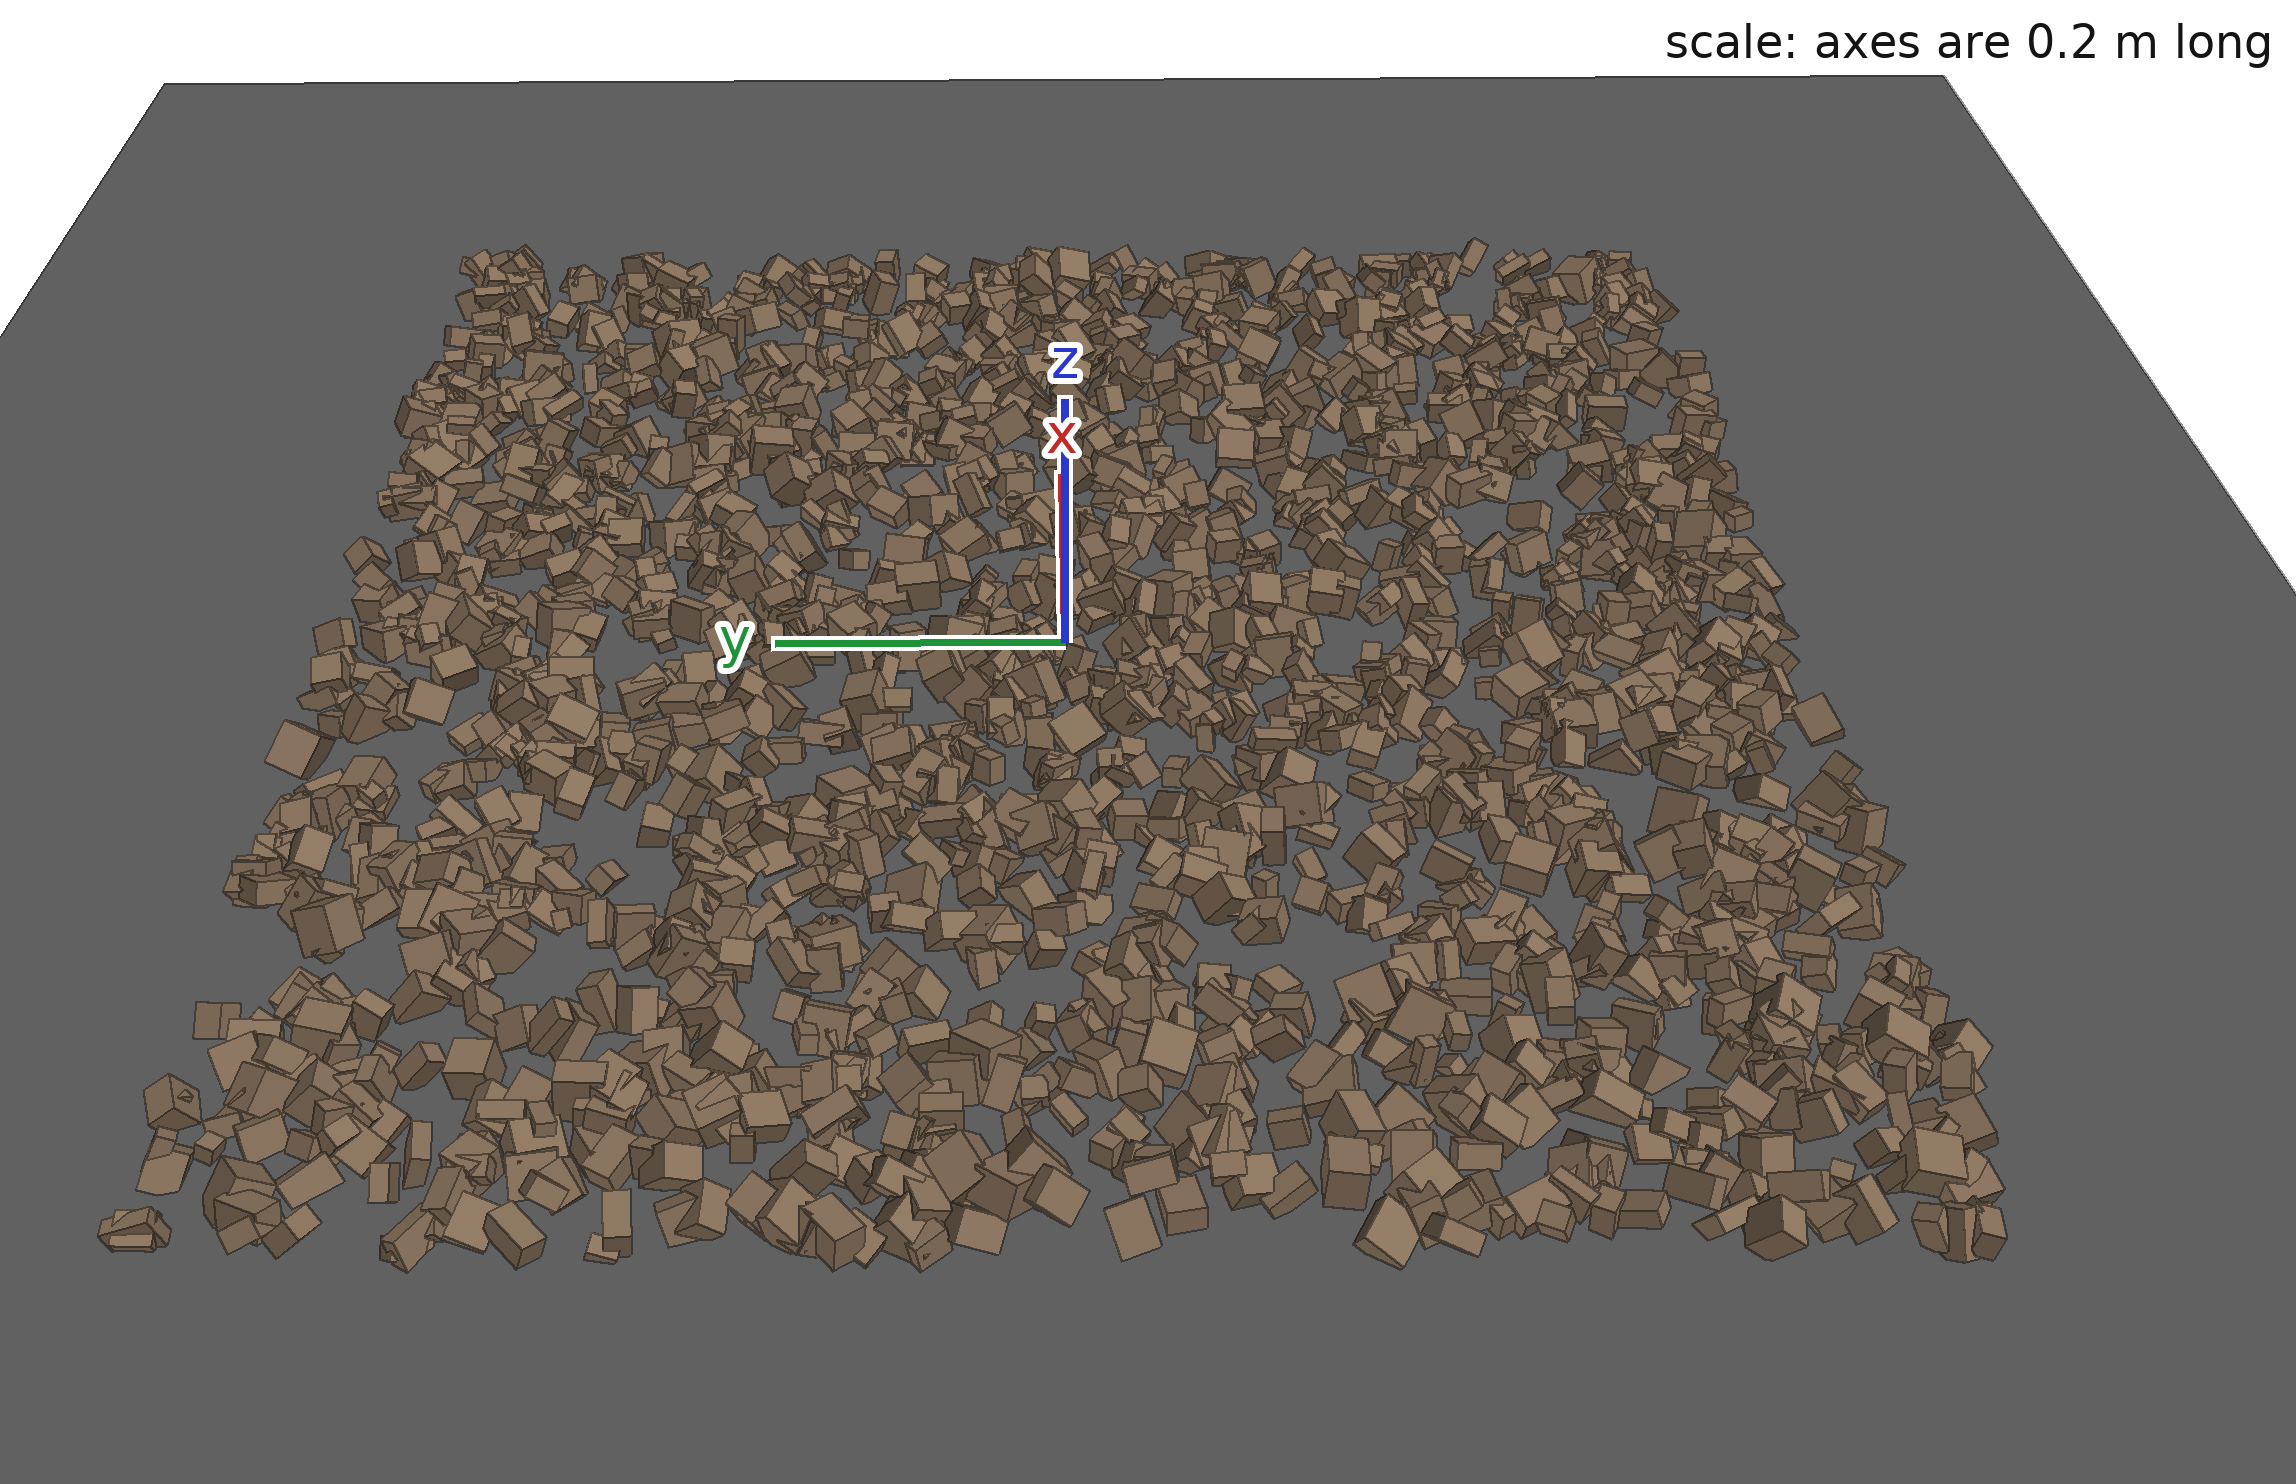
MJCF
<mujoco model="rocky_terrain_scene">
    <compiler angle="radian" inertiafromgeom="true" />
    <option timestep="0.002" gravity="0 0 -9.81" />

    <worldbody>
        <light name="sunlight" pos="5 5 5" dir="-1 -1 -1" diffuse="1 1 1" specular="0.5 0.5 0.5" ambient="0.5 0.5 0.5" />

        <geom name="ground_plane" type="plane" size="50 50 0.1" rgba="0.3 0.3 0.3 1" />

        <body name="rocky_terrain_body">

        <geom name="rock1" type="box" size="0.013908575770163661 0.005130027391782811 0.010499373790775302" pos="-0.18827640005814816 0.13581256131739594 0.013761402162840608" quat="0.28447455966588536 0.19569588286518544 0.0498491978387169 0.4699803596302122" rgba="0.5 0.4 0.3 1" friction="0.7970210658332828 0.9258393166648368 0.8067903714387248" /><geom name="rock2" type="box" size="0.014719640901393695 0.005565971786250542 0.014824258858436554" pos="-0.4006433710790901 -0.425043358116063 0.008339020676887474" quat="0.021482835890417103 0.17840736753671366 0.35369496984298765 0.44641482672988153" rgba="0.5 0.4 0.3 1" friction="0.7674013467929903 0.9742159453128045 0.8564186769252373" /><geom name="rock3" type="box" size="0.006728080233666086 0.008710629767466383 0.010141008816122035" pos="-0.3559657369850412 0.4646962237616792 0.010127616716973698" quat="0.16839593762694569 0.38715750664605725 0.15971245390841385 0.28473410181858333" rgba="0.5 0.4 0.3 1" friction="0.711296368178023 0.9197706117759015 0.8546709746942158" /><geom name="rock4" type="box" size="0.013529566886295589 0.012679838325486041 0.00964631457139399" pos="-0.07308685106676593 0.20939086933901074 0.014681029637443034" quat="0.19803727499303064 0.33492608657527106 0.1479802346972924 0.31905640373440586" rgba="0.5 0.4 0.3 1" friction="0.7957130095135846 0.9319087180113433 0.8146951196774849" /><geom name="rock5" type="box" size="0.005971989023575744 0.009800126549209994 0.0072439525680298685" pos="-0.4488581318494981 0.22874100186949575 0.013221799284017937" quat="0.009277299994477631 0.16562215400012525 0.439942770299805 0.3851577757055921" rgba="0.5 0.4 0.3 1" friction="0.7458850458540308 0.95121738731967 0.8568537633906955" /><geom name="rock6" type="box" size="0.013775374492405203 0.014191973999490501 0.00830534964722967" pos="0.34317619310943115 -0.41135170921246456 0.004498990340715416" quat="0.4029577685985618 0.20062236321437438 0.055078046092796096 0.3413418220942677" rgba="0.5 0.4 0.3 1" friction="0.7735096643662769 0.9053167694347098 0.8163091824755682" /><geom name="rock7" type="box" size="0.011125587589691165 0.014994778757437426 0.008693231200926592" pos="-0.17736620598398878 -0.23810242951521599 0.0030995959641938096" quat="0.3534829273021644 0.5235991512212397 0.12187670858930107 0.0010412128872947456" rgba="0.5 0.4 0.3 1" friction="0.7781451612630599 0.9357951238121295 0.8331416624790092" /><geom name="rock8" type="box" size="0.006139116706359778 0.008443581832395563 0.009804037636909029" pos="0.3183209511084927 0.49013878421523804 0.008587411806564648" quat="0.02179973524759398 0.14659418867743026 0.4629583078562078 0.368647768218768" rgba="0.5 0.4 0.3 1" friction="0.779604692223276 0.918656261184436 0.8911878715603933" /><geom name="rock9" type="box" size="0.005608146380150712 0.00781353785977452 0.014137788447317924" pos="-0.3241596780499293 -0.05290497241630754 0.0041438902171412875" quat="0.11171996920958356 0.2895682311051382 0.24542294903038922 0.3532888506548889" rgba="0.5 0.4 0.3 1" friction="0.7185961522131423 0.9920106067213981 0.8946584221118884" /><geom name="rock10" type="box" size="0.012910961780429293 0.013081908503360596 0.007594800389250946" pos="0.2296609328689273 0.11164882159099299 0.000661195737795086" quat="0.10689062694884797 0.38610281789381506 0.3916182632914081 0.11538829186592878" rgba="0.5 0.4 0.3 1" friction="0.7184277714283975 0.9197839747785195 0.8744575446491251" /><geom name="rock11" type="box" size="0.013081657001299773 0.01235055021423824 0.005699202812602472" pos="-0.20734963063754652 0.38346167820741184 0.002441326870329884" quat="0.1449270368069369 0.2389815821550268 0.3005553409514348 0.31553604008660147" rgba="0.5 0.4 0.3 1" friction="0.7017631568552066 0.9529255940417009 0.8843257129523141" /><geom name="rock12" type="box" size="0.011338731000347078 0.013706451103620305 0.010958565008814935" pos="0.21581320537112858 0.06616943072612058 0.00115909458534742" quat="0.43242910527575756 0.2173180976985641 0.04094763897920067 0.3093051580464777" rgba="0.5 0.4 0.3 1" friction="0.7452282334769397 0.9398121732604832 0.8458046264933048" /><geom name="rock13" type="box" size="0.009766122586911195 0.006781531581916795 0.008729747302223732" pos="0.39043364607920117 -0.2806444762266119 0.009599258681858347" quat="0.3102763524293497 0.3084401454148209 0.31573952418057794 0.06554397797525142" rgba="0.5 0.4 0.3 1" friction="0.725661779118911 0.9033118841490437 0.8091857691535193" /><geom name="rock14" type="box" size="0.013243932758368524 0.011031716306505766 0.013203708969381486" pos="-0.4592502035934808 -0.45869593486100246 0.013715148737601669" quat="0.2669061480820521 0.2677300539311594 0.19520833549816966 0.27015546248861894" rgba="0.5 0.4 0.3 1" friction="0.7353782654646982 0.9805506420911387 0.8603271415461157" /><geom name="rock15" type="box" size="0.014611270641076025 0.014546655085501535 0.009972390090731918" pos="0.2828973551698035 0.4043768169803488 0.005260984550188851" quat="0.27072058048919007 0.13452103375040098 0.10860239001515834 0.48615599574525065" rgba="0.5 0.4 0.3 1" friction="0.7081845955188012 0.9685875968967416 0.8628097648791462" /><geom name="rock16" type="box" size="0.011907842930007389 0.006685958184114392 0.012143816936850536" pos="0.3802492760526388 -0.42906993289613116 0.006445045347579309" quat="0.4003431490306049 0.15539740363394985 0.2830756620519845 0.16118378528346075" rgba="0.5 0.4 0.3 1" friction="0.7371546887179063 0.9334761894360094 0.8927298122232649" /><geom name="rock17" type="box" size="0.011171365785403451 0.009380484607520712 0.011755503121418587" pos="0.33986681340506175 -0.10629380956125833 0.008114795093643717" quat="0.08030292333167005 0.3831271937640619 0.2537860652723102 0.2827838176319579" rgba="0.5 0.4 0.3 1" friction="0.7305479818737974 0.9474355964206723 0.8520623481453201" /><geom name="rock18" type="box" size="0.013785470659830053 0.012488849730174046 0.005500130532921164" pos="-0.24151853349419827 0.22045287784387246 0.011315909437154235" quat="0.14972267689059363 0.3014584101691864 0.23540948517866767 0.3134094277615524" rgba="0.5 0.4 0.3 1" friction="0.7057677071661419 0.9904781022647892 0.8944092176982156" /><geom name="rock19" type="box" size="0.008181827776301527 0.005254847063867639 0.011793091648266245" pos="-0.2832061463852382 -0.274547121905217 0.009825852277963528" quat="0.22209169444676358 0.14694125454644916 0.31209556363862523 0.31887148736816207" rgba="0.5 0.4 0.3 1" friction="0.7680088156096357 0.9127348834049054 0.8637074409267096" /><geom name="rock20" type="box" size="0.011006762724502555 0.008255971191890702 0.011895182578580117" pos="-0.29118697396669124 -0.3982142856635674 0.0038781382947838056" quat="0.3481074988773302 0.25227726332735395 0.1273694174251768 0.27224582037013895" rgba="0.5 0.4 0.3 1" friction="0.705543275771862 0.9714221499706364 0.8977486905648192" /><geom name="rock21" type="box" size="0.006876660517124798 0.009146699807019293 0.013272727724261999" pos="-0.2613268922268104 0.22411306991442992 0.006742461939868188" quat="0.17336976478798793 0.4526836590243892 0.10259017999146217 0.27135639619616064" rgba="0.5 0.4 0.3 1" friction="0.7175641885577171 0.9930377882569533 0.8722374179112106" /><geom name="rock22" type="box" size="0.014085517249901394 0.010486579564615465 0.006535201655785021" pos="0.47841434459639187 -0.13420262580262898 0.008908574628182323" quat="0.20944985750788456 0.29319939688591007 0.3085958871962837 0.18875485840992168" rgba="0.5 0.4 0.3 1" friction="0.7005632641286015 0.9725282213948546 0.8604416388728672" /><geom name="rock23" type="box" size="0.013518061853644226 0.010396597629063102 0.008723486419998159" pos="0.012665718107115476 0.1822291709279772 0.012144692046440272" quat="0.1114391349777352 0.1375103649201844 0.12395837851195039 0.6270921215901301" rgba="0.5 0.4 0.3 1" friction="0.7694127130222237 0.9850965417486438 0.803678651317521" /><geom name="rock24" type="box" size="0.012644664966136893 0.01063492983415399 0.007320750643645313" pos="-0.24176650827117308 0.48618887493279517 0.01058141355110468" quat="0.23234987648496527 0.17880200986263883 0.041361164091382255 0.5474869495610137" rgba="0.5 0.4 0.3 1" friction="0.7203165426956878 0.9304431274084805 0.8487445170667688" /><geom name="rock25" type="box" size="0.009792147831853285 0.008067551428274252 0.011094575614324725" pos="0.04449721151711494 -0.09809707707605819 0.0031264025533222083" quat="0.23804711124401562 0.13946933612059256 0.327916083545502 0.29456746908988984" rgba="0.5 0.4 0.3 1" friction="0.7066248411796037 0.9959024886526044 0.896306959260723" /><geom name="rock26" type="box" size="0.010880187232143844 0.007627504749236638 0.009088499991209815" pos="-0.38947394248851264 -0.27145725596530046 6.700489759069894e-05" quat="0.21347532861150206 0.1942751702373278 0.3930557722814433 0.19919372886972678" rgba="0.5 0.4 0.3 1" friction="0.7967760206755752 0.9471986124193272 0.8038415968363438" /><geom name="rock27" type="box" size="0.005913404636427861 0.011041309474803413 0.010522670150334383" pos="-0.3795069946752174 -0.18925306245062734 0.0032400955747977057" quat="0.19667090006161558 0.4173933120272541 0.04930877310342605 0.3366270148077042" rgba="0.5 0.4 0.3 1" friction="0.7474945209065595 0.9717423687665929 0.8604403214034617" /><geom name="rock28" type="box" size="0.008901917451058738 0.010937119531285438 0.012160888707222314" pos="0.49535409510315354 0.0628329118362656 0.0010849288455349188" quat="0.06720229327928742 0.2667775195200301 0.32813982699717426 0.33788036020350815" rgba="0.5 0.4 0.3 1" friction="0.7075002564970984 0.978241560082338 0.8831348234763847" /><geom name="rock29" type="box" size="0.006055708248892368 0.009508142544565194 0.0057140296793635114" pos="0.059890506890380335 -0.34937341741965466 0.0097397063856101" quat="0.33727669148560996 0.37661448118669427 0.0205898003226346 0.2655190270050612" rgba="0.5 0.4 0.3 1" friction="0.7379742701986798 0.9454571086745645 0.8001568527822263" /><geom name="rock30" type="box" size="0.008672141444514867 0.011751664283812135 0.008745957731077076" pos="-0.02119399807506428 0.03202460919954031 0.01336622205344102" quat="0.1960289617604072 0.48111462738861643 0.015228367234233008 0.3076280436167433" rgba="0.5 0.4 0.3 1" friction="0.7329055228219032 0.9833798036138586 0.8041119775438258" /><geom name="rock31" type="box" size="0.01030700389792926 0.010326328444611376 0.009227032155213782" pos="0.15075527550826906 -0.1759384987202839 0.00014555442645186766" quat="0.3056637493528325 0.42577810384110554 0.0003156338562612682 0.26824251294980067" rgba="0.5 0.4 0.3 1" friction="0.7302687883103098 0.9262349594994396 0.8617366072249861" /><geom name="rock32" type="box" size="0.012386089749890958 0.007379782282954397 0.00923002838693729" pos="0.3630914928835035 -0.12092139209097197 0.010003630260648018" quat="0.4474475553518705 0.06242134171703232 0.3699897392777923 0.12014136365330491" rgba="0.5 0.4 0.3 1" friction="0.749514425859527 0.9970828512096747 0.8087579878423742" /><geom name="rock33" type="box" size="0.013029661672509695 0.006394210046461413 0.011456043789862036" pos="-0.38071506198073024 -0.2896115120111179 0.011304927963014619" quat="0.018760736822163747 0.302434926035792 0.3620851573355332 0.31671917980651104" rgba="0.5 0.4 0.3 1" friction="0.7582953225905333 0.9081389519997837 0.8875717961242989" /><geom name="rock34" type="box" size="0.014886994661440014 0.012199579570329029 0.007436319095131197" pos="0.12570158060121173 0.01837432739479905 0.013276043584784951" quat="0.3141945141917854 0.31997868918377265 0.01965349632156365 0.34617330030287835" rgba="0.5 0.4 0.3 1" friction="0.7414563196289718 0.9935829077391052 0.8671674045555852" /><geom name="rock35" type="box" size="0.005032667510513361 0.011396668516412045 0.014903704655640612" pos="-0.07131214185573864 -0.46878271743170385 0.012617086542840833" quat="0.18707572396725822 0.29322622459501824 0.19863434629381635 0.3210637051439072" rgba="0.5 0.4 0.3 1" friction="0.7160486272207338 0.9384408187160793 0.8071313633138308" /><geom name="rock36" type="box" size="0.00994995018418186 0.006139694457854037 0.007924287917992118" pos="-0.24650889324005798 -0.4564730371505663 0.0024298964335185513" quat="0.06931562776274272 0.4707314475730543 0.2738431570026438 0.18610976766155915" rgba="0.5 0.4 0.3 1" friction="0.7351302456451655 0.9506353532511121 0.8303673486190067" /><geom name="rock37" type="box" size="0.00885089219200409 0.013726457891547583 0.006442044604449995" pos="-0.48379086709749475 -0.2811327985879827 0.0018521363195312707" quat="0.07408068578763291 0.13340313880258597 0.4088310484433075 0.3836851269664736" rgba="0.5 0.4 0.3 1" friction="0.7741087946173558 0.9987272661036128 0.8267663621525136" /><geom name="rock38" type="box" size="0.0116519683613765 0.007183092118087542 0.005575979099177734" pos="0.3033701313793973 0.21600382947901553 0.011789014901407678" quat="0.33932031652116906 0.10418424381524154 0.3123632180003373 0.24413222166325205" rgba="0.5 0.4 0.3 1" friction="0.7975482537629408 0.9183552065923533 0.859819580251232" /><geom name="rock39" type="box" size="0.009764525171267866 0.008135445839822262 0.011344122218523888" pos="0.20022369222738168 -0.046874668193765956 0.00016478557541329208" quat="0.22288472211987842 0.46515282554935705 0.10678091807159619 0.20518153425916835" rgba="0.5 0.4 0.3 1" friction="0.7845265960615602 0.9704968950018945 0.806538295069076" /><geom name="rock40" type="box" size="0.013311795670879364 0.007296929233481196 0.008018386784042784" pos="-0.17034661870260637 -0.01863059059296357 0.010379632435775896" quat="0.19915112777198615 0.083063278829115 0.31758702494227803 0.4001985684566207" rgba="0.5 0.4 0.3 1" friction="0.7428357948864838 0.9082287231063809 0.8436320718710584" /><geom name="rock41" type="box" size="0.011875106896027578 0.006101047011507778 0.014887144589510216" pos="-0.4361265605946124 -0.08275051847931136 0.009974928132638516" quat="0.2182644209214057 0.3234876745613462 0.055389199564547346 0.40285870495270076" rgba="0.5 0.4 0.3 1" friction="0.7479406914556298 0.9356660265649831 0.8647501739070579" /><geom name="rock42" type="box" size="0.012858864414133767 0.008232260117086457 0.010458941352216502" pos="0.39711111755250594 -0.055730128940395196 0.005141202677591818" quat="0.11777906284963195 0.1736948868997077 0.30473026209479726 0.40379578815586303" rgba="0.5 0.4 0.3 1" friction="0.7711125913014814 0.9540040513237091 0.8534175460371471" /><geom name="rock43" type="box" size="0.00944106287408742 0.005140786341155505 0.011012390005469861" pos="-0.09179132059125794 -0.11022579400443577 0.008976901354342743" quat="0.6112554458254709 0.1718812219996948 0.03190906921090319 0.18495426296393108" rgba="0.5 0.4 0.3 1" friction="0.7168774118005137 0.956847916841056 0.8904427811591223" /><geom name="rock44" type="box" size="0.01299557154058665 0.006270032500592624 0.011993891173222453" pos="-0.08256374522763166 -0.3286430627656991 0.008902090237527615" quat="0.2704845822995227 0.24331541128085596 0.23676830213020936 0.24943170428941203" rgba="0.5 0.4 0.3 1" friction="0.794684243719536 0.9962901841224877 0.8526762690177974" /><geom name="rock45" type="box" size="0.011385984299149818 0.012779184911357964 0.008967383019417813" pos="-0.08569049099861537 -0.1583474680485375 0.008861852006179408" quat="0.3314313792223377 0.21648876074837678 0.23685069717853777 0.2152291628507477" rgba="0.5 0.4 0.3 1" friction="0.7252096592766452 0.9493715211025302 0.8239882862451198" /><geom name="rock46" type="box" size="0.005323403241040608 0.014344767159562694 0.012745989193410998" pos="-0.21468268104560162 -0.3342975523810824 0.009395410702038483" quat="0.3140766251107024 0.14705950446658803 0.32581936585985016 0.2130445045628594" rgba="0.5 0.4 0.3 1" friction="0.750083992660966 0.9327217194799257 0.8427843930600232" /><geom name="rock47" type="box" size="0.013323043838263715 0.005448859040283697 0.011514877581363958" pos="0.17590801303943904 0.2674888784752071 0.005790841326865009" quat="0.06662967539456588 0.26047482269935607 0.5771628490549205 0.09573265285115762" rgba="0.5 0.4 0.3 1" friction="0.7298922901795796 0.9219406065962608 0.8978861453484979" /><geom name="rock48" type="box" size="0.009128266760705633 0.005041988421969066 0.01080775392281855" pos="0.2684447115230363 -0.21134990200350234 0.006509177184716154" quat="0.33301888522436757 0.32416558372318244 0.02278975665074843 0.32002577440170155" rgba="0.5 0.4 0.3 1" friction="0.7988602942148387 0.9977340844878759 0.840004414707554" /><geom name="rock49" type="box" size="0.011349896830890362 0.01354631315716889 0.006707787582816912" pos="-0.38631103890791585 -0.3291234762953472 0.0001343554718769141" quat="0.25284939127158235 0.05699778974994777 0.49375182191918815 0.19640099705928174" rgba="0.5 0.4 0.3 1" friction="0.7912084893750516 0.9781188810092902 0.8177286244007589" /><geom name="rock50" type="box" size="0.012719446189973305 0.007409571883117567 0.005374159730074135" pos="-0.013718935964559531 -0.08218641931658677 0.0076186606197785976" quat="0.22369464549339957 0.3532918237557209 0.0950521894823347 0.3279613412685449" rgba="0.5 0.4 0.3 1" friction="0.7916803955752503 0.9961585623524436 0.8682250099943435" /><geom name="rock51" type="box" size="0.008730128701721213 0.0053733583613078725 0.0095171901394038" pos="0.3984437579941209 -0.033789255431901144 0.005741636494101608" quat="0.13691397469962086 0.30724151543461525 0.5442585270390174 0.011585982826746596" rgba="0.5 0.4 0.3 1" friction="0.7133840345825064 0.9394658176652253 0.8918432916741768" /><geom name="rock52" type="box" size="0.014561552562662828 0.014599467849905734 0.012165857634148982" pos="-0.05761002737359011 0.0592674172319444 8.107949951801473e-05" quat="0.029143691677832213 0.30696352152084244 0.24266010531909532 0.42123268148223003" rgba="0.5 0.4 0.3 1" friction="0.7577329725645637 0.9141496349203075 0.8011345069055976" /><geom name="rock53" type="box" size="0.005287374054849905 0.0055743569931268775 0.00968732266970003" pos="0.02177447649234554 -0.4692846068557265 0.014104621794826107" quat="0.0119073039801383 0.2709381484107349 0.36440107867714433 0.3527534689319825" rgba="0.5 0.4 0.3 1" friction="0.7634754990769892 0.9349396624192274 0.8416945876724673" /><geom name="rock54" type="box" size="0.009683495814494441 0.014056672127565777 0.011824244880147976" pos="0.38702626221732683 0.38084693119038204 0.012596522786530751" quat="0.04466266793689788 0.3473299507061717 0.3725395596847368 0.23546782167219357" rgba="0.5 0.4 0.3 1" friction="0.7323452770506091 0.9112239889799406 0.8435517565567086" /><geom name="rock55" type="box" size="0.009980611174977765 0.009235342527586348 0.008830345404052007" pos="0.24095269068279623 -0.34926815768437836 0.013505328152683654" quat="0.15321557225059534 0.2615399408289353 0.29234084745798555 0.2929036394624839" rgba="0.5 0.4 0.3 1" friction="0.7862657894888243 0.966851120534345 0.875159331739884" /><geom name="rock56" type="box" size="0.013287987415405728 0.011223729642962043 0.006810737413486641" pos="0.3979349953695701 -0.4718507568899508 0.006567438270103648" quat="0.3584889699232337 0.28995884382173165 0.06017927714401142 0.2913729091110232" rgba="0.5 0.4 0.3 1" friction="0.7737982567931497 0.9776355380392077 0.8107395023079649" /><geom name="rock57" type="box" size="0.012575104434138062 0.011404186611424436 0.014469604645785578" pos="0.2601912906723244 0.49754782682384413 0.0139087414125101" quat="0.10581705360952932 0.3020759860597614 0.27307093993059683 0.3190360204001125" rgba="0.5 0.4 0.3 1" friction="0.7114837014214563 0.960042023756256 0.8755344698535013" /><geom name="rock58" type="box" size="0.014009362916024587 0.00924888305909472 0.00623493427163409" pos="-0.18746096220745656 0.3817514970719642 0.014654780374420149" quat="0.28168243810143573 0.34972230008850197 0.0565566610996216 0.3120386007104407" rgba="0.5 0.4 0.3 1" friction="0.7151086938102017 0.9005225764233397 0.8830155478401739" /><geom name="rock59" type="box" size="0.008324261986260992 0.005089699482370995 0.007128279994797113" pos="0.14368240917484898 -0.2679732927127949 0.01189788605077445" quat="0.16566123430348204 0.3710125859159859 0.07007328271301944 0.39325289706751265" rgba="0.5 0.4 0.3 1" friction="0.7991524493631438 0.9452662434226258 0.8626019728243346" /><geom name="rock60" type="box" size="0.013981772057528652 0.014904535127742698 0.014843327195997708" pos="0.3384132711843867 -0.45968682587745613 0.008007495027741425" quat="0.19180410149245175 0.2440740364514754 0.3300573106472069 0.2340645514088659" rgba="0.5 0.4 0.3 1" friction="0.7646839725936553 0.9536959887897926 0.8642770874195761" /><geom name="rock61" type="box" size="0.008482354240751116 0.012777090180670352 0.011981216813189047" pos="-0.12749946004470758 0.26925798669873346 0.010400254606386206" quat="0.43946355556214006 0.15318993136577416 0.04944310691323507 0.3579034061588508" rgba="0.5 0.4 0.3 1" friction="0.7378485858679307 0.9024035826196702 0.834267224056629" /><geom name="rock62" type="box" size="0.011832427978067859 0.014976156741679642 0.007695041619459601" pos="-0.314409028052825 0.10335529193960458 0.012216459304729562" quat="0.23002851644537048 0.1006137121989896 0.4276351558966779 0.241722615458962" rgba="0.5 0.4 0.3 1" friction="0.7055003091943339 0.9048631191962209 0.8310766404921348" /><geom name="rock63" type="box" size="0.014855521163400082 0.00954371799914391 0.008758478496459398" pos="-0.06257596665109544 0.04536302165096828 0.003015453049005154" quat="0.3545450538379127 0.4310493977565239 0.12910523605968505 0.08530031234587834" rgba="0.5 0.4 0.3 1" friction="0.7742594404509244 0.9662473130543721 0.8278229697307511" /><geom name="rock64" type="box" size="0.01009582300453088 0.01379725027857364 0.011938051849983956" pos="0.07673611906047784 -0.1979080228414445 0.008874271150322226" quat="0.34701021415302397 0.03479694783485695 0.40964285104308706 0.20854998696903204" rgba="0.5 0.4 0.3 1" friction="0.7913059400101914 0.9024426797002534 0.8045889073332967" /><geom name="rock65" type="box" size="0.01006167674045966 0.01208899945105945 0.010240715517011535" pos="0.16393951513928484 -0.38371564548190207 0.013224396617256063" quat="0.14858458874547137 0.3909351705437233 0.1792714463705504 0.281208794340255" rgba="0.5 0.4 0.3 1" friction="0.7648570001907908 0.9231647769031662 0.8320415340876911" /><geom name="rock66" type="box" size="0.006973461088020443 0.010864489469949456 0.005098832971560186" pos="-0.08140072898956241 0.05907539241137383 0.003590996815776341" quat="0.29324666036578856 0.34742859046931557 0.24731699603774165 0.11200775312715419" rgba="0.5 0.4 0.3 1" friction="0.7145706759538255 0.9669990343776128 0.87206120757408" /><geom name="rock67" type="box" size="0.013566636738483046 0.008730767302137059 0.009300492361279316" pos="0.037130579850674805 0.39925233705242913 0.00635795402254916" quat="0.09845414029457476 0.30927796431814136 0.2436880927083316 0.3485798026789522" rgba="0.5 0.4 0.3 1" friction="0.7663302456193656 0.9067748263451793 0.8897143779098244" /><geom name="rock68" type="box" size="0.005318488516563147 0.010391730094281973 0.012553374884051246" pos="0.47012831729765414 0.22202353135965425 0.012722516861789858" quat="0.12054167782269111 0.4424414185172488 0.15928868443648803 0.2777282192235721" rgba="0.5 0.4 0.3 1" friction="0.7601587261903505 0.9393409846677836 0.8423416564186778" /><geom name="rock69" type="box" size="0.014878527198141766 0.010702886585486139 0.008103189342970253" pos="-0.0694468946664688 0.2806055318016031 0.014878119754855717" quat="0.19751377229002068 0.20395530781097987 0.3214519495169617 0.2770789703820378" rgba="0.5 0.4 0.3 1" friction="0.7943833674913914 0.9107239971545025 0.8884001122964025" /><geom name="rock70" type="box" size="0.013510482356499792 0.009877241809560542 0.014398034731315238" pos="-0.2754661158981787 0.20729702107761938 0.0036437481226537496" quat="0.11143004285436388 0.06898322412580617 0.4846091522634848 0.33497758075634515" rgba="0.5 0.4 0.3 1" friction="0.7370248179239771 0.9169698044104007 0.8114921661422442" /><geom name="rock71" type="box" size="0.007495903797998808 0.005862960027125524 0.011402027024758874" pos="-0.05017830967817749 -0.2327919716714878 0.010092980996857188" quat="0.4174509999720864 0.12092294679234313 0.034653974260190325 0.42697207897538014" rgba="0.5 0.4 0.3 1" friction="0.7144391809933828 0.9548273046487706 0.8616460761609526" /><geom name="rock72" type="box" size="0.010210640361796596 0.014942620827810046 0.007764990501969139" pos="-0.07801752121610683 -0.21759171541522682 0.0137434367385009" quat="0.12662523319058808 0.23803004290197025 0.2625701062696145 0.3727746176378272" rgba="0.5 0.4 0.3 1" friction="0.7858720087803798 0.9249486144631917 0.8171846244613665" /><geom name="rock73" type="box" size="0.0059329301175000335 0.014699625069429206 0.011279023452637513" pos="0.0863320398442966 -0.4258071024656792 0.013766468697851373" quat="0.2580546578082356 0.26610404940931975 0.22831883799777067 0.2475224547846739" rgba="0.5 0.4 0.3 1" friction="0.7313068989163445 0.9820800496517069 0.8233542860929421" /><geom name="rock74" type="box" size="0.006929497374586432 0.014781551540874797 0.006794302462030879" pos="-0.025035093217545712 -0.08849671964591488 0.012673821180881348" quat="0.5297300578379279 0.004416663808322556 0.06825140066992093 0.3976018776838286" rgba="0.5 0.4 0.3 1" friction="0.7320158819249554 0.9374274680365081 0.8920832048395775" /><geom name="rock75" type="box" size="0.010278147356360269 0.008778755344527024 0.009348785581912596" pos="0.36891048504858237 -0.26082719595007164 0.0026980680859719527" quat="0.33726133279634946 0.28219727196251587 0.06467223085502301 0.3158691643861117" rgba="0.5 0.4 0.3 1" friction="0.7825115031944003 0.9049559239870821 0.8848408452484191" /><geom name="rock76" type="box" size="0.010622473444330044 0.009379074951275313 0.008714227446718932" pos="-0.18349402019686822 0.09625078516533747 8.354325541467588e-05" quat="0.4774621702187622 0.22884097024926148 0.21760865774727514 0.07608820178470113" rgba="0.5 0.4 0.3 1" friction="0.7556050484357546 0.9209175832877426 0.8342267295384035" /><geom name="rock77" type="box" size="0.010728150883150222 0.00650845776541874 0.00916588856014431" pos="-0.49399520308329004 0.40845992366213113 0.013377361192919754" quat="0.3178442238681426 0.24039885219214105 0.3956784463191921 0.04607847762052435" rgba="0.5 0.4 0.3 1" friction="0.7293659464259595 0.9836734904927802 0.8036044780709571" /><geom name="rock78" type="box" size="0.011634188031708289 0.006631125210311018 0.013651609498033256" pos="-0.4584568985035148 -0.3367866615823377 0.003907820477202571" quat="0.3411405815107604 0.18136519515901783 0.12404450171709645 0.3534497216131254" rgba="0.5 0.4 0.3 1" friction="0.7856218091532252 0.9362878124229642 0.8254797468221707" /><geom name="rock79" type="box" size="0.006076284365624188 0.006181790388482794 0.011484079793897203" pos="0.24369040255267782 0.46255107045559063 0.0023371163913334637" quat="0.29621816054080347 0.1472624609566611 0.2795201257886934 0.27699925271384196" rgba="0.5 0.4 0.3 1" friction="0.7923989151266531 0.9299179773138948 0.8545629140477893" /><geom name="rock80" type="box" size="0.008144755781411894 0.011944982521803165 0.009967038575175034" pos="0.3888647427151146 0.4369252074985749 0.002384820830314692" quat="0.3376327099582399 0.3703814891285909 0.12360199797568651 0.16838380293748256" rgba="0.5 0.4 0.3 1" friction="0.7974910866560583 0.9079233222138091 0.8977216822043059" /><geom name="rock81" type="box" size="0.0131219875267558 0.005901659199734344 0.008356240634504773" pos="-0.41258243479984436 0.3920453013862327 0.012882565395777399" quat="0.1670755380274105 0.44652934518730963 0.17059278667618002 0.21580233010909994" rgba="0.5 0.4 0.3 1" friction="0.7971121574456294 0.9155296909177506 0.8179342486924829" /><geom name="rock82" type="box" size="0.014017418388890073 0.010571924213808563 0.012379025174593845" pos="0.08433109655141224 0.11400962517461366 0.014788263491391028" quat="0.3911932226919561 0.15061758476533413 0.10809756080045309 0.35009163174225666" rgba="0.5 0.4 0.3 1" friction="0.7186739643484302 0.9257729416577387 0.8626160257438024" /><geom name="rock83" type="box" size="0.013852017654589745 0.0054075759561954565 0.006873031710691638" pos="0.06148948004133381 -0.40202855378064606 0.0025270194991151174" quat="0.30060578587048054 0.44835412792813883 0.10675106249450646 0.1442890237068741" rgba="0.5 0.4 0.3 1" friction="0.7880873164003581 0.9298856077535008 0.8481111756620014" /><geom name="rock84" type="box" size="0.008474438655706526 0.013703095927290347 0.01361319871922615" pos="-0.49548115012965266 -0.4666249494981133 0.0041036879602851925" quat="0.533347855252317 0.06991553096278326 0.20976321498541506 0.18697339879948466" rgba="0.5 0.4 0.3 1" friction="0.7742291374723385 0.9489604755597746 0.8505062995343243" /><geom name="rock85" type="box" size="0.007081977634844779 0.010167286258110704 0.009257057179037145" pos="-0.42619011133835893 0.13335166300877332 0.005884076418469972" quat="0.10112919305627313 0.3164791439852721 0.10337701524871666 0.4790146477097381" rgba="0.5 0.4 0.3 1" friction="0.7253950383820671 0.9095198066402833 0.8186280291979733" /><geom name="rock86" type="box" size="0.01075154376727722 0.014202727355836945 0.006811376793715121" pos="0.4406871963103669 -0.19619087009137737 0.003968356771939652" quat="0.39188762301234864 0.11441593647026331 0.2077629623031497 0.28593347821423837" rgba="0.5 0.4 0.3 1" friction="0.7617557813658545 0.9936689918054842 0.8538740619315739" /><geom name="rock87" type="box" size="0.005595809945970425 0.006395112824322805 0.010202172735023878" pos="-0.2333006646454192 0.40704075422188324 0.0018443074265842812" quat="0.02821149106292172 0.3698376814718305 0.26884873098852086 0.3331020964767269" rgba="0.5 0.4 0.3 1" friction="0.7273167315357582 0.9654178413510589 0.8921379347288775" /><geom name="rock88" type="box" size="0.012097845380089015 0.013624371141905647 0.01413407593422518" pos="-0.10032771030053711 0.32617708132479517 0.014984142311711447" quat="0.09076431854331958 0.004126624818906321 0.34293410696328475 0.5621749496744892" rgba="0.5 0.4 0.3 1" friction="0.7726392567109022 0.9569716078817542 0.8113279070584986" /><geom name="rock89" type="box" size="0.01436949099733896 0.009915504102386147 0.007790817908608003" pos="0.3254015149052596 -0.49999097162612116 0.009426689823738453" quat="0.44731878285891774 0.0009381876901726284 0.5418703106386925 0.009872718812217057" rgba="0.5 0.4 0.3 1" friction="0.7785479329869055 0.9011866942338087 0.8058838632963289" /><geom name="rock90" type="box" size="0.007475448470763986 0.008666383676861563 0.008312432966851238" pos="-0.041149788967823064 0.21580008057686517 0.0025752575811510314" quat="0.33162948829268185 0.32796172500250614 0.3050442424265694 0.03536454427824261" rgba="0.5 0.4 0.3 1" friction="0.7156627332105151 0.966765335557744 0.8665477823278004" /><geom name="rock91" type="box" size="0.01245846283784586 0.008690338485064385 0.00780981010402834" pos="-0.2631099281890661 0.22673558672430338 0.007941553107445007" quat="0.3192051511126407 0.09480396688168392 0.3080889404544328 0.27790194155124254" rgba="0.5 0.4 0.3 1" friction="0.7455053497428239 0.9915545503226619 0.8868235753731873" /><geom name="rock92" type="box" size="0.011878001322243373 0.005577429729736349 0.006810212841119204" pos="0.26431805298599365 0.09782528368467125 0.006197718802712899" quat="0.44375795574370375 0.09461707434168998 0.2032779892501229 0.25834698066448325" rgba="0.5 0.4 0.3 1" friction="0.7765792750875324 0.9026365621265225 0.8224045705593348" /><geom name="rock93" type="box" size="0.01458833320206885 0.01449009581036654 0.009845717978361913" pos="0.253026032036203 -0.12608332264359612 0.007611217180018395" quat="0.33018577859780307 0.3398981196252715 0.04424133861414951 0.28567476316277607" rgba="0.5 0.4 0.3 1" friction="0.7100692393553355 0.9796754651714162 0.8540362379672438" /><geom name="rock94" type="box" size="0.0057920480558131026 0.011573086435524123 0.01040151250196928" pos="0.2727857454961212 -0.32637928157918816 0.012162405527700544" quat="0.4018980919173121 0.1975190915851899 0.16956359758623116 0.23101921891126684" rgba="0.5 0.4 0.3 1" friction="0.7028138867855701 0.9397640854282797 0.8783552007094929" /><geom name="rock95" type="box" size="0.009495814846732665 0.013899731240305694 0.010447436612321725" pos="0.26379617117266596 0.03806568100012586 0.010895066597232" quat="0.11907525553080633 0.05615699307612732 0.3694301608590073 0.455337590534059" rgba="0.5 0.4 0.3 1" friction="0.7594394218669451 0.9463874396290177 0.8491482874200662" /><geom name="rock96" type="box" size="0.008336282591127423 0.012559620141824901 0.007288030159055866" pos="0.394101109592365 -0.40311011122491147 0.010800552539909155" quat="0.1587362054044746 0.36792038308383523 0.4164316526826885 0.05691175882900163" rgba="0.5 0.4 0.3 1" friction="0.7879827463015212 0.9480443025978094 0.8854311183554433" /><geom name="rock97" type="box" size="0.011891102715327097 0.008518369842950076 0.005095072301576148" pos="0.1492240699542935 0.3299071746475999 0.011716310296307028" quat="0.17938791606300517 0.35360930878816554 0.20307943110870944 0.2639233440401199" rgba="0.5 0.4 0.3 1" friction="0.7619790149251546 0.935369354634328 0.8247880921983058" /><geom name="rock98" type="box" size="0.00960193905022056 0.007802403457223337 0.005445230595260031" pos="0.348226612087732 -0.23525540851910132 0.004453825158730717" quat="0.35015536363783345 0.2353530588841613 0.2589230046017855 0.15556857287621978" rgba="0.5 0.4 0.3 1" friction="0.7145433256193437 0.9893007187095527 0.8092933240712731" /><geom name="rock99" type="box" size="0.013595609828280994 0.009587941165245008 0.010690511607297087" pos="-0.48874773904759394 0.053830064402019207 0.004480816516281314" quat="0.034278226990818304 0.3792140193399736 0.3376409516797363 0.24886680198947184" rgba="0.5 0.4 0.3 1" friction="0.7061883813565124 0.9820905902282085 0.8602941712612513" /><geom name="rock100" type="box" size="0.011419204362151703 0.012034651975181002 0.008489911700534567" pos="-0.27563815631825483 0.006706412825995489 0.014541915809461072" quat="0.4553862605591389 0.07194811834663052 0.18756700623642822 0.2850986148578024" rgba="0.5 0.4 0.3 1" friction="0.7038029710553079 0.9385589392999125 0.8876891812359942" /><geom name="rock101" type="box" size="0.013676672259922341 0.010935543701302139 0.010988545566554783" pos="0.13717033049627814 0.436677501601929 0.002795304504770244" quat="0.22583978480948233 0.15830193884239008 0.6016588941951779 0.014199382152949615" rgba="0.5 0.4 0.3 1" friction="0.7883316700408816 0.9714008609586213 0.8980235346119834" /><geom name="rock102" type="box" size="0.008907991116100796 0.012674738514678286 0.010850259442905866" pos="-0.2731820337959212 -0.31454249203334794 0.0019365378867688703" quat="0.4374121692955521 0.19133434370181493 0.10230104437120106 0.26895244263143187" rgba="0.5 0.4 0.3 1" friction="0.7928032818681842 0.9625322213117077 0.8376030314741081" /><geom name="rock103" type="box" size="0.014544357761606348 0.01046235049882272 0.009018817799053964" pos="-0.10548639037636354 0.3410620228448348 0.014181622342092973" quat="0.45385048056920324 0.3211395962155063 0.17558927443328437 0.04942064878200611" rgba="0.5 0.4 0.3 1" friction="0.7321993648875915 0.9181672352117857 0.8341894925560043" /><geom name="rock104" type="box" size="0.005414253929049508 0.009680212872536207 0.010206477602637001" pos="-0.17660531346897657 -0.20903527293921265 0.00934768581499769" quat="0.32075300325207956 0.021732103367975805 0.31024898125426537 0.3472659121256793" rgba="0.5 0.4 0.3 1" friction="0.7223563334709568 0.9595475855616595 0.833743698384433" /><geom name="rock105" type="box" size="0.009466142912970963 0.0091946361745751 0.005445764525006267" pos="-0.2944193386798357 -0.20650577377499524 0.014171794561184406" quat="0.2036480424412094 0.11579678317623893 0.3966803195173343 0.28387485486521735" rgba="0.5 0.4 0.3 1" friction="0.7801684834300686 0.960599301571984 0.8840940762621305" /><geom name="rock106" type="box" size="0.008675725479584982 0.011504081675404046 0.00598589758657605" pos="0.2538939877379005 0.07515185778270572 0.012627443077728047" quat="0.2748360547538313 0.17754974955258923 0.26112930434647313 0.28648489134710625" rgba="0.5 0.4 0.3 1" friction="0.7193085257400997 0.968727710661066 0.8165052413819973" /><geom name="rock107" type="box" size="0.0103160765798972 0.009257201309652529 0.011061234926604109" pos="-0.04694848168616328 0.4930206065294821 0.01466147629679067" quat="0.27314237808972025 0.1822435262921101 0.25050919668788624 0.29410489893028346" rgba="0.5 0.4 0.3 1" friction="0.7314382230468218 0.9631999479165368 0.8655448318497275" /><geom name="rock108" type="box" size="0.011554078673627757 0.014662745225497733 0.0057378493017583585" pos="0.4730944506140321 -0.47406589641476793 0.010213556945111987" quat="0.38086379716430474 0.07721093679050078 0.28248170539572404 0.2594435606494705" rgba="0.5 0.4 0.3 1" friction="0.7674714100749956 0.940387246793443 0.8343733001394722" /><geom name="rock109" type="box" size="0.0092538360049108 0.011483085456704765 0.012574358576314514" pos="-0.0855183053437436 -0.41287346584828855 0.014912143781743263" quat="0.3381927712894566 0.332943699408582 0.16526830924994954 0.1635952200520119" rgba="0.5 0.4 0.3 1" friction="0.7997477022061384 0.984808291558223 0.8954814771870473" /><geom name="rock110" type="box" size="0.007897322508251056 0.008055500701641394 0.010132404344283532" pos="-0.1378370999964431 -0.027054437597164416 0.009929927110488958" quat="0.017281461719799374 0.9064582499548473 0.02906316397882379 0.04719712434652957" rgba="0.5 0.4 0.3 1" friction="0.7618061368556815 0.9872586257515629 0.8786321279259968" /><geom name="rock111" type="box" size="0.00971298181596215 0.0071626286211266075 0.00549935227015003" pos="-0.4514630755560838 -0.04345375655227257 0.010239966568541271" quat="0.26866610821288506 0.28792261954737136 0.2899796750246922 0.1534315972150514" rgba="0.5 0.4 0.3 1" friction="0.7022273603438258 0.9379707363733865 0.8115261073088593" /><geom name="rock112" type="box" size="0.014925266201920414 0.006740265681400107 0.009606780001899351" pos="-0.10486203514694714 0.10797750874915912 0.003115583661220453" quat="0.1391384986686201 0.2402976283801928 0.22263359569753516 0.3979302772536519" rgba="0.5 0.4 0.3 1" friction="0.7176651391719446 0.9603636971900267 0.8666857760636666" /><geom name="rock113" type="box" size="0.009823737359817817 0.008530135198225456 0.007690779024518453" pos="-0.005123339030749241 0.041014428535173675 0.012509103068680718" quat="0.28387180295163733 0.20758225400842772 0.2937805397105994 0.21476540332933558" rgba="0.5 0.4 0.3 1" friction="0.7739539299783593 0.9490522126957014 0.8414516794142178" /><geom name="rock114" type="box" size="0.013614340230721292 0.008905496427655105 0.006592504421816938" pos="-0.32224551716041805 -0.3986272264598213 0.0065691447646455585" quat="0.698681928283922 0.08089924481781337 0.13120149299608314 0.08921733390218149" rgba="0.5 0.4 0.3 1" friction="0.7516437667372576 0.9908851522210164 0.8726981292244707" /><geom name="rock115" type="box" size="0.012927724640375077 0.012693543594862546 0.009268444996051624" pos="0.20760838019965344 -0.0441335030543798 0.006662722925894083" quat="0.16538382763234372 0.21033537020524143 0.3895838814876233 0.23469692067479167" rgba="0.5 0.4 0.3 1" friction="0.7944337575924698 0.9401773428012647 0.8590209489322389" /><geom name="rock116" type="box" size="0.01151514925677223 0.005209628783045696 0.009822367822495867" pos="0.32987287822124645 -0.32881402563722417 0.0037268866098279707" quat="0.33994298332002354 0.2310134481022252 0.21262215801880668 0.2164214105589446" rgba="0.5 0.4 0.3 1" friction="0.7277517228902187 0.9085148357791999 0.8016089732375993" /><geom name="rock117" type="box" size="0.014590455317593079 0.009199732008867995 0.007826690521636209" pos="-0.2496544791629327 0.32707532416119 0.00201001605734763" quat="0.23949689734848237 0.24183399816220852 0.13378814017162255 0.38488096431768654" rgba="0.5 0.4 0.3 1" friction="0.7548836277489923 0.9179754505565709 0.8347336092033936" /><geom name="rock118" type="box" size="0.008245021866719836 0.013378108976045598 0.012642328173503567" pos="-0.07352772946731057 -0.43089946393078027 0.000955072416724067" quat="0.008257633578829388 0.4349341636983034 0.25234108254344784 0.30446712017941935" rgba="0.5 0.4 0.3 1" friction="0.7235070360174644 0.9794044280638713 0.8561035044891004" /><geom name="rock119" type="box" size="0.01109380125862783 0.007988488271703266 0.007588862825112374" pos="0.029920711843170134 -0.21734839085794533 0.005854848108947526" quat="0.24702809442551543 0.12888458920053258 0.3829913227172516 0.24109599365670037" rgba="0.5 0.4 0.3 1" friction="0.7345768770881138 0.9703634340245239 0.8992968114310156" /><geom name="rock120" type="box" size="0.012567181088181723 0.014172025031079175 0.01177420920631152" pos="-0.20312088325707078 -0.30098949027871846 0.005144920250973568" quat="0.16796547223973124 0.3164588593291399 0.3806050826776186 0.13497058575351017" rgba="0.5 0.4 0.3 1" friction="0.7544942495472705 0.9958837425194927 0.8884336938931766" /><geom name="rock121" type="box" size="0.010935574748053373 0.005456075731190425 0.005524285622896098" pos="-0.059378603664431595 -0.17049496784513563 0.004313938589157933" quat="0.08393992312970147 0.4484036621429338 0.03236130612349074 0.435295108603874" rgba="0.5 0.4 0.3 1" friction="0.7151228352589851 0.9888428690518694 0.8246799675072325" /><geom name="rock122" type="box" size="0.0077213043156958774 0.010131075885839 0.00601620111111705" pos="-0.2860279671082051 -0.2602797222797796 0.0070116091103213495" quat="0.2104967765826942 0.3802371958702046 0.047748941756444827 0.36151708579065633" rgba="0.5 0.4 0.3 1" friction="0.7305569424449381 0.9857508486477846 0.8264257446974247" /><geom name="rock123" type="box" size="0.00926093428882423 0.007398027040496913 0.012237507709989826" pos="0.32360371143868794 -0.4474420840604646 0.003393969226267207" quat="0.14375795304723193 0.2917731435793582 0.3443141104492966 0.22015479292411327" rgba="0.5 0.4 0.3 1" friction="0.7369408100233119 0.9328913258790298 0.8921213001722446" /><geom name="rock124" type="box" size="0.009350933273506367 0.007099124907679586 0.00906749538973561" pos="0.1385143282579504 -0.12654797115371008 0.009358853818816034" quat="0.11244891676579609 0.14806813541121994 0.20702260118205468 0.5324603466409292" rgba="0.5 0.4 0.3 1" friction="0.724477506544341 0.9250452484182192 0.8026786293838333" /><geom name="rock125" type="box" size="0.0061114776481550346 0.010202692157075666 0.011446884159350666" pos="-0.3915209607212091 -0.3878383660026201 0.009029955396963357" quat="0.30477840906671 0.3289531047429606 0.3188413871527349 0.04742709903759455" rgba="0.5 0.4 0.3 1" friction="0.7495000725869199 0.9589648058733331 0.8153490876078939" /><geom name="rock126" type="box" size="0.008127230303032036 0.007607724068991262 0.012686232922814955" pos="-0.0014071364045445955 0.38958712691177955 0.007657894388354615" quat="0.038084245170823976 0.5108561514885758 0.09092085081855406 0.36013875252204625" rgba="0.5 0.4 0.3 1" friction="0.7716411672265555 0.9277621389631737 0.8263531256086335" /><geom name="rock127" type="box" size="0.012922289262797197 0.005037537261288742 0.009120745395007724" pos="0.08415384142732862 -0.30263113653410134 0.01446328531619223" quat="0.21343098818832126 0.20587124506705498 0.4758677144656989 0.1048300522789248" rgba="0.5 0.4 0.3 1" friction="0.7833036165403733 0.9614208871668729 0.8915176945582556" /><geom name="rock128" type="box" size="0.005277389267803688 0.00531214376880383 0.012250710271698904" pos="-0.4409161153718725 0.4929665652435127 0.011594792711214469" quat="0.6513529381025948 0.16265775530991364 0.13473070604091728 0.051258600546574315" rgba="0.5 0.4 0.3 1" friction="0.7644708556926926 0.9057657741863658 0.8630791990622162" /><geom name="rock129" type="box" size="0.013242108300258223 0.010141375720772177 0.013466575111714521" pos="-0.09653664790361105 -0.33198257897461436 0.007331589717232773" quat="0.25919519714887396 0.23453729136458595 0.2670439473104106 0.23922356417612958" rgba="0.5 0.4 0.3 1" friction="0.7355262081709752 0.9216559774857659 0.8577686885471927" /><geom name="rock130" type="box" size="0.013952541666557256 0.01213129464094135 0.009164344960965907" pos="-0.17380421911608068 -0.258771380751633 0.011381075171356975" quat="0.005436136977287431 0.28321524384772945 0.43275937189170016 0.2785892472832829" rgba="0.5 0.4 0.3 1" friction="0.7081063393225712 0.9354554256700174 0.8410875911481963" /><geom name="rock131" type="box" size="0.006581318340140654 0.0077489426328891595 0.0105063562457482" pos="-0.3846262231479467 0.1893991520910363 0.0010866995295485138" quat="0.25755650234529276 0.24057560688368174 0.31986766803589645 0.18200022273512903" rgba="0.5 0.4 0.3 1" friction="0.785507052244821 0.9651068909151952 0.8226088214484795" /><geom name="rock132" type="box" size="0.0082976786555005 0.013007927187753305 0.009956304303012337" pos="0.27562687614503867 0.15746251695337243 0.01428027250590232" quat="0.3227970410225552 0.09932288982227437 0.16525097092427618 0.4126290982308942" rgba="0.5 0.4 0.3 1" friction="0.7372933995404736 0.9350279517393338 0.8902745825260705" /><geom name="rock133" type="box" size="0.013559246419454166 0.006805681920389196 0.00686869724724011" pos="-0.12076954682078167 -0.3867658268889522 0.007561148097762508" quat="0.4848794608285515 0.01278248211191323 0.20084510393368898 0.3014929531258463" rgba="0.5 0.4 0.3 1" friction="0.7484617641834694 0.9553699451066888 0.8835848596691315" /><geom name="rock134" type="box" size="0.014687738277101764 0.014041542552267666 0.0062307434020738425" pos="0.11719034336857592 -0.09721472387920305 0.005367974253648011" quat="0.019360006898029847 0.5028612456414318 0.16352390421301868 0.31425484324751957" rgba="0.5 0.4 0.3 1" friction="0.7958509217541043 0.9834300641299364 0.8155052562878093" /><geom name="rock135" type="box" size="0.01026258659094196 0.006405273953711429 0.009385910804703284" pos="0.3652489464965194 -0.011751025718208186 0.002703172298635606" quat="0.042635971042219216 0.15678922520859248 0.44595507362515513 0.3546197301240333" rgba="0.5 0.4 0.3 1" friction="0.7175217833134024 0.9861508658393786 0.8709591703425779" /><geom name="rock136" type="box" size="0.008675644803394835 0.012962630330585628 0.010233673996937285" pos="-0.3259977918770859 0.3779839279028354 0.0038540490704160124" quat="0.232946851762192 0.5741224324929359 0.11996545314753299 0.0729652625973391" rgba="0.5 0.4 0.3 1" friction="0.7633306221790954 0.9272376358399879 0.8177083289922407" /><geom name="rock137" type="box" size="0.014355375252035108 0.008464837650597438 0.00795472045450308" pos="0.4462247275756661 -0.2339779579229141 0.014097918275942447" quat="0.12484784671775957 0.5795368814620943 0.09946807012258195 0.1961472016975642" rgba="0.5 0.4 0.3 1" friction="0.7091343888643357 0.9363083598067639 0.8930134697428229" /><geom name="rock138" type="box" size="0.014770463662459796 0.007266561781273292 0.009746522088983144" pos="-0.2039741114052489 0.1583888462302976 0.013640953518969145" quat="0.15945627793458655 0.30191456600597716 0.2570102205117509 0.28161893554768536" rgba="0.5 0.4 0.3 1" friction="0.711425360841153 0.9993341397830384 0.8790541762843546" /><geom name="rock139" type="box" size="0.005671411255547238 0.013058715800147072 0.011044492677283496" pos="0.337331226717993 0.22999683603767773 0.013731900491841266" quat="0.04936122390911741 0.26416032722697247 0.5734715232304444 0.11300692563346577" rgba="0.5 0.4 0.3 1" friction="0.7537863621606096 0.9938883877946139 0.8256351322057721" /><geom name="rock140" type="box" size="0.0051495849757247185 0.006650758410625053 0.007588338078642813" pos="-0.4837820221762609 0.3388356148786503 0.001647007307415596" quat="0.32348250088960157 0.1650458558880645 0.2779491721446043 0.2335224710777297" rgba="0.5 0.4 0.3 1" friction="0.7115643144424001 0.9512904259429067 0.8543551152961267" /><geom name="rock141" type="box" size="0.005369881736688861 0.009887118513809235 0.012788421642458242" pos="0.25719234270759883 0.4399466018757807 0.010131825651809428" quat="0.1254156683502225 0.4804605219239585 0.14532489810946253 0.2487989116163564" rgba="0.5 0.4 0.3 1" friction="0.758922368419084 0.922851464875869 0.874959500907531" /><geom name="rock142" type="box" size="0.013709985593296288 0.010058991349104911 0.010858053044696166" pos="-0.15885755765958443 -0.08992201552533108 0.014092784433329252" quat="0.5550316852032711 0.23470689290315253 0.02591918991673869 0.18434223197683788" rgba="0.5 0.4 0.3 1" friction="0.7807091617129015 0.9556609737999889 0.8983704894927738" /><geom name="rock143" type="box" size="0.009194704192324866 0.011175024618025223 0.006067214908177729" pos="-0.05817038206453151 -0.44203534612456996 0.008574508375302537" quat="0.18542314395550963 0.37800946211023967 0.061170854601549876 0.37539653933270095" rgba="0.5 0.4 0.3 1" friction="0.7173066148730043 0.9060802003795887 0.8814716145615692" /><geom name="rock144" type="box" size="0.007534400046097077 0.014752977328399069 0.014625867300834546" pos="0.2264982314438314 -0.17493033639187006 0.006106855829084013" quat="0.10010393904646556 0.34976106058743034 0.31504332903463295 0.2350916713314712" rgba="0.5 0.4 0.3 1" friction="0.774120826701733 0.9798762521630074 0.8795638923102652" /><geom name="rock145" type="box" size="0.010652870026615162 0.00952869143210586 0.014468025475893907" pos="-0.20630022624619915 -0.10566341597448092 0.0036210297067497624" quat="0.013375409190079525 0.6331208347941626 0.20202204190760367 0.15148171410815414" rgba="0.5 0.4 0.3 1" friction="0.7011720888493664 0.9448400078257273 0.8649783068988018" /><geom name="rock146" type="box" size="0.011894896075633075 0.009896628551237095 0.011409926247756361" pos="0.2962273071353464 -0.3270324974810227 0.010426721584665325" quat="0.4095404554537006 0.06572195673693484 0.4155114775915855 0.10922611021777902" rgba="0.5 0.4 0.3 1" friction="0.7795994369519672 0.9530374708663656 0.8069712303755143" /><geom name="rock147" type="box" size="0.013325086917650861 0.005461507209347901 0.012849663503439104" pos="0.12853739839324052 -0.0006927213239251717 0.011009951515253108" quat="0.45517198317340246 0.3411341612314184 0.1486359674467224 0.05505788814845679" rgba="0.5 0.4 0.3 1" friction="0.7667422157814326 0.98837184095872 0.8169271723980152" /><geom name="rock148" type="box" size="0.0073865341678216005 0.01142959404341078 0.013240339024694996" pos="0.08366390940136603 -0.33140209606165927 0.013249644287783413" quat="0.4299711745629592 0.3586741324621398 0.19140493088231336 0.0199497620925875" rgba="0.5 0.4 0.3 1" friction="0.7283646201749918 0.9349376463885286 0.814762426321002" /><geom name="rock149" type="box" size="0.013504382666361281 0.010872460966152738 0.012798146576406464" pos="0.13731952513529389 0.09581854160128767 0.013927806574843826" quat="0.33303765202091573 0.3935775940024614 0.2600564779245468 0.013328276052076192" rgba="0.5 0.4 0.3 1" friction="0.728025397343236 0.9556318123278831 0.8078572737297527" /><geom name="rock150" type="box" size="0.013529274089251534 0.013188475745231604 0.008977448053076756" pos="-0.08346874853299846 -0.35371630062134973 0.008257989085866438" quat="0.11755613321607432 0.2708956128021434 0.3765929208745597 0.23495533310722264" rgba="0.5 0.4 0.3 1" friction="0.7895586715663436 0.9457910991177704 0.8736813106145749" /><geom name="rock151" type="box" size="0.010285274282670748 0.010300790775235802 0.006704260394769589" pos="0.24618882515958052 0.4624245612820237 0.01145970220668252" quat="0.19441721582001864 0.2635974331306738 0.2599587746564831 0.2820265763928246" rgba="0.5 0.4 0.3 1" friction="0.7689437332813507 0.9788634569333796 0.8184994368598082" /><geom name="rock152" type="box" size="0.0058920314011344 0.010748701221144914 0.01085198835077195" pos="0.4530964095703065 0.25802585712220993 0.0033377100273284076" quat="0.23217237590717252 0.1329258616001271 0.523460454389263 0.11144130810343739" rgba="0.5 0.4 0.3 1" friction="0.7658488471493932 0.9611086645303073 0.8039387323207091" /><geom name="rock153" type="box" size="0.008522042840333095 0.011963623227094086 0.011546979713855291" pos="0.25917209799542595 -0.33133031513740907 0.011006045222623004" quat="0.2765520109076315 0.4121160854953843 0.28935356557138664 0.02197833802559751" rgba="0.5 0.4 0.3 1" friction="0.7888976340851692 0.9204791115277269 0.8936610886459658" /><geom name="rock154" type="box" size="0.008482375180692796 0.00962373600918714 0.011144242660717767" pos="-0.20549671427766436 0.42666989059678395 0.013592388762163255" quat="0.2474149487546467 0.1894696357734628 0.07354285472192164 0.48957256074996885" rgba="0.5 0.4 0.3 1" friction="0.706397027136565 0.9410636208064179 0.8295643155094127" /><geom name="rock155" type="box" size="0.012031662637353568 0.013526732365186114 0.011245964474304999" pos="0.1376331763822577 0.015557432424434303 0.010476510378932559" quat="0.0375157933900752 0.7997745851253594 0.07826249640732723 0.08444712507723832" rgba="0.5 0.4 0.3 1" friction="0.701605156051559 0.9261824543862015 0.8450131199241604" /><geom name="rock156" type="box" size="0.011272463932216557 0.014232441650562765 0.008245067539009585" pos="0.36256775535711083 -0.04789937611026751 0.012560342932204212" quat="0.1620504276664722 0.18776115218247844 0.29441696081335156 0.35577145933769777" rgba="0.5 0.4 0.3 1" friction="0.731089769472515 0.9667848397780874 0.865914048386317" /><geom name="rock157" type="box" size="0.00592349823450907 0.012885542612714615 0.011541863384209986" pos="-0.07364377368074371 0.03869800671967616 0.0102723966877095" quat="0.14401943224543293 0.20712617911064227 0.21986636405199933 0.4289880245919256" rgba="0.5 0.4 0.3 1" friction="0.706323036582847 0.912630487377184 0.8851543191466913" /><geom name="rock158" type="box" size="0.006434081040260969 0.005656235025464877 0.012267919170827792" pos="-0.045967855374484 0.26491280599030254 0.011265323745884395" quat="0.27131983611402666 0.26566296307634546 0.2734712935565429 0.18954590725308493" rgba="0.5 0.4 0.3 1" friction="0.7005282280967731 0.935974229097155 0.8855904086667067" /><geom name="rock159" type="box" size="0.007034398562022481 0.009391003526013832 0.007393103601912533" pos="-0.3439486605522811 0.21605890628070734 0.0030579769178447655" quat="0.03623299853953692 0.23624187195579086 0.287983177723908 0.43954195178076416" rgba="0.5 0.4 0.3 1" friction="0.710898811332333 0.9584410256862148 0.8279042180411489" /><geom name="rock160" type="box" size="0.013281265413825571 0.011943971771485751 0.011014265574405492" pos="-0.4018886648411927 0.0890770628648917 0.011313622087585788" quat="0.495939412019899 0.2962574103617381 0.12680112131526167 0.08100205630310135" rgba="0.5 0.4 0.3 1" friction="0.7085605362018476 0.969600259648929 0.8214367546157719" /><geom name="rock161" type="box" size="0.007969544888248442 0.00948917950782741 0.014830918126280221" pos="-0.3342851460157631 -0.021069401982363734 0.01094161453169798" quat="0.16381655479189572 0.18550488055841746 0.31786294393533987 0.33281562071434695" rgba="0.5 0.4 0.3 1" friction="0.7116740517505492 0.9753860070246216 0.8885185143415594" /><geom name="rock162" type="box" size="0.007701107241189483 0.009674422072349713 0.005154556827095278" pos="0.08990920531168778 -0.36304926387163317 0.0024355053783157343" quat="0.16519010908349924 0.1428021782623399 0.3508877025259917 0.3411200101281691" rgba="0.5 0.4 0.3 1" friction="0.7818769450733808 0.9026598184169886 0.8896597018321372" /><geom name="rock163" type="box" size="0.005160159206061895 0.0072981682950512255 0.006589185547180038" pos="0.1537350522623162 0.4985750574548481 0.011558033300202762" quat="0.09585440475942943 0.38427235580430125 0.47793242565698746 0.04194081377928187" rgba="0.5 0.4 0.3 1" friction="0.7683499455852274 0.9756581331176375 0.8962576299018726" /><geom name="rock164" type="box" size="0.01244383425405043 0.006433672973223895 0.013767816712896695" pos="0.02882001644374277 0.461759943694913 0.009043036218685251" quat="0.17648917121787677 0.2319245763236152 0.4668488375112707 0.12473741494723738" rgba="0.5 0.4 0.3 1" friction="0.732305304586995 0.9645231561701794 0.8201520822437344" /><geom name="rock165" type="box" size="0.008140539768188406 0.010987133432406721 0.006566040144315144" pos="0.4045695234611134 0.4536073294775934 0.004227287638829287" quat="0.18704687464517986 0.18630963095326003 0.2814631358723551 0.34518035852920514" rgba="0.5 0.4 0.3 1" friction="0.7921994256530606 0.9477137918347852 0.8202124761657488" /><geom name="rock166" type="box" size="0.005119155013408229 0.010007806632320825 0.005721830642941308" pos="-0.26130369228167116 0.30498902390591465 0.0037032794375070205" quat="0.34152226535348124 0.09552712004003239 0.1673555869675653 0.395595027638921" rgba="0.5 0.4 0.3 1" friction="0.7344712584460522 0.9134458025978115 0.8619762540032258" /><geom name="rock167" type="box" size="0.007991872013861395 0.007821532044782049 0.008637337859900856" pos="0.005514851108613383 0.020273336841916234 0.0038580814104784483" quat="0.2946831996627058 0.4061539815467423 0.12393026971416218 0.1752325490763897" rgba="0.5 0.4 0.3 1" friction="0.7472010941413323 0.9055111815701989 0.8353336129694692" /><geom name="rock168" type="box" size="0.009345621702925695 0.008420702230329442 0.009323553861100283" pos="-0.21597587381393768 0.042786735729426595 0.0005917443287176393" quat="0.22501791852830327 0.43103482668357057 0.2256311483573809 0.11831610643074515" rgba="0.5 0.4 0.3 1" friction="0.7023686119053251 0.9443306790601079 0.8389719398695745" /><geom name="rock169" type="box" size="0.011237660336335555 0.010432730595554749 0.008993216055789809" pos="0.27508433630671303 0.35315172212504675 0.012109209250232907" quat="0.3373387617228574 0.3072285259369815 0.13675847527649398 0.2186742370636671" rgba="0.5 0.4 0.3 1" friction="0.7149942194898145 0.9034894585607125 0.8573747051964911" /><geom name="rock170" type="box" size="0.009112774450527699 0.009130969096987056 0.009546645078356657" pos="-0.13825256631115057 0.010264125408359082 0.0031777964982078488" quat="0.23321470697805702 0.27681107543245576 0.14544372515724424 0.34453049243224304" rgba="0.5 0.4 0.3 1" friction="0.768241086467781 0.942810954596065 0.8993118859519095" /><geom name="rock171" type="box" size="0.013142071996624788 0.009209943092872572 0.010961485476827184" pos="-0.18436250363697237 0.2602986040749803 0.0006476124186683446" quat="0.43322757737904294 0.06446109458194207 0.4447859636925133 0.05752536434650167" rgba="0.5 0.4 0.3 1" friction="0.7736586133059337 0.9392320451777724 0.8881802924343098" /><geom name="rock172" type="box" size="0.01311877291981324 0.005351959734297764 0.007727045968582692" pos="-0.25883766306059564 -0.05157611243661697 0.011357873688650082" quat="0.41503985733425625 0.2097044445028013 0.19237744011458954 0.18287825804835287" rgba="0.5 0.4 0.3 1" friction="0.7563581159558831 0.9372135946086166 0.8477467864771061" /><geom name="rock173" type="box" size="0.013988264260489481 0.01032437419391727 0.006686228246503316" pos="0.4333821733966209 0.04992757065925757 0.013769694663897944" quat="0.07616947617532722 0.48317443820186984 0.4191380653056612 0.02151802031714159" rgba="0.5 0.4 0.3 1" friction="0.7322810029998296 0.9194420065110319 0.8274554896974239" /><geom name="rock174" type="box" size="0.0088666223963017 0.006808357144896111 0.013038278732806566" pos="0.2912311308869856 0.4749610150326524 0.0058839536063371636" quat="0.34580496073505845 0.18032637216102604 0.4477152391948776 0.026153427909037966" rgba="0.5 0.4 0.3 1" friction="0.7784168738843221 0.9299987822205991 0.8048143531460044" /><geom name="rock175" type="box" size="0.010622124288511357 0.006131855354117073 0.009976630845546005" pos="-0.1208482233056708 0.08595195486960594 0.009977208439426217" quat="0.42065782561344967 0.2973840417720241 0.23613382797015836 0.045824304644367875" rgba="0.5 0.4 0.3 1" friction="0.7187281498571877 0.9823029317622514 0.8441456668514938" /><geom name="rock176" type="box" size="0.011857919610178874 0.012231045024719016 0.008055134010694309" pos="-0.288066330900294 -0.05688792972022727 0.009396814937668627" quat="0.44703336925152953 0.23556444765404866 0.1683920081015918 0.14901017499283004" rgba="0.5 0.4 0.3 1" friction="0.7127375618020285 0.9094347604003327 0.8809869993262804" /><geom name="rock177" type="box" size="0.011574397723278423 0.009112719282320908 0.009706544782661669" pos="0.3238752888361467 -0.00935765234747632 0.00949810442176219" quat="0.44806370937730283 0.11397807863082994 0.34890779032851776 0.08905042166334957" rgba="0.5 0.4 0.3 1" friction="0.7822964993434414 0.9298047931445728 0.8732250365935756" /><geom name="rock178" type="box" size="0.007230707230661117 0.014437198801001389 0.012798302111409277" pos="-0.3859194247884675 -0.016445636722907553 0.008844456585525151" quat="0.27121537734496604 0.06446167039548749 0.14955120043299636 0.51477175182655" rgba="0.5 0.4 0.3 1" friction="0.705122982977036 0.9947162336015998 0.8805670160564592" /><geom name="rock179" type="box" size="0.010402347500662133 0.013682682221709614 0.012246511660131437" pos="-0.059553198622287695 -0.04007378558587782 0.010602822629743028" quat="0.1877340032510884 0.32908140626233906 0.2491669636146516 0.23401762687192096" rgba="0.5 0.4 0.3 1" friction="0.7809964379177019 0.9115445071078256 0.8803949402712238" /><geom name="rock180" type="box" size="0.010554990603460872 0.007081458061317327 0.007369605005028692" pos="-0.10517017362158765 0.06955018742213503 0.006808963836328202" quat="0.3745469112221888 0.07228192670712748 0.14192067984683032 0.4112504822238535" rgba="0.5 0.4 0.3 1" friction="0.7246919951705632 0.9762482115041735 0.8573931889200871" /><geom name="rock181" type="box" size="0.009547143648369312 0.008774368514223354 0.01073857089333634" pos="0.3504573232439884 0.04876885333181591 0.01199343465898671" quat="0.10699982836188122 0.07981874999451456 0.23185894554838485 0.5813224760952194" rgba="0.5 0.4 0.3 1" friction="0.7181610528176703 0.9759811914383424 0.8521225793014655" /><geom name="rock182" type="box" size="0.005708579128223575 0.006894160883986724 0.01108846052846151" pos="-0.12239375482120385 0.3091451811453373 0.0045216914760717875" quat="0.022962618504321818 0.32368165286006007 0.3234193624758417 0.3299363661597764" rgba="0.5 0.4 0.3 1" friction="0.7896509425310662 0.9823904249299644 0.8207981575657128" /><geom name="rock183" type="box" size="0.005133553743726414 0.009672014583907415 0.006783892710200903" pos="0.11609349957263437 -0.02416494218724685 0.006118147754738133" quat="0.13712994287558603 0.14724811063233798 0.5340490765380077 0.1815728699540683" rgba="0.5 0.4 0.3 1" friction="0.780540186273953 0.9224059540227563 0.8202028289733634" /><geom name="rock184" type="box" size="0.013640903006203929 0.010936028628878849 0.005840177535846179" pos="0.02955478692138458 -0.025228084894147962 0.012467045546396553" quat="0.30279765974591155 0.22144327103235362 0.31374854618437675 0.16201052303735808" rgba="0.5 0.4 0.3 1" friction="0.7112993488776639 0.9487910210741489 0.8750188110040269" /><geom name="rock185" type="box" size="0.00972777668774785 0.00933946305416553 0.011464536029785324" pos="-0.4422767196912961 -0.3749277289723637 0.0008823574899183373" quat="0.26396994650764 0.15533160475637758 0.06799863435534387 0.5126998143806386" rgba="0.5 0.4 0.3 1" friction="0.7982986419440413 0.9040729296312514 0.8249539454863435" /><geom name="rock186" type="box" size="0.00917654024963019 0.01233159029785773 0.009755924248334224" pos="-0.01517939219459652 0.10795595233615185 0.012192632929862569" quat="0.3975802263740799 0.4209510202807478 0.1665621009618485 0.014906652383323787" rgba="0.5 0.4 0.3 1" friction="0.7510296187337562 0.9590192642603252 0.8974730131490254" /><geom name="rock187" type="box" size="0.012777981731540669 0.006401809227099873 0.009696652776868219" pos="-0.30671545683196644 -0.02682173923269926 0.0093757613813863" quat="0.26252040407807725 0.15802355384171934 0.23514601582440456 0.3443100262557987" rgba="0.5 0.4 0.3 1" friction="0.7180493483804947 0.9194395525635062 0.8609913219811947" /><geom name="rock188" type="box" size="0.010471081741277501 0.011340891451290299 0.012352498978683386" pos="0.2504391848145925 -0.23237590273977038 0.009203951201019907" quat="0.5186565328874577 0.01272549818851118 0.31456762270926925 0.1540503462147617" rgba="0.5 0.4 0.3 1" friction="0.7215225658695654 0.9947292436342977 0.8830727899455518" /><geom name="rock189" type="box" size="0.01025564293121858 0.011697017002158326 0.010113712864719463" pos="-0.38716069538874587 0.12560650235200754 0.007650567391264903" quat="0.1103975867429157 0.36137323419929934 0.34836536971268733 0.17986380934509763" rgba="0.5 0.4 0.3 1" friction="0.702587283926507 0.9660209987032927 0.8835278984517628" /><geom name="rock190" type="box" size="0.012494041031544263 0.006014344270010721 0.006346837414396012" pos="0.4369532584791189 -0.37739990031973647 0.005105847725539523" quat="0.1901316240616419 0.4838130909846865 0.2993977831622756 0.026657501791396063" rgba="0.5 0.4 0.3 1" friction="0.7716819011901412 0.9623926117347884 0.8586160603242513" /><geom name="rock191" type="box" size="0.011603035221595044 0.013783216039609636 0.006191757819270849" pos="0.0005880447886926765 0.06839043842480597 0.0055152880143464825" quat="0.08667096952969326 0.33373997469365796 0.408330172209095 0.17125888356755373" rgba="0.5 0.4 0.3 1" friction="0.7767784764834372 0.9080069973209259 0.8895781351665513" /><geom name="rock192" type="box" size="0.006195266632997783 0.005377667479659736 0.008786029827674884" pos="0.06367223936198352 -0.47129658867782964 0.008458456404909467" quat="0.5028578945361648 0.10556857746505922 0.10465246741093473 0.2869210605878413" rgba="0.5 0.4 0.3 1" friction="0.7121981159865277 0.9316133160097314 0.8463928939713015" /><geom name="rock193" type="box" size="0.006440963762766028 0.005071417962023952 0.009099090109170203" pos="-0.017414446573838283 0.041598600641104655 0.004684467209538977" quat="0.0926612470844 0.5729882658987362 0.11510942728373483 0.21924105973312885" rgba="0.5 0.4 0.3 1" friction="0.7007221806696584 0.9131346944340417 0.8571144753891055" /><geom name="rock194" type="box" size="0.014876815489399262 0.007775165584873238 0.013766462180796541" pos="-0.1171619993184908 -0.4446836972379823 0.008760797560509225" quat="0.11396413290383361 0.3340404774954742 0.25252701281072343 0.2994683767899688" rgba="0.5 0.4 0.3 1" friction="0.7938572254192942 0.9268684323534262 0.8173932182627879" /><geom name="rock195" type="box" size="0.007461909530681362 0.011141497656501308 0.010119158376533063" pos="0.21909111223195765 0.3863846694543319 0.0017988917528950954" quat="0.141527966853913 0.3936632500160899 0.2949797946917186 0.16982898843827848" rgba="0.5 0.4 0.3 1" friction="0.7813113170069748 0.9147925749711567 0.8882206356432341" /><geom name="rock196" type="box" size="0.005911968452425942 0.010009864952171363 0.013593200292798993" pos="-0.3083310787538752 0.16186229162500754 0.013764772686472174" quat="0.3512830775095366 0.03220402620184896 0.3592545646908606 0.2572583315977539" rgba="0.5 0.4 0.3 1" friction="0.7338040691044732 0.998227080677916 0.8730180916968674" /><geom name="rock197" type="box" size="0.009604022772970157 0.005359592465665819 0.005312690073713693" pos="-0.16953626851633197 -0.2628386493031777 0.005176144360996956" quat="0.3338726124747303 0.19449949441258 0.3240700523738053 0.14755784073888437" rgba="0.5 0.4 0.3 1" friction="0.7555519781799401 0.9061440216671504 0.8157372984282185" /><geom name="rock198" type="box" size="0.008426179857622845 0.006522818459734519 0.01149197569190879" pos="-0.17234145120215105 0.11716632473163069 0.012695452836409155" quat="0.23531211912336994 0.20152722820085495 0.29063072702512 0.27252992565065504" rgba="0.5 0.4 0.3 1" friction="0.7243930838318674 0.9057581756265829 0.8673517598925569" /><geom name="rock199" type="box" size="0.009608077349025308 0.008165902278060182 0.00822318994819798" pos="-0.3727161965578052 -0.08153043936208482 0.011907296560984588" quat="0.16515544697006393 0.2455770113172067 0.39849117064337874 0.19077637106935064" rgba="0.5 0.4 0.3 1" friction="0.7534767356349613 0.967762155188988 0.8596332267683922" /><geom name="rock200" type="box" size="0.005173876627105349 0.014747638438178137 0.013721040519855732" pos="0.3660730796848318 0.31525754496306735 0.012154694325763106" quat="0.11047209428284263 0.33222026763559565 0.2990166458418512 0.2582909922397105" rgba="0.5 0.4 0.3 1" friction="0.7495501731874513 0.9457218129178943 0.8894764995188051" /><geom name="rock201" type="box" size="0.007847243863274844 0.013395089210077458 0.012112739113745486" pos="0.010502398553945969 -0.3774657502565526 0.013776098050092531" quat="0.18980132655870244 0.3014924644256999 0.2908933676802302 0.21781284133536738" rgba="0.5 0.4 0.3 1" friction="0.7690966282774915 0.923777784802551 0.8524517955628723" /><geom name="rock202" type="box" size="0.01425286597145458 0.012261401346501145 0.005827818643290627" pos="0.3151501370705805 -0.17333584385189738 0.0031495439392551588" quat="0.14737087555589368 0.0037701177036269682 0.22615687271015986 0.6227021340303195" rgba="0.5 0.4 0.3 1" friction="0.7920163513700279 0.9597042255626249 0.8939527088866076" /><geom name="rock203" type="box" size="0.008590202660384355 0.008301351083862407 0.013485549613017171" pos="-0.13330742455103872 0.08256314538494469 0.01106644459064204" quat="0.4435801551407707 0.07747011514293536 0.23134241345082387 0.24760731626547003" rgba="0.5 0.4 0.3 1" friction="0.7778352737063455 0.9685381390426844 0.8866929601631551" /><geom name="rock204" type="box" size="0.010636870987373547 0.005282530711849547 0.012952098046103058" pos="-0.044040258090313644 -0.20935124597953225 0.013214548703515143" quat="0.3341519805464452 0.33224498619862325 0.2613285709732221 0.07227446228170942" rgba="0.5 0.4 0.3 1" friction="0.7887381342829339 0.940917052975512 0.8187225407804528" /><geom name="rock205" type="box" size="0.007958430101373917 0.007135588040523726 0.006758339559028893" pos="-0.24094852866626293 0.14766749491924425 0.0016135627087824473" quat="0.32156349279200586 0.1524879771161706 0.3690183273380571 0.15693020275376637" rgba="0.5 0.4 0.3 1" friction="0.73280617725512 0.9277939763275057 0.8205108452484002" /><geom name="rock206" type="box" size="0.008340610396858026 0.0051761105205326615 0.011285234622358989" pos="0.08161339794689482 -0.4148867595753877 0.0011343560329867058" quat="0.3591205457559589 0.04569298542024706 0.3553351137995497 0.23985135502424432" rgba="0.5 0.4 0.3 1" friction="0.7978961543286215 0.9978271311273899 0.8045527118081667" /><geom name="rock207" type="box" size="0.011317356370495524 0.008209346527024694 0.009829467753290515" pos="-0.002039112874609228 -0.2944876592129658 0.004601914716339226" quat="0.32163547460122627 0.14987570561142693 0.3319728022032036 0.19651601758414322" rgba="0.5 0.4 0.3 1" friction="0.7046259019070378 0.970384769394448 0.8743762816015774" /><geom name="rock208" type="box" size="0.01110587364191139 0.008170544731004927 0.00809425119023428" pos="-0.23718791643522963 0.2051585255356636 0.01096218145930514" quat="0.30290543340940745 0.3177741825353431 0.10111734461080253 0.2782030394444469" rgba="0.5 0.4 0.3 1" friction="0.764575662631753 0.9059218772441324 0.896339121891147" /><geom name="rock209" type="box" size="0.006239928864164771 0.013295064210365179 0.009176088047169455" pos="0.028618926580494253 0.28437124217381404 0.012125667150762258" quat="0.44255711979861634 0.020842266960159617 0.4145469368061767 0.12205367643504735" rgba="0.5 0.4 0.3 1" friction="0.7282576059477613 0.9411559548703794 0.8345121372883603" /><geom name="rock210" type="box" size="0.010530218151272076 0.012629050855366721 0.006870899091165978" pos="0.12878887417890417 0.3314025508215732 0.003771611926187997" quat="0.22332286645320454 0.2919985733247471 0.14471052913618582 0.33996803108586254" rgba="0.5 0.4 0.3 1" friction="0.7274844198374549 0.9141734647647679 0.8590686813254309" /><geom name="rock211" type="box" size="0.009701596274157395 0.0067401942183059295 0.01320027338325859" pos="-0.09407883473166834 0.3902989312020384 0.0009027444636483749" quat="0.3605133272314914 0.3485728150496061 0.13378628217827437 0.15712757554062817" rgba="0.5 0.4 0.3 1" friction="0.7298072229579833 0.9026845981540421 0.809850437411669" /><geom name="rock212" type="box" size="0.014364498530697642 0.007655357379725643 0.014920904576303875" pos="-0.4742372836109062 -0.21231859331812553 0.0022144101008750566" quat="0.227729499768142 0.24369445715658292 0.3533100721823231 0.175265970892952" rgba="0.5 0.4 0.3 1" friction="0.7529702402904687 0.9222816878876756 0.8441745718719298" /><geom name="rock213" type="box" size="0.010652231708085382 0.012787841645692166 0.006166099467296026" pos="0.45500514050542895 0.35968466992362924 0.00880563207517294" quat="0.5860565204987208 0.20514140888693153 0.07341914570708906 0.1353829249072587" rgba="0.5 0.4 0.3 1" friction="0.762825289925537 0.9198654979511209 0.8446034949836119" /><geom name="rock214" type="box" size="0.006048161189564436 0.005716662625768892 0.011233535575456631" pos="-0.4264085579958429 0.030775345813705224 0.0046439094657300456" quat="0.2714565125040433 0.18716263840820518 0.3341026188140035 0.20727823027374806" rgba="0.5 0.4 0.3 1" friction="0.7637742093555957 0.9441464836776758 0.8401618116201076" /><geom name="rock215" type="box" size="0.01432562935887946 0.014840758101649618 0.010358642528943382" pos="-0.12823669148362715 0.07854334493664283 0.00025442987355138723" quat="0.40525467564353773 0.2168705824483156 0.049150865667188834 0.3287238762409577" rgba="0.5 0.4 0.3 1" friction="0.7977553653942734 0.9493096493836702 0.8095149170717041" /><geom name="rock216" type="box" size="0.0050843398984570945 0.008618425622533683 0.0104582918904792" pos="0.2698809870224358 -0.2149832366414941 0.003033155740082053" quat="0.09729608787554674 0.2826960340754125 0.17623080184047837 0.4437770762085623" rgba="0.5 0.4 0.3 1" friction="0.79187205652859 0.9858379501754393 0.8513002243054167" /><geom name="rock217" type="box" size="0.013498229892236775 0.011410472239482872 0.009267421063655237" pos="-0.19864432304222623 0.22208637465907588 0.009423606255687705" quat="0.02090748046340536 0.32212031602125824 0.37249033087216865 0.28448187264316777" rgba="0.5 0.4 0.3 1" friction="0.7059317174662313 0.9875163830290801 0.8029364707843737" /><geom name="rock218" type="box" size="0.013052207836394377 0.012671936473971523 0.0070046234591660305" pos="0.05069485214373515 -0.4889446470107337 0.009103979897735752" quat="0.33635665621371796 0.4469842693105581 0.04823005981694484 0.168429014658779" rgba="0.5 0.4 0.3 1" friction="0.7058379129338775 0.9256679431199185 0.8957256675614105" /><geom name="rock219" type="box" size="0.014633459361139387 0.009568867789441927 0.00988935753141637" pos="-0.21761872995096476 -0.05991062602457842 0.0015203532332727792" quat="0.3061362573003304 0.2980098261271234 0.10366800088044202 0.29218591569210417" rgba="0.5 0.4 0.3 1" friction="0.7578999452106813 0.9427396031216186 0.8157348348141411" /><geom name="rock220" type="box" size="0.01486210878654231 0.007091361402161378 0.012784375629797581" pos="0.4887132030062703 -0.2716879228683391 0.008294872450244845" quat="0.23963631610887715 0.23958743573942942 0.25420199411079697 0.26657425404089635" rgba="0.5 0.4 0.3 1" friction="0.7079672993590741 0.9876871741773579 0.8880311112315258" /><geom name="rock221" type="box" size="0.009614502650614063 0.007950670785813123 0.012180504380231414" pos="0.04331005622280937 0.02683291575635316 0.006569344680131494" quat="0.20121588859102757 0.5272468640838587 0.05445373327052532 0.21708351405458842" rgba="0.5 0.4 0.3 1" friction="0.7502380172157339 0.9331546115842309 0.8867268016828637" /><geom name="rock222" type="box" size="0.006219875348802287 0.006232515416584833 0.006254498069058328" pos="0.39438281561757704 -0.2996052343450697 0.010674882366136411" quat="0.22170388872156682 0.26908496625939166 0.482804403798892 0.026406741220149417" rgba="0.5 0.4 0.3 1" friction="0.7606749727326415 0.9886923998743958 0.8682642173514254" /><geom name="rock223" type="box" size="0.013535722420705207 0.007373392795910176 0.013626954969018893" pos="-0.04503872917742835 -0.2534633145676729 0.005012788369001432" quat="0.056235183368542364 0.12243343191473659 0.6306857310610374 0.19064565365568364" rgba="0.5 0.4 0.3 1" friction="0.7810790766348458 0.9455846330398635 0.83656461501852" /><geom name="rock224" type="box" size="0.010778662299595631 0.010902664817785502 0.006713460570207689" pos="-0.34939124888574324 0.31695136684178127 0.0049534120202138895" quat="0.23887957866425916 0.3555504855741049 0.3896228961732428 0.015947039588393094" rgba="0.5 0.4 0.3 1" friction="0.7376987689773561 0.9403294689045614 0.8400617220143048" /><geom name="rock225" type="box" size="0.013884378464229023 0.0060188207018390515 0.009748718914636316" pos="-0.052130074854686126 -0.08459889550819077 0.009054463137117417" quat="0.023030742325600487 0.6818334855500755 0.210983112764143 0.08415265936018096" rgba="0.5 0.4 0.3 1" friction="0.7169779208097894 0.9909928571237469 0.8175461083723464" /><geom name="rock226" type="box" size="0.01224743923263949 0.011965397931806454 0.005798690299365408" pos="-0.42583744448980443 0.4427819032152581 0.0027567744485124607" quat="0.11967568009476505 0.23360081621933737 0.404372148516839 0.24235135516905862" rgba="0.5 0.4 0.3 1" friction="0.7863621972518493 0.914379371520014 0.8481486112894661" /><geom name="rock227" type="box" size="0.010813713633731924 0.011189407114872447 0.013182311965687761" pos="-0.3679764207968409 0.2293986003655466 0.0029461568075872632" quat="0.03290317159432917 0.804306501691884 0.041522520058918266 0.12126780665486858" rgba="0.5 0.4 0.3 1" friction="0.7096316576842243 0.9285460079969506 0.8104125725125966" /><geom name="rock228" type="box" size="0.008374239521264468 0.010070602693105973 0.005170387697674612" pos="-0.02144440811976689 -0.42204489462870787 0.005987874332686703" quat="0.04436350464464145 0.3065505175516447 0.23249086427948684 0.41659511352422707" rgba="0.5 0.4 0.3 1" friction="0.742284128152804 0.9794954387274926 0.8728581357154557" /><geom name="rock229" type="box" size="0.009747783590135978 0.008520477526501308 0.010736976018310645" pos="0.4225410029630535 -0.46369895082235046 0.0023524636638775" quat="0.2460778620045233 0.32400469048731034 0.15538574306788297 0.2745317044402834" rgba="0.5 0.4 0.3 1" friction="0.776643070199173 0.9702608667601187 0.8289218289543088" /><geom name="rock230" type="box" size="0.012158986353848877 0.011478900824476716 0.0053035924000143396" pos="-0.1221248149888029 0.3310772028527389 0.007626063819539657" quat="0.2724880457949675 0.2225811091735074 0.19039292871178226 0.3145379163197428" rgba="0.5 0.4 0.3 1" friction="0.7062410221919101 0.9107193782579905 0.8958904385061643" /><geom name="rock231" type="box" size="0.012562402239675563 0.009156033489642465 0.014105441552061098" pos="-0.2249196980688405 0.36297247806915756 0.011808078142473944" quat="0.40683560504621913 0.04554282089372856 0.23393933524176388 0.31368223881828833" rgba="0.5 0.4 0.3 1" friction="0.7488218318590923 0.9685136226725969 0.8835692762177634" /><geom name="rock232" type="box" size="0.005605557823206293 0.010914375265112505 0.008287027216837026" pos="-0.49151573464390264 -0.47506942886171555 0.006685625499849652" quat="0.26298800708295156 0.2532949059542088 0.41473073048909703 0.06898635647374264" rgba="0.5 0.4 0.3 1" friction="0.7485132520919164 0.9998031762637639 0.8791423220636826" /><geom name="rock233" type="box" size="0.007062293431841428 0.00698758538158395 0.013924925701850204" pos="-0.4683312382177628 -0.11265028874164962 0.005546039708861521" quat="0.47631395410399563 0.32124311812022294 0.09789569991474761 0.10454722786103385" rgba="0.5 0.4 0.3 1" friction="0.7625411584614955 0.9255778198572449 0.8583942502864688" /><geom name="rock234" type="box" size="0.006325816353141351 0.011578769042572339 0.0069481608338945065" pos="0.3676276147601588 -0.12106946489206472 0.01227855415593336" quat="0.40969752192780656 0.07584349601567807 0.43266518971461637 0.08179379234189904" rgba="0.5 0.4 0.3 1" friction="0.7164645840944719 0.9960001589487385 0.8152455483905195" /><geom name="rock235" type="box" size="0.011267367026195095 0.01256039745181653 0.013907750102368464" pos="-0.22771797645088254 0.4954368825277947 0.0031091329591306275" quat="0.41871683263493836 0.10818799497078917 0.13619569157921985 0.3368994808150526" rgba="0.5 0.4 0.3 1" friction="0.7645128962456458 0.9353423988619783 0.8532221769181281" /><geom name="rock236" type="box" size="0.006238649976141281 0.0076224144527369305 0.007217833313269436" pos="0.058079825248428585 -0.015280336383745152 0.002642743744739599" quat="0.1673917948727628 0.09503908928928673 0.4134968044754208 0.3240723113625297" rgba="0.5 0.4 0.3 1" friction="0.7306686486757048 0.9458287911013945 0.8487521732303953" /><geom name="rock237" type="box" size="0.00881246352805206 0.013697867467710761 0.012394410955797915" pos="-0.42622131275059627 0.21871494888621057 0.01302369518464684" quat="0.3115287531370894 0.046563733581951386 0.3758770933626574 0.26603041991830173" rgba="0.5 0.4 0.3 1" friction="0.7278973584323657 0.9909848865221819 0.8275295390046971" /><geom name="rock238" type="box" size="0.011260438952114508 0.005010078609708975 0.01273056140476345" pos="-0.2793897168834035 0.25917828287152744 0.01403885840855167" quat="0.38116000986804593 0.09640566627833247 0.01955092563692673 0.5028833982166949" rgba="0.5 0.4 0.3 1" friction="0.7334055376469163 0.9428792637194141 0.8482961550838183" /><geom name="rock239" type="box" size="0.009630997882788072 0.014842154636739522 0.005366934800369535" pos="-0.3912044382488866 0.1554367097536965 0.01071769459182063" quat="0.10317141239944311 0.2726097516070885 0.051729058313099305 0.572489777680369" rgba="0.5 0.4 0.3 1" friction="0.7491633384640936 0.9090497691662343 0.8978004993553407" /><geom name="rock240" type="box" size="0.006928315660134807 0.01382535154663311 0.009393411963776807" pos="0.0068338436446518935 -0.4269132094777587 0.00830136566399832" quat="0.05565947766899128 0.13301679294688 0.4158009230656212 0.3955228063185074" rgba="0.5 0.4 0.3 1" friction="0.7504607059436947 0.9513955247193109 0.8439705434991794" /><geom name="rock241" type="box" size="0.01219279728058456 0.007045225790031168 0.008698703068878174" pos="0.4871644670006313 0.31041222254319634 0.006590021056289214" quat="0.46209000882356177 0.3076903320978634 0.21018569635109738 0.020033962727477584" rgba="0.5 0.4 0.3 1" friction="0.7126555350570445 0.9190622497662791 0.814810968821343" /><geom name="rock242" type="box" size="0.011401766817452356 0.0070245532845329695 0.009821637323810792" pos="0.053391819909373694 0.19424878463788886 0.0068844592614979725" quat="0.359274883722229 0.3202259136074497 0.055029931938651404 0.2654692707316698" rgba="0.5 0.4 0.3 1" friction="0.7317538023723523 0.9669437679976054 0.8760128688365744" /><geom name="rock243" type="box" size="0.00791704976122764 0.005381980675612823 0.005404596992463432" pos="-0.386987181002982 -0.4027807729222257 0.0010145982972789612" quat="0.38878523882401433 0.030022933956982335 0.426821727356255 0.15437009986274833" rgba="0.5 0.4 0.3 1" friction="0.7077933248081613 0.9365265239081869 0.8945710648668893" /><geom name="rock244" type="box" size="0.013232055116809176 0.007961408062104797 0.013835634095441588" pos="-0.3008628399449441 -0.36905053133238486 0.006239976201531559" quat="0.28496838041358274 0.28456450112882425 0.2966592701335411 0.1338078483240519" rgba="0.5 0.4 0.3 1" friction="0.7742042398133838 0.9681234436585989 0.8143395068299099" /><geom name="rock245" type="box" size="0.011557203881131298 0.007829628796484165 0.009815001659886476" pos="0.10222827447859983 -0.25772689947602334 0.0025549492110949284" quat="0.1613181343350891 0.3513684144343395 0.2372970934281263 0.25001635780244497" rgba="0.5 0.4 0.3 1" friction="0.728871952558044 0.9677117816843142 0.8066103127338319" /><geom name="rock246" type="box" size="0.005927104785400666 0.011333909694526453 0.00820321139505861" pos="0.1178957346816547 0.024034028871903423 0.003900393522601953" quat="0.4335433737864587 0.03908623343933977 0.2619221220534619 0.2654482707207397" rgba="0.5 0.4 0.3 1" friction="0.7032129230040953 0.996389370606246 0.8350040988911817" /><geom name="rock247" type="box" size="0.009259361580203636 0.011805247054789143 0.010154473085349365" pos="0.4611501821907863 0.26133719059011173 0.006354425196547932" quat="0.32192802756387895 0.2623014284507989 0.15911018919923572 0.25666035478608634" rgba="0.5 0.4 0.3 1" friction="0.7077316980156688 0.911846666190579 0.8898327365465255" /><geom name="rock248" type="box" size="0.00830279636136431 0.014239623220396212 0.008324860066920554" pos="-0.05549690193306178 -0.20949034662497446 0.008133429057109506" quat="0.2855781166207877 0.2857094282685689 0.29657710479159133 0.13213535031905202" rgba="0.5 0.4 0.3 1" friction="0.7417068604976791 0.9478616918568696 0.8179750484756949" /><geom name="rock249" type="box" size="0.009060369383964893 0.01109004326680994 0.013978921836037182" pos="-0.3992172991705948 0.13711390287105962 0.010105685197707054" quat="0.1374032113138807 0.4201748344894382 0.4395046170603478 0.002917337136333345" rgba="0.5 0.4 0.3 1" friction="0.7015014610928909 0.969700512651919 0.8673264811634481" /><geom name="rock250" type="box" size="0.009236941627095402 0.012141944690824968 0.010824020005639454" pos="0.3112448136977095 -0.08377280201605175 0.011771578295522046" quat="0.3334733811963036 0.18782869324178922 0.25112807609873955 0.2275698494631677" rgba="0.5 0.4 0.3 1" friction="0.7058469387990347 0.9883069200159297 0.8088744179228503" /><geom name="rock251" type="box" size="0.006631868646411984 0.014969314010751678 0.009453221464964006" pos="-0.12617562601979415 0.06527355639002563 0.005340686892036048" quat="0.07357116206731351 0.21490270975034165 0.3408868481387047 0.37063928004364016" rgba="0.5 0.4 0.3 1" friction="0.7027922924499851 0.9217358038540497 0.800003540909227" /><geom name="rock252" type="box" size="0.008087530340678443 0.009609223522897944 0.009577912112958682" pos="0.048808477222234026 -0.12516073753322565 0.0032614739081581814" quat="0.2786884128308786 0.2990473892005192 0.20893501980747953 0.21332917816112268" rgba="0.5 0.4 0.3 1" friction="0.7827431349804008 0.976807416626208 0.8675961348875204" /><geom name="rock253" type="box" size="0.006481271016320381 0.012144905867682229 0.0051988784475836" pos="0.3211536391565323 0.46744192530142936 0.01423528823159862" quat="0.15218248089442227 0.2980004374045508 0.2800168624787596 0.2698002192222674" rgba="0.5 0.4 0.3 1" friction="0.7140538263319184 0.905454311385773 0.819092461484417" /><geom name="rock254" type="box" size="0.012999595461709146 0.010253680063218588 0.007639841073066703" pos="0.13532144369754406 0.08554590341309698 0.006633702587121412" quat="0.6173097892611606 0.2711189339673057 0.00023578903719322555 0.11133548773434043" rgba="0.5 0.4 0.3 1" friction="0.7391247229894664 0.9227355803018541 0.8267603316217056" /><geom name="rock255" type="box" size="0.01344834020928077 0.006650118102143161 0.005061448714459927" pos="-0.34990489150202264 -0.008489516599885949 0.005897156286518465" quat="0.3678120991115293 0.4201996051053825 0.12300366308060523 0.08898463270248295" rgba="0.5 0.4 0.3 1" friction="0.7783906819622821 0.9961174690039025 0.8833466573828175" /><geom name="rock256" type="box" size="0.01094054660004631 0.011874450341585682 0.006185314137788403" pos="-0.10845453559393636 0.33551079116085547 0.007528382116882616" quat="0.2355330904688763 0.04570344140270854 0.38514708809223536 0.3336163800361798" rgba="0.5 0.4 0.3 1" friction="0.7534173046363689 0.9584237647840309 0.8649109199656737" /><geom name="rock257" type="box" size="0.010433360730928326 0.005484074401872539 0.007951027803549554" pos="-0.39301537082531723 -0.09266838667950339 0.004268857610696257" quat="0.15901378329654434 0.4121770927270092 0.04333221622680352 0.38547690774964294" rgba="0.5 0.4 0.3 1" friction="0.7602071810022485 0.9312228093812301 0.8907916755137584" /><geom name="rock258" type="box" size="0.00927080703357389 0.005134401318126857 0.01442517243531937" pos="0.14397973865497948 0.03253463617991004 0.008925517835372803" quat="0.17523190846181902 0.09864738026333002 0.3773952630970453 0.3487254481778057" rgba="0.5 0.4 0.3 1" friction="0.7029428009256726 0.9750618021367223 0.8351638223885922" /><geom name="rock259" type="box" size="0.013702261161836739 0.014950455972552294 0.008421504025467515" pos="-0.41545475594873205 -0.21244621559053245 0.009975659654023295" quat="0.3660679290181113 0.293274671295639 0.2861969028194368 0.054460496866812834" rgba="0.5 0.4 0.3 1" friction="0.7068873517400602 0.9272800521253358 0.8467631896863437" /><geom name="rock260" type="box" size="0.011198797942918618 0.011694466373878123 0.014365681736019854" pos="-0.32449879003294557 0.09182277712750697 0.0005036834593145079" quat="0.04272855763943366 0.09156833958185373 0.5779493164786167 0.28775378630009596" rgba="0.5 0.4 0.3 1" friction="0.7933359230310433 0.9500341355448798 0.8122419579052869" /><geom name="rock261" type="box" size="0.006041678041055309 0.01387191484382079 0.008193087059044455" pos="-0.009553887983040354 -0.28728744410644014 0.006031980699734181" quat="0.16795799216101576 0.34576299295386403 0.14050608957926092 0.34577292530585935" rgba="0.5 0.4 0.3 1" friction="0.7397658597239504 0.9547115245768191 0.8032353015715588" /><geom name="rock262" type="box" size="0.010977356184870666 0.005768833162029947 0.01174987562627123" pos="0.29628233984326824 0.3404065665611701 0.014501097840144916" quat="0.2848389019311 0.33418034782139433 0.317093694323931 0.06388705592357473" rgba="0.5 0.4 0.3 1" friction="0.7169624869917933 0.9122458478306523 0.812172709702345" /><geom name="rock263" type="box" size="0.014183584650851355 0.014300672414250867 0.014271338323761606" pos="-0.3338437344295282 -0.17169052838601018 0.004692334517854008" quat="0.017007230844212035 0.35370803882359836 0.1191905032501813 0.5100942270820084" rgba="0.5 0.4 0.3 1" friction="0.731247626613763 0.9413995088999795 0.8317033983357693" /><geom name="rock264" type="box" size="0.005009619763383167 0.01072574490585496 0.014181512818798123" pos="-0.33666606256205955 0.3381631976018983 0.005876825784287926" quat="0.2943224640535448 0.11904194405361677 0.39061820833043726 0.19601738356240114" rgba="0.5 0.4 0.3 1" friction="0.7928558519619924 0.9928289945122164 0.830532036870739" /><geom name="rock265" type="box" size="0.010115037773800932 0.013895841639817948 0.00661046162303359" pos="-0.4324275189900484 0.4102422860046836 0.004590295185356595" quat="0.4621658753785762 0.15772360649119027 0.1683608924043174 0.21174962572591613" rgba="0.5 0.4 0.3 1" friction="0.7006439762342308 0.9581323221178685 0.8479564281649686" /><geom name="rock266" type="box" size="0.011251858423503708 0.010206829546877755 0.014401809916565225" pos="-0.005186255521932193 -0.47461096661711377 0.000333533325419757" quat="0.2893732235927035 0.3095952168993808 0.0979938493142108 0.30303771019370496" rgba="0.5 0.4 0.3 1" friction="0.7593873264050313 0.9209013243362965 0.8913663072043861" /><geom name="rock267" type="box" size="0.012078821874635215 0.005519243603708312 0.008422717064911251" pos="-0.37455211862207505 -0.3748220586467904 0.009341542789033193" quat="0.027835617138556354 0.48410439091677926 0.14996270088177713 0.3380972910628873" rgba="0.5 0.4 0.3 1" friction="0.723332554446884 0.9316155550123718 0.8942602315592885" /><geom name="rock268" type="box" size="0.013341727241005137 0.008190592547358176 0.009744567930321272" pos="0.442106172266587 0.4903354298987911 0.004647454697834342" quat="0.07587998863750532 0.5061401207435089 0.07062566425851444 0.34735422636047136" rgba="0.5 0.4 0.3 1" friction="0.7689652917639891 0.9915691972769879 0.8197241833363522" /><geom name="rock269" type="box" size="0.008089900666450801 0.011879043720392427 0.0062085673958341145" pos="-0.006036960452707296 0.38850178586669804 0.00042711328489359045" quat="0.17663936234749233 0.38557654866542806 0.1428224875948962 0.2949616013921834" rgba="0.5 0.4 0.3 1" friction="0.7409932459057675 0.9130978196811881 0.8782754345779376" /><geom name="rock270" type="box" size="0.005790332986122582 0.01366769747685058 0.0096648722686103" pos="-0.22630698567402507 -0.1471977016793421 0.005423967013966702" quat="0.29672214616696063 0.09339855265511283 0.24778199594171862 0.362097305236208" rgba="0.5 0.4 0.3 1" friction="0.7684224376171161 0.9862450639584931 0.8277216771645106" /><geom name="rock271" type="box" size="0.007373389446621808 0.01273855511973954 0.005216368443507948" pos="-0.12716007714736377 0.329736592506673 0.0006122111755392295" quat="0.041335562379664 0.25829945793066666 0.43132493829603874 0.2690400413936305" rgba="0.5 0.4 0.3 1" friction="0.7770138910501567 0.9950586388906227 0.8678867220257114" /><geom name="rock272" type="box" size="0.014215531093243874 0.014383826719904413 0.005366250155707789" pos="-0.21795773195751178 -0.09551912254683959 0.010054839532133457" quat="0.11797401934046035 0.43287444861587565 0.3501393752207684 0.09901215682289567" rgba="0.5 0.4 0.3 1" friction="0.7560636011444569 0.9662223996191821 0.8281032756439564" /><geom name="rock273" type="box" size="0.008145280458092359 0.008261175261467931 0.008555037904948597" pos="-0.31460749955573253 0.22293957830288735 0.0043808062679378725" quat="0.2787505882271192 0.316514680211504 0.37857740992535144 0.026157321636025375" rgba="0.5 0.4 0.3 1" friction="0.7057765551102592 0.9985770884351187 0.8580547848128858" /><geom name="rock274" type="box" size="0.00518644366425088 0.0085465155759995 0.014110635059441" pos="-0.13754661936205548 0.006153745466504823 0.005921743821595119" quat="0.28468568303086944 0.3969549598370875 0.1986465651185737 0.11971279201346934" rgba="0.5 0.4 0.3 1" friction="0.7599710581254961 0.968915853362351 0.8840186200841059" /><geom name="rock275" type="box" size="0.010640657921265648 0.0059639114511206995 0.009707436609270237" pos="-0.4940644613202002 0.13830612874259096 0.01267834203884924" quat="0.3332371767433415 0.04226376663505567 0.4378194759983832 0.18667958062321965" rgba="0.5 0.4 0.3 1" friction="0.7339095070661549 0.9124713382625622 0.8769206424743561" /><geom name="rock276" type="box" size="0.012661002455979984 0.011611556847842661 0.009241179746664652" pos="-0.11558948409838976 -0.19406722440466606 0.004370124748482182" quat="0.11362395835948211 0.026316486485258826 0.40353612878164696 0.4565234263736121" rgba="0.5 0.4 0.3 1" friction="0.709660517254829 0.9017774911492341 0.8895839907871601" /><geom name="rock277" type="box" size="0.012881275090484218 0.006719247528482587 0.014501621933484286" pos="-0.4944567005442153 -0.1650281728880444 0.0036244526256012" quat="0.2877008471214716 0.34109141253701397 0.09648423019063321 0.27472351015088126" rgba="0.5 0.4 0.3 1" friction="0.7916987154360761 0.9619713125238969 0.8362712991310671" /><geom name="rock278" type="box" size="0.012554174949597567 0.010711038876761027 0.009734050569018379" pos="0.18454202256007968 -0.011691155401039488 0.011645179679992592" quat="0.05038106869188489 0.24580047595740168 0.202913930927929 0.5009045244227844" rgba="0.5 0.4 0.3 1" friction="0.7230255925306438 0.9121906975737879 0.8780979525473434" /><geom name="rock279" type="box" size="0.008625168341723515 0.007954348907804382 0.005247386151733801" pos="0.42398000901606214 -0.2718377966715656 0.014271542079010264" quat="0.05131359774433897 0.5121942366355254 0.36167500903692745 0.07481715658320817" rgba="0.5 0.4 0.3 1" friction="0.76028215112935 0.9266397514837016 0.8007952469391171" /><geom name="rock280" type="box" size="0.010043782461370578 0.012308465888698633 0.013340657567736367" pos="0.24853854393174757 0.1618751802872016 0.013246726686056568" quat="0.09006487929440163 0.3130409957618773 0.5896089611367541 0.007285163806966974" rgba="0.5 0.4 0.3 1" friction="0.768231887732897 0.9015528205342825 0.8954435831979508" /><geom name="rock281" type="box" size="0.007129823919941753 0.006681040252754298 0.012802508734940654" pos="-0.18746309986479182 -0.29704770536213554 0.01096541893532186" quat="0.1834969065822969 0.6238547983000401 0.11973418675101587 0.07291410836664709" rgba="0.5 0.4 0.3 1" friction="0.7442239569023487 0.9543702918125978 0.8297343030361358" /><geom name="rock282" type="box" size="0.007036839564913968 0.014802198249417572 0.014704637771090854" pos="-0.18615574852145866 0.20957971365225558 0.014146868452522486" quat="0.6065550611329914 0.09354898155696362 0.033815821635078895 0.2660801356749662" rgba="0.5 0.4 0.3 1" friction="0.7984980559991403 0.959443689044229 0.8916124622293615" /><geom name="rock283" type="box" size="0.01231725572168653 0.010183844795909327 0.005582872206263448" pos="-0.30884090703609124 -0.3453977957302766 0.008630663313681937" quat="0.36591909001869477 0.4981590222283305 0.021678830820316432 0.11424305693265831" rgba="0.5 0.4 0.3 1" friction="0.7439867831557937 0.9259384290375454 0.8253092700732761" /><geom name="rock284" type="box" size="0.014026894482798945 0.0085534401751677 0.01199375944949922" pos="0.1479878826357689 -0.23012650960302194 0.002192891557799299" quat="0.3404635786417402 0.05343415721555975 0.4069990577981867 0.19910320634451348" rgba="0.5 0.4 0.3 1" friction="0.7392739342727837 0.934645304316851 0.845807832833023" /><geom name="rock285" type="box" size="0.0055594563400427534 0.009283923322082636 0.010853809257155601" pos="-0.14262141565280606 0.40169070506542304 0.0029006945865919695" quat="0.35835863636603776 0.3143891387251346 0.19246052108758938 0.13479170382123823" rgba="0.5 0.4 0.3 1" friction="0.7049551389398055 0.9386642724152663 0.8018434101296994" /><geom name="rock286" type="box" size="0.012266745415373582 0.00517590832262671 0.008381114196606703" pos="0.22773845542473847 0.09297753710953383 0.005621006715738494" quat="0.2714756441046529 0.3726034613642633 0.22514831402859997 0.13077258050248375" rgba="0.5 0.4 0.3 1" friction="0.7416733736236607 0.9535870129127602 0.8394274338711754" /><geom name="rock287" type="box" size="0.00920116325578517 0.014485670294714887 0.005210692007159336" pos="0.3585003651227092 -0.10223646703749423 0.013334052351887775" quat="0.3377449923069214 0.09080976994003859 0.16980255256542745 0.4016426851876125" rgba="0.5 0.4 0.3 1" friction="0.7526879136988003 0.986847153854074 0.8385149806769162" /><geom name="rock288" type="box" size="0.010976368626441527 0.014492035967945106 0.008181238585034417" pos="0.13084000178434707 -0.08099375584879975 0.0022670946063388497" quat="0.08695569261525543 0.277773558453684 0.12037193268765171 0.5148988162434088" rgba="0.5 0.4 0.3 1" friction="0.7376518136843057 0.9152439802261911 0.8844122987396849" /><geom name="rock289" type="box" size="0.008721400409953114 0.012660294839192104 0.014248552418985275" pos="0.4472738422857798 0.08169710292208043 0.0006344609051002342" quat="0.3942836139896943 0.2546381094590278 0.22836331432976503 0.12271496222151293" rgba="0.5 0.4 0.3 1" friction="0.7338670854050703 0.972197517648481 0.8304100727758877" /><geom name="rock290" type="box" size="0.0051255056553581825 0.006524184516244952 0.009174816933145516" pos="0.47153655145058215 0.025679512957358597 0.008190441524689843" quat="0.22842821306116023 0.23781007009793034 0.32556546051560625 0.20819625632530306" rgba="0.5 0.4 0.3 1" friction="0.7869712639284475 0.9198808110903324 0.8416302403963924" /><geom name="rock291" type="box" size="0.012834248393991131 0.00555924140488762 0.013786957476141736" pos="0.3779669492328305 0.13765774952715182 0.009551799636897087" quat="0.31799902284770437 0.1668561314140197 0.109703044220061 0.40544180151821496" rgba="0.5 0.4 0.3 1" friction="0.7004115181031402 0.9435390718719471 0.8497274212327177" /><geom name="rock292" type="box" size="0.009323663923906333 0.011399976164736068 0.00533476056955845" pos="-0.038791839350208135 -0.12578890969644907 0.0052799193104316475" quat="0.2504248568098416 0.2678507720925432 0.13951328870619073 0.34221108239142445" rgba="0.5 0.4 0.3 1" friction="0.7024567220205171 0.9125891691035478 0.8218997328789128" /><geom name="rock293" type="box" size="0.008982903863490727 0.00926838668396137 0.005317526912103691" pos="0.4896051391050128 -0.4765310772698349 0.01186963575806475" quat="0.32089642093974613 0.24327091791142363 0.2126997089855859 0.22313295216324427" rgba="0.5 0.4 0.3 1" friction="0.7199041637599016 0.9681330053531958 0.8522310506786983" /><geom name="rock294" type="box" size="0.008544727026237089 0.01141611913718639 0.01329455625953057" pos="0.38871283058046746 0.0009497889274110438 0.007929675872480557" quat="0.3486330000995818 0.39590075298574623 0.20131179185284587 0.05415445506182609" rgba="0.5 0.4 0.3 1" friction="0.7263525620307575 0.9698936916533678 0.879856463590264" /><geom name="rock295" type="box" size="0.007579911171039972 0.006557321966085018 0.010177277567753768" pos="0.4699280751790773 0.15457973732118335 0.0005468554529960185" quat="0.14875319015719446 0.4960947310235179 0.28829103076338347 0.06686104805590408" rgba="0.5 0.4 0.3 1" friction="0.7414650475462632 0.9000135494551195 0.8624396740302993" /><geom name="rock296" type="box" size="0.013362899863782144 0.010461526502797197 0.011726411922488798" pos="-0.3982771759732501 -0.2342135397175169 0.006757471828325615" quat="0.2505540594108434 0.02946038513692488 0.40651485048588176 0.31347070496635" rgba="0.5 0.4 0.3 1" friction="0.7161460444038278 0.9120751091461576 0.8655166373150105" /><geom name="rock297" type="box" size="0.0098756548302735 0.006412525448309503 0.014363802249117087" pos="-0.19332456371939655 -0.4717876714902717 0.013592408604312937" quat="0.12891683329398582 0.15175813435980517 0.38581103245183995 0.33351399989436903" rgba="0.5 0.4 0.3 1" friction="0.7481979943391421 0.9451279660906263 0.8054510497690304" /><geom name="rock298" type="box" size="0.01324851408438673 0.014351591205186018 0.014326350724006474" pos="-0.2852533312429436 0.049223256667307536 0.00794259339750836" quat="0.34620800646958966 0.2763069904022943 0.2624236465604365 0.11506135656767966" rgba="0.5 0.4 0.3 1" friction="0.7064722079809574 0.9502566511137144 0.8442980094957022" /><geom name="rock299" type="box" size="0.00964346381732434 0.006856822913633627 0.008643233856181626" pos="-0.3694369547456591 -0.17753470828385065 0.0027226904031545747" quat="0.36186806549534184 0.26309438962030746 0.05142915435855424 0.3236083905257964" rgba="0.5 0.4 0.3 1" friction="0.7432242749609714 0.9443071638370696 0.884173654407926" /><geom name="rock300" type="box" size="0.013470119057225328 0.013244110346877343 0.005843632320702616" pos="0.2023703793575633 0.34654433562545506 0.005073223554579929" quat="0.006277120020653727 0.46961106207843273 0.47687841062244823 0.0472334072784652" rgba="0.5 0.4 0.3 1" friction="0.7227110079485715 0.9967699206843466 0.8157293223924732" /><geom name="rock301" type="box" size="0.01314525826298503 0.00792950718042574 0.01101952871171556" pos="-0.30872932955640897 -0.2658927504821914 0.006743726487711335" quat="0.39159625055962516 0.3509793426299229 0.12091106733071842 0.1365133394797336" rgba="0.5 0.4 0.3 1" friction="0.7801531450333826 0.9850088169837851 0.8582911194496474" /><geom name="rock302" type="box" size="0.012467863881369605 0.013483748230683285 0.011923808302219757" pos="0.2097839819782249 0.26536884604282884 0.014757793904049845" quat="0.017078568719685213 0.28497251323431 0.4134859493652549 0.2844629686807499" rgba="0.5 0.4 0.3 1" friction="0.7559776532557305 0.9113637312577656 0.8460389649935542" /><geom name="rock303" type="box" size="0.013578712147526165 0.005339589044943328 0.012528894561862233" pos="0.18177241563070246 -0.3176725946836776 0.007019683185050433" quat="0.10402268642902732 0.13170707360446232 0.4180010068717043 0.3462692330948061" rgba="0.5 0.4 0.3 1" friction="0.7525908071870661 0.9056430778544337 0.827962867366751" /><geom name="rock304" type="box" size="0.007536182445192892 0.00805722316085561 0.014640067292179385" pos="0.2018209614392784 0.16560187250538316 0.00746688793246499" quat="0.11914724086895205 0.2347833663392647 0.3223784007890102 0.323690992002773" rgba="0.5 0.4 0.3 1" friction="0.7218466465609797 0.9381566836550898 0.8685595272338236" /><geom name="rock305" type="box" size="0.014616403240331633 0.010782467350007499 0.013204709147896107" pos="0.001912399255758035 -0.11614206233972524 0.005791493673162893" quat="0.18290879913084374 0.2664500729347312 0.09075537603257164 0.4598857519018534" rgba="0.5 0.4 0.3 1" friction="0.7512705579463519 0.9045711379791823 0.8793065068605005" /><geom name="rock306" type="box" size="0.011630555238979793 0.013033536653573277 0.010177301544696198" pos="0.22411360517295276 -0.02514845409199218 0.007449906895022303" quat="0.421329599996763 0.266458643073306 0.29297169537862977 0.0192400615513013" rgba="0.5 0.4 0.3 1" friction="0.7888314010590437 0.9492040347670099 0.8814756388537376" /><geom name="rock307" type="box" size="0.008296470957276418 0.0143508336219762 0.009156728773623796" pos="-0.3477638911228368 -0.004879347467552919 0.003053347430137488" quat="0.43372179404327776 0.0052908924445180736 0.20641811063409746 0.3545692028781067" rgba="0.5 0.4 0.3 1" friction="0.7032124762991124 0.9530099685676463 0.8292860803218676" /><geom name="rock308" type="box" size="0.012201059619763836 0.012078216046140514 0.007087136345399007" pos="0.11063622909158555 0.31737041775964236 0.01073678292191682" quat="0.05226046132176852 0.4337883493322335 0.45435390199593134 0.05959728735006676" rgba="0.5 0.4 0.3 1" friction="0.7919570062695606 0.9962139496888689 0.8281681277362731" /><geom name="rock309" type="box" size="0.013685050722080361 0.013386228189082517 0.009938011863258243" pos="-0.3467461860896319 -0.4720215846801643 0.00033158112976751586" quat="0.1974729393690733 0.2952878221367929 0.2774450645019408 0.229794173992193" rgba="0.5 0.4 0.3 1" friction="0.7056720340030037 0.988831662449187 0.8675988006008466" /><geom name="rock310" type="box" size="0.014585129441128913 0.013172262747499296 0.013895202259851833" pos="0.41951904635804627 -0.26563223077228615 0.0019312839918523832" quat="0.16606998124079148 0.189569614503263 0.26818828196466543 0.37617212229128" rgba="0.5 0.4 0.3 1" friction="0.7341915227231002 0.9419388046807046 0.8976577957047895" /><geom name="rock311" type="box" size="0.014116732873196182 0.013984103672168523 0.010134287776455628" pos="0.23211407650287674 0.25566466414414524 0.013510182291718556" quat="0.31377923328276286 0.1613318958575385 0.3636426175111047 0.161246253348594" rgba="0.5 0.4 0.3 1" friction="0.7496180434019244 0.9856617007222237 0.8832779987495954" /><geom name="rock312" type="box" size="0.012936260668916871 0.009749683665512562 0.010032142001114436" pos="0.30547156819355126 -0.3117352989957082 0.006790565165329455" quat="0.12642918098989275 0.27314977815469016 0.28941964145137605 0.3110013994040411" rgba="0.5 0.4 0.3 1" friction="0.7909846069066242 0.9631166817597223 0.8650543288112795" /><geom name="rock313" type="box" size="0.011753291096852187 0.005950062162395027 0.010322017840467162" pos="-0.21095729229847815 0.005245551763884082 0.003852492509420407" quat="0.5262717577350426 0.32678861852433855 0.13927523377399392 0.007664389966624812" rgba="0.5 0.4 0.3 1" friction="0.7732951597497844 0.9864812641724839 0.879229702402715" /><geom name="rock314" type="box" size="0.01092483390971917 0.008145005357457075 0.008795601898830756" pos="-0.02867583705557486 0.1068053432941346 0.01362007923083303" quat="0.3266351552306958 0.130479059663708 0.0712483199170173 0.4716374651885789" rgba="0.5 0.4 0.3 1" friction="0.7432190336792572 0.9488297514628887 0.8499162130780031" /><geom name="rock315" type="box" size="0.0075164690445590765 0.007766173097985525 0.006145933703883136" pos="0.16850818463584127 0.11228109096442984 0.00024820071234482545" quat="0.2242052752588931 0.1869268507248253 0.5378756291854625 0.05099224483081916" rgba="0.5 0.4 0.3 1" friction="0.7261056903648885 0.9002126475048614 0.8737542053033567" /><geom name="rock316" type="box" size="0.01323016890232994 0.01105392363902184 0.00665636119240456" pos="0.4315572520469789 0.4414365313176616 0.011908061283623728" quat="0.21333259172728578 0.45792974709061746 0.045556144671838814 0.2831815165102579" rgba="0.5 0.4 0.3 1" friction="0.7664422625573521 0.9771597096264137 0.8684142115662613" /><geom name="rock317" type="box" size="0.007853453676903335 0.008065237586869113 0.007409329445866383" pos="-0.09739009535373322 -0.2431608193984529 0.009092939995994965" quat="0.1489813135964589 0.11186224657710153 0.5169606206118256 0.22219581921461398" rgba="0.5 0.4 0.3 1" friction="0.747627227242119 0.9582449687690593 0.8418020281489718" /><geom name="rock318" type="box" size="0.007300393292011818 0.013991035002427557 0.010517073590416594" pos="-0.3792145997893124 -0.49324266252643034 5.229518026159119e-05" quat="0.13250407242837328 0.29148017847925184 0.23697358419169334 0.33904216490068156" rgba="0.5 0.4 0.3 1" friction="0.7938848097611017 0.9465480531043101 0.8543199153181665" /><geom name="rock319" type="box" size="0.01249713780417592 0.01388691930873771 0.013733617115757737" pos="0.3254712159495804 0.41382266551771196 0.0011429435841341451" quat="0.20945942944545273 0.5751746996366011 0.18363576406855606 0.03173010684939018" rgba="0.5 0.4 0.3 1" friction="0.7814698342143775 0.9298598677055263 0.8307865194606991" /><geom name="rock320" type="box" size="0.00740344832312622 0.014658762391950887 0.011647514416815953" pos="-0.41827736148866546 0.13067634811562334 0.009661995818303251" quat="0.09953564550734449 0.6373255005032804 0.15670276433191907 0.10643608965745603" rgba="0.5 0.4 0.3 1" friction="0.7478795113977889 0.9421325988741247 0.8797998400629007" /><geom name="rock321" type="box" size="0.006908630567610468 0.009793879747190527 0.00557712000643393" pos="0.04897292129396502 0.36208626841185654 0.005609087963372939" quat="0.42740715738509116 0.22381552793750525 0.026225330851872654 0.322551983825531" rgba="0.5 0.4 0.3 1" friction="0.7138664637047422 0.9125084055907728 0.8356913072528748" /><geom name="rock322" type="box" size="0.01120951180784616 0.010247343717261801 0.005134420384912142" pos="0.18593028721187022 0.4931518305081918 0.00799456629685731" quat="0.6785511289761149 0.04123918444460227 0.2628516991145655 0.017357987464717315" rgba="0.5 0.4 0.3 1" friction="0.7421207310769492 0.9419207637301227 0.8956621927599003" /><geom name="rock323" type="box" size="0.014969020340278385 0.0050375097123835765 0.00822467577468873" pos="0.36040669050319396 -0.25984962633461905 0.010605385339463216" quat="0.09787163221302837 0.2990294984031596 0.06480233997633843 0.5382965294074736" rgba="0.5 0.4 0.3 1" friction="0.7183906937642698 0.9537871958899856 0.8438428920595588" /><geom name="rock324" type="box" size="0.005545697098428174 0.013125327883472471 0.009590951531957626" pos="-0.3129028589041779 -0.3009401899460743 0.0025757079587248946" quat="0.22051303147486362 0.6789008421506845 0.014451975725160418 0.08613415064929145" rgba="0.5 0.4 0.3 1" friction="0.760254776377027 0.9047985938732654 0.8518394229961405" /><geom name="rock325" type="box" size="0.00924376256326476 0.014650083895021333 0.012130554327644899" pos="0.31359254985663254 0.2266716651951356 0.00023360432901486483" quat="0.20529737968905884 0.0906579920191316 0.5186079125319287 0.1854367157598809" rgba="0.5 0.4 0.3 1" friction="0.7939043765971273 0.9318751924311286 0.8010268747223086" /><geom name="rock326" type="box" size="0.010403140549569109 0.01036580573606644 0.009508081850745913" pos="0.3315957116971998 -0.03398621382782563 0.004061775421275811" quat="0.14379141791391398 0.414112157778859 0.14246367512132016 0.29963274918590693" rgba="0.5 0.4 0.3 1" friction="0.742460973840963 0.9998598244079437 0.8812761612446713" /><geom name="rock327" type="box" size="0.013821119627416868 0.009155109658714342 0.00951171836322622" pos="-0.2892388537249403 0.2235759169695285 0.0038440495361009622" quat="0.11636472513377631 0.5659136308195652 0.07640406686358091 0.24131757718307745" rgba="0.5 0.4 0.3 1" friction="0.7699545251705738 0.9023240952612871 0.8170561372929538" /><geom name="rock328" type="box" size="0.006639206227613629 0.009381389963143954 0.008964106192292903" pos="0.4901298448329007 -0.3110834186672444 0.010263515961371138" quat="0.41622559454171193 0.021284803895553914 0.3801665463656806 0.18232305519705355" rgba="0.5 0.4 0.3 1" friction="0.7886020954493488 0.953227330457178 0.8078201673854697" /><geom name="rock329" type="box" size="0.01293660476763988 0.0070404490844924675 0.011961318370804733" pos="-0.2698228384560505 0.09867965486890717 0.010379384497234414" quat="0.04409112442628761 0.3713648552038211 0.3752674576718177 0.2092765626980736" rgba="0.5 0.4 0.3 1" friction="0.762172831347272 0.9768790364049855 0.8220517818385457" /><geom name="rock330" type="box" size="0.012865679565396818 0.0075042012293471926 0.012621430635367312" pos="0.30156766439758254 0.42266811634488766 0.002785855076193381" quat="0.21346918923031274 0.12183556914870079 0.18969845829540846 0.47499678332557793" rgba="0.5 0.4 0.3 1" friction="0.7351401119346532 0.9073669704156901 0.8909882869322686" /><geom name="rock331" type="box" size="0.014257816759458343 0.010944087619149214 0.005554713944005211" pos="0.20167873162621486 0.1484845107294126 0.009750239357741766" quat="0.4866902610308036 0.029738122032680222 0.29632147643264234 0.18725014050387384" rgba="0.5 0.4 0.3 1" friction="0.7007608789979439 0.9747232907601581 0.834809858735115" /><geom name="rock332" type="box" size="0.010978440686747635 0.012099142368430791 0.007496413847480451" pos="-0.2058098043399218 0.1422317381693593 0.006047443554832909" quat="0.1254140591617756 0.09542377830671937 0.3800883074475969 0.3990738550839082" rgba="0.5 0.4 0.3 1" friction="0.7504752763713878 0.9449157349597394 0.8111625081876196" /><geom name="rock333" type="box" size="0.00789787895555897 0.00959602042538224 0.012765861415813085" pos="-0.19781589682441403 -0.007617777126047831 0.011451002459361257" quat="0.15601338684982968 0.27663376955446306 0.28343833719726286 0.28391450639844423" rgba="0.5 0.4 0.3 1" friction="0.7057694358061951 0.975663864332977 0.8773740653734774" /><geom name="rock334" type="box" size="0.010788026394631767 0.010551354987461868 0.013367158942027203" pos="0.21721396956786054 -0.2584973239869781 0.008889176196552388" quat="0.31326386221747504 0.3430792028542475 0.08194536162700213 0.2617115733012753" rgba="0.5 0.4 0.3 1" friction="0.767332671152234 0.9390004830880917 0.8276046135372029" /><geom name="rock335" type="box" size="0.006970240868780682 0.006446567049352939 0.011569185307272325" pos="-0.006738763250780044 0.18679994356911467 0.008706980742239115" quat="0.3829503373318395 0.03743316299174935 0.4030515041666082 0.17656499550980292" rgba="0.5 0.4 0.3 1" friction="0.7492355532551522 0.9232029769625415 0.8264423569627939" /><geom name="rock336" type="box" size="0.00675702600030941 0.013957662718477214 0.012750617046506263" pos="0.03889333835123088 0.1746119519780156 0.013628839072390217" quat="0.09869363049636337 0.35529754710699707 0.3127005149894301 0.23330830740720954" rgba="0.5 0.4 0.3 1" friction="0.7962919995769778 0.9909881491595474 0.862480471802909" /><geom name="rock337" type="box" size="0.00851612696549351 0.010429802481921335 0.005736827757162554" pos="0.2860795849756752 -0.037526567157250224 0.011252426699556459" quat="0.05332070775020182 0.26139867448049975 0.4382464368847358 0.24703418088456267" rgba="0.5 0.4 0.3 1" friction="0.7972020764918959 0.9412836978155011 0.8534095494772369" /><geom name="rock338" type="box" size="0.010382267819674761 0.01054118179332607 0.012834937745151157" pos="0.04827118496071048 0.4324480008539501 0.0014864819504174275" quat="0.13111487948514022 0.4148317624871692 0.30052738974101445 0.15352596828667622" rgba="0.5 0.4 0.3 1" friction="0.747962192962524 0.9199034746404752 0.8796078318052796" /><geom name="rock339" type="box" size="0.011547942970943945 0.005958125640700435 0.006212722221736862" pos="-0.45493709750593403 0.32310449176898515 0.0127244302715548" quat="0.3087151496465011 0.20121571132999902 0.22248231925195722 0.2675868197715427" rgba="0.5 0.4 0.3 1" friction="0.7088867803588774 0.9946819715955221 0.8250698123708434" /><geom name="rock340" type="box" size="0.011600523570635485 0.012462376909974954 0.005024234266810929" pos="-0.12740267255285542 -0.35508867890210993 0.0006434899681095907" quat="0.1926970018854226 0.3851087663055121 0.09500525786843558 0.3271889739406298" rgba="0.5 0.4 0.3 1" friction="0.7319524073833286 0.9792274037096746 0.8103231595873603" /><geom name="rock341" type="box" size="0.008402312250971366 0.014133294814963036 0.014851311060407105" pos="-0.40317493333617205 0.27192060061320156 0.014306922031217091" quat="0.9009604103609543 0.041129230287399836 0.047370098990506634 0.010540260361139196" rgba="0.5 0.4 0.3 1" friction="0.7147910020075268 0.953625688425141 0.8741859100966883" /><geom name="rock342" type="box" size="0.010365552242251386 0.008186327632667457 0.0051758208514230035" pos="0.2946045103377313 0.32956110635631264 0.014199274687507117" quat="0.28604660818490374 0.14443560215829165 0.26715697246965026 0.3023608171871544" rgba="0.5 0.4 0.3 1" friction="0.7598034340303547 0.9087086373930546 0.8597970129754278" /><geom name="rock343" type="box" size="0.010734775636682868 0.012006960907445522 0.00847864429980864" pos="-0.45310480023922906 0.07478272413805476 0.00477476013035749" quat="0.0031770984104047668 0.3392856154611166 0.4218002328838006 0.23573705324467797" rgba="0.5 0.4 0.3 1" friction="0.7498080727732399 0.96887489652577 0.8647654115942276" /><geom name="rock344" type="box" size="0.013223851169866841 0.007518871596340516 0.0108054373229256" pos="0.10436215686384254 0.39148387143820107 0.00227288528072454" quat="0.23206687488528324 0.21721417523007644 0.09666087997849833 0.45405806990614195" rgba="0.5 0.4 0.3 1" friction="0.7398659027016484 0.9286335918622164 0.8133915194251009" /><geom name="rock345" type="box" size="0.006738283256532899 0.01367722783573496 0.010782796158311996" pos="-0.40635217252734634 0.18048173055402905 0.006914938243577931" quat="0.1275000959982006 0.4007116872588183 0.44373869559837675 0.028049521144604305" rgba="0.5 0.4 0.3 1" friction="0.7812892051643586 0.9582769653357538 0.8427701680652185" /><geom name="rock346" type="box" size="0.010035296684620235 0.009576722341503377 0.009533553477240182" pos="0.08513771458161412 0.4981072330574948 0.012201418934423312" quat="0.5218688845994651 0.2755666974982878 0.015790248624584047 0.18677416927766305" rgba="0.5 0.4 0.3 1" friction="0.7577639546524088 0.9772167773163833 0.8806400783190671" /><geom name="rock347" type="box" size="0.013598210417148881 0.007027800395213086 0.007659454731180288" pos="0.44204296672726984 -0.27916750620895026 0.00041262505571303283" quat="0.34093644150067004 0.21550987835966007 0.03559743931669513 0.40795624082297477" rgba="0.5 0.4 0.3 1" friction="0.7956795209135563 0.9187966986154753 0.8296600219205481" /><geom name="rock348" type="box" size="0.005496867293057066 0.010559533163730716 0.005354639595232117" pos="-0.3288328050429833 -0.47030447156133015 0.0115395032993348" quat="0.2947211836605193 0.13804037005715697 0.3659996701634922 0.2012387761188315" rgba="0.5 0.4 0.3 1" friction="0.7385380802897576 0.921213645659796 0.8899714737057252" /><geom name="rock349" type="box" size="0.0147330861976641 0.009190890275846311 0.013224266162955245" pos="-0.17585725318444567 0.05277680102694027 0.0036549414529583987" quat="0.019333867696488375 0.36298739702224825 0.2235409497142057 0.39413778556705764" rgba="0.5 0.4 0.3 1" friction="0.7221943974827983 0.9854668888742204 0.8126731970730535" /><geom name="rock350" type="box" size="0.014670950496636696 0.005946470500975598 0.006248732646778556" pos="-0.3551396799377109 0.1271114814219153 0.008914307106331803" quat="0.24674634696138856 0.05791771633442474 0.19294710240769558 0.5023888342964912" rgba="0.5 0.4 0.3 1" friction="0.7027586468419551 0.9158739202094486 0.8990644409758459" /><geom name="rock351" type="box" size="0.006477248084524466 0.01402673714306613 0.010869008754492782" pos="-0.20063280203184564 0.15733657087940234 0.005071028885181121" quat="0.40926837478285116 0.13015944526228368 0.055699296023056316 0.4048728839318088" rgba="0.5 0.4 0.3 1" friction="0.7838717739045861 0.9511972862395626 0.8246714608588158" /><geom name="rock352" type="box" size="0.012237705001120968 0.008275846927145357 0.008858943357162221" pos="-0.2026355208178009 -0.016848130558557273 0.0009198125785891258" quat="0.24263769510680153 0.44627198370872734 0.07675661063217776 0.23433371055229343" rgba="0.5 0.4 0.3 1" friction="0.7491267708801341 0.9799875852359323 0.8862142993953082" /><geom name="rock353" type="box" size="0.014256630726929218 0.011817146375379822 0.009883225008559586" pos="0.3377462282033119 -0.09403435789942083 0.008384027203606747" quat="0.11929551135871821 0.22370884387656362 0.20706979242129714 0.44992585234342103" rgba="0.5 0.4 0.3 1" friction="0.7867918323842253 0.9369451078098049 0.8015604055720977" /><geom name="rock354" type="box" size="0.00905426280208839 0.011065385059377783 0.008698811191000067" pos="0.38681724071758916 -0.16252410611212253 0.0033132463202238927" quat="0.2224288202165048 0.3640528222745936 0.17242688669219386 0.2410914708167077" rgba="0.5 0.4 0.3 1" friction="0.7184375086542781 0.9539178251871558 0.893535585991921" /><geom name="rock355" type="box" size="0.013577930057192562 0.009466018285758895 0.014916935488579752" pos="-0.3740411042791457 0.04982370829530647 0.012821452135956212" quat="0.0522433444557418 0.22209102380681406 0.3744241130585357 0.35124151867890846" rgba="0.5 0.4 0.3 1" friction="0.7507913917657005 0.9310500001949676 0.866456389137824" /><geom name="rock356" type="box" size="0.010673868207309267 0.008707466894048263 0.010947304835960191" pos="-0.18127493869011968 -0.03661362263114143 0.005628857298964048" quat="0.19101906855841844 0.27971633753337094 0.27914382440083413 0.25012076950737655" rgba="0.5 0.4 0.3 1" friction="0.7934572868396992 0.9977960648904677 0.8703722974706062" /><geom name="rock357" type="box" size="0.014469546242787658 0.010474075169818475 0.011111591079441933" pos="0.2155659381801196 -0.2539673837140377 0.011628936873631038" quat="0.3440430851042649 0.17445141102804648 0.18537044841968237 0.2961350554480062" rgba="0.5 0.4 0.3 1" friction="0.7777850596908589 0.9333748311826262 0.8557434247460437" /><geom name="rock358" type="box" size="0.006104537244906303 0.007876876535132282 0.008355148349326238" pos="0.27645678932909046 0.22606489788615847 0.006452086724453273" quat="0.4806750886445019 0.4413113193525709 0.07403064575901347 0.003982946243913801" rgba="0.5 0.4 0.3 1" friction="0.7094580946315977 0.9012036344859591 0.815192243276657" /><geom name="rock359" type="box" size="0.014126950932092746 0.007439592025258809 0.010419360141959044" pos="0.10494669541577129 -0.03527522782425796 0.01152954114120251" quat="0.5150155553315694 0.07944274022364824 0.34206107069551994 0.0634806337492623" rgba="0.5 0.4 0.3 1" friction="0.7557468036451767 0.9704727298454827 0.8705695116330885" /><geom name="rock360" type="box" size="0.007988107072612036 0.014405115670072691 0.011644220979372639" pos="-0.3897755676947935 0.03830560125014937 0.0037842479682666996" quat="0.13880291426604144 0.405690934501927 0.2824222482558459 0.17308390297618576" rgba="0.5 0.4 0.3 1" friction="0.7666957698162393 0.9395520778470924 0.8751860296600213" /><geom name="rock361" type="box" size="0.009862632735232482 0.014505497706032058 0.008414073315539868" pos="-0.303151640776812 0.19683279704329437 0.008435437362012861" quat="0.26820584056532537 0.23944359785796115 0.1920843774593067 0.30026618411740674" rgba="0.5 0.4 0.3 1" friction="0.747052245242176 0.9585314088329254 0.8432627564739305" /><geom name="rock362" type="box" size="0.005230453991741834 0.01193250143130117 0.007314909437488949" pos="0.2698525281854188 -0.18844274028111685 0.00020870273379675728" quat="0.03239248588174606 0.32061164886661125 0.3098425525375565 0.3371533127140862" rgba="0.5 0.4 0.3 1" friction="0.74481146634134 0.9411026706276447 0.8833673625207915" /><geom name="rock363" type="box" size="0.006895562598603416 0.01083632545347233 0.011939728690455405" pos="0.23439938138511573 0.08428314216288679 0.011287488345912155" quat="0.5633842598302164 0.1564993488354298 0.22411626672999388 0.056000124604359984" rgba="0.5 0.4 0.3 1" friction="0.7251943722078771 0.9704138550645178 0.8900648635799734" /><geom name="rock364" type="box" size="0.012418306985348291 0.007149260193204882 0.006642958942922163" pos="-0.44546270847345715 -0.21691055041844565 0.007381852124883268" quat="0.13813695502345294 0.3342033712373175 0.3338383668743806 0.19382130686484889" rgba="0.5 0.4 0.3 1" friction="0.729980154762951 0.9094963811798749 0.8942576937394391" /><geom name="rock365" type="box" size="0.00903940422433373 0.013515750331669834 0.01200245993153935" pos="0.24825308755027575 -0.24934026378056184 0.000872873853415752" quat="0.08509426924885471 0.20397108900331834 0.38888238489305776 0.32205225685476924" rgba="0.5 0.4 0.3 1" friction="0.7495098876707964 0.9103064071429963 0.828183065857048" /><geom name="rock366" type="box" size="0.011467054932985752 0.008601120601240698 0.013989109358326233" pos="-0.07895111208684202 -0.08349341201111771 0.003982971106792824" quat="0.18444998123155812 0.17755117884840935 0.3421273838290144 0.29587145609101817" rgba="0.5 0.4 0.3 1" friction="0.7493064424978256 0.9477541140374965 0.8528842857018817" /><geom name="rock367" type="box" size="0.012423510798142426 0.014366609302000597 0.012863649763437374" pos="-0.2753501278805689 0.4411357279099961 0.01341359221126965" quat="0.2662576865345711 0.3160528142493314 0.32471873133737006 0.09297076787872746" rgba="0.5 0.4 0.3 1" friction="0.7305225085456073 0.962140937310622 0.8811990353791657" /><geom name="rock368" type="box" size="0.013515738018879796 0.01211359491956663 0.009199486784963882" pos="-0.08258964954062642 0.4620059110777275 0.006088732619245685" quat="0.3227247102299741 0.009965720368699997 0.42025776483352195 0.24705180456780382" rgba="0.5 0.4 0.3 1" friction="0.7252485363312869 0.9704589816469146 0.8230988368891514" /><geom name="rock369" type="box" size="0.01468980106158312 0.011030230381493183 0.007820584657408034" pos="-0.45531709079704685 0.1453049580743353 0.007969028570614016" quat="0.3441646613468472 0.11780397076948684 0.3727258368517299 0.16530553103193601" rgba="0.5 0.4 0.3 1" friction="0.7476575820402909 0.9237489420545189 0.8383565777154489" /><geom name="rock370" type="box" size="0.012822504253708514 0.010897711872649134 0.009320399499467086" pos="-0.3371124558853449 0.4345323252364587 0.006214818113784857" quat="0.23018497917975111 0.1656095499760257 0.49131863697967154 0.11288683386455167" rgba="0.5 0.4 0.3 1" friction="0.7137639281667001 0.943214989383442 0.895913275412802" /><geom name="rock371" type="box" size="0.01407030759357062 0.013729530510366326 0.00867088064238547" pos="0.23731744864875048 0.12395599471395657 0.004395339517221664" quat="0.3626014215980174 0.2428573076795938 0.26937942509292395 0.1251618456294648" rgba="0.5 0.4 0.3 1" friction="0.7507593184040513 0.9202525572326888 0.8751355734009462" /><geom name="rock372" type="box" size="0.012194650826683869 0.011178737844594966 0.010334798207897004" pos="-0.3043987189398577 0.3562910599294219 0.0010905060624118955" quat="0.29608193212576817 0.21817043930671579 0.34026653855263067 0.14548109001488538" rgba="0.5 0.4 0.3 1" friction="0.7659134593273301 0.9877502231848753 0.8339186963981254" /><geom name="rock373" type="box" size="0.010709261142410212 0.0068046344063686535 0.009470729637097988" pos="-0.18220808034914293 0.059974368848013104 0.011725761059921224" quat="0.026609982824380866 0.22929312710560143 0.574673748045204 0.16942314202481368" rgba="0.5 0.4 0.3 1" friction="0.707094369480276 0.9905970366315471 0.8303711671396906" /><geom name="rock374" type="box" size="0.012026828007639496 0.007584329885738099 0.011985386704391771" pos="0.1352948439738879 0.24185776647798152 0.01410180128113915" quat="0.05271001661174587 0.09339003537818222 0.34115736368761856 0.5127425843224533" rgba="0.5 0.4 0.3 1" friction="0.7733729060534635 0.9841062609224901 0.860851666008059" /><geom name="rock375" type="box" size="0.012413104027142938 0.00957240580265418 0.005324772870518805" pos="0.39345373935533623 -0.2993047290220583 0.011937746462747314" quat="0.211693548145228 0.12373014484491103 0.2370016683528829 0.4275746386569781" rgba="0.5 0.4 0.3 1" friction="0.735681864913664 0.9122692698835099 0.825946784849019" /><geom name="rock376" type="box" size="0.010846996447673347 0.014373614920478936 0.011666818551626483" pos="0.2803985922585811 0.25165446982257467 0.002342918485781635" quat="0.00357852397113131 0.21128846603983287 0.1339058044849481 0.6512272055040877" rgba="0.5 0.4 0.3 1" friction="0.7356953808520408 0.9848496587509525 0.8992293490829378" /><geom name="rock377" type="box" size="0.00912083299558402 0.013333319061167307 0.009640510472244299" pos="-0.12065833475561782 -0.43164700626241603 0.014376390401413103" quat="0.1733528776328709 0.1853589630673388 0.3832582942682417 0.2580298650315485" rgba="0.5 0.4 0.3 1" friction="0.7491217490633598 0.9150322096843387 0.8188406022103913" /><geom name="rock378" type="box" size="0.008435080161754803 0.007606448964805891 0.009046696626126135" pos="-0.41543915485199556 0.3772366073069907 0.0021823760308672035" quat="0.34672599633328194 0.29295733236587806 0.11158810066119977 0.2487285706396403" rgba="0.5 0.4 0.3 1" friction="0.7683817035227773 0.9972977662758361 0.8013629533833027" /><geom name="rock379" type="box" size="0.009688495998256134 0.009332811883893666 0.005936915533076266" pos="0.4803235296152827 0.21881437457820818 0.004615252546079188" quat="0.24975243339472966 0.10693882101827172 0.3751406172900071 0.2681681282969915" rgba="0.5 0.4 0.3 1" friction="0.710483181399669 0.9912605482638563 0.8705616300032084" /><geom name="rock380" type="box" size="0.005203913621134597 0.006058144074563185 0.0054942081491737285" pos="-0.013573871717958097 0.018994709472785587 0.0022443766730616374" quat="0.2160784404034616 0.3236064673084052 0.11869009810503403 0.34162499418309916" rgba="0.5 0.4 0.3 1" friction="0.7081502339141444 0.9441936053990084 0.8864281940168682" /><geom name="rock381" type="box" size="0.011899311159636397 0.01177447603359781 0.005952801524527026" pos="-0.4595127014966178 -0.4498159780535338 2.845689179096278e-05" quat="0.35739431790162024 0.10779704024646192 0.3740413812554035 0.16076726059651444" rgba="0.5 0.4 0.3 1" friction="0.7089120748250722 0.9470262450738793 0.8413278156736649" /><geom name="rock382" type="box" size="0.014581634528443525 0.010015678213120598 0.0063580529373248856" pos="-0.44364321817684016 -0.15067205282260943 0.002413525358656832" quat="0.3011249273816382 0.252111646980166 0.17755929602897524 0.2692041296092205" rgba="0.5 0.4 0.3 1" friction="0.7601965948852802 0.9626915001667543 0.8591206781464218" /><geom name="rock383" type="box" size="0.009367229607414474 0.010918500679523581 0.005542066190371017" pos="-0.09973364473407154 -0.14897057824372661 0.010629182716950684" quat="0.47595242608605726 0.492362832027044 0.010785197859409262 0.020899544027489544" rgba="0.5 0.4 0.3 1" friction="0.7034483723259924 0.9108638817126322 0.8856597091173536" /><geom name="rock384" type="box" size="0.011585781200304256 0.011844059116539534 0.0059225382808834985" pos="-0.21612481803066075 0.34253917112958276 0.014000992166289233" quat="0.14809142235812187 0.32328442001544366 0.3033572645928346 0.22526689303359992" rgba="0.5 0.4 0.3 1" friction="0.7278317964437343 0.9617310365977849 0.836642208732777" /><geom name="rock385" type="box" size="0.014699648622747925 0.00686945355927452 0.01029492504620792" pos="0.11770542481603874 0.2155560651812315 0.0057146940834133025" quat="0.2268897121595588 0.33550232661824547 0.318518051679046 0.11908990954314976" rgba="0.5 0.4 0.3 1" friction="0.7435634498801719 0.9285070606505741 0.8105496624791707" /><geom name="rock386" type="box" size="0.014215408163014275 0.012915525695566903 0.014816453866153875" pos="-0.4580063295449077 0.05850880862305452 0.014623451325071524" quat="0.14229895953099292 0.5715894447448955 0.1461519628902912 0.13995963283382049" rgba="0.5 0.4 0.3 1" friction="0.7259529256812989 0.9126720392577903 0.883953060189764" /><geom name="rock387" type="box" size="0.0099236748554711 0.007460144080836803 0.007465184430790124" pos="-0.37806466991851984 -0.3937448591843795 0.010903555183976923" quat="0.5916257635445967 0.037693358708602374 0.1746495822431118 0.19603129550368908" rgba="0.5 0.4 0.3 1" friction="0.7363001037050692 0.9772326503475559 0.828924332607526" /><geom name="rock388" type="box" size="0.008536065614480011 0.006698983118463455 0.007017882896096728" pos="0.10439337735785192 0.03943834373054067 0.011524852028655346" quat="0.3159995115405499 0.11084325404689292 0.17386502375857604 0.39929221065398113" rgba="0.5 0.4 0.3 1" friction="0.7017512692158967 0.9800497412934548 0.8865356264598403" /><geom name="rock389" type="box" size="0.011841953901218226 0.012079547933676323 0.011765582010652281" pos="0.34791009320710087 0.21175776387751588 0.00846403633213954" quat="0.2074164258707284 0.3795054341666549 0.3232205227712123 0.08985761719140441" rgba="0.5 0.4 0.3 1" friction="0.7885582320166574 0.9413884295545805 0.8549951513920642" /><geom name="rock390" type="box" size="0.009932180468655242 0.010561066358234688 0.014143596473194058" pos="-0.22052250920423955 -0.38291742380278004 0.014898866208983997" quat="0.3075632800528837 0.23931883625766742 0.3058321047871011 0.14728577890234779" rgba="0.5 0.4 0.3 1" friction="0.7653671224999469 0.9869645629953316 0.8868050515553165" /><geom name="rock391" type="box" size="0.013569672703524223 0.006539980686264915 0.008029517816636198" pos="0.04491773307679847 -0.4182935631637955 0.004437008488432851" quat="0.058334704495558914 0.2483282978775904 0.01642349115878554 0.6769135064680651" rgba="0.5 0.4 0.3 1" friction="0.7278280535746602 0.9884427363417961 0.8207454540361951" /><geom name="rock392" type="box" size="0.013085553501466597 0.013804227330455988 0.014048607618896366" pos="0.20046391991492907 -0.4413348552448325 0.005167623747860254" quat="0.24619935742448884 0.25036705916299634 0.45706007346317895 0.04637350994933573" rgba="0.5 0.4 0.3 1" friction="0.718591416003959 0.9392651093199995 0.8303027091189641" /><geom name="rock393" type="box" size="0.012432039455914534 0.005251306846764038 0.008499835028632434" pos="-0.3911946197271905 0.38734767579888807 0.01026995423500453" quat="0.07657032139761812 0.4318308721320144 0.02064663745583458 0.4709521690145329" rgba="0.5 0.4 0.3 1" friction="0.7454435452865756 0.9799071493378537 0.8536233862978114" /><geom name="rock394" type="box" size="0.012423438935811671 0.012021704790613676 0.00967423526853178" pos="-0.45435613307494194 0.21605581119914763 0.013291898617278124" quat="0.442814084936178 0.09316211530977228 0.29223385593644713 0.17178994381760262" rgba="0.5 0.4 0.3 1" friction="0.7308247184226682 0.9045904524998756 0.8054935300609751" /><geom name="rock395" type="box" size="0.013974784381559531 0.01470013015514511 0.009117095951798855" pos="-0.029617864208256628 -0.40515253826131326 0.00660001119763715" quat="0.0525051079919042 0.1266289218717149 0.5360552612700291 0.2848107088663519" rgba="0.5 0.4 0.3 1" friction="0.7542443338348994 0.9322219873890122 0.816734696503689" /><geom name="rock396" type="box" size="0.01316223541015464 0.009313080398585133 0.008513604533244432" pos="0.3790912613547568 0.42718660758679305 0.0051710048324799165" quat="0.5178543610971507 0.185824669321448 0.011622180454961219 0.2846987891264401" rgba="0.5 0.4 0.3 1" friction="0.7696028369483777 0.9121839631678956 0.8834804035649938" /><geom name="rock397" type="box" size="0.00836644471225572 0.01355836854113545 0.009655028759324075" pos="0.4314359171647649 0.33551106399730524 0.010334212879911457" quat="0.32156305233935784 0.18349162693274554 0.29389326993799564 0.20105205078990096" rgba="0.5 0.4 0.3 1" friction="0.7293301621536245 0.9930407643032342 0.8846422741129502" /><geom name="rock398" type="box" size="0.00683068178474764 0.013809110220114197 0.006584780306252561" pos="0.3557338799509502 -0.4314578172718645 0.0123802874949975" quat="0.3554432821970662 0.21413360725692143 0.2730271315734235 0.15739597897258886" rgba="0.5 0.4 0.3 1" friction="0.7701594163989014 0.9739691802069816 0.8063883796202758" /><geom name="rock399" type="box" size="0.007164542782169925 0.008812267939311523 0.005790502483916128" pos="-0.2505892470840211 -0.1898747399652817 0.004373190881130375" quat="0.15026074302895567 0.3778123460328173 0.16470531864273663 0.30722159229549034" rgba="0.5 0.4 0.3 1" friction="0.7657974089009026 0.9523172703819645 0.8113489225235108" /><geom name="rock400" type="box" size="0.009091272292736586 0.010320253984031998 0.007562303707411238" pos="0.18093410189320813 -0.4387182347799168 0.011539812369059316" quat="0.08937678139720498 0.38686952109261347 0.44243757655132315 0.08131612095885833" rgba="0.5 0.4 0.3 1" friction="0.7238728270384669 0.9514013280034934 0.8167085712217249" /><geom name="rock401" type="box" size="0.009736658752092186 0.009935333528508297 0.006382668654647313" pos="0.330535549792058 -0.05230371795493072 9.206865784790352e-05" quat="0.19301839014874048 0.02010040151544247 0.6319791631290173 0.1549020452067998" rgba="0.5 0.4 0.3 1" friction="0.7995654955711649 0.9710606925486784 0.8654879953673881" /><geom name="rock402" type="box" size="0.013568894727484227 0.013307095736421328 0.00925719736401905" pos="0.2289045454297437 0.15675966589064128 0.005260752156509406" quat="0.3466629414595634 0.1695227679420806 0.15667039508231675 0.32714389551603923" rgba="0.5 0.4 0.3 1" friction="0.7990244367949244 0.9016880751513803 0.8790077250793131" /><geom name="rock403" type="box" size="0.010255236042561221 0.007812598275665229 0.012213086654421283" pos="-0.26118399750248456 -0.42510841939041677 0.009343705511140353" quat="0.1978496745327544 0.47294641852640995 0.30059525491018124 0.028608652030654394" rgba="0.5 0.4 0.3 1" friction="0.7426505004286371 0.9623710933415683 0.8973409669038426" /><geom name="rock404" type="box" size="0.007855204416986818 0.011834318874013618 0.007796575584675664" pos="0.4366919678971112 -0.10785023328935572 0.005421288225279104" quat="0.3551240455168316 0.2913054221098518 0.19557771726122244 0.15799281511209423" rgba="0.5 0.4 0.3 1" friction="0.7510141657903392 0.9751482218918369 0.833801369393983" /><geom name="rock405" type="box" size="0.005082783366421524 0.009266704326503863 0.005659665137855615" pos="-0.4174374900563227 0.252653421743002 0.0015236050766355479" quat="0.2642012117733459 0.26243089018169197 0.1771800756479422 0.29618782239701996" rgba="0.5 0.4 0.3 1" friction="0.7678785269250386 0.9704802444975738 0.8321485654597505" /><geom name="rock406" type="box" size="0.01432684449095879 0.009455217990564998 0.01079172925285141" pos="0.18873023506287556 0.45056640142138515 0.0007446702141504041" quat="0.20830348609867655 0.23364850502364093 0.28410513185281866 0.27394287702486386" rgba="0.5 0.4 0.3 1" friction="0.7760096918146491 0.9566610293363962 0.8685563626321822" /><geom name="rock407" type="box" size="0.006006766411345703 0.011965376038664932 0.014438135553787562" pos="0.024811691005377057 -0.24045497287956785 0.013599601983730043" quat="0.2179279396800974 0.23717086851213035 0.2511634028575927 0.29373778895017955" rgba="0.5 0.4 0.3 1" friction="0.7174481879363542 0.9574121567957293 0.8797760227497328" /><geom name="rock408" type="box" size="0.014499491017570351 0.005370708546549784 0.011481282971084708" pos="-0.44686876724640745 0.1215344339116401 0.0022019030101802133" quat="0.28539994386231265 0.30052369965354386 0.1279185561451164 0.286157800339027" rgba="0.5 0.4 0.3 1" friction="0.7187822230375666 0.9278136501960508 0.8125448538330563" /><geom name="rock409" type="box" size="0.005385863629681539 0.010105861472476146 0.005273385893992978" pos="-0.10221325445088647 -0.09049475865968515 0.0017257423765657824" quat="0.21312238570310452 0.3292014655617036 0.3219239486132381 0.13575220012195383" rgba="0.5 0.4 0.3 1" friction="0.7904880260041076 0.9511852679499274 0.8706391109220527" /><geom name="rock410" type="box" size="0.010806720207404336 0.011254886163189032 0.014153468382292013" pos="0.4962382465613101 0.3550266946038583 0.008439424764033964" quat="0.2870945324851171 0.3328933995352101 0.2682717862465536 0.11174028173311912" rgba="0.5 0.4 0.3 1" friction="0.7626144104643234 0.9024224086822453 0.8193211254189243" /><geom name="rock411" type="box" size="0.005855513248768727 0.006584776881560025 0.007071909529777229" pos="0.31493466554624816 -0.15115419375045824 0.013171332662231592" quat="0.36342072256234936 0.010945353943533036 0.41709432110632483 0.20853960238779268" rgba="0.5 0.4 0.3 1" friction="0.7569801346341252 0.9674089264299417 0.8502000501410171" /><geom name="rock412" type="box" size="0.011209949677888544 0.005251452939041817 0.011474405376055409" pos="-0.21866048616974543 0.06009738231926942 0.005521593438282683" quat="0.5048124513237288 0.1598276784605713 0.19949976701644992 0.1358601031992499" rgba="0.5 0.4 0.3 1" friction="0.788279786946317 0.9893660029911181 0.8822091474037824" /><geom name="rock413" type="box" size="0.0148151688217712 0.011639923920548002 0.012801467468910605" pos="0.04969479651608255 0.10438783141197727 0.012056046119902585" quat="0.23211023524398314 0.23228733011035158 0.2726594734497628 0.26294296119590244" rgba="0.5 0.4 0.3 1" friction="0.7092691193031035 0.9649634629841868 0.889615937037795" /><geom name="rock414" type="box" size="0.011686591543988479 0.012229237342623095 0.012036287132370255" pos="-0.06607273988935736 -0.3431745732161797 0.00348192652376849" quat="0.38879631873854065 0.2808117302841409 0.15348336028514878 0.1769085906921697" rgba="0.5 0.4 0.3 1" friction="0.7456420505671854 0.9928188084401938 0.8688405981088281" /><geom name="rock415" type="box" size="0.013011884243304933 0.007569916758428583 0.010447816557617028" pos="-0.44574816068389234 -0.3747846286996712 0.0054543641204978935" quat="0.2572600838623602 0.18309938884196042 0.10025748388589648 0.4593830434097829" rgba="0.5 0.4 0.3 1" friction="0.7281208992492607 0.9167908210133633 0.8284471687004671" /><geom name="rock416" type="box" size="0.013145224908370026 0.005286057312578237 0.014406233780961526" pos="0.2814320050212493 -0.23951324605490965 0.0077517357721183676" quat="0.3370542042875577 0.36248916350055077 0.2722920370470347 0.028164595164856737" rgba="0.5 0.4 0.3 1" friction="0.7858711036551413 0.9568594249533918 0.8075631002965997" /><geom name="rock417" type="box" size="0.014584020639076614 0.00976312204457716 0.012973986317821436" pos="0.12158969253446816 0.2847978479018787 0.0018240836780780822" quat="0.2297015993825128 0.15215817575103263 0.07903577361089696 0.5391044512555576" rgba="0.5 0.4 0.3 1" friction="0.7226990866321117 0.9818103173597581 0.8730414002267354" /><geom name="rock418" type="box" size="0.011508660957599337 0.008644019511089333 0.01358443173353684" pos="-0.4606873768333478 -0.2676681175487349 0.007978577979422787" quat="0.3534269683404719 0.19666796881172302 0.2904389195027742 0.15946614334503106" rgba="0.5 0.4 0.3 1" friction="0.769917135740531 0.9252579393519059 0.8019799062066609" /><geom name="rock419" type="box" size="0.007030253401595744 0.011682840680967772 0.007583802816601776" pos="0.2402946810806995 0.4512022375060051 0.00021002946959616686" quat="0.21493762003484151 0.25573626840137786 0.21780711979349401 0.3115189917702866" rgba="0.5 0.4 0.3 1" friction="0.7511280050214072 0.9127809906684646 0.8197527301922992" /><geom name="rock420" type="box" size="0.011266500837866554 0.010111636083812598 0.005821109584842435" pos="-0.420461245607504 0.4019006950046884 0.01348226748696663" quat="0.07498768457682053 0.24693925498694422 0.33026602791493315 0.34780703252130213" rgba="0.5 0.4 0.3 1" friction="0.7583131392635574 0.9101402201388331 0.865601522628653" /><geom name="rock421" type="box" size="0.01466720784529624 0.012107076304005943 0.013251197225007585" pos="-0.29257556758764347 -0.042917378162177444 0.008004914655798126" quat="0.00974012288845139 0.11515623747180116 0.5179295319661481 0.3571741076735995" rgba="0.5 0.4 0.3 1" friction="0.7555097515476312 0.9677900388281891 0.8761411508804929" /><geom name="rock422" type="box" size="0.011307241796371794 0.005858225228705042 0.01076811880258172" pos="0.14401599928524245 0.3507477013032333 0.00031225074504197205" quat="0.135857791010263 0.45156128230493786 0.4098408428835753 0.0027400838012238654" rgba="0.5 0.4 0.3 1" friction="0.7115898152992938 0.9454035091675574 0.8138783799094351" /><geom name="rock423" type="box" size="0.009909569291123719 0.013105777498661798 0.005029387286344223" pos="0.4799787062560016 0.4533291409915753 0.01235757963042683" quat="0.6513986938902668 0.06636600923376898 0.08077484099411747 0.20146045588184663" rgba="0.5 0.4 0.3 1" friction="0.7012202853332495 0.9958021313797244 0.8589913469101456" /><geom name="rock424" type="box" size="0.011190224354540961 0.005650253991993379 0.014491528188729164" pos="0.3862575358994491 -0.1280607828113819 0.01403568627966285" quat="0.2800150167065338 0.4365102173307687 0.11806963911961835 0.16540512684307915" rgba="0.5 0.4 0.3 1" friction="0.7574137001082244 0.9075222112200259 0.8214467086939734" /><geom name="rock425" type="box" size="0.008344073347843558 0.01202328498145063 0.008678962365505583" pos="-0.18337223950482118 0.17190327369179859 0.0004190282138382778" quat="0.3645411242435714 0.12746880368039515 0.1875153554515516 0.32047471662448185" rgba="0.5 0.4 0.3 1" friction="0.7512059198747563 0.9221286267426706 0.8942198053989506" /><geom name="rock426" type="box" size="0.006332176538809797 0.013356724568002503 0.014914897384983434" pos="-0.04012897503912316 -0.05256579890946356 0.002703565545901548" quat="0.20816824280467872 0.3147009364563822 0.12057968752707336 0.3565511332118657" rgba="0.5 0.4 0.3 1" friction="0.7293024461905009 0.9285736740090819 0.823046804095108" /><geom name="rock427" type="box" size="0.009808380624888022 0.011038304099043588 0.010935514501724315" pos="0.4715539122592034 -0.44694699930305926 0.014831767400950711" quat="0.29841688329638666 0.3479889042326282 0.33544749227706977 0.01814672019391549" rgba="0.5 0.4 0.3 1" friction="0.7792991787338729 0.9564112960835387 0.8011722224476961" /><geom name="rock428" type="box" size="0.006595661870906751 0.01461908399871428 0.00892724061391398" pos="0.13578185890256456 -0.2632471518068197 0.008386476062497003" quat="0.42451059648089856 0.12521186000894338 0.3171658099481997 0.13311173356195832" rgba="0.5 0.4 0.3 1" friction="0.7309953817047499 0.985395526874629 0.8254485224953707" /><geom name="rock429" type="box" size="0.005450100420492094 0.009370784965285369 0.005859604239694272" pos="-0.10840384936949432 -0.25589463891966724 0.00642421361863415" quat="0.25152872444794605 0.01426303890774538 0.0967022543497351 0.6375059822945734" rgba="0.5 0.4 0.3 1" friction="0.703952746604908 0.9379862275042596 0.8134086618334677" /><geom name="rock430" type="box" size="0.014427358890901337 0.009210782432417818 0.014105466075786062" pos="0.055275472024670536 0.4816534896985951 0.006210632537887552" quat="0.13826736118903446 0.605747462198829 0.2222810499667379 0.033704126645398645" rgba="0.5 0.4 0.3 1" friction="0.7665447794133577 0.9006330495058513 0.8891813624075267" /><geom name="rock431" type="box" size="0.008724152352239056 0.01389465428712221 0.008578260604787356" pos="0.2707992942860441 -0.2407219824139898 0.004329480550089066" quat="0.34569831845027454 0.44607368404581094 0.1645192459736729 0.04370875153024173" rgba="0.5 0.4 0.3 1" friction="0.7065246720172732 0.9644953384848125 0.8820979788581503" /><geom name="rock432" type="box" size="0.011950671499170685 0.00863179791582291 0.008913916792983853" pos="0.3028858252120178 0.11821664643506835 0.0030768721944832876" quat="0.34789664648285873 0.2757646006031781 0.057565309251553703 0.31877344366240945" rgba="0.5 0.4 0.3 1" friction="0.7927921101836547 0.9639651974161322 0.8691390315416496" /><geom name="rock433" type="box" size="0.01387254359282214 0.014692682850286402 0.005591393002644313" pos="-0.42164597281588 -0.4652826029057997 0.0011245916421667496" quat="0.3903182041948481 0.052769974037884956 0.17492657267650702 0.3819852490907599" rgba="0.5 0.4 0.3 1" friction="0.7394859435340371 0.9146407227789773 0.8131427878071676" /><geom name="rock434" type="box" size="0.014509493008557042 0.010748643951831048 0.007141297905935739" pos="0.01971558252592931 0.28900028737842554 0.0036741899320381285" quat="0.2796091073739916 0.2704842945304225 0.3753461724266044 0.07456042566898143" rgba="0.5 0.4 0.3 1" friction="0.7626346912677147 0.997620709259778 0.88338398654236" /><geom name="rock435" type="box" size="0.011191149767537888 0.0057670531258331836 0.010830153450283165" pos="-0.3379937220097037 0.41474552940039744 0.002731693408913402" quat="0.20316808565941188 0.21808332930596688 0.2966715864951099 0.28207699853951135" rgba="0.5 0.4 0.3 1" friction="0.7829912110735988 0.9430215553850829 0.8786959155368603" /><geom name="rock436" type="box" size="0.011557885504014272 0.006082277455244819 0.013851861997511587" pos="0.21347312779672256 -0.22924501108855744 0.0012201350455684668" quat="0.2791960307281725 0.4365245408282249 0.21825848146476634 0.06602094697883622" rgba="0.5 0.4 0.3 1" friction="0.7511444581184521 0.9351884845786149 0.8369355848128284" /><geom name="rock437" type="box" size="0.009105733279548962 0.01447897904939855 0.007077008529524524" pos="0.3841542876398051 0.43823196952537025 0.013414112808767541" quat="0.1305650833173186 0.36550761258246056 0.45329399024447486 0.05063331385574597" rgba="0.5 0.4 0.3 1" friction="0.7840858774931234 0.9101865933595931 0.8219755394613247" /><geom name="rock438" type="box" size="0.005714436730704954 0.00878781237911559 0.01457546375395477" pos="-0.2387882300677785 -0.24887417462802364 0.00025752549794381296" quat="0.2980776661366902 0.19265225518451887 0.48800579464708366 0.02126428403170735" rgba="0.5 0.4 0.3 1" friction="0.7843819349735358 0.9905595409069053 0.8519915296458194" /><geom name="rock439" type="box" size="0.0067936330659711715 0.005177556341714049 0.010413078448396097" pos="-0.3491539791054743 -0.3688633513230378 0.008659787708751887" quat="0.5105482811667102 0.055321204797337716 0.12238743746051021 0.31174307657544187" rgba="0.5 0.4 0.3 1" friction="0.7264589988196457 0.9605554791544617 0.8528838644251824" /><geom name="rock440" type="box" size="0.012508228831351952 0.005607311555264789 0.012052982041610448" pos="-0.21153666747439415 0.4955064690707326 0.0035012179088612476" quat="0.5227719296584618 0.005519541958628626 0.4376090572992683 0.03409947108364127" rgba="0.5 0.4 0.3 1" friction="0.7294345261982864 0.9648587304261942 0.8755498798486433" /><geom name="rock441" type="box" size="0.006586745352312271 0.01411753260491674 0.012584837379428983" pos="-0.0310283469357292 0.1332127459623219 0.004651578453979965" quat="0.2952048145245889 0.3480503597758482 0.34155939840995847 0.015185427289604508" rgba="0.5 0.4 0.3 1" friction="0.7514069393301424 0.9383792582165401 0.8061097463941816" /><geom name="rock442" type="box" size="0.0074377413006235845 0.010377961555558929 0.011991201868828228" pos="0.4001806772877766 0.16844714621946666 0.009577348086919612" quat="0.3877958766799486 0.023664770061594724 0.5603181303880406 0.028221222870416098" rgba="0.5 0.4 0.3 1" friction="0.7621940413136326 0.9058514415758534 0.8140622648125182" /><geom name="rock443" type="box" size="0.008242172523486486 0.012067659272938819 0.012140284887146274" pos="-0.15795991656853614 -0.44220820093593294 0.0005695391077088801" quat="0.1813501633118815 0.04915798429996458 0.5975762866996565 0.17191556568849742" rgba="0.5 0.4 0.3 1" friction="0.770379940585306 0.9754858937258851 0.8420294821793096" /><geom name="rock444" type="box" size="0.00956865556446266 0.0057063316614952685 0.00739956958462165" pos="0.20992683295563652 -0.07137314052317356 0.01205990089724184" quat="0.09815538911130092 0.2973555004192922 0.38000252544311036 0.2244865850262966" rgba="0.5 0.4 0.3 1" friction="0.7705956722075475 0.977151646932825 0.8894251358532841" /><geom name="rock445" type="box" size="0.008545679968882206 0.009985058296977226 0.011618007948455406" pos="-0.16188835722552286 0.31240097018873514 0.012468037402554297" quat="0.26777309161788193 0.2804416393158659 0.14501155413888278 0.3067737149273693" rgba="0.5 0.4 0.3 1" friction="0.7443773855258403 0.9061740915918616 0.828158777038819" /><geom name="rock446" type="box" size="0.008692101505650352 0.007585806487331743 0.012984707740053641" pos="0.3170720532579283 -0.0644970157173218 0.002823541116103872" quat="0.10155758374715991 0.18059176711864508 0.39263037338628076 0.3252202757479142" rgba="0.5 0.4 0.3 1" friction="0.7536471278444676 0.9141765395593872 0.8560836927312825" /><geom name="rock447" type="box" size="0.006586012020560144 0.014489255475748853 0.01470343889623027" pos="0.4557987972923887 -0.18733535112963162 0.009705751962019787" quat="0.35422027351596547 0.22988747693760186 0.057832109062457636 0.358060140483975" rgba="0.5 0.4 0.3 1" friction="0.7354049697867778 0.9005469097775916 0.8106537010519921" /><geom name="rock448" type="box" size="0.005178481117152929 0.0066760404109203276 0.007168781413850816" pos="0.27359395363719063 -0.22720245434583908 0.0008816136700097693" quat="0.18840240890572318 0.29634911726814206 0.3623062102886996 0.15294226353743512" rgba="0.5 0.4 0.3 1" friction="0.7145184653516851 0.9601694546509492 0.8848555090760706" /><geom name="rock449" type="box" size="0.010291734011414626 0.007282703733530616 0.012524716543570836" pos="-0.3041637713144202 0.35354416466017813 0.004624807271288712" quat="0.1831439560462336 0.1618449973945011 0.24197464739354743 0.4130363991657179" rgba="0.5 0.4 0.3 1" friction="0.7168740265264846 0.9088132874600933 0.8312307224231021" /><geom name="rock450" type="box" size="0.005019119878139641 0.012360134869248036 0.005796737621234398" pos="0.21733685821595705 0.4541004302465429 0.0076100108255095595" quat="0.16903216865999443 0.35769580964487196 0.36587216990505217 0.10739985179008144" rgba="0.5 0.4 0.3 1" friction="0.7164887017057904 0.907410696782088 0.8003634537985034" /><geom name="rock451" type="box" size="0.005147681393915217 0.00635371241350194 0.008302086457885155" pos="-0.2150437168717454 0.07097066642878613 0.009697592477048376" quat="0.29287773145618173 0.006709742575421065 0.4848875894682296 0.21552493650016752" rgba="0.5 0.4 0.3 1" friction="0.7115059072996982 0.979482119560745 0.8696077155934401" /><geom name="rock452" type="box" size="0.005890363899907657 0.014713791372514384 0.010329661106870993" pos="-0.012980948553849236 -0.47871207410967287 0.0023434848240966775" quat="0.3734131034110729 0.008435365754427855 0.2635105146499726 0.3546410161845266" rgba="0.5 0.4 0.3 1" friction="0.7703236694642382 0.9886072452710135 0.8495650529626374" /><geom name="rock453" type="box" size="0.007716493869462213 0.014430210047136498 0.008929631648389922" pos="0.03654432715589129 -0.2625641265838228 0.001209361047264837" quat="0.1930396573146938 0.16542746549002013 0.398303661004827 0.24322921619045906" rgba="0.5 0.4 0.3 1" friction="0.7904227801491296 0.9159313171365917 0.8899929271302186" /><geom name="rock454" type="box" size="0.014869277492621024 0.005813231274628504 0.007519794377211826" pos="0.09121746873485914 0.30200417442087313 5.9536141575783907e-05" quat="0.1759116847417315 0.18255054791813322 0.3989109347607761 0.2426268325793591" rgba="0.5 0.4 0.3 1" friction="0.7506390096433505 0.9878903787562997 0.893552140835552" /><geom name="rock455" type="box" size="0.01256133818729219 0.005865571489282848 0.011477939000544123" pos="0.2655137546779577 0.0301090457539559 0.004553243692104608" quat="0.3483875950526152 0.33492446283122657 0.22622517101776898 0.09046277109838927" rgba="0.5 0.4 0.3 1" friction="0.7335417940892577 0.9592127274727797 0.8701261345429628" /><geom name="rock456" type="box" size="0.013725818937148998 0.013782785479188271 0.013242355425706929" pos="-0.07956953779085563 -0.374711295883835 0.010188215681188864" quat="0.21563711037495323 0.16481010975496654 0.29875301372950613 0.32079976614057404" rgba="0.5 0.4 0.3 1" friction="0.7936992216227152 0.9968818846236658 0.8631598497746223" /><geom name="rock457" type="box" size="0.006350281195191973 0.014704564701216779 0.01434463638341114" pos="0.2112342601644982 -0.4691448580038595 0.006123554628300763" quat="0.14531333753214173 0.3882704382435467 0.23301629210647035 0.23339993211784116" rgba="0.5 0.4 0.3 1" friction="0.7546382039159281 0.917376449784872 0.8880349088546616" /><geom name="rock458" type="box" size="0.010568361893285142 0.01246382330090887 0.011315491929025232" pos="0.4861951454160022 0.03325134141507535 0.00016455373083110625" quat="0.25544928961224944 0.3424784963837942 0.23233639048867455 0.16973582351528188" rgba="0.5 0.4 0.3 1" friction="0.7758594629913816 0.9931101711494554 0.8664513366131983" /><geom name="rock459" type="box" size="0.009264459818134682 0.014350546862227222 0.014151796408897539" pos="-0.18362649765088734 0.13502859737470507 0.005187635338744586" quat="0.27095389833253186 0.17719524483418422 0.2250620683065009 0.326788788526783" rgba="0.5 0.4 0.3 1" friction="0.7435067772645717 0.9522398719607186 0.861066476139299" /><geom name="rock460" type="box" size="0.013085433145608446 0.01335792828714015 0.008633629183917572" pos="-0.4169827760045789 -0.24715392762771926 0.0018373031710546782" quat="0.003355653512595298 0.5538309076980918 0.2205431808744966 0.22227025791481622" rgba="0.5 0.4 0.3 1" friction="0.7206849786566079 0.9136151776872327 0.882194739930564" /><geom name="rock461" type="box" size="0.008597624242415555 0.009827936184868435 0.010860682817285975" pos="-0.04740777250141115 0.32728878677808393 0.0045864779225141235" quat="0.03985280012145674 0.32585748666051634 0.23844916116322634 0.3958405520548006" rgba="0.5 0.4 0.3 1" friction="0.7285952170291955 0.9586877091640607 0.8513298210954178" /><geom name="rock462" type="box" size="0.008138829954630566 0.008926259904340043 0.0054134213674695356" pos="0.19859707366642476 -0.4329898441914055 0.012405456685888976" quat="0.11687134239115443 0.30137321327334776 0.283967978719116 0.2977874656163818" rgba="0.5 0.4 0.3 1" friction="0.7538316250548489 0.9866338457316759 0.8785741880309804" /><geom name="rock463" type="box" size="0.011544737259730972 0.013942990885655253 0.011323468658277516" pos="-0.047904024363949915 0.08277087292577812 0.012050375017330096" quat="0.28892942189994814 0.1526824721480468 0.3221651967745403 0.2362229091774647" rgba="0.5 0.4 0.3 1" friction="0.7489590567982749 0.9039455272597025 0.8033474275087421" /><geom name="rock464" type="box" size="0.00939709167532827 0.005868925525567259 0.00868872958910058" pos="-0.3609028954825897 -0.390089108420412 0.0011246722860907" quat="0.24943385556287972 0.2991643125194903 0.39258142764491916 0.05882040427271073" rgba="0.5 0.4 0.3 1" friction="0.7609639986343333 0.9743074071149704 0.8214106191276694" /><geom name="rock465" type="box" size="0.013128714852545343 0.007366703596436278 0.010485181258044245" pos="-0.35038881181631065 -0.09076354107768447 0.004355173740027371" quat="0.3215828115416786 0.039136530905172134 0.38188661673235585 0.2573940408207933" rgba="0.5 0.4 0.3 1" friction="0.769281435680974 0.9551951806911747 0.8313742896120088" /><geom name="rock466" type="box" size="0.011437242735405816 0.0088301745715938 0.013194483214958502" pos="0.10416044398388657 0.40574437292382015 0.0074058831523464205" quat="0.14179683467026943 0.05589677351848469 0.43624251140485826 0.3660638804063876" rgba="0.5 0.4 0.3 1" friction="0.7031906802263916 0.9579312235693771 0.8974550811044277" /><geom name="rock467" type="box" size="0.005053987310076172 0.00786293857583932 0.011511184045545037" pos="0.3103554837669231 0.20620672535390938 0.00796624546909952" quat="0.03634576141170783 0.2926900462012483 0.2747381781307433 0.3962260142563006" rgba="0.5 0.4 0.3 1" friction="0.7636750438720146 0.9351426864010514 0.8889334751617194" /><geom name="rock468" type="box" size="0.01248205735369964 0.006731521331116613 0.005766484096268006" pos="-0.06322457972858753 -0.3910317336155794 0.00998457612011625" quat="0.37776607682796837 0.3678395537877694 0.12408658209200872 0.1303077872922535" rgba="0.5 0.4 0.3 1" friction="0.7771407454562466 0.9120404845477198 0.8668898238640674" /><geom name="rock469" type="box" size="0.014036105397354812 0.008723791305719146 0.010732748692525364" pos="-0.1987012600877145 -0.4076679140995976 0.004823816560861507" quat="0.23557289479226248 0.2667659779797678 0.0912554647492588 0.40640566247871096" rgba="0.5 0.4 0.3 1" friction="0.7505281584210302 0.9906970166708535 0.8074351358219564" /><geom name="rock470" type="box" size="0.005729681025426352 0.00821158250115818 0.010748971836604629" pos="-0.014588387200938358 -0.3443282658024701 0.0035253280913858324" quat="0.5749472599257099 0.2965305177323877 0.04593630379374564 0.08258591854815668" rgba="0.5 0.4 0.3 1" friction="0.7579239786542868 0.9832966601270007 0.863716092500464" /><geom name="rock471" type="box" size="0.007446047508006337 0.006222078135987965 0.010001183252246327" pos="-0.08367028153472711 0.3335550360219577 0.00014293556452738498" quat="0.2660191242588974 0.6076967070061012 0.06272305014207294 0.0635611185929284" rgba="0.5 0.4 0.3 1" friction="0.7822233466846997 0.9936352474196112 0.8479945679664396" /><geom name="rock472" type="box" size="0.014469131380436939 0.01328434969321348 0.014813144705359584" pos="0.26690906010966664 -0.13991859352261193 0.01458947195394093" quat="0.26158828504556325 0.21972064446073092 0.24693329267036537 0.2717577778233404" rgba="0.5 0.4 0.3 1" friction="0.7145142206113899 0.9934840722878953 0.8859236741952309" /><geom name="rock473" type="box" size="0.0077280792289067856 0.012058185356878323 0.0078759746788908" pos="-0.3259883141996135 -0.3502673712526855 0.0031510797555832338" quat="0.4046014590203052 0.35411842545094774 0.005076153554127978 0.23620396197461907" rgba="0.5 0.4 0.3 1" friction="0.7708421421008095 0.9145488553053107 0.8076322622829827" /><geom name="rock474" type="box" size="0.010761007145037457 0.005044200662519283 0.009445931484550127" pos="-0.48849435777906824 0.49264362304667786 0.007792879389322008" quat="0.2840091810256319 0.2116246300016684 0.18479060108499726 0.3195755878877024" rgba="0.5 0.4 0.3 1" friction="0.7856976327505629 0.9057142578371704 0.859556581958975" /><geom name="rock475" type="box" size="0.007689276200204175 0.007673200746835272 0.007230001907966849" pos="0.33620211896247976 0.40114253081195317 0.008308365681363351" quat="0.37587043825673966 0.3723108843992477 0.15110699892538082 0.10071167841863182" rgba="0.5 0.4 0.3 1" friction="0.7821833966395135 0.9417839631135182 0.8574239558278105" /><geom name="rock476" type="box" size="0.007588299379346129 0.009739880440131965 0.009743886731107085" pos="0.2714961884809002 -0.13994350171828152 0.006437274383255863" quat="0.06251776970043885 0.3991305399251653 0.4077342056563232 0.13061748471807275" rgba="0.5 0.4 0.3 1" friction="0.7583091034795447 0.9867465995371351 0.865146068895974" /><geom name="rock477" type="box" size="0.005770734029294401 0.007205807942368437 0.009895123015948628" pos="0.02309840626220072 -0.04703423153709996 0.005704018199857911" quat="0.46379511237120435 0.1131380753022098 0.26532039702857907 0.1577464152980068" rgba="0.5 0.4 0.3 1" friction="0.7627740659608455 0.9947831376426037 0.8633349840682689" /><geom name="rock478" type="box" size="0.008448985833246608 0.014218836110199983 0.0080733394867664" pos="0.3843845839121257 0.2690121932871955 0.01226513038284186" quat="0.24643453911006094 0.3280098657552159 0.24918277290663257 0.17637282222809064" rgba="0.5 0.4 0.3 1" friction="0.7472230365867768 0.9109908035110061 0.8500447609446508" /><geom name="rock479" type="box" size="0.0054863588403682405 0.007116005601905352 0.007435907524080814" pos="-0.18472120936028347 -0.2840134883243681 0.011466065978134085" quat="0.2629262185230589 0.18084147452315102 0.06733195989440766 0.48890034705938246" rgba="0.5 0.4 0.3 1" friction="0.7969594255510208 0.941542736337776 0.8207997145057303" /><geom name="rock480" type="box" size="0.006003212156394782 0.007517171862931795 0.014229762728110672" pos="0.29913172358416806 -0.4156833888879776 0.0001326485186684373" quat="0.001245121141053797 0.20117065394369632 0.29920825585734645 0.49837596905790343" rgba="0.5 0.4 0.3 1" friction="0.7959760408767282 0.9090918368834865 0.8687130552781239" /><geom name="rock481" type="box" size="0.006090263372891731 0.014797397369549856 0.005358520451552075" pos="0.4140900103299543 0.3386197349098823 0.012523083014089552" quat="0.37038434846462887 0.24187200410475623 0.04341015149787348 0.34433349593274143" rgba="0.5 0.4 0.3 1" friction="0.7996108420156292 0.9096769168016288 0.8244446156050994" /><geom name="rock482" type="box" size="0.014567323491579048 0.013545256523300606 0.009988362223106742" pos="-0.3869043380365669 0.40293473763634 3.675272602564117e-05" quat="0.3433915725156284 0.11055038774912325 0.1527212469848312 0.3933367927504172" rgba="0.5 0.4 0.3 1" friction="0.7162863964242242 0.9737691534477373 0.8583299126770603" /><geom name="rock483" type="box" size="0.0069314883295693835 0.013293226416953383 0.01239894956004848" pos="-0.20274776099064817 -0.12635194339176548 0.011001765123757489" quat="0.26260972155112644 0.25983112976887446 0.2615032212452416 0.21605592743475743" rgba="0.5 0.4 0.3 1" friction="0.7879289757944378 0.9661646149267044 0.8923458963626796" /><geom name="rock484" type="box" size="0.008410964600934434 0.01475511541684383 0.006866613262339259" pos="-0.11460409433382224 -0.3262223749818859 0.00460853789950646" quat="0.0065874109233784684 0.3918333629604333 0.39962526394887504 0.2019539621673132" rgba="0.5 0.4 0.3 1" friction="0.7186512107622643 0.9833035483286943 0.8212473023421667" /><geom name="rock485" type="box" size="0.008111565824693079 0.007735104520766334 0.005483628146679922" pos="-0.012663876528598572 0.20899360073428785 0.005988841056393915" quat="0.07927478611166619 0.40774270963946235 0.15840275886677435 0.3545797453820971" rgba="0.5 0.4 0.3 1" friction="0.7222914202266605 0.9139191457887211 0.8577640603489994" /><geom name="rock486" type="box" size="0.009068443932936238 0.006671123166804567 0.011843464755070317" pos="0.4699850188459914 -0.26363156011299416 0.009133448442678114" quat="0.12976198094619326 0.37639164179244844 0.19699275156365856 0.2968536256976997" rgba="0.5 0.4 0.3 1" friction="0.788650621549816 0.943999910256552 0.8064281055025908" /><geom name="rock487" type="box" size="0.006237072963625631 0.008788898321658009 0.012734499945055017" pos="0.46552039475718365 0.06028621267055778 0.009779824732933994" quat="0.3655282589625305 0.10487697773203489 0.42450067167689776 0.10509409162853688" rgba="0.5 0.4 0.3 1" friction="0.7365674624911529 0.9944935386496391 0.8671951106415442" /><geom name="rock488" type="box" size="0.014173784410839625 0.012902876290558404 0.011788458625913982" pos="-0.29242469999136966 0.1425982385426019 0.011611915732691741" quat="0.29726391682919473 0.09883332181455946 0.11207245884419827 0.4918303025120475" rgba="0.5 0.4 0.3 1" friction="0.7623620329981613 0.9344390654631324 0.8524203491550768" /><geom name="rock489" type="box" size="0.00908351160765514 0.005441861259420826 0.00799968944490777" pos="-0.0745904764972879 -0.32828769526805435 0.01165382659520557" quat="0.29246445254935294 0.2660519493104882 0.38529078684412976 0.05619281129602914" rgba="0.5 0.4 0.3 1" friction="0.7892138674846044 0.9460323211646962 0.8963902708224707" /><geom name="rock490" type="box" size="0.006656598743366717 0.010443693868835181 0.009873383490625085" pos="-0.15140573613400776 0.2819803328491828 0.005554963429447956" quat="0.14648008862524653 0.4382491823677406 0.2518995242824468 0.16337120472456618" rgba="0.5 0.4 0.3 1" friction="0.7003444983923263 0.922945029989123 0.8579551311505764" /><geom name="rock491" type="box" size="0.009940836686950404 0.007657649221523705 0.012129822034120077" pos="0.10970939843179828 -0.37957670621556294 0.008706111260354674" quat="0.22742114557267484 0.4240498392863057 0.10552510536555078 0.24300390977546873" rgba="0.5 0.4 0.3 1" friction="0.78456198899781 0.9951768837771096 0.8291208627513424" /><geom name="rock492" type="box" size="0.013552219365911021 0.006590306764433382 0.014379734304850157" pos="0.36833760322174247 0.1576977532923325 0.0005930913630390305" quat="0.4025342473289816 0.2614566848740148 0.33170204067251324 0.004307027124490405" rgba="0.5 0.4 0.3 1" friction="0.7957248420925128 0.9976053351944485 0.851703814181909" /><geom name="rock493" type="box" size="0.01089669930756616 0.012804334312273655 0.0076688074002943165" pos="0.32456432519360123 -0.3100921811509133 0.006761984216228986" quat="0.17713064084112506 0.3405938467911331 0.39904767478734277 0.08322783758039905" rgba="0.5 0.4 0.3 1" friction="0.7762840786325481 0.965107531707412 0.8003012598547093" /><geom name="rock494" type="box" size="0.008092276687046637 0.00671019621651965 0.008198251450577532" pos="-0.15014859431287397 -0.4930943537321283 0.014457833961473496" quat="0.556722568719787 0.22299250243919386 0.06507241212624029 0.15521251671477898" rgba="0.5 0.4 0.3 1" friction="0.7916937806777397 0.9839547886621582 0.8390919334490663" /><geom name="rock495" type="box" size="0.0078313330691582 0.009329697308566937 0.008743835325370004" pos="0.06557831917624302 -0.35126581245225186 0.0012164066691489582" quat="0.1972190944798496 0.2683035053046336 0.09467071482085299 0.43980668539466383" rgba="0.5 0.4 0.3 1" friction="0.7191790087704863 0.9039713055848068 0.8864632353543457" /><geom name="rock496" type="box" size="0.005319224811457051 0.007057471203096919 0.011653161507203818" pos="0.1578466310334612 0.26607584589550204 0.0027410926702774144" quat="0.36801478151748385 0.2192120159860416 0.3439776937331849 0.06879550876328971" rgba="0.5 0.4 0.3 1" friction="0.7502237181316862 0.9718090427169439 0.8962346404145626" /><geom name="rock497" type="box" size="0.009111729237626251 0.007180125178422327 0.006374792060282457" pos="-0.0813763485047665 0.48388900558818626 0.00196322782497772" quat="0.26190495596967434 0.35416839167646075 0.2664331745237033 0.11749347783016166" rgba="0.5 0.4 0.3 1" friction="0.7070329840433794 0.9164840489383543 0.8811624939256965" /><geom name="rock498" type="box" size="0.010956236616053747 0.014346995998833052 0.014309812179399289" pos="0.4042152869015181 -0.24587450117161191 0.01067652526595662" quat="0.0647744322140467 0.32559057061920327 0.3923815242163587 0.21725347295039127" rgba="0.5 0.4 0.3 1" friction="0.7488672555205625 0.9684721252416417 0.8704726310961084" /><geom name="rock499" type="box" size="0.0137668168134389 0.0067908893306742844 0.010944882754676357" pos="-0.008923912392702404 0.4368328602106052 0.00016950668165447601" quat="0.4055232596331026 0.07664511227703082 0.17935924922135055 0.338472378868516" rgba="0.5 0.4 0.3 1" friction="0.7103619594124098 0.9538617899371851 0.8401015634776824" /><geom name="rock500" type="box" size="0.010791112034006168 0.00939092060090137 0.012512534368318243" pos="-0.49992352078748825 -0.36455055109486956 0.013039799614052654" quat="0.0526953199705332 0.04977727197977858 0.6697453979614969 0.22778201008819132" rgba="0.5 0.4 0.3 1" friction="0.7856405666160722 0.9412330998559105 0.860863997847807" /><geom name="rock501" type="box" size="0.005358780253886087 0.012758162934155385 0.0066896485966429185" pos="-0.23611986997180878 -0.23932660232408987 0.0011154376320071419" quat="0.193488237576448 0.4504149383586151 0.01350438251135499 0.3425924415535818" rgba="0.5 0.4 0.3 1" friction="0.7953248650230689 0.9194385049119882 0.8079913343427007" /><geom name="rock502" type="box" size="0.010188359090849211 0.00598216113047099 0.011892686108986295" pos="-0.36227224428322413 -0.3964243336898925 0.004189191532763013" quat="0.07249596100581808 0.4486521298915795 0.29701078379002843 0.181841125312574" rgba="0.5 0.4 0.3 1" friction="0.7319178961248642 0.9341774811467924 0.8697581470851001" /><geom name="rock503" type="box" size="0.013750747431003005 0.011886130484107768 0.006861764509086236" pos="0.4924772504780194 0.4918671103833928 0.010191645290699118" quat="0.43813141155992946 0.15673152770521162 0.09106116165062031 0.31407589908423855" rgba="0.5 0.4 0.3 1" friction="0.7061208300687422 0.9410813737998095 0.8370905867996155" /><geom name="rock504" type="box" size="0.009629232085602242 0.005369050454167306 0.012376928693761148" pos="0.387671143519591 -0.20212123122539827 0.007397983958655876" quat="0.3896673995440168 0.08405017590773096 0.362908687006083 0.16337373754216927" rgba="0.5 0.4 0.3 1" friction="0.7547142051005075 0.9980900659957544 0.8039337621594881" /><geom name="rock505" type="box" size="0.009152664602627867 0.01074934742644093 0.012723415352868292" pos="-0.14683736008232784 0.3306805735508953 0.013127699594760761" quat="0.08460085212917827 0.14103374329709226 0.3610562817292736 0.41330912284445587" rgba="0.5 0.4 0.3 1" friction="0.791505044461025 0.9664323414857021 0.8613288997405171" /><geom name="rock506" type="box" size="0.005990361091643271 0.008708177051853328 0.01053515050381392" pos="0.3750607969979337 0.20326259660379176 0.00874310647341134" quat="0.3478081221418841 0.21147407775077476 0.1321579538774456 0.3085598462298956" rgba="0.5 0.4 0.3 1" friction="0.7596212596490483 0.9128375976794297 0.8566688764312969" /><geom name="rock507" type="box" size="0.00803772600651283 0.010793555048627834 0.011199030474617021" pos="0.48058512253888497 -0.1464961004308245 0.00018451032704708715" quat="0.23210768276683164 0.5091931007217294 0.1262901856624855 0.13240903084895345" rgba="0.5 0.4 0.3 1" friction="0.7775950307182913 0.9510165425932654 0.8925724633780383" /><geom name="rock508" type="box" size="0.01327731006797887 0.00607455367455168 0.010419873616465453" pos="-0.29822500326878554 -0.43509115772241225 0.008442349548908117" quat="0.16814229376569614 0.46864924007093156 0.32556151429293456 0.037646951870437755" rgba="0.5 0.4 0.3 1" friction="0.7514016138180568 0.9191334043446369 0.8316881468545558" /><geom name="rock509" type="box" size="0.008577968323766942 0.005169902155091484 0.008504883009536402" pos="-0.07286939991987662 -0.3135131268292102 0.004976349488355269" quat="0.05745045013211676 0.25217162802243 0.40321624318734733 0.2871616786581059" rgba="0.5 0.4 0.3 1" friction="0.7263979966614184 0.9346521314128673 0.8033490407487642" /><geom name="rock510" type="box" size="0.012991577777755597 0.012574964640339912 0.010371330296034435" pos="-0.03885631315931293 -0.0510758277996598 0.00447976211341775" quat="0.37489686279760726 0.2789682595137192 0.3261098620368009 0.020025015651872667" rgba="0.5 0.4 0.3 1" friction="0.7545949805574063 0.9781805315761631 0.8518541701116393" /><geom name="rock511" type="box" size="0.014306116972777373 0.007027928317240719 0.006058739618237109" pos="-0.15192823013149337 0.47489923683700974 0.00941969649911125" quat="0.14339540536173193 0.14213155566332233 0.19678682166908076 0.5176862173058651" rgba="0.5 0.4 0.3 1" friction="0.7466578461683417 0.909722143670848 0.818715716063856" /><geom name="rock512" type="box" size="0.009406855776046604 0.007942649872548838 0.010164337496684564" pos="0.3558839035244702 -0.033229442854286306 0.004118629630310497" quat="0.16746612701791075 0.4950166341851589 0.31703942908484356 0.020477809712086726" rgba="0.5 0.4 0.3 1" friction="0.7389595278154321 0.9428483856088968 0.8806329224207359" /><geom name="rock513" type="box" size="0.012356107191016683 0.012367333439905343 0.012586391832218458" pos="0.40735395272900243 0.029527689537010127 0.0048769552090163456" quat="0.13556831734260544 0.335838646616558 0.25630523665687915 0.2722877993839575" rgba="0.5 0.4 0.3 1" friction="0.7280889674916312 0.962177472887722 0.8600527347720965" /><geom name="rock514" type="box" size="0.012183122420313712 0.007707553515764744 0.009882579306922287" pos="-0.39480430004076994 0.24952895003991493 0.0006039032549717549" quat="0.04653939898977848 0.28931438044093244 0.32165798694995085 0.34248823361933833" rgba="0.5 0.4 0.3 1" friction="0.7340284890254952 0.9722249470372207 0.892851197167734" /><geom name="rock515" type="box" size="0.0064745458184160476 0.005118258999841589 0.008188790882834052" pos="-0.09506753470822404 0.3803862937663902 0.004252001300817667" quat="0.5257451226208812 0.13530438004916157 0.0321552430146033 0.30679525431535387" rgba="0.5 0.4 0.3 1" friction="0.7244141475954052 0.9546628143376249 0.8717463504786277" /><geom name="rock516" type="box" size="0.009532467842568133 0.0069941439511392155 0.005955503456117599" pos="-0.22341239453995265 0.19650387511842227 0.012682539345686682" quat="0.4034699676030221 0.29693016888962787 0.26486187824749313 0.03473798525985695" rgba="0.5 0.4 0.3 1" friction="0.7687477941212584 0.9689831939296925 0.8481554567357" /><geom name="rock517" type="box" size="0.0067569020518108616 0.00798318945836789 0.01378349028507541" pos="-0.40407024779436507 -0.269567949132415 0.0019655691463413075" quat="0.5029786770988088 0.3636671858421383 0.005064580056155565 0.1282895570028973" rgba="0.5 0.4 0.3 1" friction="0.7619199389698795 0.9212222884072632 0.8319534500740654" /><geom name="rock518" type="box" size="0.009964187322307387 0.013353467193779573 0.014977500895698975" pos="0.37179508067796396 -0.3823511256099934 0.008295449459200466" quat="0.17659736708022358 0.2890121927745292 0.4478718160537507 0.08651862409149644" rgba="0.5 0.4 0.3 1" friction="0.7788284024655886 0.968818955170059 0.8952121639333573" /><geom name="rock519" type="box" size="0.006699824518410809 0.005183812790639495 0.005502274755618573" pos="0.29517233855517055 -0.3544160538614094 0.005327091309140438" quat="0.4368819282467583 0.1530727202610121 0.23764841132833067 0.17239694016389887" rgba="0.5 0.4 0.3 1" friction="0.7644196690406855 0.9028393672918913 0.8711140490149227" /><geom name="rock520" type="box" size="0.010872304039844662 0.014056807786433465 0.0070230419862639445" pos="0.13073680462827708 0.4552325703868908 0.0039234912433171315" quat="0.47904943856654775 0.19346714576922855 0.16452207247125705 0.16296134319296657" rgba="0.5 0.4 0.3 1" friction="0.7916315780599706 0.9705865473392565 0.8937785154072249" /><geom name="rock521" type="box" size="0.005785586830126527 0.008043984202353593 0.009156192860530338" pos="0.2786559676355246 0.45370040184185545 0.003182853792351859" quat="0.2592695460561371 0.11092446253837354 0.4514987279655352 0.1783072634399542" rgba="0.5 0.4 0.3 1" friction="0.7846049095218037 0.9424848299821464 0.862105823101706" /><geom name="rock522" type="box" size="0.007487414748218674 0.00833486261407863 0.012274441933881605" pos="-0.408667955960588 0.26488384296862655 0.010233453670814699" quat="0.45570605712333295 0.03841757238485836 0.4989689203494463 0.006907450142362321" rgba="0.5 0.4 0.3 1" friction="0.7127654736795987 0.9231492669810262 0.864550136481182" /><geom name="rock523" type="box" size="0.014341465452075295 0.008819320770859628 0.010227560190153496" pos="-0.29472091308037174 -0.24402060965534822 0.013964887548894559" quat="0.19217901013102356 0.24205771821170996 0.26121727797607014 0.30454599368119634" rgba="0.5 0.4 0.3 1" friction="0.7586247197512046 0.9750638552237858 0.8911206400123994" /><geom name="rock524" type="box" size="0.008719538930617799 0.008682372196493517 0.01136139184786947" pos="-0.05435925737359859 -0.025552348486141296 0.011230690341665368" quat="0.13585541968690026 0.37939223784720233 0.33586475052520126 0.14888759194069615" rgba="0.5 0.4 0.3 1" friction="0.7771097697398712 0.9157185064266813 0.8693350390482162" /><geom name="rock525" type="box" size="0.009687264776214493 0.013813255137323843 0.013375614669142347" pos="0.027102472198220595 0.40700795336285334 0.003948915407386589" quat="0.06373082488065465 0.302317548937156 0.43803852063214727 0.195913105550042" rgba="0.5 0.4 0.3 1" friction="0.7687863760484884 0.9030402779476391 0.8012586197358657" /><geom name="rock526" type="box" size="0.01360472244096517 0.012376696011334882 0.008524474701060386" pos="-0.11009922682581363 0.33831021173318465 0.00481037221152671" quat="0.44964319139892667 0.19942276379799845 0.11922992693608771 0.23170411786698727" rgba="0.5 0.4 0.3 1" friction="0.7545011506771342 0.9904524520609784 0.8054718725601371" /><geom name="rock527" type="box" size="0.005906806203382432 0.01314625507867491 0.014123396954666991" pos="-0.27543639938271625 -0.4529916105590355 0.00937876261381252" quat="0.3477962010927234 0.4096720677503877 0.04661619983849281 0.195915531318396" rgba="0.5 0.4 0.3 1" friction="0.7489230632564522 0.9039152949703961 0.8334076072040232" /><geom name="rock528" type="box" size="0.008960933675222323 0.007844774273532253 0.013002420009309918" pos="-0.19332251137668444 -0.3183230114746838 0.0005125350328007239" quat="0.18273946469853838 0.08829353246482291 0.4074206154541207 0.32154638738251806" rgba="0.5 0.4 0.3 1" friction="0.7208386224245878 0.9207897679587885 0.8806883152526117" /><geom name="rock529" type="box" size="0.011370544534946084 0.011140039622164592 0.014334035181141028" pos="-0.399508395257551 0.25771494435435494 0.013069333943960825" quat="0.26713796340240226 0.35871051676300414 0.17015303234321913 0.2039984874913745" rgba="0.5 0.4 0.3 1" friction="0.7867213715271902 0.9914150319556116 0.829169901804307" /><geom name="rock530" type="box" size="0.012012066352932501 0.014313602139716265 0.012599165889020086" pos="0.4413514557891758 -0.12657872801662595 0.012760972442958625" quat="0.20204280811447675 0.3772857425426586 0.3605284058608644 0.06014304348200012" rgba="0.5 0.4 0.3 1" friction="0.7262244916187667 0.9148697857098008 0.8053029289026394" /><geom name="rock531" type="box" size="0.008052997814969006 0.012305378064739303 0.006448552782140773" pos="0.42417259606700375 -0.03334001302287681 0.00498698614367362" quat="0.18954215006710856 0.2793313821509327 0.32459034803829684 0.20653611974366182" rgba="0.5 0.4 0.3 1" friction="0.7288488491137197 0.9234805585150797 0.8567937450457412" /><geom name="rock532" type="box" size="0.0050420702790974475 0.0071747918117664854 0.0052485184900726515" pos="0.05474357486805115 -0.07141541626860803 0.010492884967275806" quat="0.3082591183754385 0.40091187977129517 0.025896837200196362 0.26493216465307" rgba="0.5 0.4 0.3 1" friction="0.776712418980786 0.9130991084239677 0.8667634302930496" /><geom name="rock533" type="box" size="0.014444054227645105 0.010000025159195687 0.007233904859029485" pos="0.32174341036237597 0.1437678373469432 0.007265891706660911" quat="0.18942338421312643 0.03959446173062881 0.5070677467106169 0.2639144073456278" rgba="0.5 0.4 0.3 1" friction="0.7460057110832521 0.9418849783127252 0.8355343635711534" /><geom name="rock534" type="box" size="0.013657392549638388 0.01097535588633663 0.01141505135345856" pos="0.0001171156891116576 0.1469853373052341 0.013019593608558961" quat="0.379306630102765 0.37329278168023033 0.11901384587853432 0.12838674233847033" rgba="0.5 0.4 0.3 1" friction="0.725917846992789 0.9427693949619086 0.8953548827315572" /><geom name="rock535" type="box" size="0.011482829888998012 0.009637919418201864 0.012419080815030265" pos="-0.4612199434375831 -0.0944692286552451 0.004877392696359034" quat="0.37115948594437825 0.5042355265366314 0.017850269353090982 0.10675471816589929" rgba="0.5 0.4 0.3 1" friction="0.7289193515062738 0.9981421037232464 0.8720113961478886" /><geom name="rock536" type="box" size="0.008577437537745048 0.012756459231274463 0.014723524202454163" pos="-0.4157235927009618 0.07418454259910956 0.007048903028528535" quat="0.2796706446621884 0.1856873521662095 0.24060767604351052 0.29403432712809163" rgba="0.5 0.4 0.3 1" friction="0.7588364515473187 0.914936367615484 0.8121485207678245" /><geom name="rock537" type="box" size="0.008741756927570891 0.00886503259700604 0.014519112105258528" pos="-0.3359133319940406 -0.404360062960905 0.014550540703035368" quat="0.20047457049841624 0.015993756550525554 0.04612695475454915 0.737404718196509" rgba="0.5 0.4 0.3 1" friction="0.7765290508075416 0.9111391580373626 0.8267847423222036" /><geom name="rock538" type="box" size="0.005310844251522125 0.00875359171447683 0.008930547520698336" pos="-0.018169683339327336 0.14041310411253394 0.0134089746027024" quat="0.32415929380920877 0.23205427964122663 0.20444526245068398 0.23934116409888062" rgba="0.5 0.4 0.3 1" friction="0.7107223615103331 0.9191346245956843 0.8203737711576525" /><geom name="rock539" type="box" size="0.01173763629160024 0.012665004311496805 0.01432275918152099" pos="0.08355278960794676 -0.38720535408199386 7.044382347702216e-05" quat="0.405369660483858 0.1774510611091315 0.2228645814785707 0.19431469692843992" rgba="0.5 0.4 0.3 1" friction="0.797296319033885 0.9007633849227159 0.887778457154713" /><geom name="rock540" type="box" size="0.007653426543480816 0.005772947831372302 0.01126652457397274" pos="-0.38228584528705023 -0.3046408299066238 0.0006455189542396683" quat="0.1828558792183548 0.1194941399913718 0.24407472482046869 0.4535752559698048" rgba="0.5 0.4 0.3 1" friction="0.7448204930139972 0.988554374094551 0.8673410565295603" /><geom name="rock541" type="box" size="0.012281997879310764 0.008236925325817209 0.0058898524250127985" pos="0.34250481538469146 -0.4976645751436325 0.004832869640320606" quat="0.3735088249523904 0.10109797851642635 0.07482980574779381 0.4505633907833895" rgba="0.5 0.4 0.3 1" friction="0.7224968571604661 0.9290752728917098 0.8964206965695551" /><geom name="rock542" type="box" size="0.009122183130470082 0.014926854317817383 0.011636384808423966" pos="-0.3271842107184221 -0.2763823987139097 0.014369257416458624" quat="0.3362929963397059 0.3285094651051736 0.29679523359709803 0.03840230495802243" rgba="0.5 0.4 0.3 1" friction="0.7454211341499801 0.9818710434112607 0.8635512599095392" /><geom name="rock543" type="box" size="0.010965414712466457 0.0068738876357881985 0.007173710257573676" pos="-0.07805251492319032 -0.4726790537442026 0.0033739548800796365" quat="0.2796367432256136 0.20992122768321259 0.20040136951187426 0.31004065957929955" rgba="0.5 0.4 0.3 1" friction="0.7415275223297325 0.9264889384773852 0.883841053617705" /><geom name="rock544" type="box" size="0.013074881406910127 0.0054988060911952364 0.007170479235537681" pos="-0.31186610675127946 -0.488591837036924 0.004689843137430261" quat="0.39444101266676435 0.4165960105948549 0.14006753016114437 0.04889544657723636" rgba="0.5 0.4 0.3 1" friction="0.7493163699359408 0.9623563268878604 0.833572814581514" /><geom name="rock545" type="box" size="0.00918606477285944 0.006792703878163216 0.006766674139348932" pos="-0.43131814553566006 -0.32548912383771167 0.012492538207937772" quat="0.03864225459068809 0.4175890889777151 0.33745475938698666 0.20631389704461017" rgba="0.5 0.4 0.3 1" friction="0.7601611548779104 0.955702281472881 0.8013135050532433" /><geom name="rock546" type="box" size="0.008405562199438575 0.011909779616844071 0.007824358919511002" pos="0.17795668553464805 0.06752188173146267 0.01248776563430031" quat="0.3044326703853427 0.1236933679474293 0.26173166334739834 0.3101422983198297" rgba="0.5 0.4 0.3 1" friction="0.754050167246019 0.9408658946161822 0.8432903919873167" /><geom name="rock547" type="box" size="0.013146919758545199 0.009892444605285346 0.005879205243192409" pos="-0.240046174907935 -0.3275899865276187 0.004780269707176554" quat="0.39909603874691213 0.013002960215680568 0.4281987383936107 0.1597022626437965" rgba="0.5 0.4 0.3 1" friction="0.7661988537196726 0.988728298939682 0.8696608606578493" /><geom name="rock548" type="box" size="0.01347358841252528 0.011526670570405531 0.006316030730116074" pos="-0.36557790441768867 0.08355061053407065 0.006594306138216558" quat="0.19811057595802645 0.21073744916268955 0.2628123307791177 0.3283396441001663" rgba="0.5 0.4 0.3 1" friction="0.7553634034901168 0.9954977308376508 0.8793954993073998" /><geom name="rock549" type="box" size="0.007836036657184598 0.0060168410612810325 0.009341119963514296" pos="0.05077350515334578 -0.3554661433465722 0.007990763006535211" quat="0.0012167680661351221 0.6082305031848401 0.1127320159802112 0.2778207127688136" rgba="0.5 0.4 0.3 1" friction="0.7699419837415122 0.9277657256998894 0.8663992080718719" /><geom name="rock550" type="box" size="0.0071511991376601945 0.0142475608509317 0.007890845168708596" pos="-0.033398399471731066 -0.006255201816207645 0.0062371482196376254" quat="0.01726788459485174 0.29542969512060296 0.33271806496355916 0.35458435532098603" rgba="0.5 0.4 0.3 1" friction="0.745160474010326 0.989041892665914 0.8660781385919885" /><geom name="rock551" type="box" size="0.014630961454485222 0.008193572837212754 0.01465720453860973" pos="0.20093502623986503 0.47466093705810597 0.011508447973627491" quat="0.25520345444868164 0.3635606844317731 0.13105738865688366 0.2501784724626616" rgba="0.5 0.4 0.3 1" friction="0.7513565100633754 0.919187645606804 0.8170277218607912" /><geom name="rock552" type="box" size="0.013824658248631768 0.010550941050453379 0.013003422429714001" pos="0.43833695696069286 0.32799293116243133 0.0053558856965919555" quat="0.08246788359752685 0.3769520756901609 0.22717276199663936 0.3134072787156728" rgba="0.5 0.4 0.3 1" friction="0.7359135941489194 0.9810443238977008 0.8161352644013411" /><geom name="rock553" type="box" size="0.01114485656796069 0.010037694067164886 0.011505823754736043" pos="0.12677492745688712 -0.41618224071467824 0.008645314323258787" quat="0.2609105185160381 0.3705447837044622 0.1289106967071482 0.2396340010723515" rgba="0.5 0.4 0.3 1" friction="0.735533455031447 0.9739062583163196 0.8760243737799588" /><geom name="rock554" type="box" size="0.0060271192019964925 0.014782535892270458 0.005627235235672899" pos="0.07394585616308569 -0.3864774562744151 0.007734181978134145" quat="0.32326936959856434 0.43953896288045013 0.026727249489355315 0.21046441803163016" rgba="0.5 0.4 0.3 1" friction="0.783337284897532 0.9218892366098214 0.8955031877335417" /><geom name="rock555" type="box" size="0.010605680189091504 0.007623339534648872 0.00695491699378652" pos="-0.25196940839837423 0.3349043986336836 0.004602887475315614" quat="0.021078323301286967 0.4197809695736427 0.020111116721269143 0.5390295904038012" rgba="0.5 0.4 0.3 1" friction="0.759008317614427 0.9628121399965242 0.826090201066703" /><geom name="rock556" type="box" size="0.008280760315932325 0.014659828978829035 0.01338293522766195" pos="0.4537033822680794 0.06670764270983798 0.005301429941365297" quat="0.22693999060920977 0.24362861840471647 0.22376492373834178 0.305666467247732" rgba="0.5 0.4 0.3 1" friction="0.7166228348629599 0.9149955616401898 0.841850842340326" /><geom name="rock557" type="box" size="0.010382566168768554 0.013664039013174981 0.007650238893558561" pos="0.3067430579127153 -0.4970068358391184 0.008352699419086652" quat="0.2975350109479637 0.1045812180355307 0.13597342648147792 0.4619103445350278" rgba="0.5 0.4 0.3 1" friction="0.7027224617004546 0.9945803939054083 0.8121469370803539" /><geom name="rock558" type="box" size="0.01474294244194338 0.013203904540593017 0.013456872823964888" pos="-0.3788896148111016 0.23991731191625076 0.0006900183636012585" quat="0.2940876918932825 0.2964705572535693 0.2962338768398389 0.11320787401330926" rgba="0.5 0.4 0.3 1" friction="0.745109692277947 0.9651036963656997 0.87393001428053" /><geom name="rock559" type="box" size="0.012799407507028529 0.006838561653831063 0.005011887166885462" pos="-0.056550151812640115 0.49935820476792403 0.0028386835787521034" quat="0.2616579296920766 0.26187899800379083 0.3513405221117414 0.12512255019239132" rgba="0.5 0.4 0.3 1" friction="0.7389897806551696 0.9617486713860735 0.8074389926380312" /><geom name="rock560" type="box" size="0.01397383418329157 0.005243994792143524 0.006072378458104684" pos="0.4455035707985727 -0.19001904135844883 0.004970930840491944" quat="0.424542569215882 0.05864473162231585 0.11596135719238254 0.40085134196941963" rgba="0.5 0.4 0.3 1" friction="0.7038540997781152 0.9562234976451822 0.8599158767283124" /><geom name="rock561" type="box" size="0.007492300154895496 0.01411747243153345 0.009238049870863236" pos="-0.1385567180499674 -0.04781321125709903 0.008022382179434897" quat="0.31046865520974837 0.04195157156959485 0.24190070681483308 0.40567906640582363" rgba="0.5 0.4 0.3 1" friction="0.714665076237429 0.9493902709565674 0.8544679662918728" /><geom name="rock562" type="box" size="0.006028843655500494 0.009821376090419054 0.005427099518035144" pos="-0.46616267038059234 -0.40806387717506143 0.009502969613253046" quat="0.3331537103430179 0.27661957254237013 0.18733028267608154 0.20289643443853056" rgba="0.5 0.4 0.3 1" friction="0.7577930033014689 0.9403562941244713 0.8468893615674778" /><geom name="rock563" type="box" size="0.009314238224481013 0.008586724555251352 0.006267717372561026" pos="0.22864456050098192 0.40666624231138304 0.009931886310672565" quat="0.28132127745117735 0.024552010112969844 0.3624862289738597 0.33164048346199315" rgba="0.5 0.4 0.3 1" friction="0.7303851071428058 0.9320627058864851 0.8951078175433692" /><geom name="rock564" type="box" size="0.010444581330489769 0.011480785910765437 0.008779882818624796" pos="0.19234332866137782 -0.46652830408068124 0.006161104751658921" quat="0.338658296530907 0.24335494331480537 0.33219991677614724 0.08578684337814041" rgba="0.5 0.4 0.3 1" friction="0.7519766344554384 0.9449354593182505 0.8693220173053197" /><geom name="rock565" type="box" size="0.01454998614896208 0.008526801235036687 0.009045089300947188" pos="-0.011618278718589337 0.17359761880858404 0.0005608970943180324" quat="0.029340119817940612 0.44419816019585795 0.4636897848720608 0.06277193511414059" rgba="0.5 0.4 0.3 1" friction="0.7643185519094944 0.9583529652252688 0.8936646236889114" /><geom name="rock566" type="box" size="0.010384173817244748 0.011830814148446138 0.014249437333585968" pos="0.23643250847435582 0.24097786687210154 0.012189213092347169" quat="0.3916079226790833 0.2801795052641577 0.18193230369685667 0.14628026835990235" rgba="0.5 0.4 0.3 1" friction="0.7507358943818794 0.9667604283196903 0.8402162753715089" /><geom name="rock567" type="box" size="0.008691400053758336 0.00843542526301802 0.005557816670993868" pos="0.14369743436813032 0.03224505797711763 0.010568900945654262" quat="0.24962887873927758 0.32421333027863297 0.2960924354826432 0.1300653554994463" rgba="0.5 0.4 0.3 1" friction="0.7333980082494703 0.9153676268826121 0.8071571453620036" /><geom name="rock568" type="box" size="0.011994090725858619 0.007568182472394884 0.005975515867029284" pos="-0.3137957651943847 0.2129234319495007 0.009842502182116084" quat="0.17058184601696189 0.14205466027617825 0.5500424727247448 0.13732102098211507" rgba="0.5 0.4 0.3 1" friction="0.7366080071419437 0.9028333922966787 0.8213706423563866" /><geom name="rock569" type="box" size="0.011648699125038204 0.013759804607832663 0.005806508341599202" pos="0.24775374994634536 0.04162427195082141 0.014527657582747296" quat="0.049440481446281874 0.4642067045752555 0.1605056282634846 0.325847185714978" rgba="0.5 0.4 0.3 1" friction="0.7366219903419788 0.9032451737825643 0.8649730700865225" /><geom name="rock570" type="box" size="0.005826465403637503 0.008310735778825169 0.013944726740107188" pos="-0.09169781742337635 0.03368287238341605 0.0013706415109658325" quat="0.37190032544864227 0.19094497903207375 0.045795770348307285 0.39135892517097676" rgba="0.5 0.4 0.3 1" friction="0.7255227815911143 0.973322650515924 0.807579363578499" /><geom name="rock571" type="box" size="0.01496314961602339 0.00565354595883249 0.01107366083361657" pos="0.05938925558556429 0.3317003362333677 0.003932431696306917" quat="0.3431252483673863 0.2633123271719914 0.1574290821307456 0.23613334232987662" rgba="0.5 0.4 0.3 1" friction="0.7076266953542704 0.9910613788153294 0.8570442010707129" /><geom name="rock572" type="box" size="0.012974016944423142 0.014081430224061782 0.008897300405187984" pos="0.2865472591121482 0.02856752717838751 0.007643284325633784" quat="0.04757773977563994 0.301304458190848 0.20677040394122825 0.44434739809228385" rgba="0.5 0.4 0.3 1" friction="0.7015379420738721 0.9205358905473797 0.8586931974228045" /><geom name="rock573" type="box" size="0.011378218491743208 0.007911268077664589 0.010453199607781776" pos="0.09055880622271328 0.3369302297694262 0.00803323944979495" quat="0.2499114776980786 0.39273711629464336 0.017506915360434572 0.3398444906468434" rgba="0.5 0.4 0.3 1" friction="0.7858754430532255 0.9145179324990121 0.8127886776233951" /><geom name="rock574" type="box" size="0.011657405195407656 0.011635299090650024 0.00749653373111595" pos="0.28360682080618116 -0.1890286656154634 0.012289321121235862" quat="0.2527353339878188 0.18212901577496082 0.3375901320501639 0.22754551818705643" rgba="0.5 0.4 0.3 1" friction="0.7197576528759247 0.9585120331266908 0.8637720719267011" /><geom name="rock575" type="box" size="0.006411734577758011 0.010626147575307377 0.008431098575125992" pos="0.2887591384200746 -0.4576037635862119 0.013602867471634543" quat="0.333526040405509 0.10125117904316905 0.4744254860716451 0.09079729447967688" rgba="0.5 0.4 0.3 1" friction="0.7451910018079161 0.9560647948805399 0.8227805528487451" /><geom name="rock576" type="box" size="0.013096273571128615 0.007754952168438264 0.011095823571463513" pos="-0.28334343808975826 -0.04989952263995967 0.005217300229637672" quat="0.10941697315556644 0.5186656244790785 0.04166109491324582 0.33025630745210915" rgba="0.5 0.4 0.3 1" friction="0.7163416147308672 0.92089765298695 0.8112843009020222" /><geom name="rock577" type="box" size="0.008166351298174246 0.008426291958407155 0.012118691650720468" pos="0.17006279586331985 0.14678622424427767 0.011629814653662394" quat="0.28219025595191577 0.15524444302250928 0.36652196978929824 0.19604333123627662" rgba="0.5 0.4 0.3 1" friction="0.7464378700610926 0.9015349155612096 0.840146436866491" /><geom name="rock578" type="box" size="0.008129282578736779 0.008484547243177692 0.009587588681276325" pos="-0.10443901355498608 0.3420278352072038 0.011144956644431473" quat="0.3232756792442426 0.05782535627421522 0.26493454252960674 0.35396442195193534" rgba="0.5 0.4 0.3 1" friction="0.7734197376564733 0.933610517594981 0.8038745626291801" /><geom name="rock579" type="box" size="0.01114891509897014 0.005354178784386673 0.006966517518477881" pos="0.4266721993188468 0.4615471831982132 0.011604283809306209" quat="0.3151849989669572 0.16836046422272277 0.33063049418340007 0.18582404262691998" rgba="0.5 0.4 0.3 1" friction="0.7063480578796393 0.9071660831458919 0.8942959675445605" /><geom name="rock580" type="box" size="0.00888707487524844 0.008495080096801876 0.00771903187991294" pos="0.011810015781315242 0.06248951314911355 0.007046818120242022" quat="0.15537385357739045 0.37277997739193036 0.29404064193212653 0.1778055270985527" rgba="0.5 0.4 0.3 1" friction="0.7653641540072695 0.9766495914634663 0.8939448241806841" /><geom name="rock581" type="box" size="0.01023029550575146 0.007909985958186063 0.014197910916221447" pos="0.11923504882479408 -0.013126387392857208 0.013852709870265977" quat="0.06524645041160657 0.29480442213774655 0.27666844198596663 0.3632806854646802" rgba="0.5 0.4 0.3 1" friction="0.755151093002692 0.975177918525259 0.8328759112954487" /><geom name="rock582" type="box" size="0.014234416706320231 0.009487800534073151 0.007503882066256523" pos="-0.2510181712058017 0.41781552828492974 0.0003950414729009316" quat="0.31966824599672966 0.05545471935550426 0.2688770203817369 0.3560000142660293" rgba="0.5 0.4 0.3 1" friction="0.7902635635467892 0.9303996504033453 0.8518250090522489" /><geom name="rock583" type="box" size="0.005774039347926129 0.008248106352235239 0.011670126901127198" pos="0.34832828220614664 0.08443610773358401 0.005115382335829839" quat="0.043394202685614384 0.3471199034784493 0.2809979779371043 0.3284879158988321" rgba="0.5 0.4 0.3 1" friction="0.727726010413838 0.9536652949927592 0.8134477027119149" /><geom name="rock584" type="box" size="0.009704135569793342 0.005951817279954924 0.009893985410253641" pos="-0.31806093838638627 -0.11995560899065416 0.0006560117694290224" quat="0.3216985494404573 0.4175972503998195 0.14575606219009046 0.11494813796963275" rgba="0.5 0.4 0.3 1" friction="0.7935996372037847 0.9164266821751142 0.8514528587478896" /><geom name="rock585" type="box" size="0.005888353509974422 0.007268503884140031 0.010644086030564975" pos="-0.22178546811673328 0.36829253308490895 0.014027964573739062" quat="0.12017961314090453 0.40387499267123295 0.19385819864704876 0.28208719554081385" rgba="0.5 0.4 0.3 1" friction="0.7953896371154769 0.9188321277718197 0.826944903037037" /><geom name="rock586" type="box" size="0.007413829037875595 0.012731823919315214 0.005864880405111775" pos="0.13760995842783752 0.3872055602216816 0.0010760030965998046" quat="0.054519387769878504 0.23459394443972395 0.25486466702673694 0.45602200076366056" rgba="0.5 0.4 0.3 1" friction="0.7091792879842248 0.9166682574559811 0.88467613306855" /><geom name="rock587" type="box" size="0.013285169828210527 0.010624223464013233 0.009913470759259638" pos="-0.29657054983533504 -0.21149006587506913 0.012829288533492585" quat="0.24718426376842406 0.4255177256559348 0.007873124908942819 0.3194248856666983" rgba="0.5 0.4 0.3 1" friction="0.7322116674545416 0.9297245600737082 0.8827826660854751" /><geom name="rock588" type="box" size="0.01337581873632113 0.013379494172020608 0.013724054615712383" pos="-0.3610741891611263 0.424892598137661 0.014432323858040969" quat="0.3847861742964221 0.06324028167248918 0.4952396745778615 0.05673386945322719" rgba="0.5 0.4 0.3 1" friction="0.7513327916030274 0.926479047439257 0.854559502382109" /><geom name="rock589" type="box" size="0.011956679810505614 0.008160360068545466 0.009829258191207335" pos="0.04727989295141799 0.3465539876217303 0.002976280829290652" quat="0.26066512942931697 0.08485042918395759 0.08723996499365111 0.5672444763930743" rgba="0.5 0.4 0.3 1" friction="0.7267258891285727 0.9214790071232781 0.8583479207761693" /><geom name="rock590" type="box" size="0.012558839138810876 0.012337744160344114 0.013094817423042426" pos="-0.21532141260387483 -0.4380427717816936 0.0029867013478313787" quat="0.23336012317973268 0.4637356840755956 0.0145930734690615 0.2883111192756103" rgba="0.5 0.4 0.3 1" friction="0.7864657725045954 0.9144705964211692 0.8191245847513737" /><geom name="rock591" type="box" size="0.012478251520061316 0.009083813721501396 0.006323762686440568" pos="-0.33537020333347356 0.24650746550794134 0.00027317038376568626" quat="0.26447943563866416 0.2776196722169341 0.20159603101555681 0.25630486112884493" rgba="0.5 0.4 0.3 1" friction="0.7309307314362137 0.9444098593486993 0.8044034105568216" /><geom name="rock592" type="box" size="0.007536465616928112 0.010037534327800518 0.009368405769457543" pos="-0.20800078777603281 -0.3318130232627854 0.011663339059083438" quat="0.40741324778440274 0.1414604433207494 0.21406548168126052 0.23706082721358748" rgba="0.5 0.4 0.3 1" friction="0.7689185046315425 0.9132464507511396 0.8546368115777515" /><geom name="rock593" type="box" size="0.011353661863537787 0.012796791176132024 0.013700830392877325" pos="-0.14428951897517073 0.22811663929832615 0.010815812580838951" quat="0.3740165150351382 0.1953017100886542 0.2733371883142753 0.15734458656193234" rgba="0.5 0.4 0.3 1" friction="0.7284018199858721 0.9454436496764592 0.8803011725958547" /><geom name="rock594" type="box" size="0.011534610075842848 0.008387366247177726 0.014238482811744568" pos="0.0777374574998756 -0.4802153259751063 0.012581054084327943" quat="0.20045311786343856 0.26329669335575756 0.28932929553602077 0.24692089324478314" rgba="0.5 0.4 0.3 1" friction="0.777719669037551 0.982707684941223 0.8772346829525699" /><geom name="rock595" type="box" size="0.010836269664745154 0.006299227616027481 0.008711563724813222" pos="0.23035060138943764 0.44068551623626195 0.01401086974126857" quat="0.025457588402699516 0.5111737893574063 0.2046878646995482 0.2586807575403461" rgba="0.5 0.4 0.3 1" friction="0.7611824654004453 0.9044292243812774 0.8898642832584458" /><geom name="rock596" type="box" size="0.014761208463755997 0.006320734383713521 0.014299580123205792" pos="0.44264099051850736 0.21789412351949988 0.014473779300155795" quat="0.07241770420683913 0.34997133238576134 0.20812479153525384 0.3694861718721458" rgba="0.5 0.4 0.3 1" friction="0.7566829841334896 0.9859353689883977 0.8353927177657283" /><geom name="rock597" type="box" size="0.006329359553063692 0.010644524363513154 0.009407688768365813" pos="0.4426375953844226 -0.007478268046849368 0.009641343231299473" quat="0.20217070647414742 0.06838248242334075 0.3566944025783601 0.3727524085241518" rgba="0.5 0.4 0.3 1" friction="0.7820777898209554 0.9180485200596694 0.8830976198035991" /><geom name="rock598" type="box" size="0.01070983936198612 0.011954697447286836 0.010083198963368312" pos="-0.3753620936229254 -0.4994125540099067 0.008355806224204145" quat="0.30223973313281377 0.36391274917446953 0.03833569131260681 0.29551182638011" rgba="0.5 0.4 0.3 1" friction="0.7621325139684209 0.9419874030953378 0.8273170158607015" /><geom name="rock599" type="box" size="0.011485278881284092 0.011438322144097703 0.01321888533977253" pos="-0.038945834104387345 0.04766915178062092 0.006339499320642178" quat="0.019573412772034428 0.1525550322365944 0.5704796863060371 0.257391868685334" rgba="0.5 0.4 0.3 1" friction="0.7642329901997297 0.9512975772620748 0.8713802482666907" /><geom name="rock600" type="box" size="0.009855581962364383 0.008758686823215529 0.005778148569878123" pos="-0.42847383875107437 -0.11701626128243015 0.009218779966016201" quat="0.26752919332666 0.25968471583867553 0.3096242324642145 0.16316185837044994" rgba="0.5 0.4 0.3 1" friction="0.7462836477784097 0.9473260460104994 0.8491881323016454" /><geom name="rock601" type="box" size="0.005369759927321599 0.009677955659114067 0.012670466315411168" pos="0.001881806800288377 -0.16623864925917464 0.004577215546323274" quat="0.11846569718942679 0.2989831469333751 0.4124222755739053 0.17012888030329285" rgba="0.5 0.4 0.3 1" friction="0.783976346967227 0.9166350102349612 0.8305625935758701" /><geom name="rock602" type="box" size="0.011624121838968483 0.01313691490550074 0.010064454772695252" pos="-0.1266109738600083 0.34002002610335336 0.004714066775602438" quat="0.301638048426618 0.32016050352950687 0.14368711897020928 0.23451432907366584" rgba="0.5 0.4 0.3 1" friction="0.7774943922533922 0.9036146557929109 0.8586572753519353" /><geom name="rock603" type="box" size="0.013532833671026985 0.008898846855549945 0.014974532217686975" pos="-0.43019966254117714 -0.151285289210494 0.011361204899225543" quat="0.4150234312573901 0.008234782006943017 0.4420192459814693 0.13472254075419748" rgba="0.5 0.4 0.3 1" friction="0.7667078693111642 0.9647024998140583 0.8479122044170196" /><geom name="rock604" type="box" size="0.005717858852593323 0.006376709920111736 0.006857252625640027" pos="-0.32765830036563026 0.11731814605386415 0.011908063794952982" quat="0.34959378283484843 0.23246094170737802 0.2372354837590191 0.18070979169875448" rgba="0.5 0.4 0.3 1" friction="0.7983540354804499 0.9122219214293384 0.8521344306714317" /><geom name="rock605" type="box" size="0.0074865096405634345 0.012626034463713433 0.011496775414957233" pos="-0.42038229795212223 0.17130620097371363 0.012072171517908006" quat="0.4335393980728053 0.0008490305048820057 0.4112465366493537 0.15436503477295896" rgba="0.5 0.4 0.3 1" friction="0.7177500369089566 0.9414024235144057 0.8148540539951556" /><geom name="rock606" type="box" size="0.01445306016044028 0.007891069151237388 0.014239951194563439" pos="-0.3988747528724784 0.1447764215088816 0.003620514589926824" quat="0.1868589054866835 0.3466380360675334 0.44489901520960007 0.021604043236183045" rgba="0.5 0.4 0.3 1" friction="0.7207124603338094 0.9132355181882983 0.8691660545562179" /><geom name="rock607" type="box" size="0.010844133722930666 0.005026770700138873 0.0070546341562730975" pos="0.4817233032698187 0.40678052653521923 0.0069036710110345085" quat="0.2997550098235533 0.19396115038321984 0.07212183426680552 0.43416200552642126" rgba="0.5 0.4 0.3 1" friction="0.7056358149681563 0.9646372999813417 0.8668872629211876" /><geom name="rock608" type="box" size="0.011823944434090202 0.01109500836066708 0.006884955994320352" pos="0.05907345209745818 0.29115262005735687 0.004356633541470535" quat="0.19941253598653358 0.16598901186251327 0.1790688144650777 0.4555296376858755" rgba="0.5 0.4 0.3 1" friction="0.742821655703927 0.989818452169885 0.8339212654500575" /><geom name="rock609" type="box" size="0.005992950942438342 0.006242516361343254 0.008038746591217292" pos="0.019973600194985286 -0.30291013492810703 0.01412673029588642" quat="0.551672227691143 0.017230739431236524 0.04673046307322043 0.38436656980440015" rgba="0.5 0.4 0.3 1" friction="0.7440163413120416 0.9490731228523202 0.8130441440308651" /><geom name="rock610" type="box" size="0.00846536103356603 0.011998838070851565 0.013832755072934279" pos="-0.485275616400173 -0.41588134552521483 0.009304416145104993" quat="0.43347416899420715 0.010540954510796808 0.2984792154682635 0.2575056610267325" rgba="0.5 0.4 0.3 1" friction="0.775154897583527 0.9205554428949723 0.889854543062528" /><geom name="rock611" type="box" size="0.010870095333649995 0.014345427380764796 0.013081743383165916" pos="0.2368469492139581 0.06738581018865519 0.0012385056426043688" quat="0.058427821192516834 0.10467999651822094 0.4416740532274624 0.3952181290617998" rgba="0.5 0.4 0.3 1" friction="0.7770719601962648 0.9333719997916259 0.8075928611341364" /><geom name="rock612" type="box" size="0.009388399204040897 0.014111707854814706 0.009955823861987186" pos="0.23449973781998035 0.3877154792820994 0.010706617114939303" quat="0.16387783388864588 0.407295286080098 0.2230205239539753 0.2058063560772808" rgba="0.5 0.4 0.3 1" friction="0.7839515740314084 0.9538772947557113 0.8850801880977337" /><geom name="rock613" type="box" size="0.013884245043163618 0.013111202029516406 0.006880234923930358" pos="0.019305676295597873 -0.3982335133244749 0.0084027460955338" quat="0.3689634820432303 0.2095667542740875 0.25047218009489275 0.1709975835877894" rgba="0.5 0.4 0.3 1" friction="0.7340323113727163 0.9943670453843227 0.8430187478406512" /><geom name="rock614" type="box" size="0.012358806162282424 0.005313837293179604 0.0072119979655751705" pos="0.44264485422204725 0.4759443803741701 0.013427168975694346" quat="0.018359650208080922 0.3819969684473785 0.5210205381255637 0.07862284321897683" rgba="0.5 0.4 0.3 1" friction="0.7423650434529657 0.930245183351181 0.8199504875802188" /><geom name="rock615" type="box" size="0.007586175287705818 0.010251996415625906 0.006261646835748038" pos="-0.24460818154834996 -0.1903126963862768 0.009784399078926245" quat="0.14033875623867575 0.5088793173255763 0.29512534899410003 0.05565657744164798" rgba="0.5 0.4 0.3 1" friction="0.7264673562934397 0.9578796017399209 0.8350699180144346" /><geom name="rock616" type="box" size="0.014445132279447156 0.010117753208879348 0.005109088193961614" pos="0.10766284173187424 0.461388168887785 0.001839071613374959" quat="0.18813558422105214 0.22588354883994943 0.32927974278300104 0.25670112415599733" rgba="0.5 0.4 0.3 1" friction="0.7391873037512314 0.9100903973604505 0.8214710918070874" /><geom name="rock617" type="box" size="0.01167604953936775 0.01397377037202438 0.010806450931513322" pos="0.2855787409401954 -0.3051291422073501 0.0033025008117402574" quat="0.237240953265833 0.054706200939349456 0.2002680724290561 0.5077847733657614" rgba="0.5 0.4 0.3 1" friction="0.7750892531279611 0.9635767703484647 0.822649105272564" /><geom name="rock618" type="box" size="0.00537689106299838 0.013461972349240185 0.006175193021230486" pos="-0.3636656311008276 0.15105995249553383 0.01411753262675424" quat="0.36959243180098816 0.12473805183793854 0.05470401728867994 0.45096549907239336" rgba="0.5 0.4 0.3 1" friction="0.7292122798846196 0.944726763077606 0.8737532670224366" /><geom name="rock619" type="box" size="0.006856978989254919 0.009504777617755858 0.012717354604048242" pos="0.24287156320722225 0.08526646894288592 0.0011306662543953843" quat="0.031324696075270234 0.3068175706349452 0.30261649252237444 0.35924124076741004" rgba="0.5 0.4 0.3 1" friction="0.7007727588510884 0.9820453836225869 0.8495369608994989" /><geom name="rock620" type="box" size="0.0062703394819248045 0.009167372573756442 0.010118190299458579" pos="0.45307288543819013 -0.4863212934086487 0.014249724053518886" quat="0.33794095965024956 0.08496734429911769 0.18558090456709148 0.39151079148354123" rgba="0.5 0.4 0.3 1" friction="0.7586271603638165 0.9000000973950386 0.8799506007180324" /><geom name="rock621" type="box" size="0.008452106614625794 0.013031555868312832 0.006376837403706656" pos="0.06445325497612442 -0.13693037356816384 0.006814426036349481" quat="0.3042213063124983 0.25621299059698477 0.2885236237166485 0.15104207937386846" rgba="0.5 0.4 0.3 1" friction="0.739804408523016 0.9380240717151833 0.8741768333632854" /><geom name="rock622" type="box" size="0.005609514622276437 0.006678710743631461 0.014143194515734595" pos="-0.3916476954292243 -0.4959063093865159 0.008589821240976122" quat="0.3009303311531836 0.07881339025742837 0.24827486612859145 0.37198141246079663" rgba="0.5 0.4 0.3 1" friction="0.7808378479598781 0.9576950628154134 0.8293891851861722" /><geom name="rock623" type="box" size="0.013965631483078816 0.011458190834934979 0.006817794089402539" pos="-0.31059563414738534 -0.27180920284523913 0.012656710448892038" quat="0.26773682615745703 0.35708618742549064 0.10653500348882748 0.26864198292822483" rgba="0.5 0.4 0.3 1" friction="0.7725698126765528 0.9156211494944972 0.856514468625877" /><geom name="rock624" type="box" size="0.014571484621611768 0.005612973093807594 0.008221339703409474" pos="-0.028471694881866627 -0.37460183970478145 0.012763964659719762" quat="0.41150395555406405 0.25551792225494785 0.1415607033023595 0.1914174188886286" rgba="0.5 0.4 0.3 1" friction="0.7693235824380347 0.9030389430461465 0.8506824412031015" /><geom name="rock625" type="box" size="0.010566961633343194 0.013383204378341798 0.006395318630909811" pos="-0.4863275498978522 0.4325001623578506 0.0067347886589348704" quat="0.3736614949878613 0.026101041680360596 0.23378874113431938 0.3664487221974588" rgba="0.5 0.4 0.3 1" friction="0.7792040920726128 0.9956473094038236 0.8945191311190656" /><geom name="rock626" type="box" size="0.011862015258973117 0.012791181047841504 0.009331548457772006" pos="0.18116864918359865 0.037523560682825696 0.002876603639176545" quat="0.1146132685810981 0.25330171661735057 0.36225709538468415 0.26982791941686723" rgba="0.5 0.4 0.3 1" friction="0.730329893191287 0.9488561462499959 0.8217574536260435" /><geom name="rock627" type="box" size="0.0065577205609959836 0.008694833360467252 0.014088718698420134" pos="-0.42676924547493333 -0.02723969331166287 0.0026452716111706764" quat="0.011809980854765553 0.6021668205683905 0.3167550574909647 0.06926814108587911" rgba="0.5 0.4 0.3 1" friction="0.7072940555552686 0.9606634775313206 0.8925989282348159" /><geom name="rock628" type="box" size="0.007129443671313195 0.008855283097714151 0.012373428657238766" pos="0.35404980777400663 -0.34398745939011033 0.003136626441352324" quat="0.27468319570269356 0.21792860226439328 0.18059376321021392 0.32679443882269926" rgba="0.5 0.4 0.3 1" friction="0.7616904744052456 0.9910236295188564 0.8926410993218604" /><geom name="rock629" type="box" size="0.010098579657834294 0.014648517947100297 0.013833965373911586" pos="-0.013206183032027918 -0.4575666799314583 0.0031191469579553927" quat="0.621239784619185 0.015091353129755966 0.004135655880061986 0.359533206370997" rgba="0.5 0.4 0.3 1" friction="0.7661375784818042 0.931776800278118 0.888999617324611" /><geom name="rock630" type="box" size="0.009211970670077469 0.006264625170009724 0.005199523508396194" pos="-0.257504373700698 0.21912132826127018 0.012436885583821401" quat="0.13589873123914656 0.4575267760885071 0.2307024259310724 0.17587206674127379" rgba="0.5 0.4 0.3 1" friction="0.7961219732896175 0.9955965233295366 0.8056918834975584" /><geom name="rock631" type="box" size="0.008947502717984907 0.0054892142893669905 0.00873201784860722" pos="0.19747782890646914 -0.3260018239894906 0.005349540509763515" quat="0.325467890164277 0.2537212912990231 0.23770348329273353 0.1831073352439664" rgba="0.5 0.4 0.3 1" friction="0.7679155592502123 0.9824889310637658 0.8275882637634998" /><geom name="rock632" type="box" size="0.011571905518429824 0.008689214150754404 0.008144196551428897" pos="0.3387620588114778 0.24744777717107458 0.0036747353554518274" quat="0.3046609868586244 0.12073216968983759 0.41169106892011037 0.1629157745314276" rgba="0.5 0.4 0.3 1" friction="0.749698869758693 0.9909082381201818 0.8430079646881251" /><geom name="rock633" type="box" size="0.010853604056782703 0.010808184582659832 0.00893087053628961" pos="-0.0028660625442160637 -0.06672474091705005 0.011603942965660998" quat="0.2956315731241283 0.3726847083235324 0.27610557777388167 0.05557814077845761" rgba="0.5 0.4 0.3 1" friction="0.7319481295385074 0.920830867309216 0.8731649753660246" /><geom name="rock634" type="box" size="0.006358592445609597 0.011467219554242604 0.010107276358546281" pos="-0.4006626053905916 -0.45800616567252994 0.014956877078800331" quat="0.31360239826042696 0.34092406804027864 0.24960392607807796 0.0958696076212164" rgba="0.5 0.4 0.3 1" friction="0.718297652672652 0.9364748388704256 0.8559993910880221" /><geom name="rock635" type="box" size="0.009949956940616622 0.006922134603962828 0.010301945913670736" pos="-0.43606240148102515 -0.313395128700684 0.0004729856966173446" quat="0.2661901421052661 0.22167759880043314 0.2050107305075641 0.30712152858673664" rgba="0.5 0.4 0.3 1" friction="0.7468853929643207 0.9025925315493011 0.8497484200075801" /><geom name="rock636" type="box" size="0.006559081798588285 0.005426414779363107 0.010278000716621105" pos="-0.2060320875598768 -0.2029926425094315 0.010706366255787938" quat="0.05364567543151396 0.32892940439982477 0.04978752432825614 0.5676373958404051" rgba="0.5 0.4 0.3 1" friction="0.7027336309386811 0.9723229823011142 0.8923556899964091" /><geom name="rock637" type="box" size="0.005562511358360812 0.014749198726719214 0.010685767953781181" pos="0.1252511350663993 0.16118349721988257 0.01376158027221151" quat="0.21387813924891633 0.26524627319642974 0.3836401055259209 0.137235482028733" rgba="0.5 0.4 0.3 1" friction="0.7998791304448776 0.949155771218616 0.8739589994615713" /><geom name="rock638" type="box" size="0.007371318038211056 0.011441099519659817 0.011908979904194403" pos="0.03990964147026688 -0.11358896071515323 0.007028474156526389" quat="0.2143877474176454 0.23132771456394666 0.35081876835283166 0.2034657696655763" rgba="0.5 0.4 0.3 1" friction="0.7663215663047989 0.9665466711498918 0.8934183330005124" /><geom name="rock639" type="box" size="0.009970885742135008 0.007392242967886648 0.012965018318089324" pos="-0.1717423732068064 0.007093572432830819 0.00300019582098907" quat="0.23973039237266547 0.24450964612463935 0.055141699373915075 0.4606182621287801" rgba="0.5 0.4 0.3 1" friction="0.7302592633839237 0.9871409609414294 0.8716432220864053" /><geom name="rock640" type="box" size="0.005048655237170541 0.013261000236896633 0.00798351266541244" pos="-0.01272933890003769 0.01293044783566244 0.010324084840490525" quat="0.12780759688202406 0.2118712099658416 0.4766843198466803 0.183636873305454" rgba="0.5 0.4 0.3 1" friction="0.7338757227879632 0.9657288333382629 0.8019931209208416" /><geom name="rock641" type="box" size="0.006174717405721482 0.0073669579977372595 0.008321068029271485" pos="0.16814830037087025 -0.07700890957421536 0.009891302645192198" quat="0.30726354648842147 0.11997075790097182 0.09631676474810355 0.47644893086250323" rgba="0.5 0.4 0.3 1" friction="0.7457089938145955 0.9605857291083978 0.8423819227489024" /><geom name="rock642" type="box" size="0.00638097704822685 0.013360608789069476 0.013945590582466586" pos="0.4735403118628604 -0.32174878972983145 0.014064623798449792" quat="0.2522616805830875 0.30013843958737446 0.011634850322971263 0.4359650295065668" rgba="0.5 0.4 0.3 1" friction="0.7071531854825021 0.9032347426650026 0.8193785616667935" /><geom name="rock643" type="box" size="0.010773333550182456 0.007958793301941202 0.0059108089294049905" pos="-0.012070878988374445 -0.24314212275893154 0.012431992925010632" quat="0.33733778104827405 0.4452102786962304 0.1498377392013155 0.06761420105418002" rgba="0.5 0.4 0.3 1" friction="0.7805633728553675 0.9949069109469078 0.8557081163474449" /><geom name="rock644" type="box" size="0.005014772158769095 0.011408431065134488 0.014153225471919877" pos="-0.07952231522487296 -0.10582250127001291 0.003141056457739497" quat="0.36581351901153464 0.1046730643860453 0.21910351344619486 0.3104099031562253" rgba="0.5 0.4 0.3 1" friction="0.7202231153300027 0.9741634608471305 0.8090050512128838" /><geom name="rock645" type="box" size="0.006936642326356225 0.006007233636776664 0.010298643128823148" pos="-0.2401870246708958 -0.48098554587647413 0.012784284854269532" quat="0.30333084179114744 0.41347636654040537 0.18564866163250743 0.09754413003593987" rgba="0.5 0.4 0.3 1" friction="0.7283014792178016 0.9132001627286103 0.8826495831589467" /><geom name="rock646" type="box" size="0.008922671276725738 0.005834549207794427 0.013168769964578577" pos="0.0021156860878820405 0.32804143627056714 0.012685336685082267" quat="0.22892296545803092 0.3032833484642331 0.19406307606011527 0.27373061001762067" rgba="0.5 0.4 0.3 1" friction="0.7215423218644333 0.9015830204078106 0.8809764583302906" /><geom name="rock647" type="box" size="0.006303421248492301 0.012230453113119717 0.011366238026853786" pos="-0.4318285977778109 -0.23051501862281165 0.013836745579477809" quat="0.40015264857327926 0.1778569951088678 0.40441167577571213 0.017578680542140797" rgba="0.5 0.4 0.3 1" friction="0.7600685511765829 0.9243216668906432 0.8287094784234422" /><geom name="rock648" type="box" size="0.00963301266458327 0.007520044923502703 0.013228362509454132" pos="0.1666104259925073 0.37224132945487043 0.011088406947025543" quat="0.46202400162557444 0.19935734159031385 0.2983270958702427 0.040291560913869075" rgba="0.5 0.4 0.3 1" friction="0.752131892989209 0.9579331529089138 0.8037499037401573" /><geom name="rock649" type="box" size="0.009717358007491642 0.012780697324787642 0.009642038596841627" pos="0.27512753708781057 -0.09052779640286301 0.009551127446002014" quat="0.42575672882315097 0.10768237902623215 0.24996374331949445 0.21659714883112238" rgba="0.5 0.4 0.3 1" friction="0.7221230490051126 0.9326246698597113 0.8963000436129407" /><geom name="rock650" type="box" size="0.012319784102680698 0.009814745958538588 0.006086468960844188" pos="0.2883945833298348 0.4931662078702487 0.012683158831830858" quat="0.30677821662300403 0.1440402746022015 0.1835281145343232 0.36565339424047133" rgba="0.5 0.4 0.3 1" friction="0.7455862747900223 0.9504482897914871 0.8388901663239685" /><geom name="rock651" type="box" size="0.01496104185009612 0.006414232796710531 0.010988719248539116" pos="0.33700787157097745 0.17948338437750122 0.0022496773762532758" quat="0.18822724712713465 0.20524690116444919 0.3787344746906178 0.22779137701779842" rgba="0.5 0.4 0.3 1" friction="0.7567597547255894 0.9144061008628185 0.8990436883810587" /><geom name="rock652" type="box" size="0.008644340943161289 0.012173737359266187 0.010658875332487855" pos="-0.24542989900676626 0.45976902810938003 0.0025607057671274214" quat="0.4476862109708796 0.3619623825676338 0.09170010976634853 0.09865129669513804" rgba="0.5 0.4 0.3 1" friction="0.797325454069471 0.9525539740032596 0.8618164979125764" /><geom name="rock653" type="box" size="0.006476752825835292 0.011587353103635685 0.008736048838720662" pos="-0.13944952466161586 0.33673850855383036 0.012686399177847665" quat="0.365574714398631 0.04189409524042206 0.4140215127943758 0.17850967756657116" rgba="0.5 0.4 0.3 1" friction="0.7906064296688746 0.9940332433841659 0.8556794356869069" /><geom name="rock654" type="box" size="0.008042464164821087 0.008480493426223704 0.00573309370334506" pos="0.2577797455265468 0.1689579147034408 0.0020389183667562606" quat="0.2983266531293735 0.3698003894814196 0.14689846357409142 0.1849744938151156" rgba="0.5 0.4 0.3 1" friction="0.703723614210114 0.9724770964363492 0.8895616150224264" /><geom name="rock655" type="box" size="0.013398244318573602 0.014340518829012865 0.014681230062855929" pos="0.3827316580701825 -0.3005915071434526 0.0009350133166410402" quat="0.3483809704022073 0.3514229055167747 0.11640150563408894 0.18379461844692913" rgba="0.5 0.4 0.3 1" friction="0.7729308554372005 0.9022587702762588 0.8328325490765808" /><geom name="rock656" type="box" size="0.013834661219965249 0.014230251244501686 0.013003903495917575" pos="0.23280903736952308 0.12871448977912336 0.0068402526620778325" quat="0.12863057833272393 0.37970650631909936 0.34718250263015227 0.1444804127180245" rgba="0.5 0.4 0.3 1" friction="0.7672167239991834 0.9244769947759011 0.825451947447135" /><geom name="rock657" type="box" size="0.008840071925453764 0.010978224467985515 0.006938089137445062" pos="-0.07290267167832065 -0.056436079541026474 0.013790035082328104" quat="0.11768662754621914 0.1321247885381507 0.42356013470924697 0.3266284492063831" rgba="0.5 0.4 0.3 1" friction="0.7099709262052264 0.9394519717050172 0.8981912919916385" /><geom name="rock658" type="box" size="0.006176996981911151 0.011871851560686358 0.012664049633885482" pos="0.2557840478385186 0.4896737251520804 0.001532393833642977" quat="0.3775455087160319 0.4823391322047191 0.13965933899788122 0.0004560200813678064" rgba="0.5 0.4 0.3 1" friction="0.7697650298300082 0.9174985569595868 0.8988257499067415" /><geom name="rock659" type="box" size="0.012056604204087856 0.012914594372420533 0.00887691588590829" pos="0.029117431768390212 0.3438777166758604 0.003708125590244077" quat="0.12057886841018105 0.23599362106780905 0.3431323746424775 0.3002951358795324" rgba="0.5 0.4 0.3 1" friction="0.7438108587484058 0.9832209107040513 0.8097885986620992" /><geom name="rock660" type="box" size="0.007523869534355654 0.01001859929993229 0.012939133538161326" pos="-0.2316940094125879 0.4255707528548731 0.006738993533257011" quat="0.08264980059527215 0.3197672403603192 0.09630007470467948 0.5012828843397291" rgba="0.5 0.4 0.3 1" friction="0.7871457902596314 0.9976486444997891 0.824750925927865" /><geom name="rock661" type="box" size="0.0070237585465674456 0.013730629224848787 0.008811510664604939" pos="-0.23006584539944375 0.3994452745042869 0.001386309046044068" quat="0.389266570784491 0.17109023174897212 0.27377934910033574 0.1658638483662012" rgba="0.5 0.4 0.3 1" friction="0.7535216105175043 0.9950260898643751 0.8510771252660573" /><geom name="rock662" type="box" size="0.014012460124113502 0.008569246213351624 0.01311430365802346" pos="0.0438496820520754 -0.15471253851528854 0.002102688924130643" quat="0.3149522158613768 0.14130958164098062 0.1871180481208247 0.35662015437681793" rgba="0.5 0.4 0.3 1" friction="0.7581893102077752 0.963686498844705 0.8954737075581334" /><geom name="rock663" type="box" size="0.013439376760100579 0.013540774913347216 0.009490975826580017" pos="-0.401262539294742 -0.3956273108392213 0.011225586435148798" quat="0.13773220392169847 0.31111450771148225 0.0825673571458037 0.46858593122101555" rgba="0.5 0.4 0.3 1" friction="0.7109832749251587 0.9239833651355344 0.8250329846308597" /><geom name="rock664" type="box" size="0.008953175712038592 0.014960833896095972 0.00904687034783629" pos="-0.08521185354347183 -0.4552756443127265 0.0019590738201719694" quat="0.36295848050206325 0.23298007705531493 0.3129675254002549 0.09109391704236694" rgba="0.5 0.4 0.3 1" friction="0.7542623028322551 0.9386087631220043 0.8741460195843893" /><geom name="rock665" type="box" size="0.014741100035634381 0.00910757347373103 0.011552182040902952" pos="-0.43028755448692857 -0.15527934360300633 0.002950977376434597" quat="0.1614631567883349 0.03874051476646051 0.19493117035043095 0.6048651580947737" rgba="0.5 0.4 0.3 1" friction="0.7128011830251504 0.9922261891387922 0.8783403683415993" /><geom name="rock666" type="box" size="0.00742152824806374 0.010497695595612663 0.011344687463973798" pos="0.1450240763610935 0.3366667967035515 0.00774661266276512" quat="0.11348335651663732 0.35587430651861623 0.3603995833105301 0.17024275365421632" rgba="0.5 0.4 0.3 1" friction="0.7217102333022332 0.9487902788878813 0.8969521451398819" /><geom name="rock667" type="box" size="0.01384097477626792 0.006418963257819143 0.014403291575703733" pos="0.22409104917894374 -0.13126820024115804 0.0069494828129928994" quat="0.29217056882320236 0.2255109146113067 0.19286875221272093 0.28944976435277" rgba="0.5 0.4 0.3 1" friction="0.7895897269481031 0.9574677494803028 0.8592460715858903" /><geom name="rock668" type="box" size="0.007954752432435742 0.011808310457911985 0.011222000557319296" pos="-0.1962633484525369 -0.10856409191661698 0.013311560553066447" quat="0.43049168709353697 0.06380245773258111 0.30519466419353236 0.2005111909803496" rgba="0.5 0.4 0.3 1" friction="0.735346090714849 0.9775552581940891 0.8251044262208039" /><geom name="rock669" type="box" size="0.008966195042215878 0.01477630964719968 0.005496371611421013" pos="0.008462687431204485 -0.3183944826437678 0.012121935658894" quat="0.24711272657168035 0.3651473984412811 0.2557019157588216 0.13203795922821693" rgba="0.5 0.4 0.3 1" friction="0.7840769057411967 0.9553726087401541 0.8286258281569491" /><geom name="rock670" type="box" size="0.005961872677430107 0.007063014204250075 0.01262175109446452" pos="-0.38154873404215905 0.38885435294997106 0.009526069916302499" quat="0.5861261905212565 0.18205970247925213 0.21344088291563423 0.01837322408385716" rgba="0.5 0.4 0.3 1" friction="0.7154928547011863 0.9286935986259911 0.8023274265270423" /><geom name="rock671" type="box" size="0.008633748369339143 0.006787328583298528 0.008728240301299626" pos="-0.12124935545926752 -0.04031606247870334 0.006871447277653579" quat="0.21881722393149508 0.27974562316414686 0.2164432735673361 0.2849938793370219" rgba="0.5 0.4 0.3 1" friction="0.7309649898116942 0.9722049007428346 0.8857055221694077" /><geom name="rock672" type="box" size="0.005758105448707613 0.005355481066629111 0.014722886307372021" pos="0.26569714691895685 -0.3910578205171993 0.013334916616547359" quat="0.4195487890417399 0.13935697438262576 0.3297980899796276 0.11129614659600678" rgba="0.5 0.4 0.3 1" friction="0.7474725766891943 0.9778125281630172 0.8726139032690816" /><geom name="rock673" type="box" size="0.013542519750187845 0.014135577679271927 0.010879525848085152" pos="0.17629669427664463 -0.28140478528416313 0.007373808800104407" quat="0.2192020518617603 0.09159861262990782 0.46605652706793865 0.2231428084403933" rgba="0.5 0.4 0.3 1" friction="0.7735955942088513 0.9169899767519888 0.8950182021687388" /><geom name="rock674" type="box" size="0.013400383742649874 0.010818543116688051 0.009202542133677109" pos="0.0022175031701301418 0.46950360123185864 0.0037220575745530995" quat="0.31755015144018917 0.3694360451649032 0.22972469446682026 0.0832891089280873" rgba="0.5 0.4 0.3 1" friction="0.7078988868476982 0.9927076582835237 0.8465069727915726" /><geom name="rock675" type="box" size="0.012364122775498514 0.008603451588985718 0.005565142525833272" pos="0.12792921363208953 0.27958413650215885 0.001151580144755127" quat="0.16947203515313955 0.38629109068417056 0.4223702630811334 0.02186661108155644" rgba="0.5 0.4 0.3 1" friction="0.7095243205302846 0.9967963912003389 0.8656331626739369" /><geom name="rock676" type="box" size="0.008379387809853816 0.007824964261612562 0.012399764206693357" pos="-0.4086459966629511 0.24804150608091036 0.012697875416907298" quat="0.38668093963049194 0.15458245627981684 0.38900046363481566 0.06973614045487557" rgba="0.5 0.4 0.3 1" friction="0.7261340381666491 0.982156543926199 0.8874405618641446" /><geom name="rock677" type="box" size="0.010563620699150247 0.006991611131160064 0.013794229461451157" pos="0.21767568791661818 0.48954608309121084 0.005098333698222043" quat="0.09158759420479856 0.26918183855247635 0.4313659669800304 0.20786460026269474" rgba="0.5 0.4 0.3 1" friction="0.7486503231212333 0.9683189497234603 0.8565473356163302" /><geom name="rock678" type="box" size="0.014906917993675668 0.006132855812186576 0.00837179986875811" pos="-0.47362436361651006 -0.18247443235785055 0.0028399508029866988" quat="0.3036659346138439 0.1267693468412909 0.4134775055738804 0.1560872129709848" rgba="0.5 0.4 0.3 1" friction="0.766154491830132 0.9243736653968747 0.8113987871054097" /><geom name="rock679" type="box" size="0.008505454019185274 0.006800966435099638 0.012479080238439001" pos="-0.08908810243677012 0.04427189203152637 0.010338514938371929" quat="0.2991519641923392 0.18328085065716226 0.16939748815252656 0.34816969699797196" rgba="0.5 0.4 0.3 1" friction="0.7995660013122945 0.9081616038998269 0.8344761398569048" /><geom name="rock680" type="box" size="0.012817956012069101 0.012763191334060744 0.013132851354367554" pos="-0.06395561928445781 -0.30193561602297414 0.007719248414125169" quat="0.19420359768551562 0.16217843377782817 0.31726329894493527 0.32635466959172094" rgba="0.5 0.4 0.3 1" friction="0.7282716946081335 0.9826145155217018 0.8454964104364912" /><geom name="rock681" type="box" size="0.010978299285117303 0.005128921234752607 0.014187570995659458" pos="-0.27836913441969846 -0.1903748898209945 0.008440190786631475" quat="0.1311039061408014 0.3026816013163493 0.4299505847923865 0.13626390775046282" rgba="0.5 0.4 0.3 1" friction="0.7840202098299609 0.9790072457881204 0.8375248005460055" /><geom name="rock682" type="box" size="0.008453183073447702 0.010026526828450837 0.008650289280971099" pos="0.3659834161105595 0.3599434379224541 0.001975263617136757" quat="0.1247624506727008 0.2755725165202518 0.15254253659564715 0.4471224962114003" rgba="0.5 0.4 0.3 1" friction="0.7590821917488948 0.9883833454389328 0.8647139786244334" /><geom name="rock683" type="box" size="0.012010066794253167 0.013063735875752071 0.014730765096042268" pos="0.1869260637264818 0.2627350010382876 0.0008679355413535904" quat="0.3568434930002398 0.09726948352868837 0.16550263437866897 0.38038438909240285" rgba="0.5 0.4 0.3 1" friction="0.7243263436834781 0.968010946379966 0.8431495549872143" /><geom name="rock684" type="box" size="0.011881375235441928 0.014876408181154401 0.011915318960996048" pos="-0.38424219876991084 0.33426019718046474 0.008866053230377941" quat="0.2787497780028469 0.24599785202206745 0.2395443329644924 0.23570803701059326" rgba="0.5 0.4 0.3 1" friction="0.733106898373916 0.9921488806725386 0.8115152997000157" /><geom name="rock685" type="box" size="0.01471083928096616 0.013443016438088987 0.014064722770532844" pos="0.44614735038375875 0.35565511511548886 0.0010029075247371855" quat="0.1522694563947814 0.4113173710402782 0.23783685667171622 0.1985763158932242" rgba="0.5 0.4 0.3 1" friction="0.7776454580128093 0.9345425034009275 0.8169855144270203" /><geom name="rock686" type="box" size="0.012949849896412163 0.012928082957719807 0.01004480674733969" pos="-0.09342198622813602 0.24979337317296224 0.00017339054707736222" quat="0.1638075033697983 0.24480405551435955 0.31738498139363686 0.2740034597222054" rgba="0.5 0.4 0.3 1" friction="0.7759589730738597 0.9049863168609591 0.8966082268335096" /><geom name="rock687" type="box" size="0.009417728502544867 0.013341271628668848 0.0067578452405143066" pos="0.3188446519167173 0.20006171904321446 0.005426049143428282" quat="0.39114637417579123 0.05299035095292754 0.25833187239982597 0.2975314024714553" rgba="0.5 0.4 0.3 1" friction="0.7653450620808063 0.9320491870689904 0.8696639949579539" /><geom name="rock688" type="box" size="0.013778715300641214 0.012804835875316662 0.012186376900954816" pos="-0.39037360455486636 0.06410770394564924 0.00772085579664503" quat="0.2185687774802569 0.3310615716658679 0.32868684364766426 0.12168280720621087" rgba="0.5 0.4 0.3 1" friction="0.7171529359157744 0.9971589902181069 0.8098941254278783" /><geom name="rock689" type="box" size="0.007240173051361797 0.0066804221694458515 0.0099174097860914" pos="-0.22738749486614718 0.2838286598204972 0.0033107912571523194" quat="0.15847749280599696 0.4653769210840685 0.1675154348364218 0.20863015127351267" rgba="0.5 0.4 0.3 1" friction="0.7622173051414948 0.9010352845898972 0.8742737280065332" /><geom name="rock690" type="box" size="0.006747363778289332 0.01136180486909085 0.010992067742260022" pos="-0.0033575430430750064 0.3482742498861662 0.004890437431343317" quat="0.3459924464417733 0.17159458850189413 0.06311618235464345 0.41929678270168913" rgba="0.5 0.4 0.3 1" friction="0.7591804580784252 0.9940806422449138 0.8286304397002042" /><geom name="rock691" type="box" size="0.01269215862521791 0.0065405959403570775 0.011294699657876203" pos="0.37409425461112444 -0.35908194895510215 0.014269191635178551" quat="0.16147979051233724 0.22690062114408852 0.27433118228520786 0.33728840605836635" rgba="0.5 0.4 0.3 1" friction="0.777276001362535 0.9731038840676446 0.8334711156597007" /><geom name="rock692" type="box" size="0.0071344903501888626 0.006343555573021209 0.005623207024686437" pos="-0.0029325827539454785 0.08064495711194464 0.000840786159965749" quat="0.1424127700769913 0.06504338735104125 0.3596070624693713 0.43293678010259623" rgba="0.5 0.4 0.3 1" friction="0.7084177976529831 0.9791854868200613 0.8841321127366133" /><geom name="rock693" type="box" size="0.01230375205207559 0.012292200723560458 0.005505437283507459" pos="-0.27027562354405943 -0.32066747174507537 0.0051687804344019124" quat="0.16097650382201442 0.03957697246681192 0.42072638660892425 0.3787201371022495" rgba="0.5 0.4 0.3 1" friction="0.769413316606806 0.9382188974806664 0.8524664708001064" /><geom name="rock694" type="box" size="0.009832919205623687 0.0103466656255876 0.01420217631973568" pos="0.2176971877004199 0.4557130345033763 0.0002635088705273669" quat="0.27053931180069424 0.3614002343368515 0.130608064419031 0.23745238944342328" rgba="0.5 0.4 0.3 1" friction="0.7556516520135579 0.9752865735208612 0.8879079506055797" /><geom name="rock695" type="box" size="0.006333313185839581 0.011264168885838567 0.012951803652521486" pos="-0.40794778661740616 0.321140128649141 0.0038920143377587945" quat="0.38715560912031016 0.177701569553208 0.28661837119706574 0.14852445012941604" rgba="0.5 0.4 0.3 1" friction="0.789520787100391 0.9685747226213781 0.8358815392772355" /><geom name="rock696" type="box" size="0.006824561027824441 0.013781413409770817 0.009905131644462564" pos="-0.05296745763404742 0.3628086254357783 0.004110681578141751" quat="0.386736755437022 0.11727590700979487 0.3116404938444409 0.18434684370874221" rgba="0.5 0.4 0.3 1" friction="0.7552922027230939 0.9290540809219939 0.8652503883241854" /><geom name="rock697" type="box" size="0.007908291844490071 0.011989828411614955 0.01311855739574927" pos="-0.3441524707452952 0.2486727637041677 0.014386907270862502" quat="0.25756818322720165 0.19232882920980063 0.102085436783646 0.4480175507793518" rgba="0.5 0.4 0.3 1" friction="0.7340993562481426 0.9179182014880463 0.8633033348061308" /><geom name="rock698" type="box" size="0.009979349005446423 0.012742649085364897 0.01244314921998544" pos="-0.32938171505760516 0.43224160155766056 0.0015030477884342174" quat="0.3230283667255053 0.22962247287797896 0.3417736397086367 0.10557552068787908" rgba="0.5 0.4 0.3 1" friction="0.7178346956785775 0.9697073736474014 0.8921141594003648" /><geom name="rock699" type="box" size="0.012606896898228873 0.012591232043208299 0.008707891026880549" pos="0.4701077633352043 -0.0678591573376841 0.005229972238351294" quat="0.3176125961489374 0.3039376326920417 0.21485099222600082 0.16359877893302005" rgba="0.5 0.4 0.3 1" friction="0.7717248553202052 0.9689186219311673 0.8300108557195075" /><geom name="rock700" type="box" size="0.005545560934150588 0.0055340167094077245 0.014588433452620047" pos="-0.1984903013571646 0.342715067042188 0.006222627806037029" quat="0.21292408348164055 0.2106992897901943 0.5667434488246149 0.009633177903550233" rgba="0.5 0.4 0.3 1" friction="0.7225134698472452 0.9592047219461952 0.8615084059510704" /><geom name="rock701" type="box" size="0.012725014114077851 0.012193624604125753 0.011792185952929454" pos="0.4900957663301837 -0.15667612301922662 0.0028302722054086332" quat="0.00251688765227215 0.26810404311118136 0.3962846566671257 0.3330944125694208" rgba="0.5 0.4 0.3 1" friction="0.7353545646221368 0.9663562171419203 0.8657850523649613" /><geom name="rock702" type="box" size="0.010841306432603594 0.008008220872537317 0.009937574402981934" pos="0.009985667437516055 0.45906516892144555 0.005554756661938514" quat="0.24207221178633956 0.28120535989946843 0.21163783912758616 0.2650845891866058" rgba="0.5 0.4 0.3 1" friction="0.7813161354218039 0.9374024699458195 0.85077550224769" /><geom name="rock703" type="box" size="0.006019493114771648 0.005644862823707756 0.014145849499331845" pos="-0.20844483085508791 0.23163792886378531 0.004252531001405036" quat="0.3159983884543817 0.2546005392527327 0.3540574484468461 0.07534362384603946" rgba="0.5 0.4 0.3 1" friction="0.7154830190853129 0.9707841078852999 0.879159039037466" /><geom name="rock704" type="box" size="0.01306053041697551 0.005569814350137203 0.012258944969548803" pos="-0.07166744326564278 0.4417569132393111 0.0038359920502363813" quat="0.16385210548625445 0.7184320223045373 0.024990012578005743 0.09272585963120249" rgba="0.5 0.4 0.3 1" friction="0.7392849866506164 0.9332873037053695 0.8739123712496709" /><geom name="rock705" type="box" size="0.007775165408288704 0.010747044847151482 0.013589797195210206" pos="-0.49128912448752804 -0.36536160507929494 0.0020604380551086064" quat="0.1394565115829268 0.3966751710856439 0.15676587224362612 0.30710244508780316" rgba="0.5 0.4 0.3 1" friction="0.7544948788026739 0.9762116138780723 0.8277165232749103" /><geom name="rock706" type="box" size="0.013104471171880263 0.007514484453459713 0.010383353006948905" pos="-0.0882150399309074 -0.20749064907288894 0.005577712235327474" quat="0.40715494640643785 0.04389921805935463 0.4144940548238367 0.13445178071037092" rgba="0.5 0.4 0.3 1" friction="0.710409954616707 0.9832796251776873 0.8182722657682856" /><geom name="rock707" type="box" size="0.01358162224837621 0.006967262376458477 0.005482655582209259" pos="0.15782020477179615 0.47477600319138924 0.013075694036677613" quat="0.125403590733802 0.43529538420912556 0.38575447629519904 0.05354654876187345" rgba="0.5 0.4 0.3 1" friction="0.7888007067140661 0.9694622180143483 0.8065876111890781" /><geom name="rock708" type="box" size="0.01114253234372808 0.012066808859131646 0.014695154099278233" pos="-0.4617763286309041 -0.14426420074890012 0.013380590543408658" quat="0.2239976417776106 0.2939107067893794 0.25712187885351945 0.22496977257949052" rgba="0.5 0.4 0.3 1" friction="0.7622517775937794 0.9406924402477186 0.8223510085418034" /><geom name="rock709" type="box" size="0.011735516306318819 0.01314569449081708 0.014759421549275401" pos="-0.026679866311767664 -0.3157827140360634 0.013962736717199213" quat="0.2585869519641654 0.09333147333583204 0.22134423077304236 0.4267373439269602" rgba="0.5 0.4 0.3 1" friction="0.7877527230665481 0.9067517816123749 0.8800508090316489" /><geom name="rock710" type="box" size="0.0121657946240362 0.013153976376152177 0.014622720135965907" pos="0.11873667301917745 -0.3870307103709807 0.0025508985084971136" quat="0.22807847058047137 0.3143294681959829 0.30934000376582044 0.14825205745772524" rgba="0.5 0.4 0.3 1" friction="0.7704251929568581 0.9151769456376644 0.828961949911417" /><geom name="rock711" type="box" size="0.005499392127792241 0.013507249048901441 0.00538904434538964" pos="0.4066088054212794 0.2956634870653251 0.0054719042437377805" quat="0.16636747198333174 0.23545835465441434 0.23296696539940728 0.36520720796284667" rgba="0.5 0.4 0.3 1" friction="0.7667453578206429 0.9862092751456546 0.8293832980869508" /><geom name="rock712" type="box" size="0.014486589701170834 0.010775790604749376 0.0098040534859565" pos="-0.0740876833698425 -0.036638812516102126 0.002583856324823737" quat="0.6017426535839504 0.2040400896646065 0.1535930673854725 0.04062418936597063" rgba="0.5 0.4 0.3 1" friction="0.7794647284807311 0.9368741295162994 0.8214076060561282" /><geom name="rock713" type="box" size="0.005345676703425723 0.012056062614618583 0.014693339302210374" pos="0.05863859892904766 0.12109546174839025 0.010740260358889673" quat="0.38473022490115305 0.546917211548267 0.03696007231870563 0.0313924912318743" rgba="0.5 0.4 0.3 1" friction="0.7285540085897386 0.909421044838915 0.866767757038103" /><geom name="rock714" type="box" size="0.011082033450036947 0.013744793011992596 0.006097596928783547" pos="-0.49735480895780826 -0.02959581983329085 0.014978491048899097" quat="0.1592254583921035 0.3051877416169521 0.4269427586197781 0.10864404137116629" rgba="0.5 0.4 0.3 1" friction="0.7406692572197133 0.9933581700902581 0.802148785744727" /><geom name="rock715" type="box" size="0.011921321973107052 0.0064909208860651655 0.008385867617523109" pos="0.18569938191013313 0.2575218512563463 0.006035087803539721" quat="0.16864430925767754 0.24999943348008857 0.32702682693539276 0.25432943032684113" rgba="0.5 0.4 0.3 1" friction="0.7419238343035585 0.9900752746750552 0.8956039889542738" /><geom name="rock716" type="box" size="0.013621841465927816 0.014668522074855278 0.013790061425016719" pos="-0.18308941813385382 -0.47805934017050966 0.013070434661250642" quat="0.07708887792430934 0.3184974835607145 0.22689131965750536 0.37752231885747095" rgba="0.5 0.4 0.3 1" friction="0.7919853969784107 0.9802273866261164 0.8803153751217472" /><geom name="rock717" type="box" size="0.005941655507260681 0.006274725307183954 0.01324857469058088" pos="0.05101629318874312 0.41840766787717587 0.011502924019367684" quat="0.3238226941585345 0.05094230296681542 0.15152630664953387 0.4737086962251163" rgba="0.5 0.4 0.3 1" friction="0.7699420922282156 0.9695803558892232 0.8172264838660172" /><geom name="rock718" type="box" size="0.013791319024419317 0.01386121714815505 0.010165267721087234" pos="0.16509737168641836 0.17315612936380542 0.008563071241047028" quat="0.3654417080610419 0.10304082579266369 0.29851494038285326 0.23300252576344122" rgba="0.5 0.4 0.3 1" friction="0.7778112526159031 0.954724595733634 0.8555907021019342" /><geom name="rock719" type="box" size="0.009614946205017339 0.01295105911356827 0.01057384786686441" pos="0.4360698220513701 0.35006596900941545 0.003661684103471321" quat="0.04634129052181909 0.2308843582106743 0.3647995505507567 0.3579748007167499" rgba="0.5 0.4 0.3 1" friction="0.7573785551053238 0.9940894359699202 0.8400927539980659" /><geom name="rock720" type="box" size="0.006364169211156778 0.00953909686688681 0.013144169554341688" pos="0.43536649245258374 0.30308629981352186 0.008952707560491444" quat="0.2852355659322728 0.2724407070936733 0.23178323450973906 0.21054049246431486" rgba="0.5 0.4 0.3 1" friction="0.7661288501083138 0.9025016182499085 0.8822473846591299" /><geom name="rock721" type="box" size="0.010361953272010118 0.007809032809643781 0.005529831588661652" pos="0.22734713109632 0.33914274157174673 0.0075640557928505076" quat="0.31291703195031156 0.231808567238797 0.31375532153227154 0.14151907927861995" rgba="0.5 0.4 0.3 1" friction="0.7276469139738614 0.962347514764703 0.8654951843609259" /><geom name="rock722" type="box" size="0.005550043934865931 0.005204160167456487 0.006193124719590807" pos="-0.43234856675048083 0.470066853291389 0.004410166504046834" quat="0.22836299388049544 0.35030668151474176 0.2067606381703275 0.2145696864344354" rgba="0.5 0.4 0.3 1" friction="0.7608635086856494 0.9239123015914245 0.8693999310997896" /><geom name="rock723" type="box" size="0.01328693528485882 0.005830048371580268 0.008189028526554195" pos="0.4659484917271769 -0.30692082371254836 0.0033569204151567477" quat="0.3033865869193113 0.35882605858929595 0.20030879238813576 0.1374785621032569" rgba="0.5 0.4 0.3 1" friction="0.7560465737854305 0.9355626687188785 0.8552086206216352" /><geom name="rock724" type="box" size="0.007246005936398873 0.0065585565691264145 0.005030648584655687" pos="0.13005118967105334 -0.18033462419198376 0.0036318288161901555" quat="0.10725425004659869 0.3939980576435292 0.2898798621875828 0.20886783012228943" rgba="0.5 0.4 0.3 1" friction="0.7571851115128052 0.9645005530103564 0.8213885117247527" /><geom name="rock725" type="box" size="0.010195790253417991 0.010947600398227349 0.006175305914350232" pos="0.01978204719924037 -0.1260422374597867 0.008310251634353427" quat="0.19376057686708073 0.32006186523547153 0.17307154517962706 0.3131060127178207" rgba="0.5 0.4 0.3 1" friction="0.7338230948320887 0.9362567161964047 0.8071085654609669" /><geom name="rock726" type="box" size="0.005255324419013224 0.013414301477716672 0.006449578773317425" pos="-0.21426840444390516 0.22759564626438888 0.01341594518735842" quat="0.14752327103084048 0.019248616550849515 0.5505762057275884 0.28265190669072165" rgba="0.5 0.4 0.3 1" friction="0.7961331171815548 0.9804295891113449 0.8685016769275241" /><geom name="rock727" type="box" size="0.010081775232016492 0.005612187448644632 0.01229725526428158" pos="-0.045942681741982794 0.12368121156739897 0.010146611660715265" quat="0.47372770110335627 0.1222654508272619 0.30567365501529237 0.09833319305408951" rgba="0.5 0.4 0.3 1" friction="0.7654070384109845 0.9287533696071482 0.8040597579078669" /><geom name="rock728" type="box" size="0.00592916216171995 0.010136291007764147 0.008090352527027632" pos="-0.1526988391070121 0.08895204299283976 0.012214592432328038" quat="0.24522989526668001 0.32493642760662705 0.23484226733055194 0.1949914097961409" rgba="0.5 0.4 0.3 1" friction="0.735619288887734 0.9030340756429668 0.8292287600877555" /><geom name="rock729" type="box" size="0.013713825341997627 0.011084889780016295 0.0051515871304014475" pos="-0.48823390221485596 0.4935746097824274 0.0049826092814853834" quat="0.27142940735689713 0.20110189423224054 0.29729125798907424 0.23017744042178806" rgba="0.5 0.4 0.3 1" friction="0.774334393805102 0.9660538230416068 0.8034002895516822" /><geom name="rock730" type="box" size="0.010167869256149292 0.014799027936692688 0.005505737033079128" pos="0.10763912757038485 -0.3908242678780979 0.00618033281663277" quat="0.09619990065606807 0.3375088394210406 0.3937298908649636 0.17256136905792774" rgba="0.5 0.4 0.3 1" friction="0.7656884162267423 0.9187553021456385 0.8812349239134167" /><geom name="rock731" type="box" size="0.007202619214780768 0.009536485337525363 0.009766833709776511" pos="0.02679355269837347 -0.3990116111214016 0.007146407402529991" quat="0.3638210533976842 0.3423228047118726 0.17912005294251815 0.11473608894792492" rgba="0.5 0.4 0.3 1" friction="0.7803281928861956 0.9336210565437435 0.8248779410522415" /><geom name="rock732" type="box" size="0.01262786358174356 0.006360731359609474 0.014427137792835186" pos="0.1467772377332638 -0.2527827422414861 0.005757645272467426" quat="0.0935438285178168 0.12528394981057564 0.3416094345217492 0.43956278714985825" rgba="0.5 0.4 0.3 1" friction="0.7248514768199917 0.9399510899166376 0.8195870055362212" /><geom name="rock733" type="box" size="0.012936290608898119 0.014668524284253116 0.012517662547017402" pos="-0.47845132173196014 0.08246075797657348 0.004122031101425439" quat="0.12026645807574651 0.2838296735684773 0.24656991344257057 0.34933395491320557" rgba="0.5 0.4 0.3 1" friction="0.748004395359243 0.9762793775435299 0.8550906068914863" /><geom name="rock734" type="box" size="0.013316602714344986 0.00979700576266827 0.005618785858156531" pos="0.4254944116186875 0.2226666557847211 0.0018869446176659314" quat="0.43417549043421194 0.32108341049425015 0.1446542179782377 0.10008688109330025" rgba="0.5 0.4 0.3 1" friction="0.7011641622379982 0.999201499215459 0.8597235653367961" /><geom name="rock735" type="box" size="0.005060670641706635 0.006290938655767263 0.00877400556820978" pos="-0.24211614495407796 0.1337125873013496 0.003074413722717253" quat="0.05270563870401801 0.19269326804958203 0.33522634114550465 0.41937475210089536" rgba="0.5 0.4 0.3 1" friction="0.7901658252944909 0.9796878531736994 0.8703052823825994" /><geom name="rock736" type="box" size="0.01459308968108377 0.013552557022504897 0.005354319915038164" pos="-0.4859505480548787 -0.34376030087732656 0.0015497802809690197" quat="0.21223215263407905 0.15692628239772527 0.21955231307843026 0.41128925188976545" rgba="0.5 0.4 0.3 1" friction="0.7286828706878373 0.9803857575877974 0.896031560443759" /><geom name="rock737" type="box" size="0.011210986702068639 0.010725574098149095 0.013536971383028139" pos="0.39609151679233334 0.033643007426685134 6.111357049001564e-05" quat="0.5145662926807325 0.33498309861784953 0.0956391759870477 0.054811432714370244" rgba="0.5 0.4 0.3 1" friction="0.7428025025660786 0.9025978733787475 0.8296728078156851" /><geom name="rock738" type="box" size="0.007058502582571998 0.011325027192001375 0.005253415341937364" pos="0.34363457169334966 -0.06505156807206036 0.008520459561285224" quat="0.30461640914425936 0.21579192628675853 0.09755196751012815 0.38203969705885393" rgba="0.5 0.4 0.3 1" friction="0.7214291262013028 0.9552260946984755 0.8755502240290352" /><geom name="rock739" type="box" size="0.007802173173684965 0.009290771277834686 0.013292294549044341" pos="0.15389656470416013 -0.07356326214234843 0.002930597696276179" quat="0.33459640598376333 0.4153618348600976 0.06746600255060466 0.18257575660553438" rgba="0.5 0.4 0.3 1" friction="0.7080269492323813 0.9038170963737591 0.8573860920302343" /><geom name="rock740" type="box" size="0.01298703186175773 0.00829537027460646 0.010375868184187531" pos="0.4778146469543927 0.17883483583739068 0.005051557157292992" quat="0.32028691436297846 0.16377898418109313 0.22870859658806916 0.2872255048678592" rgba="0.5 0.4 0.3 1" friction="0.7869758864526708 0.9698400924310508 0.8220357637805573" /><geom name="rock741" type="box" size="0.012331921870109577 0.010792383214438267 0.011001117192353253" pos="-0.053689756063586946 0.3681751413855201 0.007417736021404684" quat="0.5131571924445129 0.14093115392133462 0.045051592240135024 0.3008600613940175" rgba="0.5 0.4 0.3 1" friction="0.7928703966592828 0.9706622809147678 0.8900581871350739" /><geom name="rock742" type="box" size="0.012857350971598819 0.012055059367835654 0.009654448034799801" pos="-0.19760330628713185 0.01958075199332676 0.013071200015413823" quat="0.14813224440090386 0.6416289692709055 0.04226207991607276 0.16797670641211793" rgba="0.5 0.4 0.3 1" friction="0.7885383900034301 0.9407325459924537 0.8458121322082434" /><geom name="rock743" type="box" size="0.0069281298529078675 0.00784848133116048 0.014789079040870217" pos="-0.23909348552495946 0.3104093708775505 0.0077051014943949605" quat="0.1254803522788367 0.16962682304553375 0.3284106376208341 0.3764821870547954" rgba="0.5 0.4 0.3 1" friction="0.7503148511038247 0.9019336675100584 0.8772750313851069" /><geom name="rock744" type="box" size="0.008607171901780121 0.012409356827119267 0.006953168097424055" pos="0.03313972418029121 0.1977924943144661 0.014979787104916233" quat="0.038050502954367495 0.3024242759793188 0.11947613926390176 0.540049081802412" rgba="0.5 0.4 0.3 1" friction="0.772803345927999 0.9312862988511441 0.8945606433178862" /><geom name="rock745" type="box" size="0.010388655157199694 0.007399674537394627 0.006706072398562784" pos="-0.2686482333802104 0.4411539298849986 0.01069650980519703" quat="0.0868226828753543 0.4316482491904877 0.22104375251289926 0.26048531542125875" rgba="0.5 0.4 0.3 1" friction="0.7715354633558666 0.9915808017276913 0.8126526823475136" /><geom name="rock746" type="box" size="0.006661709171791489 0.009369061804816219 0.006402385839564365" pos="0.3166669845423644 -0.25797067094446136 0.013219323857544712" quat="0.17980021033262467 0.24523838716511231 0.3448274614571321 0.2301339410451309" rgba="0.5 0.4 0.3 1" friction="0.7200216309280973 0.9160814165033954 0.803124503893541" /><geom name="rock747" type="box" size="0.011379102868955163 0.013815887259744215 0.012790610344357032" pos="-0.04596306232506098 0.3475340340586831 0.005746511004303508" quat="0.29503316266613694 0.35369314770446203 0.07027993108338233 0.2809937585460187" rgba="0.5 0.4 0.3 1" friction="0.754974585703079 0.9043967056709062 0.8460419160136144" /><geom name="rock748" type="box" size="0.01000365489399504 0.010646636759745913 0.013310569890777006" pos="0.06347415393908773 -0.43048390392026215 0.007381170065991391" quat="0.37535888091237235 0.2790225465278106 0.25683052472379103 0.08878804783602609" rgba="0.5 0.4 0.3 1" friction="0.7218974374017357 0.9062736952230399 0.8619065632903773" /><geom name="rock749" type="box" size="0.012282512297775812 0.008912216926164103 0.011872587930357725" pos="0.07074189109457207 -0.09016135182457741 0.008350244473505554" quat="0.31537207585517774 0.1757102784808227 0.2256902336237427 0.2832274120402568" rgba="0.5 0.4 0.3 1" friction="0.7456325129459637 0.9653653158311429 0.8502118612593771" /><geom name="rock750" type="box" size="0.011695207013547902 0.005125122224246638 0.0075419003537337366" pos="0.46037009592546363 -0.4500376448582619 0.00586951775680337" quat="0.47931877127589473 0.08231649991756738 0.35736109413820943 0.08100363466832848" rgba="0.5 0.4 0.3 1" friction="0.778778799999182 0.9357077236436772 0.8488760630572398" /><geom name="rock751" type="box" size="0.013038674332755532 0.01305462894460576 0.006621269860907355" pos="-0.25218087916466336 -0.42267141633821137 0.0009859701130756093" quat="0.3295862346917299 0.04780316330433173 0.30417884805090767 0.31843175395303075" rgba="0.5 0.4 0.3 1" friction="0.784191394738616 0.9058737387740222 0.8202249722055026" /><geom name="rock752" type="box" size="0.013759998686758791 0.005287466320288247 0.014388706915156708" pos="0.2858773264546761 0.4937020241554336 0.012145673559689913" quat="0.20447552192629045 0.26473829550512884 0.1527023565401004 0.37808382602848023" rgba="0.5 0.4 0.3 1" friction="0.7151931072210632 0.9843622212121339 0.8087688050849032" /><geom name="rock753" type="box" size="0.013839299400901693 0.007557873185436252 0.010422768095104586" pos="0.13735432996943775 -0.3421519669434514 0.0023566917139821995" quat="0.4550599241441015 0.14837005843495782 0.21830470091833246 0.1782653165026082" rgba="0.5 0.4 0.3 1" friction="0.7033436955275645 0.9305155663294401 0.8933596339991026" /><geom name="rock754" type="box" size="0.008755719211264446 0.011380227226945696 0.014360505170795932" pos="-0.2082936302381161 0.23098476594066386 0.000757349074112767" quat="0.12275967242450088 0.20329906871770823 0.3461969728929539 0.327744285964837" rgba="0.5 0.4 0.3 1" friction="0.726216619882253 0.9625258536320666 0.8042604917517187" /><geom name="rock755" type="box" size="0.009528358219862431 0.009900240583933384 0.014276432046679423" pos="-0.4818332241970912 -0.24317439987092682 0.008210774957854867" quat="0.4139737287360645 0.3918252579825032 0.045190809439937335 0.1490102038414949" rgba="0.5 0.4 0.3 1" friction="0.7984636974242607 0.9397426066023636 0.8379708181132981" /><geom name="rock756" type="box" size="0.0060751192344726205 0.009922576060843607 0.008755104339094807" pos="-0.05679079175007984 0.2673135615260883 0.011638840327657255" quat="0.13200772199762362 0.15143647899317592 0.48927959524660614 0.2272762037625943" rgba="0.5 0.4 0.3 1" friction="0.7166307782864448 0.924144025005061 0.8112150606546881" /><geom name="rock757" type="box" size="0.013214846847191299 0.008109055944319047 0.010876025474540996" pos="0.36710873126312316 0.284631740808968 0.006664172079826451" quat="0.3441001369479766 0.2773221790104353 0.10222837156411023 0.2763493124774778" rgba="0.5 0.4 0.3 1" friction="0.7936571276323765 0.9380140371200943 0.8473157664826625" /><geom name="rock758" type="box" size="0.012212701735058201 0.013566702921883396 0.009038468325076165" pos="-0.3289454053600671 0.11379746260815249 0.00597734268789215" quat="0.24240686606010634 0.010338720656176413 0.36583283057396776 0.38142158270974946" rgba="0.5 0.4 0.3 1" friction="0.7698851935603902 0.9666325935804589 0.8354628210540718" /><geom name="rock759" type="box" size="0.011699210919849556 0.008095616411812934 0.012442754360091663" pos="-0.1140830865382052 0.1185675503525101 0.0053624435708081175" quat="0.3183052271791597 0.09747954323426264 0.2549606469232646 0.329254582663313" rgba="0.5 0.4 0.3 1" friction="0.7409757353552191 0.953413790983262 0.8370188833780564" /><geom name="rock760" type="box" size="0.00886859941341692 0.011654798801074125 0.013728789251137491" pos="-0.04987939418403187 0.35387712391383774 0.005674437053077107" quat="0.2621527647712942 0.08637081660583928 0.16122067869453768 0.49025573992832877" rgba="0.5 0.4 0.3 1" friction="0.7429873227807399 0.9169556705626775 0.818548107934975" /><geom name="rock761" type="box" size="0.013830030925081605 0.009030560911926042 0.007590881043834267" pos="-0.07350523355242178 0.3617376163461501 0.011801533999336741" quat="0.3725808684731526 0.13605406073296727 0.3144542547990719 0.1769108159948082" rgba="0.5 0.4 0.3 1" friction="0.7466388191581739 0.9727922139956596 0.8974340018968235" /><geom name="rock762" type="box" size="0.013483668441581543 0.006594562330894235 0.010651079679897561" pos="0.36505201739956006 -0.05376736872798937 0.008786563862481127" quat="0.050037719287563745 0.11388519438440617 0.31609566569663644 0.5199814206313936" rgba="0.5 0.4 0.3 1" friction="0.7531387271723389 0.9875690479003283 0.8411021827406973" /><geom name="rock763" type="box" size="0.010097365000545928 0.012794428142280677 0.013699051433323055" pos="0.14648856255954257 -0.17422921864949326 0.0008372461335845549" quat="0.23094481457850843 0.12824389633375524 0.41656500633394106 0.22424628275379527" rgba="0.5 0.4 0.3 1" friction="0.7225526099800229 0.9658073320679147 0.8535605032488864" /><geom name="rock764" type="box" size="0.011805183025940913 0.008364143827250642 0.011978601150228078" pos="-0.4580988117052083 0.08510018392460517 0.0065134061482675695" quat="0.5429602743742454 0.15618172587339393 0.25153138584429047 0.04932661390807012" rgba="0.5 0.4 0.3 1" friction="0.7530322020052408 0.9672236908844077 0.8749218931873598" /><geom name="rock765" type="box" size="0.008841971861729194 0.006692021268508767 0.007192926790485903" pos="0.08549414743237072 0.15118294899243712 0.008983604802695866" quat="0.3191393767037394 0.4232622329773341 0.23506350324536865 0.022534887073557837" rgba="0.5 0.4 0.3 1" friction="0.7443348344714112 0.9299990901790983 0.8586472219437563" /><geom name="rock766" type="box" size="0.013752544050512683 0.01331391058439596 0.009624265548604483" pos="-0.4694458424887855 -0.47572041443149526 0.003628643904236397" quat="0.2581321496203398 0.1675125795887703 0.25974516224673966 0.3146101085441502" rgba="0.5 0.4 0.3 1" friction="0.7637843069098224 0.9079154148875586 0.8445515334066467" /><geom name="rock767" type="box" size="0.008025970569334752 0.005986740277790593 0.006700725587833535" pos="0.45236147711373176 -0.08701979167554041 0.008133733334936917" quat="0.174959900637814 0.33202666155477406 0.05430500636668279 0.4387084314407292" rgba="0.5 0.4 0.3 1" friction="0.7595324429418961 0.9787502082998296 0.852431690713187" /><geom name="rock768" type="box" size="0.011374769903609399 0.0121240116175289 0.011462683534867587" pos="0.4784825556014698 0.4608570225013163 0.014235541131296384" quat="0.29390251398010636 0.21874336051660687 0.35083957014103956 0.13651455536224727" rgba="0.5 0.4 0.3 1" friction="0.7675969358870747 0.9125000946987822 0.8895674734011729" /><geom name="rock769" type="box" size="0.005155307935836847 0.011286153273891281 0.010852829487838613" pos="-0.30714595335345474 -0.21720672381284767 0.012869660889220466" quat="0.11478078533612668 0.297367355823737 0.37874838699148755 0.2091034718486487" rgba="0.5 0.4 0.3 1" friction="0.762655934079383 0.9963299474469517 0.8352335750885475" /><geom name="rock770" type="box" size="0.01112372720603026 0.010294516558016092 0.011164352792281776" pos="-0.2848703505298166 0.2557406852026983 0.0011994294746185063" quat="0.2926154437692445 0.10439057528881325 0.32291586403851935 0.280078116903423" rgba="0.5 0.4 0.3 1" friction="0.73266045932896 0.9549811239070193 0.8934373488232378" /><geom name="rock771" type="box" size="0.00938611977064993 0.008832338594030022 0.01127995551516624" pos="0.47645563274470326 0.11009825325159284 0.014378205254310305" quat="0.12183243401682783 0.0808387970259906 0.35394251689473294 0.44338625206244864" rgba="0.5 0.4 0.3 1" friction="0.7552244580736545 0.9876553523555142 0.8145076247369073" /><geom name="rock772" type="box" size="0.008287184489171609 0.006929260569962688 0.010731309728495394" pos="0.24643759615237593 0.3942054034933078 0.003884297827636015" quat="0.3703162400664556 0.049916929099739625 0.19692014757048695 0.38284668326331794" rgba="0.5 0.4 0.3 1" friction="0.7249106743816294 0.9300930274650945 0.8449571136981969" /><geom name="rock773" type="box" size="0.012732194519152605 0.009399664224533248 0.008842168546595837" pos="0.14848293766894172 0.1285359616901074 0.007708055054126571" quat="0.0867673436125798 0.5629620741588102 0.28203961893747165 0.06823096329113841" rgba="0.5 0.4 0.3 1" friction="0.7938127590214263 0.9432179438841818 0.8977577836291555" /><geom name="rock774" type="box" size="0.007518605979191092 0.013400866987086549 0.009776141524479523" pos="0.43198304972998414 -0.30020270132855154 0.007376349434663063" quat="0.23126994395335304 0.19316422112209228 0.16898618701865742 0.4065796479058973" rgba="0.5 0.4 0.3 1" friction="0.7036918871499814 0.9342177419725816 0.8369464309235545" /><geom name="rock775" type="box" size="0.006026618951915934 0.009683926977989437 0.006387640838785264" pos="-0.3511020441875491 0.018435848664493326 0.008455315574219366" quat="0.2100545979143992 0.2703412531744676 0.20905394951047393 0.31055019940065925" rgba="0.5 0.4 0.3 1" friction="0.7353047834990571 0.9053368244226301 0.8036676468763334" /><geom name="rock776" type="box" size="0.011607251609865862 0.007028647768566605 0.012323631966705554" pos="0.015710958046037393 0.28695769479613176 0.010289275869713302" quat="0.46154455963068 0.4726419032516301 0.06486146121601818 0.0009520759016717097" rgba="0.5 0.4 0.3 1" friction="0.7244710608497459 0.9636016632763218 0.8556614139516207" /><geom name="rock777" type="box" size="0.005446806711004916 0.010214300420907462 0.012062769768616994" pos="0.25825886305669044 -0.06865143710809418 0.005394630849419405" quat="0.15794353614285495 0.4539507742151371 0.3878274561597684 0.000278233482239603" rgba="0.5 0.4 0.3 1" friction="0.714492029086902 0.9815548488396199 0.8994676543728751" /><geom name="rock778" type="box" size="0.007430349372063812 0.005225956686782574 0.006306664438803136" pos="0.4937744565167681 0.03280591599689375 0.01162614105002347" quat="0.683688468324585 0.0545586036600676 0.24921022484454847 0.012542703170798848" rgba="0.5 0.4 0.3 1" friction="0.7612386632660559 0.9488406313622578 0.8082614512888526" /><geom name="rock779" type="box" size="0.00808880733933709 0.012739036432510013 0.012506178838033191" pos="-0.22986903656289137 0.499342820328993 0.0033115394991892395" quat="0.3533985809220638 0.20288173347853564 0.2285713278441729 0.21514835775522764" rgba="0.5 0.4 0.3 1" friction="0.7416310942144173 0.9242476885119179 0.8847360710042486" /><geom name="rock780" type="box" size="0.010191545181457212 0.012414930443991366 0.006299031779068516" pos="0.09213839194574369 -0.13740855970185095 0.001814527441798272" quat="0.2379574376636519 0.26784513943128474 0.21736428158278606 0.2768331413222773" rgba="0.5 0.4 0.3 1" friction="0.7647632061345864 0.9317189439959905 0.8426482646373563" /><geom name="rock781" type="box" size="0.009205738716941157 0.013404776256598479 0.014983183945396463" pos="0.44528697098919234 -0.08273781133651392 0.0031912737247186775" quat="0.19463433288319285 0.3657171814885612 0.15443053562399767 0.28521795000424827" rgba="0.5 0.4 0.3 1" friction="0.7540675000007238 0.9742893456890926 0.8580674850261155" /><geom name="rock782" type="box" size="0.005375551060123774 0.014162017835184063 0.009627073791618965" pos="-0.34535584120696505 -0.21095789677877497 0.0017112880549634934" quat="0.4279935391722905 0.2956309816999446 0.2503712697491257 0.02600420937863911" rgba="0.5 0.4 0.3 1" friction="0.7730086787167478 0.9535249852222065 0.8620016932607197" /><geom name="rock783" type="box" size="0.005876393423698378 0.006129053695066512 0.008166741560290623" pos="-0.18214604332418205 0.18995647111337677 0.004949757147513322" quat="0.3082939152161122 0.3070883608166598 0.11859231215914376 0.26602541180808426" rgba="0.5 0.4 0.3 1" friction="0.7027399005761248 0.9537981066863628 0.8096466138250864" /><geom name="rock784" type="box" size="0.009109509568587647 0.011590337687687463 0.006225222373902801" pos="0.4420765755314513 -0.03966650514187431 0.012686721695557268" quat="0.15768444737849 0.02094234726791715 0.46764118227923474 0.3537320230743582" rgba="0.5 0.4 0.3 1" friction="0.7446096728784464 0.9357016422741413 0.8905973050865303" /><geom name="rock785" type="box" size="0.014416327009486453 0.008839268492134402 0.011533491689084838" pos="0.31262540680482787 0.43497906886727244 0.004183203152704221" quat="0.06202875812130594 0.30611833848165126 0.37583402375693925 0.2560188796401036" rgba="0.5 0.4 0.3 1" friction="0.7941089663671004 0.9099025554280614 0.8679983393190964" /><geom name="rock786" type="box" size="0.008687039961336303 0.013432652757769708 0.013258454876716882" pos="0.41818790154253727 -0.2659990756442474 0.003253221494604384" quat="0.49271924009972723 0.17772637621004558 0.2664169485841439 0.06313743510608334" rgba="0.5 0.4 0.3 1" friction="0.7691217905703827 0.9192016883050105 0.8528618935886487" /><geom name="rock787" type="box" size="0.005388773947531173 0.006988724935962655 0.007254270022855161" pos="0.2866970253773389 0.12944540456250908 0.011643634703085185" quat="0.4299369872949559 0.21021624332692174 0.006353076219364737 0.3534936931587577" rgba="0.5 0.4 0.3 1" friction="0.7491400704650981 0.943219907706669 0.8339140194083083" /><geom name="rock788" type="box" size="0.005331282340175488 0.01291203283736183 0.006954191245955434" pos="0.20151742225075742 -0.34840317313507885 0.010921530257650821" quat="0.3033783582730172 0.31443446463536856 0.2649638552623418 0.1172233218292725" rgba="0.5 0.4 0.3 1" friction="0.7544485877135008 0.9413738260007354 0.8996031189778851" /><geom name="rock789" type="box" size="0.009936860955567638 0.006726418285262117 0.010358896121967973" pos="-0.26449850869574154 -0.17846484086709646 0.0022676216985516146" quat="0.22877393780142896 0.26374483960023065 0.09370087941110294 0.41378034318723744" rgba="0.5 0.4 0.3 1" friction="0.7828650497137751 0.9155513566239802 0.8738221200946908" /><geom name="rock790" type="box" size="0.006655867277868692 0.009842885698173064 0.011764079284567535" pos="0.44652079502582953 0.2128735094807388 0.004732162944135296" quat="0.30176408452205844 0.3088450113804674 0.14192789533578648 0.2474630087616877" rgba="0.5 0.4 0.3 1" friction="0.7508492801500088 0.9144461009982127 0.8571973376678852" /><geom name="rock791" type="box" size="0.008478115777133453 0.011113796940852332 0.014634014688778476" pos="0.0784768546195782 -0.02192170823969064 0.013991242449326863" quat="0.21763388437000897 0.20349041923130995 0.3114655068383532 0.26741018956032786" rgba="0.5 0.4 0.3 1" friction="0.7099119656652455 0.9886947220593458 0.8499871280988404" /><geom name="rock792" type="box" size="0.011129954442669216 0.009606637532306731 0.01417245598577234" pos="-0.0935964035611988 -0.4949921485999256 0.004588642746158406" quat="0.32611990202029284 0.11160402962322931 0.2815053205663231 0.28077074779015465" rgba="0.5 0.4 0.3 1" friction="0.7835050164637118 0.9671967485968624 0.8885089821914652" /><geom name="rock793" type="box" size="0.012302622852629857 0.014752309552448151 0.0077411226851328094" pos="0.06914707176191248 0.2494054244979662 0.008454660362209966" quat="0.4104406787453304 0.08313572885033454 0.37059246722813455 0.13583112517620058" rgba="0.5 0.4 0.3 1" friction="0.7549383069689133 0.9808055321873413 0.8456208273458324" /><geom name="rock794" type="box" size="0.012764957914767006 0.014924625093365226 0.008557761131359882" pos="0.09653509444632913 0.4470801600482964 0.010265813399261442" quat="0.33650889217215857 0.3304714745992098 0.28761540015221043 0.045404233076421295" rgba="0.5 0.4 0.3 1" friction="0.7417779809617233 0.918989258217588 0.8835644996379703" /><geom name="rock795" type="box" size="0.013151025223019999 0.005135129293923557 0.01223702178090642" pos="-0.4105873115813983 0.31341947390747704 0.005011378030306119" quat="0.10307181492530447 0.39799417260609044 0.39726349260480204 0.10167051986380296" rgba="0.5 0.4 0.3 1" friction="0.7608881416306031 0.9342849952818787 0.8057468214526704" /><geom name="rock796" type="box" size="0.007974310253363209 0.008217359399930738 0.010395694425192436" pos="0.2369912614058678 -0.06608761883135483 0.00524937515007218" quat="0.2706745582850136 0.2139436521235844 0.2728923329013601 0.24248945669004196" rgba="0.5 0.4 0.3 1" friction="0.7593362898762094 0.9860189209734027 0.8620353167073471" /><geom name="rock797" type="box" size="0.00889562892693719 0.012824383119075033 0.01484250048661518" pos="-0.2061916989162137 -0.4426343722088416 0.0015003896658085697" quat="0.40904466893310787 0.14178676676178992 0.42025914904297723 0.02890941526212501" rgba="0.5 0.4 0.3 1" friction="0.7967144198696501 0.9530278731795301 0.8389029579434103" /><geom name="rock798" type="box" size="0.013123515881606231 0.007350775772539759 0.005605889368507667" pos="0.11653704397172848 0.32302839497203817 0.008116936664350174" quat="0.842213841709731 0.02328922795054481 0.02525875626580602 0.10923817407391827" rgba="0.5 0.4 0.3 1" friction="0.753191636734314 0.9097504740873217 0.8798543082056396" /><geom name="rock799" type="box" size="0.006736159400572756 0.011032752047298065 0.01204067188656121" pos="0.45557570906795675 0.4383084771294904 0.004501634683623868" quat="0.25914831879027517 0.21729585947442376 0.2612767928116228 0.2622790289236782" rgba="0.5 0.4 0.3 1" friction="0.7884722692349643 0.9795025985747255 0.8777909150079541" /><geom name="rock800" type="box" size="0.014929741472261449 0.011725136496677181 0.014561450736529678" pos="-0.4715347213016672 -0.18779953426542584 0.008914393408971143" quat="0.30120895917491686 0.418783366760541 0.08804132849396705 0.19196634557057513" rgba="0.5 0.4 0.3 1" friction="0.7738976883902879 0.9047862744177291 0.8764864435555524" /><geom name="rock801" type="box" size="0.005067283445976163 0.007413202329598951 0.00934320331573036" pos="-0.1607906581629266 0.4403150481828755 0.010239473392124972" quat="0.07137943355804989 0.2261532321874867 0.6470417784730893 0.055425555781374224" rgba="0.5 0.4 0.3 1" friction="0.7957441607644002 0.9088603708524556 0.8018342849473399" /><geom name="rock802" type="box" size="0.009035023015991732 0.0087127341755094 0.013560410108975431" pos="-0.20073054455297956 -0.2694425269510371 0.0037142559759971426" quat="0.18265219639833596 0.2909135477216465 0.2428556256421361 0.28357863023788143" rgba="0.5 0.4 0.3 1" friction="0.775062907690204 0.9323229287380723 0.8121080721906657" /><geom name="rock803" type="box" size="0.01347448055527592 0.009296540667421142 0.005055766316667763" pos="0.48603749860806456 -0.3855034586510151 0.006935018614608825" quat="0.27867459246242426 0.09776099831351114 0.2892079630149634 0.3343564462091012" rgba="0.5 0.4 0.3 1" friction="0.7011899210851762 0.9358674043754626 0.8039051676233611" /><geom name="rock804" type="box" size="0.014084247301882787 0.007802984974467255 0.01012091561092094" pos="0.24604630309234476 -0.49304836419958087 0.009865221571476256" quat="0.33313046379539957 0.41214594189107323 0.18072110916570056 0.07400248514782662" rgba="0.5 0.4 0.3 1" friction="0.733395455620944 0.9680814647642717 0.8198646637526648" /><geom name="rock805" type="box" size="0.011048864824787638 0.011161204640365794 0.012629593733647894" pos="0.3015981533833031 0.09371398662184494 0.0013814580351679" quat="0.22129844305756455 0.1939197045221881 0.3768005580499782 0.20798129437026913" rgba="0.5 0.4 0.3 1" friction="0.7900868743256161 0.9114832664579281 0.8846953321054752" /><geom name="rock806" type="box" size="0.01202166572250847 0.00976954313586246 0.01248777958273345" pos="-0.38037444527709763 -0.4702871154385342 0.0030416598412214067" quat="0.27496564772578014 0.3413012161240409 0.18903840105586908 0.1946947350943099" rgba="0.5 0.4 0.3 1" friction="0.7285649737179575 0.9268697651541308 0.8780008386575566" /><geom name="rock807" type="box" size="0.009950196564275942 0.01421280377568564 0.011658879338471043" pos="0.1062864567899976 0.23014258069468974 0.014066834687810401" quat="0.3924903812079731 0.26430468629995074 0.21183257131404692 0.13137236117802922" rgba="0.5 0.4 0.3 1" friction="0.7376724170647163 0.9901555264490491 0.842209204955105" /><geom name="rock808" type="box" size="0.010220927139938222 0.008542213794995701 0.010587826115596534" pos="0.4302323893061598 0.08626784525990894 0.00809608659839254" quat="0.400715080294169 0.4348207985801354 0.07090988942366222 0.09355423170203349" rgba="0.5 0.4 0.3 1" friction="0.7760473738521112 0.9489313305287186 0.8005044105081361" /><geom name="rock809" type="box" size="0.012537350371567318 0.012674341390115744 0.013088626087405457" pos="-0.41549690015578755 0.19607503901078838 0.010094192615610202" quat="0.2343966195132022 0.1585437794119922 0.3060930016905246 0.30096659938428094" rgba="0.5 0.4 0.3 1" friction="0.7737770334010793 0.9854639596937205 0.8218863221123526" /><geom name="rock810" type="box" size="0.01463982525106862 0.007117655708590997 0.006107593924732928" pos="-0.39260211574859805 -0.0018121277332642238 0.009034839127935332" quat="0.012362878019673475 0.33503313410878094 0.30143521604262147 0.3511687718289241" rgba="0.5 0.4 0.3 1" friction="0.7795890017617487 0.9800480789291001 0.8131387811206727" /><geom name="rock811" type="box" size="0.006098524078622682 0.007852022024085525 0.006023699523159903" pos="-0.37305605482857185 -0.4271862952594784 0.013029844601354474" quat="0.34707344797926626 0.19940424054383396 0.2527509307004354 0.20077138077646428" rgba="0.5 0.4 0.3 1" friction="0.7625176503929504 0.9481069175194959 0.8345616148717476" /><geom name="rock812" type="box" size="0.009984861806500555 0.009543053363332873 0.005088832624712722" pos="0.45826585613254545 0.20733507466133205 0.014435202251520219" quat="0.5078819694093594 0.039415682870766376 0.2869088585736543 0.16579348914622" rgba="0.5 0.4 0.3 1" friction="0.7845446342205694 0.9989793370545288 0.876801818023219" /><geom name="rock813" type="box" size="0.011655099719981188 0.011037871160620534 0.012750691926257033" pos="0.4636952827320465 0.4594801249081647 0.0006750748084435487" quat="0.18586559069643985 0.3152834942238916 0.31585495024500293 0.1829959648346657" rgba="0.5 0.4 0.3 1" friction="0.7625870430336185 0.9474163041146882 0.8523274730419615" /><geom name="rock814" type="box" size="0.00580307356539776 0.00881266933461232 0.011827253167770037" pos="0.1607928873559119 -0.03550605875511925 0.001652749287943201" quat="0.16979228912453662 0.05098624068829804 0.50632423217827 0.27289723800889526" rgba="0.5 0.4 0.3 1" friction="0.7181753957055581 0.9702866866527391 0.8461987440316138" /><geom name="rock815" type="box" size="0.013565833971539175 0.011565834269814968 0.006814535105645291" pos="0.4954821792317058 -0.321989317452099 0.0017079833389518038" quat="0.3973608363872279 0.26690895229332795 0.06204009399091605 0.2736901173285281" rgba="0.5 0.4 0.3 1" friction="0.7909003350775459 0.9352415135560049 0.8481855133544821" /><geom name="rock816" type="box" size="0.007608102792323088 0.014753159557939186 0.005552875155884533" pos="0.3149541548911621 0.2015629286381394 0.0069281938309725" quat="0.14208548930442666 0.4578209932185893 0.32301462495856126 0.07707889251842275" rgba="0.5 0.4 0.3 1" friction="0.7271771714850096 0.9169036754425376 0.8741802719008189" /><geom name="rock817" type="box" size="0.008487080340019635 0.014917919269259464 0.00913655337812604" pos="-0.4806222566342888 0.4354186229113224 0.009601155345390296" quat="0.1731917907007169 0.13727670650345397 0.020094959023864472 0.6694365437719647" rgba="0.5 0.4 0.3 1" friction="0.7533360442348676 0.934180745436035 0.8186788557789082" /><geom name="rock818" type="box" size="0.011726338332722526 0.00608293127304157 0.00831604180048307" pos="0.4285022473337453 0.03703267156772572 0.012157408963325378" quat="0.22477567053049455 0.21587010694186903 0.335603468461772 0.22375075406586434" rgba="0.5 0.4 0.3 1" friction="0.7338746976677838 0.9326172811189538 0.8403771943733712" /><geom name="rock819" type="box" size="0.006313340306697763 0.007534655346695939 0.007259370269319425" pos="0.08958549095178192 0.4101112005978984 0.01056429938936614" quat="0.24486281798164064 0.19503224534178576 0.35350179843994856 0.20660313823662507" rgba="0.5 0.4 0.3 1" friction="0.7994152593253534 0.9684397933479125 0.8271008446946467" /><geom name="rock820" type="box" size="0.012321298019294099 0.007900580714753793 0.008507151498542169" pos="0.11470977077503353 0.34244707693959886 0.004186230552215667" quat="0.1289509762410164 0.3150484235851615 0.27376966388675544 0.2822309362870667" rgba="0.5 0.4 0.3 1" friction="0.7423640791607499 0.9399269206939291 0.8447451506557291" /><geom name="rock821" type="box" size="0.0065662730479589615 0.006785906817093547 0.011745715650033243" pos="0.16300144305584474 -0.213237883249197 0.0008118516525410735" quat="0.044702112646005154 0.240295872338783 0.3312640448397237 0.38373797017548816" rgba="0.5 0.4 0.3 1" friction="0.7781029244103517 0.9612361659353119 0.8523538223422181" /><geom name="rock822" type="box" size="0.006898073927976129 0.005823375777749445 0.012728375025783192" pos="0.3666823352014298 0.3166658307936995 0.0013542919947805354" quat="0.3726527892256375 0.1344024536174395 0.10473095647298063 0.3882138006839424" rgba="0.5 0.4 0.3 1" friction="0.7369153092547894 0.9234069573527539 0.8409461725807845" /><geom name="rock823" type="box" size="0.006094095004311035 0.010850213351055266 0.006610162089177435" pos="0.31908437338994444 -0.34330835465421405 4.694131429129888e-06" quat="0.04820781253823929 0.02156776244933947 0.5135420220786081 0.41668240293381315" rgba="0.5 0.4 0.3 1" friction="0.7418278473886369 0.9253643876659937 0.8217565640090233" /><geom name="rock824" type="box" size="0.012044124460842506 0.005208283252690078 0.01484108547615353" pos="-0.057096635172294574 -0.0321082443557944 0.014934027335476933" quat="0.2811162316146501 0.4293805673606325 0.25096374472468747 0.03853945630002993" rgba="0.5 0.4 0.3 1" friction="0.7160128859923185 0.9939619654054918 0.8773650832860529" /><geom name="rock825" type="box" size="0.010692671209363222 0.008087271331193928 0.011646537368411126" pos="-0.3376508703076033 -0.05310502105850923 0.007455524407518091" quat="0.30245459875673275 0.14271482473640812 0.07281648155954205 0.48201409494731706" rgba="0.5 0.4 0.3 1" friction="0.7999842189383047 0.9524757458689933 0.8255502395457167" /><geom name="rock826" type="box" size="0.010449376901496235 0.0076160782798583865 0.005848235814795928" pos="-0.4228283564822406 0.2912572521321384 0.010690971436143433" quat="0.36630532700248103 0.46323766516305925 0.14188758886173874 0.02856941897272096" rgba="0.5 0.4 0.3 1" friction="0.7879587946844752 0.941400296179685 0.8323292467471248" /><geom name="rock827" type="box" size="0.013132549767629495 0.007915037442789435 0.013805158628286806" pos="-0.2658670280725691 0.3714647423836014 0.013332562033426658" quat="0.32175335507655856 0.24918075017758268 0.05881900193696986 0.37024689280888895" rgba="0.5 0.4 0.3 1" friction="0.7648435808283671 0.9498348333234283 0.8899556750049946" /><geom name="rock828" type="box" size="0.006126780327771896 0.01325067345400872 0.005970339738687512" pos="0.4973428287862336 -0.037007195635715306 0.005698730722274281" quat="0.1947992756691393 0.33653388532647505 0.08525550535520902 0.3834113336491766" rgba="0.5 0.4 0.3 1" friction="0.7248485565182582 0.9071632879906052 0.8944509642699912" /><geom name="rock829" type="box" size="0.0140378750031282 0.005014002173277722 0.010689225594373238" pos="0.31388077014030313 0.02482269999354736 0.003217357945206001" quat="0.04733890714499665 0.03768050849801225 0.5407430203571584 0.37423756399983266" rgba="0.5 0.4 0.3 1" friction="0.7214592421241313 0.9393955112156559 0.8710926474007297" /><geom name="rock830" type="box" size="0.006761055746969816 0.008774788162484247 0.012843561500083082" pos="0.20282069362761446 0.16335062415201518 0.007031672149337804" quat="0.08414014445932001 0.49609485160703504 0.017103752419309073 0.40266125151433596" rgba="0.5 0.4 0.3 1" friction="0.768302043075118 0.9790187416051682 0.8847232171027712" /><geom name="rock831" type="box" size="0.010925096586262933 0.006555532007489012 0.008235839851211867" pos="-0.09835358365497182 -0.41718530080451766 0.006647357081700467" quat="0.3377607487075178 0.30506876209262224 0.006692225738198816 0.350478263461661" rgba="0.5 0.4 0.3 1" friction="0.7171311722224386 0.9866679607006024 0.806643279856353" /><geom name="rock832" type="box" size="0.008140152088510237 0.014466693831991739 0.014964998665491312" pos="-0.21288710678723777 0.08746441715486042 0.0035809133698596306" quat="0.19414654133853648 0.1857563750517395 0.5141407141024876 0.10595636950723636" rgba="0.5 0.4 0.3 1" friction="0.7284219685656816 0.9400535304806761 0.866102035569109" /><geom name="rock833" type="box" size="0.006527379768971803 0.007778576722438904 0.008178898389237124" pos="-0.03380548849939846 -0.20602483749350853 0.012837821039622464" quat="0.31203492754814893 0.23861356424844982 0.20936392341935606 0.23998758478404522" rgba="0.5 0.4 0.3 1" friction="0.7193457533691657 0.9760925324760592 0.803128273104818" /><geom name="rock834" type="box" size="0.008603434878921448 0.013488263146828296 0.012452382293181113" pos="0.47002255008941585 0.01975587697252379 0.013468496934239864" quat="0.3798881053947661 0.14582784515898897 0.2971121836498277 0.1771718657964173" rgba="0.5 0.4 0.3 1" friction="0.7017801055336492 0.9962712815688124 0.8315000049477203" /><geom name="rock835" type="box" size="0.00842157625254748 0.005516581294607639 0.005249376785507064" pos="0.21689458936963713 0.39230750024762717 0.004115208143949329" quat="0.3868000402281114 0.04768213422213817 0.21924724717875585 0.34627057837099456" rgba="0.5 0.4 0.3 1" friction="0.7150175367826485 0.9202614970728431 0.8270306542444841" /><geom name="rock836" type="box" size="0.008313709249441045 0.008578294083561928 0.008116478162860506" pos="0.11676461294537943 -0.41568338117927084 0.014460384999156828" quat="0.10059556107909054 0.17802650769281061 0.22807894967543138 0.4932989815526675" rgba="0.5 0.4 0.3 1" friction="0.7065388411376973 0.9144240385849155 0.8966719276695352" /><geom name="rock837" type="box" size="0.008549352783072454 0.009632833369480103 0.005717325700010596" pos="0.48587358608410014 -0.09002413120461439 0.002906194076891737" quat="0.40018841268167793 0.34308519302736457 0.0011460260739922677 0.2555803682169652" rgba="0.5 0.4 0.3 1" friction="0.7322440454816457 0.9080932024833674 0.8980153310067328" /><geom name="rock838" type="box" size="0.01427378843735624 0.010553470296347886 0.012640596613975631" pos="0.4729633553881306 0.32563779996107445 0.008078789509595495" quat="0.21839764203478412 0.35588665424224475 0.19064958630439982 0.23506611741857128" rgba="0.5 0.4 0.3 1" friction="0.7882092310708817 0.921615370487769 0.8068421043309981" /><geom name="rock839" type="box" size="0.0055215290273147085 0.013234248482996522 0.005150313903733712" pos="0.45302466847388234 0.09360268145721162 0.0025636285859828305" quat="0.02014895983742642 0.3764045810460596 0.09000308707322204 0.5134433720432919" rgba="0.5 0.4 0.3 1" friction="0.7187784698242043 0.9941622937599216 0.8659308851305637" /><geom name="rock840" type="box" size="0.0062452935515557514 0.005656495716364027 0.010935735285367242" pos="0.03605887156080201 0.17014354631542639 0.014515353506018474" quat="0.07455745438947817 0.3638019041946684 0.33612440771433505 0.22551623370151824" rgba="0.5 0.4 0.3 1" friction="0.7834945463348242 0.9385409391184182 0.8046144463345802" /><geom name="rock841" type="box" size="0.011636462764822988 0.009260700315659776 0.010189160572943196" pos="-0.49479141161613693 0.11281182252948774 0.0028761425333590834" quat="0.35986703507498574 0.3017928950424652 0.09176785171422289 0.24657221816832614" rgba="0.5 0.4 0.3 1" friction="0.7244709066845945 0.9720791654181585 0.8381689243733541" /><geom name="rock842" type="box" size="0.007866179534602369 0.007635163352191778 0.012938526326779363" pos="-0.47043787161612605 0.33159231917523324 0.011083611836918512" quat="0.33072101403477155 0.22087988438114142 0.2639123523540446 0.18448674923004235" rgba="0.5 0.4 0.3 1" friction="0.7470845069160279 0.9315675129791048 0.8141487586002167" /><geom name="rock843" type="box" size="0.013222160991759851 0.009291484851696594 0.006309595202033638" pos="-0.022539082091137863 0.11948003637621918 0.00794939228066496" quat="0.2275645091605817 0.2971770981480269 0.17432375699678587 0.30093463569460543" rgba="0.5 0.4 0.3 1" friction="0.7021671689111254 0.9116885643820445 0.8979276972266763" /><geom name="rock844" type="box" size="0.00852451657506502 0.007129001231658447 0.005947944754566132" pos="0.27575994335282294 0.43354045180246215 0.012247683434573794" quat="0.30341107367847453 0.4694963396451954 0.049390263212950244 0.17770232346337986" rgba="0.5 0.4 0.3 1" friction="0.7554134406046643 0.9999660538212721 0.8610343390662799" /><geom name="rock845" type="box" size="0.011680429827369648 0.01274153894461767 0.013463903438047074" pos="-0.18641404845750775 0.03049165896388295 0.009597775275283328" quat="0.19889701290126863 0.06868958691894021 0.400983021516913 0.33143037866287817" rgba="0.5 0.4 0.3 1" friction="0.7827080185588703 0.9098678447091373 0.8091567091864811" /><geom name="rock846" type="box" size="0.007991798113027233 0.01203957403453498 0.009211422411382467" pos="0.03602764426107685 -0.19562512384648556 0.010770761150959" quat="0.21922899839652554 0.31904250880110513 0.23345315056321977 0.22827534223914958" rgba="0.5 0.4 0.3 1" friction="0.7420025453948296 0.9267067876349959 0.8836185199507427" /><geom name="rock847" type="box" size="0.01010601542211906 0.010559926953793375 0.011602936576247017" pos="-0.38995141167654424 0.17725568747232245 0.005569473189104964" quat="0.031167376980546876 0.13366044175660938 0.18519379976468453 0.6499783814981592" rgba="0.5 0.4 0.3 1" friction="0.7700380064094937 0.9448012264402997 0.8951186125911847" /><geom name="rock848" type="box" size="0.007802295085678899 0.012471337051711879 0.014042845419663823" pos="-0.06945525729648527 0.21178923159595175 0.0016977137352359511" quat="0.35635641364541726 0.30727546544608253 0.09434531654894751 0.24202280435955276" rgba="0.5 0.4 0.3 1" friction="0.7629324463955931 0.9774707937058814 0.8917116527866777" /><geom name="rock849" type="box" size="0.013659237318586741 0.014280401273590499 0.014905837335794443" pos="0.37242481822024465 0.309503435924638 0.01157197002243149" quat="0.5377401256656262 0.003991046069067071 0.24016349232634424 0.21810533593896242" rgba="0.5 0.4 0.3 1" friction="0.7754492048802808 0.9187497300472702 0.8265419461488919" /><geom name="rock850" type="box" size="0.011957291631935412 0.010762837218934194 0.013642275198381362" pos="0.0402995506808842 0.48121875797606106 0.004780425693583238" quat="0.1035271469044501 0.013536857691883602 0.054830679877478763 0.8281053155261875" rgba="0.5 0.4 0.3 1" friction="0.7624090155422 0.9278744649810807 0.8204179804620544" /><geom name="rock851" type="box" size="0.008161255107002129 0.01464888523575985 0.009700303139950534" pos="-0.13229139486208985 -0.29181309929580623 0.012322415210923292" quat="0.31757009346413245 0.3289041388787311 0.1929472948589529 0.16057847279818357" rgba="0.5 0.4 0.3 1" friction="0.7044096447738402 0.9372111182015058 0.8418734079284682" /><geom name="rock852" type="box" size="0.006728211319214246 0.006732012288132154 0.008722826322026311" pos="0.2265692512244224 0.30922539989551834 0.007308974612941144" quat="0.2175572303687689 0.2686915697029477 0.22316426505948642 0.29058693486879694" rgba="0.5 0.4 0.3 1" friction="0.7827845054063587 0.9530600691523854 0.8023626278958396" /><geom name="rock853" type="box" size="0.005298472413921351 0.013575226875040158 0.014799426209005297" pos="-0.4394266719296873 0.3566795639620577 0.0027823205372487086" quat="0.16236796037212678 0.29150574178689204 0.2509489184424937 0.2951773793984876" rgba="0.5 0.4 0.3 1" friction="0.7203812662258409 0.9780056323697108 0.8886589373918741" /><geom name="rock854" type="box" size="0.006852755679535605 0.012824539597839808 0.009807371287110886" pos="-0.21547408476105656 0.1261496408980567 0.010989500920613836" quat="0.12589632050508556 0.22944708183947202 0.38713993577826483 0.25751666187717764" rgba="0.5 0.4 0.3 1" friction="0.7893468735164839 0.9400664230451888 0.854717503474233" /><geom name="rock855" type="box" size="0.009433430562228128 0.008199363925613637 0.013467768840190027" pos="-0.3519873178655102 -0.41195913734013057 0.004831415557785953" quat="0.2213608352184555 0.10667964154378569 0.5509506005092155 0.12100892272854327" rgba="0.5 0.4 0.3 1" friction="0.7021756363516782 0.9147774681616442 0.8123995050794415" /><geom name="rock856" type="box" size="0.0050295910165719295 0.010599882379843611 0.013503606070966668" pos="0.4889415121736992 0.3467629844803637 0.00874595393051577" quat="0.06032040309906379 0.0208502078614771 0.3174776510098334 0.6013517380296258" rgba="0.5 0.4 0.3 1" friction="0.7365789002555732 0.9263903673175895 0.8732759921448743" /><geom name="rock857" type="box" size="0.00588006938181041 0.01221582436848693 0.0090052675896986" pos="0.3348390827470087 0.4602027413488591 0.008077620567077733" quat="0.2246771359577005 0.2630749849142233 0.23404188982454782 0.2782059893035283" rgba="0.5 0.4 0.3 1" friction="0.7705058605765243 0.9246082013240379 0.8779835823985931" /><geom name="rock858" type="box" size="0.013370733651381875 0.013697628547150117 0.006918274804323758" pos="-0.3569904994489682 0.13980782322684604 0.010575200375097581" quat="0.16745850172301976 0.37511246435307627 0.2976594234495051 0.15976961047439894" rgba="0.5 0.4 0.3 1" friction="0.7292104787397965 0.9000170906640192 0.844815520395878" /><geom name="rock859" type="box" size="0.012165064655122442 0.012340785604940745 0.007389310286362229" pos="-0.420615478739613 -0.3540467473862471 0.004896653699679829" quat="0.5577748842075173 0.009060781895749275 0.19988115060650716 0.2332831832902263" rgba="0.5 0.4 0.3 1" friction="0.7824692714278203 0.9169190312345241 0.8469151888194602" /><geom name="rock860" type="box" size="0.008802322751809245 0.014661903464458101 0.011498896166872096" pos="0.3591000831908421 0.009080978755272362 0.007923487176166661" quat="0.11500613733073937 0.18911535979648034 0.33570947805475676 0.36016902481802354" rgba="0.5 0.4 0.3 1" friction="0.7716978007352147 0.9750365196446685 0.8903804451667999" /><geom name="rock861" type="box" size="0.01448516592921957 0.010519205410676972 0.013369423024763048" pos="-0.4695156388335273 0.03693494665145691 0.014625874499512673" quat="0.01524157856682274 0.22346159794225406 0.355166305500123 0.40613051799080024" rgba="0.5 0.4 0.3 1" friction="0.77958650980372 0.9918887236879799 0.8634097926396593" /><geom name="rock862" type="box" size="0.013161152245047526 0.014033274896193854 0.012761701790797754" pos="-0.014644361408182038 -0.04753892372821733 0.008264327114996538" quat="0.23224544667554167 0.5333418124670941 0.09375704202203097 0.14065569883533313" rgba="0.5 0.4 0.3 1" friction="0.7832781114761593 0.9841052344287226 0.8190083114044205" /><geom name="rock863" type="box" size="0.011193199907837128 0.014145921259609163 0.013952828435955203" pos="0.04701037116819551 0.0069971682823835035 0.0022830782932297725" quat="0.5350912497755 0.16201603852897795 0.08390389084759592 0.21898882084792604" rgba="0.5 0.4 0.3 1" friction="0.7353131837972318 0.9218234966448681 0.8612003476154861" /><geom name="rock864" type="box" size="0.00781938068747427 0.00981619148856509 0.013876777444275692" pos="0.016553002422175278 0.19158332565817282 0.004052790068066673" quat="0.03397864071792001 0.19791746520273515 0.3342883597296765 0.4338155343496683" rgba="0.5 0.4 0.3 1" friction="0.7649933354631683 0.9995114218913497 0.8259494316559084" /><geom name="rock865" type="box" size="0.006334884184625456 0.012873748963193335 0.013009406425177419" pos="-0.1726311869510888 0.20045806242090514 0.01201317170639643" quat="0.13772059892169916 0.24662888492268875 0.20313320207656818 0.41251731407904396" rgba="0.5 0.4 0.3 1" friction="0.7486742355567317 0.935671325814297 0.8449030127681723" /><geom name="rock866" type="box" size="0.005888771941499638 0.008960280593243487 0.0053923446163281" pos="-0.13836735357211183 -0.4440831682845855 0.014691964549493184" quat="0.2892388669147364 0.255986880139493 0.34022008675690485 0.11455416618886578" rgba="0.5 0.4 0.3 1" friction="0.7627184261318797 0.9258010260661941 0.8940759817958095" /><geom name="rock867" type="box" size="0.009765195996327363 0.0060111795286210455 0.010436032403743502" pos="-0.24141482252199709 0.15800907673372555 0.01404863410308887" quat="0.21547329597931594 0.306794860887851 0.4061810181043757 0.07155082502845742" rgba="0.5 0.4 0.3 1" friction="0.7804235188582636 0.9225109555770964 0.8994976821690519" /><geom name="rock868" type="box" size="0.008139453242730983 0.014437793184008427 0.009708162205951686" pos="0.4260813531163872 -0.47419160419434814 0.011657632087093089" quat="0.12746147699640992 0.2825950641658793 0.12241163520473058 0.4675318236329801" rgba="0.5 0.4 0.3 1" friction="0.7052257521232633 0.9597139251662081 0.8259439935753813" /><geom name="rock869" type="box" size="0.008569846127189232 0.005945422372626046 0.014399640140422037" pos="-0.20768662295157525 -0.32972806039381275 0.012862066714372707" quat="0.23676141613552049 0.04454426298819665 0.13797155339125544 0.5807227674850274" rgba="0.5 0.4 0.3 1" friction="0.7381004551771859 0.9341397702484604 0.8532099437774631" /><geom name="rock870" type="box" size="0.006902447358422167 0.01479915092212003 0.010538924116506823" pos="-0.33471177502420146 0.2700310198384225 0.010718193477136016" quat="0.2654742637860481 0.27574159981653584 0.32083274164042314 0.13795139475699286" rgba="0.5 0.4 0.3 1" friction="0.7705131067720743 0.9924129410670534 0.8084788712749417" /><geom name="rock871" type="box" size="0.006541853177030953 0.006000637427725745 0.014879517397401124" pos="-0.2767117938720919 0.4423421514620861 0.005144158426237347" quat="0.06940719466813387 0.37761473154039293 0.15908114818948355 0.3938969256019896" rgba="0.5 0.4 0.3 1" friction="0.7226130104492833 0.9693643727408436 0.8154084802123533" /><geom name="rock872" type="box" size="0.009528768293726734 0.011292634323300159 0.008106598343601154" pos="0.46682874286514997 -0.2700128034987841 0.005660700790122756" quat="0.22331258317349378 0.38845255009296775 0.2708109873250079 0.11742387940853051" rgba="0.5 0.4 0.3 1" friction="0.7132153452220289 0.9148323131392148 0.8089479918466587" /><geom name="rock873" type="box" size="0.005265966995787312 0.006230909555993517 0.011110211817820417" pos="0.19646831568947187 0.3337525585910852 0.000700805112006746" quat="0.15308931657089986 0.2925267163091023 0.13003371303937122 0.4243502540806266" rgba="0.5 0.4 0.3 1" friction="0.7186097208583554 0.9769730827233277 0.8418828468128111" /><geom name="rock874" type="box" size="0.01201981165911753 0.013150819160949664 0.012038402652068628" pos="-0.06642739233900319 0.42559421566883815 0.007379793553325239" quat="0.5423868525721511 0.1330062747270069 0.24625620420765942 0.07835066849318263" rgba="0.5 0.4 0.3 1" friction="0.7406151389339645 0.9608425882336411 0.866624187893937" /><geom name="rock875" type="box" size="0.012686334585954605 0.005704990944785724 0.013630044690961369" pos="-0.2674499005824592 0.280819352160552 0.0011626019619639422" quat="0.023357303806225187 0.37579402886305724 0.03695518904876077 0.5638934782819569" rgba="0.5 0.4 0.3 1" friction="0.7832378929212483 0.9247373948041501 0.874432448690174" /><geom name="rock876" type="box" size="0.009783057242809217 0.010086358562135331 0.012918394906056181" pos="0.3143263294711154 -0.047794397422159296 0.01142481740892044" quat="0.3081779839372862 0.6625392250314528 0.0012102994538314585 0.028072491577429737" rgba="0.5 0.4 0.3 1" friction="0.7880357839698648 0.9275679603297433 0.8666975709265399" /><geom name="rock877" type="box" size="0.011166390406507833 0.014121706389624074 0.010874171645391437" pos="-0.15013363174671146 -0.14011080806595277 0.01254501545620579" quat="0.2562250604550913 0.29233818029765 0.11974205230868479 0.33169470693857395" rgba="0.5 0.4 0.3 1" friction="0.7170147080898829 0.9863151238880649 0.8970387739224727" /><geom name="rock878" type="box" size="0.01112372444280998 0.01127693387557701 0.009137117957955597" pos="-0.10030264094194785 -0.20046059498487756 0.00816800793434011" quat="0.3768511618404251 0.1672003493975031 0.29983340041459167 0.15611508834748014" rgba="0.5 0.4 0.3 1" friction="0.7428934822678973 0.9212212740862799 0.8796482780873421" /><geom name="rock879" type="box" size="0.009714966743892666 0.012716807876262443 0.0077170107664740915" pos="0.19804997244321554 0.3520639432687491 0.005824559500804266" quat="0.32995428326055215 0.34553592144316053 0.234560757119405 0.08994903817688228" rgba="0.5 0.4 0.3 1" friction="0.7705258663614286 0.9363265260043894 0.8512928907591284" /><geom name="rock880" type="box" size="0.013320171058171716 0.0096669548077351 0.006703279997004351" pos="0.17066230268143545 0.4015033310224101 0.011087758601257904" quat="0.41456662300455904 0.1959302506057781 0.0652304214650207 0.32427270492464216" rgba="0.5 0.4 0.3 1" friction="0.7171814913648913 0.9659096861371711 0.8060859608422524" /><geom name="rock881" type="box" size="0.00849910617257587 0.006841256851195346 0.00579569360641476" pos="0.3565506484119937 0.48863154448417834 0.005999947093662298" quat="0.2495329874112069 0.18569081307273105 0.22387958945382944 0.3408966100622326" rgba="0.5 0.4 0.3 1" friction="0.7960241979048686 0.9124284128271954 0.8963934617300326" /><geom name="rock882" type="box" size="0.00825084496985982 0.014736246531880638 0.013688796623325807" pos="0.45128284668135177 0.151008573300623 0.00953607980348122" quat="0.13952672914086525 0.2854916996953934 0.2649947717577674 0.30998679940597396" rgba="0.5 0.4 0.3 1" friction="0.7549066984370353 0.9727314710479562 0.8887674431005039" /><geom name="rock883" type="box" size="0.013105970476461008 0.014803237716781933 0.014650179214823172" pos="-0.11890963983291847 0.49594277703900735 0.01229163183887042" quat="0.38397487109422374 0.22503453807184323 0.07192866716114726 0.31906192367278585" rgba="0.5 0.4 0.3 1" friction="0.7473582237414452 0.9203779158884218 0.8008842642369388" /><geom name="rock884" type="box" size="0.013062276631135596 0.009256393714967164 0.005937430386042633" pos="0.1094715648058765 -0.07968456048640182 0.011869135648383076" quat="0.3594718132077228 0.0193705286830693 0.3936570777698805 0.2275005803393273" rgba="0.5 0.4 0.3 1" friction="0.749525983602558 0.9241031429033166 0.8262973040827498" /><geom name="rock885" type="box" size="0.011344268528206174 0.007657884862097796 0.005160062664439343" pos="0.0951784394986791 -0.1260942756639607 0.0016940856343365866" quat="0.3280924686383247 0.297298823812354 0.19094440240686922 0.183664305142452" rgba="0.5 0.4 0.3 1" friction="0.7278866496928201 0.9000481217300353 0.8274190271731257" /><geom name="rock886" type="box" size="0.00552880381366253 0.0077834647907985485 0.005057322083472534" pos="-0.20305294508259386 -0.33094613981561183 0.0005419707774796934" quat="0.08976513690696408 0.34622438042987763 0.26287357950080464 0.30113690316235353" rgba="0.5 0.4 0.3 1" friction="0.7886515565848878 0.9509392454935821 0.8258467329944731" /><geom name="rock887" type="box" size="0.011877510511514857 0.014093288504797415 0.005927443294600591" pos="-0.16867324016814222 -0.22267114667842836 0.01436122938331015" quat="0.16110364537501448 0.10677025047210698 0.3711958605997706 0.36093024355310793" rgba="0.5 0.4 0.3 1" friction="0.7407442301589456 0.9257112893398849 0.886503479745816" /><geom name="rock888" type="box" size="0.012524380900356312 0.010952938060458307 0.00537044395940357" pos="0.3244462662713513 0.1578122892702768 0.003910328258919503" quat="0.06443168084515456 0.22499348133180483 0.41808984079496214 0.2924849970280785" rgba="0.5 0.4 0.3 1" friction="0.712783975819911 0.9110270656010039 0.871191569431892" /><geom name="rock889" type="box" size="0.009878762260753238 0.010636422257050825 0.006510576973238178" pos="0.07937755223043796 0.4372046874457467 0.005279831098581794" quat="0.23808491878572507 0.5156786512784556 0.1657676288080967 0.0804688011277226" rgba="0.5 0.4 0.3 1" friction="0.7118128278147733 0.9007927713134158 0.8926584163856961" /><geom name="rock890" type="box" size="0.010831278814986894 0.01451177769177808 0.007910756547336452" pos="0.4855366702704128 0.48854239181571646 0.012630161961785747" quat="0.4188719172853728 0.27055342268772703 0.2675061127373267 0.043068547289573454" rgba="0.5 0.4 0.3 1" friction="0.700245700838007 0.9493141546069097 0.8069425679591425" /><geom name="rock891" type="box" size="0.01129318757885257 0.008014690607270204 0.013039015023158976" pos="0.01923427736544825 0.1508669350897348 0.00638099818815174" quat="0.3447502554878178 0.1833003871413509 0.28844113184489145 0.18350822552593993" rgba="0.5 0.4 0.3 1" friction="0.7169145912570415 0.9480531208430363 0.8543477952424385" /><geom name="rock892" type="box" size="0.01051924484253636 0.01264434249874362 0.01495430856524058" pos="0.012003339485678888 0.4111011086390336 0.011902096216740689" quat="0.2980305689893017 0.10365931154638536 0.3845493731619454 0.21376074630236747" rgba="0.5 0.4 0.3 1" friction="0.7749267121197111 0.9005798840448253 0.809078218152743" /><geom name="rock893" type="box" size="0.013316027750853707 0.009693320030611898 0.00882123222671385" pos="0.24182620451469738 0.24149389632349882 0.0025694334346164265" quat="0.4330463670970428 0.026321979601146597 0.2696606764406267 0.270970976861184" rgba="0.5 0.4 0.3 1" friction="0.7352368372671756 0.9671498407228903 0.8302954253127226" /><geom name="rock894" type="box" size="0.014464517813425094 0.009773826818660805 0.00828641420311569" pos="0.2828899941112849 0.06584949848025912 0.013521885568929614" quat="0.10714316258766589 0.08873421397894361 0.580317641566633 0.2238049818667575" rgba="0.5 0.4 0.3 1" friction="0.7116099161120005 0.910299965362473 0.8463343373302097" /><geom name="rock895" type="box" size="0.014622205439634307 0.005566995424465847 0.008851225025258865" pos="-0.48164487722955307 -0.297302258793282 0.006052343216913298" quat="0.3222755034956829 0.2910027265318353 0.2812157205562783 0.10550604941620345" rgba="0.5 0.4 0.3 1" friction="0.7648551675994515 0.9130550462224069 0.854011943476784" /><geom name="rock896" type="box" size="0.008935184316323834 0.005470280700122843 0.012829968655990169" pos="-0.08363423157045702 -0.1109669724443163 0.010917036912288057" quat="0.2816150790770271 0.4602360981325271 0.02872689850170023 0.22942192428874553" rgba="0.5 0.4 0.3 1" friction="0.755222999650423 0.9347810711729307 0.8333994747644714" /><geom name="rock897" type="box" size="0.010327957412231449 0.01146884273042647 0.013110094457709894" pos="-0.21710429149480126 -0.1884479082204079 0.008668525211760869" quat="0.0981384610381598 0.17034285534856838 0.28272523341240346 0.4487934502008683" rgba="0.5 0.4 0.3 1" friction="0.7063600366236132 0.9952319935046298 0.8070919734891698" /><geom name="rock898" type="box" size="0.012770447103564272 0.005505808181248183 0.00664627563035183" pos="-0.38162719800163714 -0.2892364391255243 0.0018180406536874609" quat="0.11848974614242822 0.4769915486977671 0.34473331551894965 0.05978538964085498" rgba="0.5 0.4 0.3 1" friction="0.7537833294140839 0.9469766885288177 0.8795036744332154" /><geom name="rock899" type="box" size="0.014765661064535852 0.01210054072624994 0.012722059147638675" pos="-0.4871914016430149 0.1511916048427795 0.013962733509033183" quat="0.2481528099691135 0.3578409614474386 0.047113235348975144 0.34689299323447276" rgba="0.5 0.4 0.3 1" friction="0.7348206865017644 0.9949716880525621 0.8174134940698475" /><geom name="rock900" type="box" size="0.009209951320496217 0.01329907254528371 0.010906408345980776" pos="0.06594949630604874 0.08319031022502332 0.011711555473755747" quat="0.41225475774556497 0.06571616788799044 0.27032088063971427 0.2517081937267302" rgba="0.5 0.4 0.3 1" friction="0.7666194688332816 0.9762295131132429 0.8948529538384205" /><geom name="rock901" type="box" size="0.007631559172412773 0.0070772834345355935 0.0061592125894931495" pos="-0.06119257702115455 0.13726977988880285 0.007797567699116974" quat="0.28120492833838084 0.019397189439020385 0.2419270043336728 0.45747087788892593" rgba="0.5 0.4 0.3 1" friction="0.7400696991892228 0.9129335045835691 0.8676141935480104" /><geom name="rock902" type="box" size="0.009786839153911302 0.0075865615554333785 0.014270448643846762" pos="0.12189211627696295 -0.17788675667982723 0.002065688305986478" quat="0.4098516513171045 0.16173484761704987 0.4209316120227447 0.007481889043100968" rgba="0.5 0.4 0.3 1" friction="0.7928244928499286 0.9139557184407894 0.8374022196056684" /><geom name="rock903" type="box" size="0.011961601848156256 0.008452790294314257 0.008636032233917325" pos="0.45157220441405144 0.35796104215672175 0.00021195148649171935" quat="0.01809396766655601 0.24217286069570437 0.29413618707591477 0.44559698456182484" rgba="0.5 0.4 0.3 1" friction="0.7150970590239748 0.9945172228648701 0.8491613463414448" /><geom name="rock904" type="box" size="0.010866690239687863 0.0071074171581254255 0.012548850724564298" pos="-0.39010232260990196 -0.27140692943681766 0.0015908264345974841" quat="0.6819212731226318 0.23701078633503408 0.029085948989894257 0.05198199155243984" rgba="0.5 0.4 0.3 1" friction="0.772878951300616 0.9299299748788096 0.8500514944103295" /><geom name="rock905" type="box" size="0.005407598734057376 0.011129602556360706 0.00780774848330354" pos="0.05600617603634739 -0.3019050727133902 0.012403438349245136" quat="0.08915602418880747 0.3939810497557285 0.3513034198185368 0.1655595062369272" rgba="0.5 0.4 0.3 1" friction="0.7401372613370267 0.960367242512369 0.8898586700922707" /><geom name="rock906" type="box" size="0.007546121032676035 0.008639658946605637 0.01223400772182133" pos="0.11514676327109086 -0.2735459533008875 0.003322595445771705" quat="0.30873815479905337 0.38883697385000726 0.03831366927692761 0.2641112020740119" rgba="0.5 0.4 0.3 1" friction="0.723572102714853 0.9681835897354713 0.8622354375169873" /><geom name="rock907" type="box" size="0.010016034236631458 0.00888772999499968 0.007651135726985437" pos="0.09508736821130959 -0.11401337993350125 0.011598105612244535" quat="0.1850090102355119 0.22632814987672906 0.29247486576813964 0.2961879741196195" rgba="0.5 0.4 0.3 1" friction="0.7409823485768675 0.9593189288882662 0.8593739125587904" /><geom name="rock908" type="box" size="0.005060782235513999 0.014704560285675683 0.009123898447978371" pos="0.20085800215589178 0.19361643645514426 0.005546376959647034" quat="0.3128435160510197 0.321353493566647 0.09526699297711118 0.27053599740522216" rgba="0.5 0.4 0.3 1" friction="0.7331428582810549 0.9484857293670487 0.8985237603154042" /><geom name="rock909" type="box" size="0.01180235846840335 0.008831972028022632 0.006439924362122362" pos="0.2622181804256678 0.2534919966755601 0.013447341022488814" quat="0.06968145630952281 0.11772296736037527 0.33481855115053116 0.4777770251795707" rgba="0.5 0.4 0.3 1" friction="0.7487052593820125 0.9853858787586876 0.8138892048060015" /><geom name="rock910" type="box" size="0.006805800494207584 0.014554582267615888 0.008514529370896771" pos="0.37879128668248263 -0.3801333448084391 0.0057282050905150105" quat="0.44053834113088536 0.058767221690047826 0.26000742473500166 0.24068701244406523" rgba="0.5 0.4 0.3 1" friction="0.7852588569903043 0.9197450015189402 0.8144692414998048" /><geom name="rock911" type="box" size="0.007906621812990554 0.013379815481797105 0.007679599785907552" pos="-0.34310943574042785 -0.08553130082022775 0.01369656664374184" quat="0.2926933037443735 0.2049752061130021 0.49842681969825026 0.0039046704443741107" rgba="0.5 0.4 0.3 1" friction="0.7101407922471457 0.9061225850449712 0.8222406094570159" /><geom name="rock912" type="box" size="0.01213996015486896 0.009122847792416705 0.006014060224744143" pos="0.4078630700999457 0.46898082501633587 0.011489359822602897" quat="0.363980454540281 0.12254999736327062 0.18541056298251316 0.3280589851139353" rgba="0.5 0.4 0.3 1" friction="0.777732547258059 0.9250443784604461 0.8900585003896431" /><geom name="rock913" type="box" size="0.012361244411099172 0.005911204199116761 0.010441991772759502" pos="0.17225356572620598 0.17636624126701395 0.004849693303562006" quat="0.3295159500791496 0.0896010932458327 0.514116093015188 0.06676686365982983" rgba="0.5 0.4 0.3 1" friction="0.7739964157336414 0.9332145616339004 0.8718099644341575" /><geom name="rock914" type="box" size="0.005867035668821968 0.006333995953239208 0.007978793720234852" pos="-0.16674375643425032 -0.212678377651915 0.010714477482475076" quat="0.44024603651216104 0.3770303956557919 0.03335961429293923 0.14936395353910772" rgba="0.5 0.4 0.3 1" friction="0.7897313850267489 0.9371814615421226 0.8729041673741246" /><geom name="rock915" type="box" size="0.0066932142551238616 0.009684385457544721 0.00888951941228817" pos="-0.2673614909256671 0.11145950942140348 0.013007980237010289" quat="0.4406208561357082 0.4662110491733847 0.02431768906715695 0.06885040562375004" rgba="0.5 0.4 0.3 1" friction="0.7719744248774301 0.9304908320410558 0.8287573133383045" /><geom name="rock916" type="box" size="0.011352014835780593 0.005276026688639433 0.009054474007579739" pos="0.022174341001958475 0.04186891187969033 0.002864324171881173" quat="0.190194961276141 0.2860529829660412 0.24848850214827384 0.27526355360954385" rgba="0.5 0.4 0.3 1" friction="0.7818315154384318 0.9503457915147867 0.8700151577653182" /><geom name="rock917" type="box" size="0.013579220735981268 0.008047446326929103 0.014179338152163233" pos="-0.14583758421980197 -0.2805969887810713 0.0077594491759804" quat="0.31276644451535995 0.3790723177569229 0.24717267647375957 0.06098856125395763" rgba="0.5 0.4 0.3 1" friction="0.784743793750146 0.9960813753530093 0.8821693415122797" /><geom name="rock918" type="box" size="0.006207589982397864 0.013357410345472415 0.011580887872356262" pos="0.026310348880890344 0.06269806800694766 0.01388583015024707" quat="0.1963878051534363 0.33637382590547965 0.1451087279683305 0.32212964097275354" rgba="0.5 0.4 0.3 1" friction="0.7551888996158954 0.9571666188319509 0.8767853598754597" /><geom name="rock919" type="box" size="0.01209043352309779 0.0058064735687351696 0.006211367707505947" pos="-0.060025212610293366 -0.4576282747962179 0.013185218330169123" quat="0.2035322595516623 0.30849795415881803 0.3470085592066657 0.140961227082854" rgba="0.5 0.4 0.3 1" friction="0.7269258094018447 0.9726303401771541 0.8118214826042949" /><geom name="rock920" type="box" size="0.010920230486882444 0.006122233861125937 0.00522680194400559" pos="-0.20067213418179752 0.42552890927389486 0.00316794561198583" quat="0.377660615861006 0.1984046901220235 0.05423969020220457 0.36969500381476583" rgba="0.5 0.4 0.3 1" friction="0.7733995537574508 0.9719570195353674 0.8348154166977292" /><geom name="rock921" type="box" size="0.005661235688900891 0.008472950257589401 0.009846506548160584" pos="0.07175742118379991 0.2880279900423841 0.0007893461367215665" quat="0.45586927573423636 0.004237736619189579 0.09813915690045277 0.4417538307461213" rgba="0.5 0.4 0.3 1" friction="0.783203937424456 0.9048216839700284 0.8535524418631488" /><geom name="rock922" type="box" size="0.008471318601407193 0.01106172394551337 0.01149641764467259" pos="0.38854063915848314 -0.268223475894942 0.006747984908912485" quat="0.2737857980316698 0.36674315513817085 0.24173881031762226 0.11773223651253713" rgba="0.5 0.4 0.3 1" friction="0.7946112645883616 0.9007030771716859 0.8579180537166049" /><geom name="rock923" type="box" size="0.008156221213191005 0.014048800192129327 0.008973272930959165" pos="0.4517039298368709 0.12131721400409978 0.009328169383706413" quat="0.09123039807510108 0.4051041516946898 0.4215483417513295 0.08211710847887962" rgba="0.5 0.4 0.3 1" friction="0.7686418994345203 0.943090128010041 0.8952672535375977" /><geom name="rock924" type="box" size="0.007335837599021694 0.014786656612000633 0.006957582130313769" pos="0.1274296745305742 -0.46782923965389966 0.006001752090903717" quat="0.3588737369699598 0.27114197799131506 0.22639701698032838 0.14358726805839678" rgba="0.5 0.4 0.3 1" friction="0.7398778539696146 0.961847188916581 0.8782416833041926" /><geom name="rock925" type="box" size="0.012525171819808566 0.013843763027986695 0.00900435627425573" pos="0.32306468051750625 -0.11422399201061173 0.002977143015531832" quat="0.18433414416573923 0.256095188987115 0.376917652642713 0.1826530142044328" rgba="0.5 0.4 0.3 1" friction="0.7825516085612221 0.9781576823205399 0.8558259290269536" /><geom name="rock926" type="box" size="0.008882589038693241 0.012861324105786838 0.012052316863482918" pos="0.41475100899323447 0.41197481954631987 0.003823307071216266" quat="0.27423050069369065 0.2901542310191453 0.16772318066285713 0.26789208762430694" rgba="0.5 0.4 0.3 1" friction="0.7922253126503768 0.963784753896927 0.83474286898479" /><geom name="rock927" type="box" size="0.008101147787259937 0.008129974511613368 0.01328233375994363" pos="-0.10195012248481738 -0.16984612332989513 0.007365427886011775" quat="0.26054645536759946 0.3284021704578605 0.0402787879781614 0.3707725861963787" rgba="0.5 0.4 0.3 1" friction="0.7904272076626903 0.9043221220082303 0.8894409361740567" /><geom name="rock928" type="box" size="0.014169864582218767 0.013805600257581731 0.013113061571041876" pos="-0.43313540927142236 0.2949170735766975 0.00015325871200166152" quat="0.17604386913183487 0.22802702989410317 0.23402561580386202 0.36190348517019993" rgba="0.5 0.4 0.3 1" friction="0.7717346924312263 0.9559079937287422 0.8758358267935566" /><geom name="rock929" type="box" size="0.010622391136170056 0.011867228405025474 0.012787964739230853" pos="0.06132957132951211 0.2239773172886821 0.010848409740731224" quat="0.2728210028770895 0.2010623861714071 0.3199549008381862 0.20616171011331724" rgba="0.5 0.4 0.3 1" friction="0.7034179810253263 0.9487250688195897 0.852770583386961" /><geom name="rock930" type="box" size="0.012181554174869387 0.00795053301566746 0.006247617347774728" pos="0.3263573370478158 -0.38629020488854915 0.0009865259656568876" quat="0.21685473278343997 0.592779511736383 0.074211592311592 0.11615416316858494" rgba="0.5 0.4 0.3 1" friction="0.778718464732468 0.9977071984604124 0.857998643074329" /><geom name="rock931" type="box" size="0.006296688181173298 0.008355408272199515 0.010445928557630664" pos="0.0052940707850847035 0.2787334315174306 0.0014092190712478286" quat="0.22745747810381664 0.15914508306980352 0.3042716313373758 0.30912580748900403" rgba="0.5 0.4 0.3 1" friction="0.716173563590139 0.9909536951565008 0.8476542607961628" /><geom name="rock932" type="box" size="0.011453832415439232 0.01336051573748176 0.014605286599858627" pos="0.3265237510419604 -0.19638573787533453 0.010918138177334846" quat="0.012681924630686733 0.15969198338630589 0.31146954571635177 0.5161565462666556" rgba="0.5 0.4 0.3 1" friction="0.768745903890276 0.9928814247845641 0.8471165431295073" /><geom name="rock933" type="box" size="0.00664197249670114 0.006816297771359043 0.005695382962051127" pos="0.30358414298023373 -0.24848747111098157 0.0020803453480420227" quat="0.31817613473929607 0.049620731322544256 0.14182925637233956 0.4903738775658201" rgba="0.5 0.4 0.3 1" friction="0.7346027203688896 0.9083751593367744 0.8021435231801418" /><geom name="rock934" type="box" size="0.010033854570369646 0.011716504532117988 0.008217311493922727" pos="0.22156940542084003 -0.004859431222553501 0.012750660976910546" quat="0.31027713260184675 0.0020883605854761953 0.3846868192158354 0.30294768759684165" rgba="0.5 0.4 0.3 1" friction="0.7542030509003204 0.906242150058573 0.8882625011399592" /><geom name="rock935" type="box" size="0.011256976580065829 0.006716677546482579 0.006441351737495433" pos="-0.19197418620194306 -0.15548297447378978 0.0009972906545333614" quat="0.28670810274191105 0.31925196657560373 0.17308933386295194 0.22095059681953336" rgba="0.5 0.4 0.3 1" friction="0.7815658301093762 0.92699879970942 0.8697099786161375" /><geom name="rock936" type="box" size="0.005925262521421306 0.0053044537164097716 0.008744712144139802" pos="0.1701546239432058 0.06621303636615339 0.013982710665303768" quat="0.32314136598981263 0.38102828215109774 0.007963665351999619 0.28786668650709" rgba="0.5 0.4 0.3 1" friction="0.7335669010996533 0.9561661101375912 0.8057573823995764" /><geom name="rock937" type="box" size="0.006385158228924358 0.01174738011615081 0.011009545849306409" pos="0.4969910190914817 -0.3869251121090117 0.003196965223475574" quat="0.38174738007783654 0.24852085382178285 0.35729138397286386 0.01244038212751685" rgba="0.5 0.4 0.3 1" friction="0.7143705868315979 0.9626233735498323 0.8414643589817272" /><geom name="rock938" type="box" size="0.006761912024450099 0.012629082042725068 0.012288312637958031" pos="-0.35483845809618475 -0.3215700831354541 0.005538026126725789" quat="0.019590060985871554 0.2032357965255575 0.40764640483133124 0.3695277376572398" rgba="0.5 0.4 0.3 1" friction="0.7313337681638002 0.9609805104886856 0.8315599702573471" /><geom name="rock939" type="box" size="0.006037188985138046 0.012484370097923095 0.011176421668572675" pos="0.35998696352344295 -0.271722135632278 0.012433090409153106" quat="0.36019247730283566 0.08644099542610803 0.40849033714116356 0.1448761901298928" rgba="0.5 0.4 0.3 1" friction="0.7853304948937629 0.9390245718189805 0.8737631967948694" /><geom name="rock940" type="box" size="0.014311927085793989 0.009330333306013626 0.011844701735453874" pos="0.3013785306559652 0.3007752556733009 0.001379197133364885" quat="0.13880771664505073 0.11727215966248375 0.4406415646659067 0.30327855902655887" rgba="0.5 0.4 0.3 1" friction="0.7017059403345439 0.9213286962820777 0.8848886899703009" /><geom name="rock941" type="box" size="0.010080833793673999 0.008501260745105165 0.008435862443157582" pos="0.49762784248006586 0.4679082255733509 0.0053305240013684484" quat="0.3102349154706068 0.39423997192701676 0.13266220590839137 0.162862906693985" rgba="0.5 0.4 0.3 1" friction="0.7801812544910982 0.9624682642572523 0.8257264856625522" /><geom name="rock942" type="box" size="0.006682847586209843 0.0057731731561718475 0.008974919624336154" pos="-0.018268300740286292 -0.2898711476524902 0.0032654926076010737" quat="0.2533450521628645 0.2939145487935995 0.29812605606299586 0.15461434298054008" rgba="0.5 0.4 0.3 1" friction="0.7490563822635834 0.9448311304208838 0.872588230756709" /><geom name="rock943" type="box" size="0.005426088142276798 0.011095466766268706 0.010329572013995737" pos="-0.1487746762863773 0.07678837942633565 0.0018326036527337723" quat="0.48858199521428286 0.04163596304320972 0.1694375262751564 0.3003445154673511" rgba="0.5 0.4 0.3 1" friction="0.7632201645660459 0.9617503768120322 0.8184013981206679" /><geom name="rock944" type="box" size="0.014051901117071847 0.013990909310709544 0.010085472794205186" pos="-0.2523845755563776 0.4556986683506641 0.0057319111710602355" quat="0.28952246021206024 0.020070810916532084 0.41945096007715577 0.27095576879425187" rgba="0.5 0.4 0.3 1" friction="0.720033948684211 0.9781397812587314 0.8469962200369282" /><geom name="rock945" type="box" size="0.010472105067979211 0.012763204279490827 0.014311335158192384" pos="0.42053631545314907 -0.46214641798872114 0.004343985445997558" quat="0.4432261403474331 0.3601269577160587 0.10815479313592263 0.08849210880058554" rgba="0.5 0.4 0.3 1" friction="0.7986018838624072 0.9579348245194466 0.8116886652376026" /><geom name="rock946" type="box" size="0.011907071243519453 0.0052607599482190825 0.006282030552596427" pos="0.4143382756700543 -0.48036824321240323 0.014098954843282085" quat="0.2563395468920922 0.3015924932783508 0.08680352494631315 0.3552644348832438" rgba="0.5 0.4 0.3 1" friction="0.7458261104166876 0.9636929360760818 0.8577048315335796" /><geom name="rock947" type="box" size="0.011460827586221429 0.01471325333972353 0.008503540112340575" pos="0.03430804789936548 -0.15972464004948128 0.00889192183850247" quat="0.13758596725702865 0.22573650004871862 0.37294350695314143 0.26373402574111127" rgba="0.5 0.4 0.3 1" friction="0.7801251776454203 0.9925104393456761 0.8791078989008595" /><geom name="rock948" type="box" size="0.005523492965492761 0.010997921360509076 0.01419712048524844" pos="-0.040107500797524565 -0.4521124984938423 0.0009520908207181644" quat="0.24729653510399605 0.01780732252842329 0.46859529437090347 0.26630084799667725" rgba="0.5 0.4 0.3 1" friction="0.7709252484926163 0.9920073653373584 0.8757533558725652" /><geom name="rock949" type="box" size="0.006579921445331785 0.010373419302440618 0.01476049394368759" pos="0.270788852180768 -0.25533100340803117 0.007963220965701012" quat="0.0526324072907057 0.3165362019842711 0.14242918547859462 0.48840220524642847" rgba="0.5 0.4 0.3 1" friction="0.7193333008147419 0.9602854632916594 0.8285383759232636" /><geom name="rock950" type="box" size="0.007286178619011577 0.005191530492719153 0.006670156959368182" pos="-0.018005171362424854 0.10988381503915823 0.0018409868371627618" quat="0.18716041886589094 0.2678137807613157 0.1558084299174676 0.3892173704553257" rgba="0.5 0.4 0.3 1" friction="0.7494435977049068 0.9943871945267437 0.8273099500972361" /><geom name="rock951" type="box" size="0.012762963671601454 0.006032475516843988 0.012881930620715656" pos="-0.17115175785655568 0.4681597763084583 0.0005220074075690223" quat="0.10483313492258475 0.14046325384806999 0.4072968908420015 0.34740672038734377" rgba="0.5 0.4 0.3 1" friction="0.7239325166838565 0.9192082275841669 0.8995068230786354" /><geom name="rock952" type="box" size="0.006199548414048536 0.01388778847668479 0.010469733922383888" pos="0.23638243108987056 0.18219253528777224 0.0027433936268210007" quat="0.21696740234992118 0.18153349893727933 0.39937975546657234 0.2021193432462272" rgba="0.5 0.4 0.3 1" friction="0.7526044340546839 0.9615468946012332 0.8745673081360594" /><geom name="rock953" type="box" size="0.014239546703032648 0.014518663899949498 0.012750096124022064" pos="0.4604357673845696 -0.43549891264705887 0.013547516865186663" quat="0.1312557728599402 0.12854707688392802 0.44103488321485607 0.29916226704127563" rgba="0.5 0.4 0.3 1" friction="0.7826617194237961 0.9995782965326756 0.8879755074645371" /><geom name="rock954" type="box" size="0.010483542503596961 0.007511088197237805 0.0075121168154120375" pos="0.49904302685565327 -0.2895576015049983 0.005189510020914283" quat="0.28048907550557056 0.2627645932009835 0.2718070051777046 0.1849393261157414" rgba="0.5 0.4 0.3 1" friction="0.7997304602055687 0.9703655830809993 0.8892919067111897" /><geom name="rock955" type="box" size="0.010171460180970891 0.007958132149138724 0.009006838450795574" pos="0.2588878787961827 -0.14517374952737272 0.010473540309224165" quat="0.2270763832204001 0.1899568098934639 0.5232835247925554 0.059683282093580536" rgba="0.5 0.4 0.3 1" friction="0.7412342819388636 0.9575819386715385 0.8190064576882543" /><geom name="rock956" type="box" size="0.00904077073875308 0.00999009114708075 0.012975846788535132" pos="0.17197680811738525 -0.17089603769262462 0.004724999951282098" quat="0.3193482683381076 0.2781393909606325 0.17099704582296318 0.23151529487829675" rgba="0.5 0.4 0.3 1" friction="0.7346752788159827 0.9129493571223483 0.8724265108843345" /><geom name="rock957" type="box" size="0.010034717270316365 0.006237316749235441 0.008805584763862454" pos="0.36559470520439485 0.30929361006310163 0.006521193310797242" quat="0.18357141748637357 0.3289664690353394 0.07667977017497225 0.41078234330331487" rgba="0.5 0.4 0.3 1" friction="0.7628990053945046 0.9259810656293803 0.8674013456568689" /><geom name="rock958" type="box" size="0.00952100055695138 0.01156661263187847 0.005243212387972452" pos="-0.11128420815669726 -0.372279826026226 0.014511331413701303" quat="0.25733684403564 0.3156094545856733 0.377042389836869 0.05001131154181771" rgba="0.5 0.4 0.3 1" friction="0.7662974165375538 0.9271088793267348 0.8514499395554248" /><geom name="rock959" type="box" size="0.005417017022467564 0.013484100432183555 0.009989339107722452" pos="-0.015071161287364743 -0.010391887684434442 0.0017439655983985203" quat="0.3181251616676561 0.09397551838864693 0.23798739531944074 0.3499119246242562" rgba="0.5 0.4 0.3 1" friction="0.7973226359320318 0.9085043781881129 0.8833976569047141" /><geom name="rock960" type="box" size="0.01231080526033969 0.01331215046923382 0.01326725033232315" pos="0.17494516707290952 0.20290426006419904 0.014908315799856112" quat="0.3693056604012797 0.08036695086659668 0.3256711850510742 0.22465620368104944" rgba="0.5 0.4 0.3 1" friction="0.7404754718346909 0.9550148384383359 0.8817462713629693" /><geom name="rock961" type="box" size="0.010813942425194824 0.006929300574402605 0.012960071710353828" pos="0.47336491387529633 0.4747339371252516 0.010874791960487164" quat="0.04086001140345365 0.3286823962462513 0.45625276446008717 0.1742048278902079" rgba="0.5 0.4 0.3 1" friction="0.7510187328384988 0.9749968008035471 0.8873971451056858" /><geom name="rock962" type="box" size="0.014839387526223102 0.012541347681355253 0.008243145244869528" pos="0.1720527189449721 -0.19101178243045103 0.007605659203522325" quat="0.3142990031879368 0.17779891403657472 0.41098673047831935 0.0969153522971692" rgba="0.5 0.4 0.3 1" friction="0.720829468805829 0.9091563294533397 0.8625808946586861" /><geom name="rock963" type="box" size="0.00921819481798742 0.007948862527045237 0.005844055573777589" pos="0.25736157958894734 0.021814537608939366 0.009371567957358105" quat="0.4201874320539806 0.09256829933937695 0.3734231261242602 0.11382114248238225" rgba="0.5 0.4 0.3 1" friction="0.7413307965171828 0.9399422255288545 0.8725424946880657" /><geom name="rock964" type="box" size="0.010524408542686724 0.005281322315674079 0.014268543069286037" pos="0.03380718830492302 0.05625394340649548 0.013873378845178334" quat="0.31091175753205275 0.3027514125658356 0.24783646856652658 0.13850036133558502" rgba="0.5 0.4 0.3 1" friction="0.7129558125822903 0.9302778015102368 0.8327482518398057" /><geom name="rock965" type="box" size="0.010913896228841546 0.008291120868714787 0.005686853920565793" pos="0.358123789145695 0.19342404134086655 0.004263628418147337" quat="0.3870861443522068 0.31165465735625597 0.2562749106297719 0.044984287661765265" rgba="0.5 0.4 0.3 1" friction="0.7572757663496569 0.9199255657268883 0.8288898229200085" /><geom name="rock966" type="box" size="0.007882418538273895 0.007229591016040196 0.0056449435322650674" pos="0.0024558212728462703 0.1840804845403332 0.01270803951413739" quat="0.4829514007874025 0.005357230874286647 0.2522277489549128 0.25946361938339807" rgba="0.5 0.4 0.3 1" friction="0.7369190266368673 0.9646992466290047 0.8752899081096098" /><geom name="rock967" type="box" size="0.012116041141502259 0.0065846144463276475 0.014426069648847371" pos="-0.3525521545390612 -0.465931298447709 0.0011637062539265346" quat="0.21302122312661026 0.22317165835450484 0.13754382344272587 0.4262632950761589" rgba="0.5 0.4 0.3 1" friction="0.7195650400073896 0.9062531237607425 0.8820489850519972" /><geom name="rock968" type="box" size="0.008176194580297953 0.008768821763488421 0.011389799889157264" pos="-0.4147657599463209 -0.3923380052741452 0.00841995336558948" quat="0.4634405686758321 0.05665174354683001 0.1875054498583216 0.29240223791901626" rgba="0.5 0.4 0.3 1" friction="0.793867225517448 0.9342069353076681 0.8539635099863357" /><geom name="rock969" type="box" size="0.00945529085779108 0.007851076020904265 0.012072940304729697" pos="-0.3979436559418281 0.45195027261754805 0.002960753143682701" quat="0.2546801308896541 0.4178109309441755 0.06395456200694512 0.26355437615922545" rgba="0.5 0.4 0.3 1" friction="0.7613719062501145 0.9215110962323712 0.866918872123218" /><geom name="rock970" type="box" size="0.009223021588925996 0.011734115702607696 0.010900526431186604" pos="0.14861403160099962 -0.0690891704686557 0.007815245694632315" quat="0.311477996350295 0.4635258443522126 0.00993025774512669 0.21506590155236568" rgba="0.5 0.4 0.3 1" friction="0.7095884496457088 0.9449473659061096 0.8980451295092996" /><geom name="rock971" type="box" size="0.012415192732602788 0.010769834750166768 0.014559997112634615" pos="-0.024176186416723144 -0.43781244574817024 0.012918977910555735" quat="0.1031212165225144 0.16019873575537893 0.580625489582747 0.15605455813935967" rgba="0.5 0.4 0.3 1" friction="0.7141058692297738 0.9250191827391177 0.8454080265202946" /><geom name="rock972" type="box" size="0.008887919441175198 0.010757003180191752 0.013809151420281027" pos="-0.011440843573325199 -0.04933770242036295 0.012557934390493911" quat="0.3612582876946802 0.15623841333443889 0.2235321396355296 0.25897115933535136" rgba="0.5 0.4 0.3 1" friction="0.7878667155480018 0.973100632478011 0.8060690941938538" /><geom name="rock973" type="box" size="0.013194279887580259 0.007992393346545579 0.01296142425090956" pos="0.09484348710250234 -0.2672046087273836 0.013199045918153933" quat="0.21879624361705763 0.4098342816070752 0.07750754093027594 0.2938619338455912" rgba="0.5 0.4 0.3 1" friction="0.7737900609304669 0.9938030801246276 0.8818341807829427" /><geom name="rock974" type="box" size="0.0058582915763983456 0.011451516967042004 0.009031776803092143" pos="-0.13751824794651002 -0.42562062263612455 0.0038175677722818756" quat="0.4497475670076224 0.35257656890490996 0.01925556619450538 0.17842029789296218" rgba="0.5 0.4 0.3 1" friction="0.759603893142962 0.9208944931537804 0.8936348219596266" /><geom name="rock975" type="box" size="0.01146628346995567 0.012757197124848279 0.012828496076122523" pos="0.4439696863212932 -0.38931711721729767 0.005002418097625539" quat="0.06392230376864383 0.3765504858268628 0.13467452438774669 0.42485268601674675" rgba="0.5 0.4 0.3 1" friction="0.7319900327764826 0.9125928673705376 0.81344493691754" /><geom name="rock976" type="box" size="0.014978295284733642 0.009061310678249869 0.011732281818909122" pos="0.33743577967521277 0.019511771970260106 0.0046533209891806695" quat="0.20931441131126807 0.18329617256272443 0.18469323107816482 0.42269618504784273" rgba="0.5 0.4 0.3 1" friction="0.7288693827715851 0.9706195296437031 0.8239918128211917" /><geom name="rock977" type="box" size="0.011450138441157023 0.012430397118308114 0.007134551963722849" pos="0.42855448791764705 -0.45931233666141547 0.01141869453763047" quat="0.38186970731247954 0.4378374771734543 0.002177076241653207 0.1781157392724129" rgba="0.5 0.4 0.3 1" friction="0.7501886748237232 0.9626923791844011 0.8451986026981215" /><geom name="rock978" type="box" size="0.00662288947590736 0.006855205560324759 0.012885121590264496" pos="0.49696990849556744 -0.05793958585584402 0.010002596863153797" quat="0.3150336793781171 0.09068476626760728 0.2643043584984084 0.3299771958558671" rgba="0.5 0.4 0.3 1" friction="0.7235120433313644 0.9546168327370622 0.8915067596102826" /><geom name="rock979" type="box" size="0.010911961599022637 0.006551639172385649 0.007492562158691282" pos="-0.25451968548929993 -0.10232866713179856 0.005075205802199623" quat="0.29031222968325215 0.1738872423638199 0.12762161875753142 0.40817890919539657" rgba="0.5 0.4 0.3 1" friction="0.7057909001745468 0.9991882124339895 0.893995206342713" /><geom name="rock980" type="box" size="0.009656439459071811 0.01215519779568118 0.01186724972365042" pos="-0.42201371753389527 -0.08436166499859665 0.0066916063472213716" quat="0.01782837053659807 0.7459623810161127 0.15930794347574526 0.07690130497154406" rgba="0.5 0.4 0.3 1" friction="0.7984594658763883 0.9690808320246195 0.8054761055502256" /><geom name="rock981" type="box" size="0.009184665608936764 0.00653782416722472 0.010439486335079264" pos="-0.45625633960895917 -0.08205098674363431 0.010324217670290967" quat="0.103638140802335 0.3952486984232358 0.4258508172881476 0.07526234348628164" rgba="0.5 0.4 0.3 1" friction="0.7983284569444753 0.9322018616819533 0.8060658390951468" /><geom name="rock982" type="box" size="0.011900261893917161 0.006967979315571323 0.01420847460636333" pos="0.24381811673652787 -0.15878358670699178 0.0047204691022138" quat="0.21070705431742967 0.25033806387203034 0.27071129353134965 0.2682435882791903" rgba="0.5 0.4 0.3 1" friction="0.7834097466074373 0.9876580670149387 0.877366021181164" /><geom name="rock983" type="box" size="0.012408889201107876 0.014383274664465599 0.006696972537561079" pos="0.4828905255029241 0.1791076305231255 0.010858299604154813" quat="0.42932812551400107 0.14396972547820275 0.23903320873076786 0.18766894027702838" rgba="0.5 0.4 0.3 1" friction="0.7638978177775244 0.9718624818530628 0.8227452661252694" /><geom name="rock984" type="box" size="0.00806209069382465 0.005183276363200372 0.011071142239391353" pos="0.4652506424081303 0.10510131110344767 0.0015007831463588871" quat="0.40603649733577624 0.15912313077536266 0.40623878193973884 0.02860158994912228" rgba="0.5 0.4 0.3 1" friction="0.7437889888952272 0.9936793784143978 0.8259533271896697" /><geom name="rock985" type="box" size="0.014718233781180121 0.007594258902669536 0.006399016260353368" pos="0.3476092978849089 0.014396496124544078 0.0013196014754131918" quat="0.013922128999364573 0.4359493293277875 0.031214629278826025 0.518913912394022" rgba="0.5 0.4 0.3 1" friction="0.7025811389248406 0.9925687220444634 0.8106204311392624" /><geom name="rock986" type="box" size="0.008718611432238605 0.014212580074451326 0.005740425211384192" pos="-0.027788688591435906 -0.327072759075677 0.010447634666361548" quat="0.16831151826138202 0.5366964695174673 0.17369681446463817 0.1212951977565125" rgba="0.5 0.4 0.3 1" friction="0.7777646300899802 0.9478100289876554 0.890158199541305" /><geom name="rock987" type="box" size="0.014785212451131714 0.007392009165254979 0.007926257027716915" pos="-0.49521071532901684 0.2929270322474471 0.010425068062854925" quat="0.283114801970601 0.41537923612370303 0.15034445845555827 0.15116150345013774" rgba="0.5 0.4 0.3 1" friction="0.7234601786620761 0.9440031362237182 0.8329448239359265" /><geom name="rock988" type="box" size="0.010214210304414918 0.014453305244245478 0.012457526547578429" pos="-0.03610227348368156 0.4135881211193937 0.006982143267993019" quat="0.36405328479034404 0.4096498284345203 0.048668633265051484 0.17762825351008427" rgba="0.5 0.4 0.3 1" friction="0.7973057633769034 0.9276348805555878 0.8344994332252861" /><geom name="rock989" type="box" size="0.013300324053731199 0.006167356761629324 0.005049109961401336" pos="0.23697952084171414 -0.4137922320328271 0.010318744083324336" quat="0.32704086534667515 0.28358458766257666 0.025647583130128694 0.3637269638606194" rgba="0.5 0.4 0.3 1" friction="0.734234199718121 0.9805971626638534 0.8369952780818637" /><geom name="rock990" type="box" size="0.012806307610728953 0.006680394187055454 0.011500197879272549" pos="-0.26214469097970916 -0.3996709679497503 0.010589111639448754" quat="0.3203940158378537 0.27471371398451894 0.28715940122274064 0.11773286895488663" rgba="0.5 0.4 0.3 1" friction="0.7608390052009052 0.9146599494549317 0.878442877255662" /><geom name="rock991" type="box" size="0.010968484052461175 0.00984380209256409 0.008411649411076744" pos="-0.36824157843784244 -0.2986511580974952 0.012017889808228469" quat="0.36006787054213407 0.13604729365801405 0.08607160609199163 0.41781322970786017" rgba="0.5 0.4 0.3 1" friction="0.7967703849423637 0.9788964652728935 0.8691697268783177" /><geom name="rock992" type="box" size="0.011289465070245934 0.0060410486571986916 0.011094968634111687" pos="-0.09879042043829456 -0.17928686735771804 0.006955926980390387" quat="0.49595726476374785 0.032221669630701166 0.15506248950162504 0.3167585761039258" rgba="0.5 0.4 0.3 1" friction="0.7475774030060388 0.9000154395747183 0.8553370399213949" /><geom name="rock993" type="box" size="0.01410466837082041 0.010846279485264121 0.01376213267280997" pos="-0.13215566354637254 -0.25025399422773564 0.009031150360140438" quat="0.5209191419151289 0.22737450313330498 0.05124388244317194 0.2004624725083942" rgba="0.5 0.4 0.3 1" friction="0.7120883552914155 0.9410515851119661 0.8960818199382911" /><geom name="rock994" type="box" size="0.01128199672782166 0.011653789538568254 0.014335792837013375" pos="-0.44694108072402805 -0.18381398835996465 0.003906698687308783" quat="0.3594497602546411 0.16748196080534586 0.20055645432830566 0.2725118246117075" rgba="0.5 0.4 0.3 1" friction="0.7224316075433515 0.9329224990792321 0.804465487024982" /><geom name="rock995" type="box" size="0.014968921147815041 0.012941815173383532 0.0050428634686258715" pos="-0.4930097291059631 0.34556437477680424 0.0018203502315478292" quat="0.06685915342692961 0.14544129280122717 0.4650972479416158 0.3226023058302275" rgba="0.5 0.4 0.3 1" friction="0.7717503066793406 0.9806069384164074 0.8427175662757005" /><geom name="rock996" type="box" size="0.01492418635319483 0.01484604704698226 0.005068942956277226" pos="0.05858452129865732 -0.24239802841603553 0.0021901868622791537" quat="0.35517036970980276 0.20756491234566962 0.2624639980120248 0.17480071993250287" rgba="0.5 0.4 0.3 1" friction="0.7624940986200173 0.9021507799562051 0.8763826301821753" /><geom name="rock997" type="box" size="0.0129676685597847 0.009523638547475736 0.011203917084612216" pos="0.4085615670656392 0.2752883452670506 0.0039828489785547145" quat="0.005436773113887007 0.5721661538707563 0.14144191896155275 0.2809551540538039" rgba="0.5 0.4 0.3 1" friction="0.777559356613179 0.9638729364477125 0.8256549055284116" /><geom name="rock998" type="box" size="0.009177211528767293 0.01168631837312342 0.005038959415039785" pos="0.04684563095071881 -0.17915659591887478 0.0014749020129905626" quat="0.3928887296449931 0.049790511743423374 0.13289777541118908 0.4244229832003945" rgba="0.5 0.4 0.3 1" friction="0.7705246016543043 0.9601552901194614 0.8733467933659219" /><geom name="rock999" type="box" size="0.008850910984452105 0.014127818147727268 0.007325228824308155" pos="-0.36441265213193696 -0.09236839897960747 0.0056181624339630256" quat="0.30214586404353505 0.3622238378030029 0.08285275793391518 0.252777540219547" rgba="0.5 0.4 0.3 1" friction="0.7545839412320324 0.9740751113607203 0.8276508442680881" /><geom name="rock1000" type="box" size="0.008796106098766429 0.01419535960429718 0.009418022162503455" pos="-0.25575475035158335 -0.008876612570116404 0.0008214223628065553" quat="0.4793277382042309 0.08703270109093766 0.2616449599964927 0.1719946007083387" rgba="0.5 0.4 0.3 1" friction="0.7009276379681675 0.9925886321508779 0.8007021390455782" /><geom name="rock1001" type="box" size="0.014843130919405739 0.009750811840613792 0.007212020749760669" pos="-0.27502329230343636 0.36708009639140426 0.00425431237958529" quat="0.2797235302740194 0.35543702716664693 0.08948998746390954 0.27534945509542413" rgba="0.5 0.4 0.3 1" friction="0.7193592012397898 0.9876658700228211 0.8084270680871892" /><geom name="rock1002" type="box" size="0.013252586380512646 0.011357029406549445 0.014707801823927842" pos="-0.04469368914452998 -0.39495263462303765 0.005872709512609444" quat="0.13922103245330492 0.25036684891747873 0.46111327134847885 0.14929884728073756" rgba="0.5 0.4 0.3 1" friction="0.7214122127955025 0.9975249508125164 0.8299190716292306" /><geom name="rock1003" type="box" size="0.006384736528612429 0.010293416369429167 0.00996926579111173" pos="-0.3459053852742625 -0.4919397007497899 0.008291981594827538" quat="0.15818607563508771 0.3590918513197933 0.3026954666669816 0.18002660637813736" rgba="0.5 0.4 0.3 1" friction="0.7805382246820287 0.9599566664315713 0.8328890337263609" /><geom name="rock1004" type="box" size="0.010048327057494068 0.012097600009227013 0.00828875858599966" pos="-0.09792768880367042 0.3736750395734493 0.0062696625701998705" quat="0.4679894787004506 0.3085376050419877 0.034211060130483674 0.18926185612707808" rgba="0.5 0.4 0.3 1" friction="0.7462269280573653 0.9267402659638163 0.8960503141671442" /><geom name="rock1005" type="box" size="0.007932974712606046 0.005995806548065419 0.005498326003752481" pos="0.3001000924536753 -0.23127516914458568 0.009558755160624835" quat="0.3251542925215242 0.07932986892782373 0.4215568723856328 0.1739589661650192" rgba="0.5 0.4 0.3 1" friction="0.7391033711217752 0.9679518111597273 0.8407177458736649" /><geom name="rock1006" type="box" size="0.005083106041128037 0.007628368716826529 0.013369000164119078" pos="-0.18875144994812754 -0.04396315307295107 0.0012581579768909318" quat="0.13449924628117457 0.15047754728924848 0.2723994728118287 0.4426237336177483" rgba="0.5 0.4 0.3 1" friction="0.7036445024710062 0.9284249826459372 0.8639862088094462" /><geom name="rock1007" type="box" size="0.007709860683441027 0.007743188474443566 0.011425106534288462" pos="-0.4415413283996822 -0.3389869906674088 0.0075418468535267" quat="0.5492717146562663 0.1178231725869959 0.25530740739590085 0.07759770536083693" rgba="0.5 0.4 0.3 1" friction="0.700067032059182 0.9847297646621891 0.8422866410040697" /><geom name="rock1008" type="box" size="0.008446648817703807 0.007873417441341395 0.011784282259900997" pos="-0.008609670394842062 -0.36014974384889287 0.013723364787031683" quat="0.36738032885332406 0.017229136528797664 0.37142599728352643 0.24396453733435186" rgba="0.5 0.4 0.3 1" friction="0.7111411943650339 0.9638683288740744 0.8861802526825812" /><geom name="rock1009" type="box" size="0.01274959416994286 0.01320663920259928 0.005854268438979739" pos="0.3267346304451879 -0.47813436041769264 0.007722338354231105" quat="0.1493840414420539 0.4046543363004967 0.15816305183957705 0.2877985704178724" rgba="0.5 0.4 0.3 1" friction="0.7634061749446714 0.9870734146688414 0.872242630578197" /><geom name="rock1010" type="box" size="0.011885052871878216 0.009530919850945712 0.01051816521131107" pos="-0.09922817949623397 0.34707310185075657 0.0019477065495515243" quat="0.18069123467480477 0.4803318737328514 0.14548919466542953 0.19348769692691428" rgba="0.5 0.4 0.3 1" friction="0.7043576125540716 0.9719142587835519 0.8312622059812846" /><geom name="rock1011" type="box" size="0.007685088880769819 0.010167166733091903 0.012283348940182133" pos="0.4731704372383778 0.2587313668459197 0.0029308184053323636" quat="0.008114724035133674 0.13802419547733355 0.42569353905652324 0.42816754143100955" rgba="0.5 0.4 0.3 1" friction="0.7034317727959724 0.9709408178924365 0.8613082162031586" /><geom name="rock1012" type="box" size="0.00970913341316091 0.01147779086486722 0.010850675118915305" pos="-0.22893729116878714 -0.07834432524841439 0.007750328208231894" quat="0.03736446346716901 0.39694913707534224 0.4240343829504876 0.14165201650700115" rgba="0.5 0.4 0.3 1" friction="0.7132914220811676 0.9591840059997538 0.8557519413795586" /><geom name="rock1013" type="box" size="0.011536816682419467 0.009433965916102387 0.006179635163923729" pos="0.42206796228180377 -0.14039417102701757 0.011189010648082946" quat="0.32111305678462054 0.24155353657508477 0.28132120968684343 0.15601219695345123" rgba="0.5 0.4 0.3 1" friction="0.7158384521033798 0.9680029646905542 0.8151857062238336" /><geom name="rock1014" type="box" size="0.013932173332992744 0.012662008274969251 0.011940079306256443" pos="0.12076831329021254 -0.005128550698025092 0.010503527246561591" quat="0.122189279879991 0.19258394022429498 0.1228291593355951 0.5623976205601189" rgba="0.5 0.4 0.3 1" friction="0.7883511707345462 0.9584350141697479 0.8965435119596427" /><geom name="rock1015" type="box" size="0.008079939623368768 0.008888704139183783 0.012443122027395524" pos="0.15653859559226146 -0.09782734902547863 0.01219553018703013" quat="0.17956098253623257 0.3103816192317955 0.37654674714813113 0.13351065108384078" rgba="0.5 0.4 0.3 1" friction="0.7024927844624782 0.9572005853829001 0.8590930271779672" /><geom name="rock1016" type="box" size="0.014701921221089893 0.007987365776353424 0.012950941344442218" pos="-0.422090493891903 -0.06259134016543966 0.0011765751163176762" quat="0.3008234093975573 0.04667516016615046 0.403462292986455 0.24903913744983727" rgba="0.5 0.4 0.3 1" friction="0.7282625259830858 0.9192577887166722 0.8668721294588886" /><geom name="rock1017" type="box" size="0.01121533029976728 0.00922533486226696 0.012504844343555442" pos="-0.147291241064203 0.44665959687910917 0.011854894286637373" quat="0.3343664342685972 0.23927386080014293 0.2303383089852212 0.1960213959460387" rgba="0.5 0.4 0.3 1" friction="0.7518439683734542 0.9617217597223185 0.8976804708356226" /><geom name="rock1018" type="box" size="0.006125499009760837 0.0057815331389269855 0.005611549572430662" pos="-0.0528421329269706 -0.28095475927110536 0.0018529770559779534" quat="0.06933598268830415 0.5598633302376294 0.0012893587214539357 0.3695113283526127" rgba="0.5 0.4 0.3 1" friction="0.7347817136497203 0.9295709278801148 0.8451142149025224" /><geom name="rock1019" type="box" size="0.005860193114100338 0.011152390629697789 0.0062892591631899105" pos="0.4499321117898428 -0.1921220175727677 0.008881296379442726" quat="0.24010460174567358 0.07371613003166388 0.37177651786556726 0.31440275035709514" rgba="0.5 0.4 0.3 1" friction="0.7837156650796967 0.9152167846977801 0.8313347476580126" /><geom name="rock1020" type="box" size="0.008587784492395958 0.006635291595050545 0.011001881407403602" pos="0.2144401654855952 0.48207771570663605 0.013485757804687961" quat="0.17497901994319293 0.4701730327118119 0.3266418357580135 0.02820611158698168" rgba="0.5 0.4 0.3 1" friction="0.7085521250999202 0.9836423231885095 0.8306673360742404" /><geom name="rock1021" type="box" size="0.00977647199172747 0.008703519699078049 0.011132678674498978" pos="0.21225100204773217 -0.1698196560862263 0.003898965442735888" quat="0.23864523354782774 0.4032202830737964 0.1098345497672117 0.24829993361116404" rgba="0.5 0.4 0.3 1" friction="0.7896591752968579 0.9250515850093843 0.8205617314071891" /><geom name="rock1022" type="box" size="0.00606556912504016 0.007428791664216435 0.009620132004360939" pos="0.24819073541564518 0.49067021502030606 0.004482341235860349" quat="0.5675906125047077 0.17669520971656635 0.09546599735931492 0.16024818041941105" rgba="0.5 0.4 0.3 1" friction="0.730549822132549 0.9585604205907505 0.8052619697649798" /><geom name="rock1023" type="box" size="0.0054248093013945535 0.0073611124699054075 0.009586957104973426" pos="-0.09890520350264187 0.04279125519111704 0.009354722576222062" quat="0.15624640567890624 0.18008669438423933 0.3882524257670469 0.27541447416980763" rgba="0.5 0.4 0.3 1" friction="0.758496046891829 0.9930991559942803 0.8164185435163076" /><geom name="rock1024" type="box" size="0.007020730315203847 0.014577562169506564 0.006502469065173508" pos="0.1573441468163288 0.0677610433847261 0.013272367523123649" quat="0.27037686986336806 0.3117062820849272 0.3883340528613029 0.029582795190401922" rgba="0.5 0.4 0.3 1" friction="0.7932055522226701 0.9371391522370849 0.8956277700626809" /><geom name="rock1025" type="box" size="0.008753558788918966 0.007771141477135663 0.010411937361079808" pos="0.16090457634741817 0.4616026854605627 0.010430607259214963" quat="0.29507352358040995 0.26708671551651136 0.05434479528828485 0.38349496561479385" rgba="0.5 0.4 0.3 1" friction="0.7497437585391186 0.9071063832453179 0.8152051558331167" /><geom name="rock1026" type="box" size="0.006009165171044506 0.009810377482057047 0.01289948748999761" pos="-0.22726743175485387 -0.23133894406966382 0.008705615716903965" quat="0.02690568832805131 0.1633833343858995 0.34893347087686555 0.46077750640918363" rgba="0.5 0.4 0.3 1" friction="0.7286654848189253 0.9351906634536865 0.8926862804805836" /><geom name="rock1027" type="box" size="0.011198837642520307 0.006930937543084724 0.006085010395810018" pos="0.00652759168078465 -0.4940378414080513 0.000866827272087568" quat="0.12435852014995272 0.36276269893859964 0.19634789129248945 0.31653088961895814" rgba="0.5 0.4 0.3 1" friction="0.7793331190043534 0.9590070076527685 0.8503147475632675" /><geom name="rock1028" type="box" size="0.012091664340200772 0.009726999096479831 0.01044872905752249" pos="0.14750684346999865 0.2550165453945058 0.010543691150593719" quat="0.15275445666999593 0.2511705786913901 0.4258735729628542 0.17020139167575973" rgba="0.5 0.4 0.3 1" friction="0.7987533912069282 0.9186554552349095 0.8728245372719926" /><geom name="rock1029" type="box" size="0.008244545034068759 0.0068341113709576625 0.0130611411311876" pos="0.18664144855412035 0.07951700781843518 0.0030675283997262876" quat="0.29428121606415086 0.14411317124547388 0.21525744945029351 0.3463481632400817" rgba="0.5 0.4 0.3 1" friction="0.7295626631694756 0.9707763559370253 0.8718078046537145" /><geom name="rock1030" type="box" size="0.005647776077919855 0.014140356669163436 0.011969247070788044" pos="0.20301696935805924 -0.314603594750567 0.006882548645318891" quat="0.3236396807947958 0.23780793938132858 0.2103288788827699 0.22822350094110572" rgba="0.5 0.4 0.3 1" friction="0.7703427846560126 0.9338865417135679 0.8787404028524165" /><geom name="rock1031" type="box" size="0.008955880515854286 0.013838735068030933 0.009143210921375322" pos="-0.10131061444702527 0.018226786935972683 0.004267428171945106" quat="0.1829901376296361 0.313381383339504 0.33377904434101296 0.169849434689847" rgba="0.5 0.4 0.3 1" friction="0.7520871554130573 0.9797086550479255 0.8123754879729861" /><geom name="rock1032" type="box" size="0.005792343431538797 0.009169187858233837 0.012878491948135604" pos="-0.26670148611313127 0.18311063606668843 0.00393404188510613" quat="0.4146004389505707 0.3089997604949611 0.04828386982501991 0.2281159307294482" rgba="0.5 0.4 0.3 1" friction="0.7754559660237783 0.9231845417950513 0.8358572796853235" /><geom name="rock1033" type="box" size="0.005787243640253991 0.006307712284422634 0.005826061307960365" pos="0.252928494419402 0.209664279156748 0.011720585768561597" quat="0.1612222755554174 0.4521494982428105 0.04798266702655669 0.3386455591752155" rgba="0.5 0.4 0.3 1" friction="0.7834573897572171 0.9188574156550704 0.898323743149307" /><geom name="rock1034" type="box" size="0.011689309752584733 0.014056954740509487 0.014626970305053003" pos="0.47914392139320505 -0.007055034956304329 0.013779600138925402" quat="0.5123000356787877 0.052755238288087994 0.32065232697339313 0.11429239905973128" rgba="0.5 0.4 0.3 1" friction="0.728511692482923 0.9801153853920308 0.8897298970233193" /><geom name="rock1035" type="box" size="0.008026145142252243 0.008015801433509296 0.011777823937690616" pos="-0.36657952364248525 0.4146013437900684 0.012007436827413362" quat="0.08922184585971958 0.2837684923099993 0.2865513356451931 0.340458326185088" rgba="0.5 0.4 0.3 1" friction="0.7512400960676598 0.9511623241081332 0.8259333063563001" /><geom name="rock1036" type="box" size="0.007960116181909784 0.014008770645443189 0.012603098909291175" pos="0.21357659289087638 0.2151243109626052 0.007413011882896907" quat="0.37471120076755754 0.41638712333215605 0.048113585367781875 0.16078809053250456" rgba="0.5 0.4 0.3 1" friction="0.7854899900739676 0.9557528176826751 0.8772750055346649" /><geom name="rock1037" type="box" size="0.010465446534100788 0.010102087039194917 0.006368258448065133" pos="0.08250926338712106 -0.23092753137895805 0.010815703971380026" quat="0.008032744286602084 0.19362684575170966 0.3693606509736082 0.42897975898808" rgba="0.5 0.4 0.3 1" friction="0.7138760744510217 0.9048588373801398 0.8421175284519895" /><geom name="rock1038" type="box" size="0.006593093771307637 0.008913703071904581 0.009546140364692443" pos="-0.43030312142103977 0.18019326851473882 0.0062648412173514564" quat="0.45586780963124435 0.05888265246369994 0.03037909526242073 0.45487044264263504" rgba="0.5 0.4 0.3 1" friction="0.7651466307464809 0.9578061669927522 0.8359041651509583" /><geom name="rock1039" type="box" size="0.011399476577614531 0.0069022394090076065 0.007282725779462323" pos="-0.4381073433985859 -0.020383149073140094 0.00836992107739341" quat="0.07138024101163622 0.16439622755862765 0.38949763837661106 0.37472589305312504" rgba="0.5 0.4 0.3 1" friction="0.7301692169249178 0.9391581922799235 0.8466849033569005" /><geom name="rock1040" type="box" size="0.008596172946798824 0.009078458164487869 0.013100323579057778" pos="-0.22701018830725972 0.4103753741460785 0.014463624415522033" quat="0.33906750552461745 0.2855691858182974 0.24400628137247274 0.13135702728461252" rgba="0.5 0.4 0.3 1" friction="0.7442854241255492 0.9175715905011781 0.8588354065436308" /><geom name="rock1041" type="box" size="0.014650449648899475 0.012858614373369114 0.011936798560038056" pos="-0.00649446005598775 0.2276811288856332 0.006969211681162785" quat="0.2992247512387252 0.11364692366814044 0.2679943114130452 0.31913401368008903" rgba="0.5 0.4 0.3 1" friction="0.7047009198859071 0.9534821893773106 0.8801107119374476" /><geom name="rock1042" type="box" size="0.01040852927623448 0.006192791248267455 0.0060172062532928595" pos="-0.05850053582408432 -0.4165328987266409 0.00956964920086198" quat="0.10027216107185649 0.11906783727323249 0.0381101268074876 0.7425498748474234" rgba="0.5 0.4 0.3 1" friction="0.7378129547705815 0.9067669186551773 0.8554334194437319" /><geom name="rock1043" type="box" size="0.0051859422748550136 0.012109687911329322 0.00842318006241684" pos="0.4161841881147542 -0.18078433776007263 0.004629753178722208" quat="0.0867043903995695 0.1908333111272979 0.23109454747372885 0.4913677509994038" rgba="0.5 0.4 0.3 1" friction="0.7414505869332597 0.9695175621909853 0.8035124795160151" /><geom name="rock1044" type="box" size="0.013160682161841304 0.012141818315757804 0.007121616318621472" pos="0.1055818006697099 0.11088557317586423 0.00590327383248046" quat="0.10025669744965662 0.11083573964031497 0.3197471278705998 0.4691604350394287" rgba="0.5 0.4 0.3 1" friction="0.7277798727963841 0.9855870257153432 0.8491929805049786" /><geom name="rock1045" type="box" size="0.006519962636962604 0.012653749617989155 0.010175222687755312" pos="0.307088051498148 -0.10824245218732331 0.005981981861562407" quat="0.062448336379999636 0.44263342887086166 0.10091451597981277 0.3940037187693259" rgba="0.5 0.4 0.3 1" friction="0.7410986639389187 0.9936534381925677 0.8686602631320319" /><geom name="rock1046" type="box" size="0.010403165508663022 0.01096124087412062 0.008563922479150962" pos="0.08252748598046489 -0.27239497069628493 0.011968024894902235" quat="0.21571420927830148 0.2491635703106 0.2765344174422849 0.2585878029688137" rgba="0.5 0.4 0.3 1" friction="0.7559161468122662 0.9006047166696636 0.8429863624860473" /><geom name="rock1047" type="box" size="0.005129791852510823 0.009418947581785447 0.012358021104384796" pos="0.41585726514591825 -0.4519991900160273 0.01045747101511777" quat="0.04363133426948707 0.40142955223808363 0.4143441663418023 0.14059494715062695" rgba="0.5 0.4 0.3 1" friction="0.738472355105595 0.9658130046086204 0.8851254311288533" /><geom name="rock1048" type="box" size="0.01379952141161031 0.013422240736000745 0.007676095325209388" pos="0.04103878747577161 0.4616235014636757 0.002489968718588198" quat="0.34011924151702255 0.03424911777949731 0.09839020268560453 0.5272414380178756" rgba="0.5 0.4 0.3 1" friction="0.7841952979472495 0.9467437639210161 0.89930499527747" /><geom name="rock1049" type="box" size="0.01055699973737713 0.009488095324404727 0.011252786684262259" pos="0.460099205823843 -0.429107919657592 0.0006715579020895557" quat="0.09739119800244067 0.13280152171425585 0.2433129523015542 0.5264943279817492" rgba="0.5 0.4 0.3 1" friction="0.7788869629412486 0.9671484078915775 0.827204911784671" /><geom name="rock1050" type="box" size="0.013368710204707323 0.008894268869163228 0.01495644084528001" pos="0.11450794115806295 -0.04816114642170655 0.006015991312029973" quat="0.4528674617507862 0.1847155674386688 0.19737622390368526 0.1650407469068598" rgba="0.5 0.4 0.3 1" friction="0.7048813819192495 0.9457852641286941 0.8530519687794571" /><geom name="rock1051" type="box" size="0.0063043424891323675 0.007101025786855834 0.014526303089654333" pos="-0.35661076700299044 -0.1047432409823511 0.003669749973492691" quat="0.37159803812974357 0.2795855159020641 0.30762370362660874 0.041192742341583724" rgba="0.5 0.4 0.3 1" friction="0.7498635605950293 0.9634349279322515 0.8190619523090304" /><geom name="rock1052" type="box" size="0.009203070548899525 0.009513084234138599 0.01267857358664298" pos="-0.4796805927503449 0.19661088506941404 0.008405854567596025" quat="0.16771698568258886 0.31894184166740847 0.11849992963095653 0.39484124301904605" rgba="0.5 0.4 0.3 1" friction="0.7205824505070031 0.9592291304566752 0.878958298064538" /><geom name="rock1053" type="box" size="0.008726575525714252 0.010053838851131706 0.010588868902678215" pos="0.2781078547504212 -0.37583559651015996 0.010167695517642721" quat="0.18049891252380226 0.15198711399865972 0.3455343151223334 0.3219796583552047" rgba="0.5 0.4 0.3 1" friction="0.7702827472217351 0.9546693925668103 0.8861912951149004" /><geom name="rock1054" type="box" size="0.011509821312902544 0.0128134100737919 0.014429962355568218" pos="0.33793947952825776 0.3025742346472937 0.010320659248426319" quat="0.279753670823269 0.4279019371046516 0.08342293403742587 0.20892145803465362" rgba="0.5 0.4 0.3 1" friction="0.7221315168764677 0.9862558427095207 0.8998819456641082" /><geom name="rock1055" type="box" size="0.007250278995171618 0.005109405980224747 0.007069199150060025" pos="0.32035474515543594 -0.07944899082633161 0.014034005275320838" quat="0.30045111791929796 0.28644398243326114 0.19789672747505038 0.21520817217239052" rgba="0.5 0.4 0.3 1" friction="0.7648284627440685 0.9056890124338796 0.8073248160722747" /><geom name="rock1056" type="box" size="0.014643723775069475 0.013546922552106981 0.010175664963974543" pos="-0.07972986754042011 -0.044058041754078237 0.008692404761235131" quat="0.18775953888185445 0.18565750777823287 0.14928136540049103 0.47730158793942157" rgba="0.5 0.4 0.3 1" friction="0.7927730217327709 0.9571973616635168 0.837392928622178" /><geom name="rock1057" type="box" size="0.013162527089398305 0.006713747921682492 0.006803654736389853" pos="0.15258526736415223 0.3135454091774095 0.001817609152034249" quat="0.1695939606800129 0.5557882886058714 0.051781971832610026 0.22283577888150577" rgba="0.5 0.4 0.3 1" friction="0.7694313598771061 0.9517564756068284 0.8319500797274083" /><geom name="rock1058" type="box" size="0.010002666704924872 0.010897167018606161 0.013968470518505367" pos="-0.08537603410993322 0.2307366276674795 0.002562390595773784" quat="0.1861875351666651 0.20063010244242457 0.10498994867921539 0.5081924137116949" rgba="0.5 0.4 0.3 1" friction="0.7554294884689546 0.9576323364534179 0.8887150869700082" /><geom name="rock1059" type="box" size="0.005553692440288766 0.005074499679515722 0.008523961617517353" pos="-0.16159465667512762 -0.022314219258285584 0.005135736319729359" quat="0.34690658607849484 0.27637040134523455 0.3042885449980383 0.07243446757823233" rgba="0.5 0.4 0.3 1" friction="0.7525156441060104 0.94886604565608 0.8380933177262024" /><geom name="rock1060" type="box" size="0.009493903644375466 0.014099562318685893 0.009029248928251545" pos="-0.3277673730168532 -0.0814016351117296 0.007405097916229874" quat="0.25726354462273016 0.2619181144384211 0.23242512431173667 0.24839321662711208" rgba="0.5 0.4 0.3 1" friction="0.7968077521066719 0.9938568084152551 0.8003233883835678" /><geom name="rock1061" type="box" size="0.011584765876194336 0.012657628295211073 0.0077259654915297045" pos="-0.318931297502812 -0.3302162244271606 0.005853489752493583" quat="0.32812143825724027 0.32082203060062725 0.039247540413404475 0.311808990728728" rgba="0.5 0.4 0.3 1" friction="0.7885122878989861 0.9985672185196006 0.8964934175727363" /><geom name="rock1062" type="box" size="0.012239878025784637 0.012284941797888617 0.008864590062507461" pos="-0.13459344038482823 0.08909623614044804 0.003885262527553831" quat="0.29516428717047377 0.28810314812342064 0.35399116981260553 0.06274139489350004" rgba="0.5 0.4 0.3 1" friction="0.7969736144166951 0.9221934217781691 0.8185274528723452" /><geom name="rock1063" type="box" size="0.014379073312858648 0.011341229743308664 0.013412911855317837" pos="-0.2380390926703042 -0.4030355502365691 0.003639064748573305" quat="0.2113225436712618 0.006613377067953407 0.40504586345506527 0.3770182158057196" rgba="0.5 0.4 0.3 1" friction="0.7720466355911287 0.9215523740641933 0.8155141658605539" /><geom name="rock1064" type="box" size="0.00763942336922703 0.014985483262867257 0.012636003965019743" pos="0.4909378749919572 0.14687115246696947 0.007097526029663735" quat="0.258305828565036 0.26449701142600235 0.25801665251599853 0.21918050749296308" rgba="0.5 0.4 0.3 1" friction="0.75506952613445 0.9406735189568114 0.8165379786520329" /><geom name="rock1065" type="box" size="0.013352389047288214 0.006424331999835998 0.011713395148099104" pos="0.40420504873235963 0.012888289094063698 0.010407245141303811" quat="0.25686684436827073 0.35610253334933256 0.25308358317593216 0.13394703910646463" rgba="0.5 0.4 0.3 1" friction="0.7586355883533992 0.9231596984015151 0.8778438977634443" /><geom name="rock1066" type="box" size="0.012391503054465696 0.008720631674953426 0.010430262735002967" pos="-0.18084403633962354 -0.11110036440427074 0.006380103865376018" quat="0.24788710195930755 0.16723912382690564 0.29673203340531884 0.2881417408084679" rgba="0.5 0.4 0.3 1" friction="0.7126479975315221 0.9240830745074049 0.8735513919716441" /><geom name="rock1067" type="box" size="0.0070343864316377985 0.009947951931782963 0.009498275457126771" pos="0.41942094552351994 0.10927916079878996 0.003431143848820552" quat="0.45066422847759885 0.23726609491071776 0.16898155971729556 0.14308811689438783" rgba="0.5 0.4 0.3 1" friction="0.7445095292178492 0.9733427960231217 0.8976925114818226" /><geom name="rock1068" type="box" size="0.011414051406008572 0.008037065575485397 0.010063514558885097" pos="0.26341997307102594 0.4979430435808514 0.008843369734935514" quat="0.30279132424172417 0.2021338818682486 0.16581869871700233 0.32925609517302495" rgba="0.5 0.4 0.3 1" friction="0.7297874460049311 0.9423085194952943 0.839507885259549" /><geom name="rock1069" type="box" size="0.012000924782058733 0.010509637881680323 0.007517147035665124" pos="0.4215308754952799 -0.40329444148721594 0.0012314942842949616" quat="0.22921468473948672 0.35833564136012974 0.045694718901559066 0.36675495499882454" rgba="0.5 0.4 0.3 1" friction="0.7050423928482163 0.9842855296711768 0.8415216776118806" /><geom name="rock1070" type="box" size="0.007423282491884465 0.008156044856816303 0.011793390771919213" pos="-0.4684386261085369 -0.36180096843480714 0.0008782769022124625" quat="0.2648520548439982 0.6476145224939832 0.0022734925455120286 0.08525993011650661" rgba="0.5 0.4 0.3 1" friction="0.7169366325115845 0.9948867994866498 0.8236639223393499" /><geom name="rock1071" type="box" size="0.006937224724955214 0.014630139456237326 0.011802621358505846" pos="0.22464295585865657 -0.2739331033939819 0.009701261867517987" quat="0.25838291340100883 0.15906466976373548 0.28508296721636983 0.2974694496188858" rgba="0.5 0.4 0.3 1" friction="0.782430538788021 0.9892378169804446 0.894146407720861" /><geom name="rock1072" type="box" size="0.009055220150869266 0.012193043183745162 0.008992299908893261" pos="-0.28409361538845657 -0.252279551229591 0.007696621766541528" quat="0.20227339075499096 0.10646128989790737 0.1691042208014401 0.5221610985456615" rgba="0.5 0.4 0.3 1" friction="0.7784047996584937 0.9359594568364145 0.8010946506315328" /><geom name="rock1073" type="box" size="0.009891657985869185 0.01358133180053786 0.0072002079448198406" pos="-0.3443662479912012 -0.12730533905155217 0.002155258260088922" quat="0.30586327660285295 0.27169344116032246 0.2705769421193866 0.15186634011743805" rgba="0.5 0.4 0.3 1" friction="0.7522164031729565 0.927915964966531 0.8117953444209727" /><geom name="rock1074" type="box" size="0.01230645680161566 0.00805011581168579 0.005467148267964016" pos="-0.34942995812441835 -0.37578488467697235 0.013861643797123263" quat="0.11359404897458206 0.2411508528814396 0.35077062076285 0.2944844773811284" rgba="0.5 0.4 0.3 1" friction="0.749349512296132 0.918472507418805 0.8518666847885066" /><geom name="rock1075" type="box" size="0.007803204535348803 0.01374088825423967 0.011425607743597344" pos="-0.011799707203807297 0.38563491027653696 0.008550442805296907" quat="0.1617154739919641 0.4118217349325373 0.06644013735114226 0.3600226537243564" rgba="0.5 0.4 0.3 1" friction="0.7502010023607582 0.9099604920431713 0.8738911475458327" /><geom name="rock1076" type="box" size="0.006636949316722833 0.007168631156005309 0.007146528427728395" pos="-0.3448103200334728 0.4385500555212398 0.010955505677551278" quat="0.06944929814681453 0.1166143655992262 0.5788862311381179 0.23505010511584135" rgba="0.5 0.4 0.3 1" friction="0.7308369037788399 0.9069869264394059 0.8288569632151968" /><geom name="rock1077" type="box" size="0.005652637998635862 0.006830892212793879 0.013633727454191918" pos="0.4897740913087797 0.48232559155678856 0.007571073621434046" quat="0.3190833358282366 0.06951415851599169 0.4028494626336907 0.208553043022081" rgba="0.5 0.4 0.3 1" friction="0.71018004440963 0.9697251816665433 0.8496532581054087" /><geom name="rock1078" type="box" size="0.006159636010219835 0.008154748091553927 0.009314652309847652" pos="0.033332707099624104 -0.05253857014783003 0.0007862565531297471" quat="0.3215329424957373 0.27020698126686044 0.2262923718599996 0.18196770437740267" rgba="0.5 0.4 0.3 1" friction="0.7284659915235793 0.9551720262597936 0.8314906875420509" /><geom name="rock1079" type="box" size="0.009295850026928922 0.005718475469645299 0.010216623545509798" pos="0.06807006135028448 0.42100411144017946 0.012702222521216434" quat="0.28248933509587904 0.23830081018680888 0.15215576337575018 0.32705409134156194" rgba="0.5 0.4 0.3 1" friction="0.7931437389052368 0.9164366094025156 0.8399960719643741" /><geom name="rock1080" type="box" size="0.006761448909016921 0.00947344024281627 0.005490249723478995" pos="-0.27881008974874744 -0.3551657614531425 0.0017163857913247737" quat="0.5508883100846308 0.13431338271829926 0.24637290432941564 0.06842540286765435" rgba="0.5 0.4 0.3 1" friction="0.7099949955222661 0.9074602785999785 0.8504096044428954" /><geom name="rock1081" type="box" size="0.010137064477819962 0.005667685620230302 0.011052920601622412" pos="0.46517366191094767 -0.31827223664709225 0.013966308048472218" quat="0.035478547313588474 0.2949949924046043 0.14097404241278463 0.5285524178690226" rgba="0.5 0.4 0.3 1" friction="0.7664993849028208 0.9861366257855967 0.8464383679197209" /><geom name="rock1082" type="box" size="0.00848708669431545 0.006323568524450641 0.0076367843625454465" pos="0.03183582246327654 -0.03128500560622127 0.0029125711032355482" quat="0.31045318609759787 0.1476191087203265 0.39168124418765676 0.15024646099441893" rgba="0.5 0.4 0.3 1" friction="0.7967830148258975 0.9084045722739726 0.8428961705642375" /><geom name="rock1083" type="box" size="0.012737168145120693 0.005980499865549365 0.005653983030133425" pos="-0.1949681796572179 0.39064556934767325 0.013200988068737717" quat="0.21725604453311875 0.15212190154334915 0.2842408951480497 0.3463811587754825" rgba="0.5 0.4 0.3 1" friction="0.7156159865915768 0.977014308587904 0.8653223581494175" /><geom name="rock1084" type="box" size="0.007783440743352705 0.01173204945051174 0.009761659894099196" pos="0.018552697479813474 0.2923766676060562 0.008045426462754217" quat="0.21267505077155108 0.21018576592300944 0.3206827658891401 0.2564564174162994" rgba="0.5 0.4 0.3 1" friction="0.7375674282403498 0.9485045359074415 0.8372805627512334" /><geom name="rock1085" type="box" size="0.014963583798232843 0.01459782243921803 0.009515443311879934" pos="0.3561469454687958 -0.007367184580174824 0.014495438443305784" quat="0.333793318791778 0.40710576296846657 0.01706799324546585 0.24203292499428958" rgba="0.5 0.4 0.3 1" friction="0.7587591977306158 0.9021994037738614 0.8413801511107908" /><geom name="rock1086" type="box" size="0.009150161160741157 0.010780263398666036 0.012383247014199267" pos="-0.4438725516955736 0.49060783304318 0.0013532718061031123" quat="0.6233654996297183 0.1125920716149421 0.24568515449038691 0.01835727426495268" rgba="0.5 0.4 0.3 1" friction="0.7601614603630412 0.985648324378556 0.8751832703189504" /><geom name="rock1087" type="box" size="0.01102807333102341 0.01045163378382621 0.014443379109640785" pos="0.3181697178769831 -0.22028904487239187 0.011432544119237227" quat="0.4750518641155711 0.30286462104428435 0.13922086153549462 0.08286265330464992" rgba="0.5 0.4 0.3 1" friction="0.7748012418239875 0.9680536635438294 0.8785852288876763" /><geom name="rock1088" type="box" size="0.010194596454836382 0.01458968326152444 0.006899206229214147" pos="-0.16047952217935546 0.11850036615423909 0.010701339589344343" quat="0.3397178455914767 0.4890290949511524 0.12463219703621854 0.04662086242115239" rgba="0.5 0.4 0.3 1" friction="0.7256524627258343 0.9124151059016453 0.8283198883280248" /><geom name="rock1089" type="box" size="0.014234883293825377 0.012002061353926972 0.0068304589574678465" pos="-0.04579460712210981 -0.31479841017031107 0.00028189553754145557" quat="0.0498844758186034 0.3221206159277596 0.23138529541629918 0.3966096128373378" rgba="0.5 0.4 0.3 1" friction="0.7120613784660371 0.970401786984676 0.8754904251222599" /><geom name="rock1090" type="box" size="0.00528810096789048 0.007104123106814206 0.00975781715257822" pos="0.19681448579426686 0.3310138334039814 0.0032901679317162117" quat="0.3741191489150189 0.21110557199166738 0.2133275637694693 0.20144771532384445" rgba="0.5 0.4 0.3 1" friction="0.7693541162024093 0.9466486742390248 0.8691759857591492" /><geom name="rock1091" type="box" size="0.0063000380040625645 0.007472331440837672 0.011577176208204636" pos="0.4667848729122249 0.32606508761536646 0.001486869884430702" quat="0.230164712058501 0.24973675884117294 0.2920259352452876 0.22807259385503847" rgba="0.5 0.4 0.3 1" friction="0.787067352628916 0.9028499006900769 0.8332422785265772" /><geom name="rock1092" type="box" size="0.009405720678388237 0.010149761825409956 0.010723371010488442" pos="-0.06256956820201232 0.45294920885354084 0.01224216617579567" quat="0.48543378064596326 0.22251278996893598 0.0037036338872656394 0.2883497954978351" rgba="0.5 0.4 0.3 1" friction="0.7592125412756346 0.909035357679405 0.8874129089592719" /><geom name="rock1093" type="box" size="0.011546441645863003 0.014400805690543562 0.014347285701002504" pos="0.335093425179952 -0.26865099379325397 0.0022267248033972886" quat="0.35129676474847993 0.07557666349103125 0.12366411000367003 0.4494624617568189" rgba="0.5 0.4 0.3 1" friction="0.7039622249652041 0.9052316651248105 0.8803286412986897" /><geom name="rock1094" type="box" size="0.010589144092549869 0.009124898009607509 0.010329322795301313" pos="0.21198355588588902 0.13687545967412607 0.0111774248312496" quat="0.36673470884985226 0.012730361804093857 0.26939050232833756 0.3511444270177163" rgba="0.5 0.4 0.3 1" friction="0.7917420559055439 0.9456299941230443 0.8398142311627266" /><geom name="rock1095" type="box" size="0.012505488104445992 0.012608645094565253 0.00960920672219932" pos="-0.2569476312744967 -0.09294439406009702 0.01051450173504018" quat="0.1117453411549223 0.2737417218716028 0.20320148393253004 0.4113114530409448" rgba="0.5 0.4 0.3 1" friction="0.7303732745159343 0.9072115945744769 0.8344374465536034" /><geom name="rock1096" type="box" size="0.014093509744974753 0.00859534455473989 0.011906673500928566" pos="0.24451664864597678 0.27147174126237195 0.010801488331600214" quat="0.3811371891162842 0.30321829577093207 0.23802461115940826 0.07761990395337547" rgba="0.5 0.4 0.3 1" friction="0.7308146487317012 0.9305290470941135 0.8151411770739351" /><geom name="rock1097" type="box" size="0.007200260411008486 0.009379895371507694 0.006345632574393745" pos="0.18772602433192376 0.18800941323785092 0.010890003483801045" quat="0.09521245015804183 0.3797903205211417 0.45105093224494697 0.07394629707586942" rgba="0.5 0.4 0.3 1" friction="0.7896945512723583 0.9180423714281909 0.8677977721825019" /><geom name="rock1098" type="box" size="0.005146610724499995 0.01353256201805082 0.009129666272807778" pos="0.059727951545656355 -0.16113878349124333 0.0004805182683108594" quat="0.34340832155326306 0.4780783480003887 0.004868074156983911 0.17364525628936442" rgba="0.5 0.4 0.3 1" friction="0.7734145303697735 0.948740062585678 0.8988121176144855" /><geom name="rock1099" type="box" size="0.008675466320684496 0.008532349794977578 0.010566537889194252" pos="-0.3036310788849518 -0.27576321018383054 0.008293236063995419" quat="0.37195781675544554 0.43686152560884994 0.16326939237578106 0.027911265259923358" rgba="0.5 0.4 0.3 1" friction="0.7110069938910035 0.9863795200587872 0.8769769191061709" /><geom name="rock1100" type="box" size="0.013716020830185301 0.0067237806197364925 0.005083817625594151" pos="-0.2642101771135771 0.18617655474366623 0.002403147634670517" quat="0.22729415105892908 0.28315378028631605 0.2126130169183777 0.2769390517363772" rgba="0.5 0.4 0.3 1" friction="0.7508956917974454 0.9903029564902163 0.8569465910017418" /><geom name="rock1101" type="box" size="0.005461159541397002 0.0056936168652424865 0.01388817483695761" pos="-0.13696319777404753 -0.23321349634834443 0.001183491386094912" quat="0.15821204066712824 0.37014549704599425 0.1322874233467285 0.33935503894014896" rgba="0.5 0.4 0.3 1" friction="0.7819514498527143 0.9264495861361502 0.8986473616974829" /><geom name="rock1102" type="box" size="0.006877523523807974 0.014303040241901148 0.014704325088889799" pos="-0.3141310123275408 -0.034651877469465964 0.013395779305358242" quat="0.3324383999026123 0.20952246982958003 0.3348413207294347 0.12319780953837292" rgba="0.5 0.4 0.3 1" friction="0.7174890972404258 0.9691445961207362 0.8160296595002448" /><geom name="rock1103" type="box" size="0.014777670778089523 0.014200092275312676 0.011810249453222031" pos="0.2790531830340648 -0.16918577542996804 0.007502536361654655" quat="0.13135940551084746 0.4396713533337545 0.14881653642593198 0.280152704729466" rgba="0.5 0.4 0.3 1" friction="0.7804876278195567 0.9987394622059369 0.8637865497284355" /><geom name="rock1104" type="box" size="0.012378800232424759 0.013150564322833399 0.009283546450959315" pos="0.036928614935151094 -0.40282462583763357 0.013613890693777306" quat="0.01679052298079691 0.11891141444735308 0.6632281761070251 0.20106988646482496" rgba="0.5 0.4 0.3 1" friction="0.7662306478426908 0.973381400038153 0.8024815298872359" /><geom name="rock1105" type="box" size="0.0061967445826745845 0.005710252990274235 0.014489445948493235" pos="0.31606708591617405 0.0033920602953282364 0.001577336204122215" quat="0.24225189435982367 0.24800463741499604 0.24214863019821847 0.26759483802696177" rgba="0.5 0.4 0.3 1" friction="0.7212249007807793 0.9109156992772883 0.8486221813010385" /><geom name="rock1106" type="box" size="0.01296355561759905 0.014700199673220983 0.006058133176914123" pos="-0.1777819354904916 -0.08076769341088597 0.0045451473731442605" quat="0.09981786562208168 0.3133926101420404 0.23390002589907674 0.35288949833680133" rgba="0.5 0.4 0.3 1" friction="0.7572273659673581 0.9428146117359854 0.8594598249406734" /><geom name="rock1107" type="box" size="0.009115875375026079 0.007673142852021569 0.0115899690058778" pos="-0.1512661254736758 0.08254236717850982 0.008608135443675485" quat="0.20211441463032118 0.2302190812398584 0.07416095150662412 0.4935055526231964" rgba="0.5 0.4 0.3 1" friction="0.7271251066907404 0.941447543353203 0.8225378268491317" /><geom name="rock1108" type="box" size="0.009400010385398182 0.012038224842268255 0.006834959019587611" pos="-0.3768513679153649 -0.3708794149568192 0.006199774157753449" quat="0.031352498100846525 0.18219220969495437 0.3266349681181111 0.45982032408608803" rgba="0.5 0.4 0.3 1" friction="0.7478726616544907 0.9304771893977786 0.8446882515028193" /><geom name="rock1109" type="box" size="0.0052083557028992115 0.013251494452736844 0.009355816701451039" pos="-0.0035400354289244484 0.1978548981298215 0.009151868904306885" quat="0.4588743591733022 0.053662978936450036 0.31684852824852006 0.1706141336417277" rgba="0.5 0.4 0.3 1" friction="0.7520053113484036 0.9993035299143453 0.8703420508581329" /><geom name="rock1110" type="box" size="0.010725092715891244 0.012711734449653636 0.006575577352539434" pos="-0.42510109970607524 -0.4053732169200064 0.011323247044677185" quat="0.252063408759551 0.483785573131699 0.012729569815659213 0.2514214482930907" rgba="0.5 0.4 0.3 1" friction="0.761100213953991 0.9743431279718628 0.8265016126981533" /><geom name="rock1111" type="box" size="0.007690408015225171 0.011068080334042791 0.007236023363499697" pos="0.26563703865614774 0.06430010416068965 0.013752254969102753" quat="0.37198526332773746 0.13174114975860052 0.105570921670457 0.39070266524320507" rgba="0.5 0.4 0.3 1" friction="0.7649524548041274 0.9972712390671788 0.8032548337159692" /><geom name="rock1112" type="box" size="0.011690911111313092 0.012040785081388583 0.013131622265548558" pos="0.3339884645964254 0.09345179958808536 0.002891590157239267" quat="0.07377280582490288 0.08887503672444987 0.4140373330000238 0.4233148244506234" rgba="0.5 0.4 0.3 1" friction="0.7667706984455412 0.9407914865453126 0.8988870242107866" /><geom name="rock1113" type="box" size="0.00878389868995355 0.005002758231679896 0.00715635947323327" pos="-0.41387724410612026 0.18914936429056162 0.0071229154331501465" quat="0.27432234627729235 0.09024717472267434 0.49499507374439655 0.14043540525563672" rgba="0.5 0.4 0.3 1" friction="0.7709209348253434 0.9014579657808925 0.878215159937019" /><geom name="rock1114" type="box" size="0.005902770151236865 0.014416997717572714 0.008255314591231687" pos="0.4317426361973409 0.3067555641328532 0.008622061581270293" quat="0.1593965157018313 0.23883023783749366 0.2808424689333175 0.3209307775273576" rgba="0.5 0.4 0.3 1" friction="0.7280278738662245 0.9491388393091008 0.8699639753482096" /><geom name="rock1115" type="box" size="0.014030317449830139 0.012713636277527047 0.012390666565035511" pos="-0.24644250832866466 -0.4482499177909045 0.014460373405220328" quat="0.035138940013553104 0.17154299259584693 0.3355045637528342 0.45781350363776585" rgba="0.5 0.4 0.3 1" friction="0.708918283159422 0.9401084076456051 0.824864340836482" /><geom name="rock1116" type="box" size="0.013856632562818012 0.008646731604194751 0.0106596037708396" pos="0.19943415265036168 0.26269132500420767 0.013039741577487886" quat="0.27678166902627294 0.21866618100177365 0.2466219400986819 0.2579302098732714" rgba="0.5 0.4 0.3 1" friction="0.7850074391930908 0.9291745016593751 0.883235004985913" /><geom name="rock1117" type="box" size="0.013677286331221866 0.006673576782943864 0.012156687517434997" pos="-0.09837832548386916 -0.38281357167547225 0.00951542888303927" quat="0.2520105979534805 0.22968718078944259 0.2199497359850308 0.2983524852720461" rgba="0.5 0.4 0.3 1" friction="0.76955703288102 0.9591711941097011 0.8513271563451509" /><geom name="rock1118" type="box" size="0.014700387452688986 0.01201320978155868 0.007231375898106793" pos="0.3326708265902357 0.4132919322284626 0.014818505064393798" quat="0.13129903792100162 0.3117889515900587 0.31896892493861584 0.2379430855503239" rgba="0.5 0.4 0.3 1" friction="0.7932177311461781 0.9984706610780836 0.8845257914294986" /><geom name="rock1119" type="box" size="0.005023855104072981 0.01174006716596945 0.007667897843380726" pos="0.48104024723570515 0.047166791876437575 0.0049641197820451555" quat="0.29726737686171206 0.13425331433230606 0.21642870697098404 0.35205060183499776" rgba="0.5 0.4 0.3 1" friction="0.7829799040427272 0.9087704099755388 0.865785506733864" /><geom name="rock1120" type="box" size="0.010498735366411997 0.010099779439139592 0.008003234810380342" pos="0.1172574904310737 0.38544033185615345 0.012863082755264314" quat="0.14865217719561807 0.23230890419609604 0.1869855862298766 0.4320533323784092" rgba="0.5 0.4 0.3 1" friction="0.7413012561427286 0.9758993256207122 0.8331689916133483" /><geom name="rock1121" type="box" size="0.006912752274513252 0.01067182431240456 0.012008700962910929" pos="-0.21423405743801827 0.3907022722438216 0.005497814815413045" quat="0.3981521148571137 0.5026711261833231 0.05632182262184178 0.04285493633772142" rgba="0.5 0.4 0.3 1" friction="0.7005755565364362 0.9963069827051018 0.8420336854692675" /><geom name="rock1122" type="box" size="0.00938304524798824 0.008073473052826137 0.01220938173780044" pos="-0.3544623856654272 -0.4025620596778563 0.012297179758004996" quat="0.13771817448011348 0.3016189895955754 0.5474654705234493 0.013197365400861798" rgba="0.5 0.4 0.3 1" friction="0.798115634144206 0.9049075529239582 0.8390022031256729" /><geom name="rock1123" type="box" size="0.006780281699838174 0.013227337783233824 0.0070479729545452185" pos="-0.3964487423222369 0.12441012155027054 0.011737330355786058" quat="0.2993219129816156 0.17560293745949582 0.1888333272360053 0.3362418223228833" rgba="0.5 0.4 0.3 1" friction="0.7045607391127096 0.9861898962243795 0.886998266759432" /><geom name="rock1124" type="box" size="0.014937017499640552 0.006018178601159158 0.013737283186150737" pos="-0.12577771050122133 0.30431121909621417 0.0012153539224302888" quat="0.37509892189655303 0.06747376861910469 0.3588965689831413 0.198530740501201" rgba="0.5 0.4 0.3 1" friction="0.7896653475444773 0.9010142893115531 0.8529602552646546" /><geom name="rock1125" type="box" size="0.010067378950393254 0.009207366889393043 0.008419333478859292" pos="0.22914853352276765 0.0052711182130420475 0.006664312571716873" quat="0.12388040519568148 0.15841435103484236 0.3718368828326561 0.34586836093682005" rgba="0.5 0.4 0.3 1" friction="0.7721013205087566 0.9689478110735348 0.8728260995819308" /><geom name="rock1126" type="box" size="0.00614534861678496 0.011748875734886305 0.0066634812163215386" pos="-0.26323104648565543 0.4336825419213215 0.001727656447359695" quat="0.08616560313531452 0.28973579396381544 0.34066270797483844 0.2834358949260316" rgba="0.5 0.4 0.3 1" friction="0.7243008782482991 0.9350925007066552 0.8380772746379712" /><geom name="rock1127" type="box" size="0.009650749298815958 0.0068349833922965175 0.007726532046563771" pos="0.41915937619697985 0.11393981769914552 0.004304186846252094" quat="0.31672733995119334 0.2670560480847883 0.120049368428469 0.29616724353554946" rgba="0.5 0.4 0.3 1" friction="0.7417679399385503 0.9563164288766334 0.8100029488651117" /><geom name="rock1128" type="box" size="0.010038478997837642 0.009938323537755306 0.012894240190400023" pos="0.24837180523235902 -0.011255399161975488 0.006060058222195831" quat="0.1411900314688116 0.14287704699920975 0.3823157994644625 0.3336171220675162" rgba="0.5 0.4 0.3 1" friction="0.7473029004993207 0.9908314668228062 0.8465277679528467" /><geom name="rock1129" type="box" size="0.012873057137483105 0.013362783394150923 0.011738576104923374" pos="-0.21786748185907368 0.33568895158538825 0.0021484740002299797" quat="0.24866001289476547 0.30154739235028705 0.03495870098241396 0.41483389377253355" rgba="0.5 0.4 0.3 1" friction="0.704361649131516 0.9655319060983745 0.8437048694534549" /><geom name="rock1130" type="box" size="0.006867379679014736 0.011702671791337365 0.008273193313744041" pos="0.18893967699493308 -0.02774680508323757 0.0038669708424331627" quat="0.3463230891205895 0.33654122605041076 0.225485934312276 0.09164975051672364" rgba="0.5 0.4 0.3 1" friction="0.7325984507681871 0.9469603352275999 0.82846118571109" /><geom name="rock1131" type="box" size="0.012770587865442424 0.008676039836786307 0.011720053591985994" pos="0.45625907226274587 0.060154875276817954 0.010329415544368937" quat="0.34480802116566317 0.18863653436660618 0.32753453133751836 0.13902091313021236" rgba="0.5 0.4 0.3 1" friction="0.714125928665534 0.9199947206951977 0.8572213766903203" /><geom name="rock1132" type="box" size="0.011848234430621265 0.012081744407222721 0.009807120169616369" pos="0.20810675918189447 -0.3421973838097673 0.012281209764609901" quat="0.21825269336143382 0.5015412977382382 0.1086009242367172 0.17160508466361074" rgba="0.5 0.4 0.3 1" friction="0.7045891076179627 0.9284193127937947 0.8170085229617887" /><geom name="rock1133" type="box" size="0.00542308999953076 0.006409116382235009 0.013704577691990454" pos="-0.1672107529815139 -0.3066048153691704 0.00033644272253974315" quat="0.16164542742499596 0.009982355670134169 0.28848100660021603 0.5398912103046538" rgba="0.5 0.4 0.3 1" friction="0.798611633066862 0.9150101727612695 0.8902325197602611" /><geom name="rock1134" type="box" size="0.008938456233990012 0.009038246576777362 0.008830379977362315" pos="-0.45707501860610833 0.10966042661541064 0.00664229785613546" quat="0.27446463168564317 0.4569008020823288 0.14862437682433846 0.12001018940768969" rgba="0.5 0.4 0.3 1" friction="0.7764024087870527 0.9454367226783036 0.8066439729580412" /><geom name="rock1135" type="box" size="0.012209636634652512 0.011285099158709452 0.01009580779847949" pos="-0.4847812148853483 -0.3989875569852387 0.004350912611153548" quat="0.2543097734034652 0.14866346789882884 0.36122063589011627 0.23580612280758956" rgba="0.5 0.4 0.3 1" friction="0.7792419648612658 0.9865809854518752 0.8908200097769576" /><geom name="rock1136" type="box" size="0.011616906122429018 0.005646817684400455 0.01002223239373129" pos="-0.4404749945751095 0.3267438207000153 0.006626556255144007" quat="0.03362957174622365 0.07791923636232069 0.5406216170920407 0.34782957479941506" rgba="0.5 0.4 0.3 1" friction="0.7893244999085663 0.9888334748932514 0.869621886712468" /><geom name="rock1137" type="box" size="0.013543836676015122 0.006124722967736224 0.009233004269129937" pos="0.08884652534606352 -0.03712758701686503 0.003774736709763431" quat="0.1792363333811194 0.10674305678532978 0.4096269617238734 0.3043936481096773" rgba="0.5 0.4 0.3 1" friction="0.7281127778763969 0.9110102290049705 0.8092141719667707" /><geom name="rock1138" type="box" size="0.008335156870644924 0.0067234661838984095 0.014229512527940257" pos="0.22610884281253096 -0.24387386340906236 0.012260304549763915" quat="0.32068333102754726 0.30633982235459833 0.30211269359562604 0.07086415302222843" rgba="0.5 0.4 0.3 1" friction="0.770845470818779 0.9245349510489844 0.8074814472659383" /><geom name="rock1139" type="box" size="0.014183265700330756 0.00929489958965635 0.012376182611714737" pos="-0.367488380192342 0.4611351918390677 0.011846500176523628" quat="0.23507643660179495 0.23802236262748294 0.22081677303237704 0.30608442773834516" rgba="0.5 0.4 0.3 1" friction="0.781393496252173 0.913267987126441 0.8133459602296671" /><geom name="rock1140" type="box" size="0.011416589675024446 0.010434312281887858 0.009769204491856994" pos="0.31058615489353913 0.3495756789168575 0.006679243252552112" quat="0.37018998737498693 0.14526422208769402 0.2738700690038583 0.2106757215334608" rgba="0.5 0.4 0.3 1" friction="0.7287516841488664 0.9402939681352326 0.8147246859566862" /><geom name="rock1141" type="box" size="0.008303668392092801 0.013257548969589902 0.010003941809681664" pos="0.3600728384267705 0.07097843540497362 0.005107065221622976" quat="0.2588847537540496 0.04637765607073989 0.27397269837098226 0.42076489180422827" rgba="0.5 0.4 0.3 1" friction="0.7734989248104901 0.9825758289776634 0.8418634837100406" /><geom name="rock1142" type="box" size="0.010091983101039023 0.01192910963939832 0.014630254530263159" pos="-0.07531011657985531 -0.39310061151798825 0.007858870978446616" quat="0.06399247491403166 0.4565336784727455 0.4705216828122859 0.008952163800936972" rgba="0.5 0.4 0.3 1" friction="0.7370354410478317 0.9916934518495691 0.8252479835302329" /><geom name="rock1143" type="box" size="0.008462380042672496 0.010766139853286715 0.007693116971839583" pos="0.20775657461275532 -0.47121809528856895 0.014011779156079934" quat="0.037977834102132055 0.023902907948785714 0.37193485099510293 0.5661844069539794" rgba="0.5 0.4 0.3 1" friction="0.7896332747908462 0.9640062595238201 0.823777765275392" /><geom name="rock1144" type="box" size="0.007418965750206764 0.013610015023669108 0.012332142195869505" pos="0.03618925227845582 -0.09219447007970583 0.0025406412627886096" quat="0.3507551015261298 0.05104397053507699 0.21507636099932229 0.383124566939471" rgba="0.5 0.4 0.3 1" friction="0.7943716669782069 0.9284406074795443 0.8844854622730769" /><geom name="rock1145" type="box" size="0.01147532546096229 0.014178879330231296 0.0114451030809566" pos="-0.4910999488467074 0.08884133666061722 0.005766786689987955" quat="0.38415139543248294 0.22378964538253177 0.35218223661271936 0.03987672257226599" rgba="0.5 0.4 0.3 1" friction="0.7639157255997882 0.9007879435201884 0.816492001199305" /><geom name="rock1146" type="box" size="0.01312705904523272 0.006995909572859888 0.007142950419943847" pos="-0.32263483165531226 -0.19456131805814836 0.0014334081746568445" quat="0.14400893539149554 0.3352142510571124 0.20189132902506493 0.31888548452632726" rgba="0.5 0.4 0.3 1" friction="0.7646797003578079 0.9027892881965547 0.861799529962992" /><geom name="rock1147" type="box" size="0.00858185256983316 0.010224937442012003 0.0073002704173287135" pos="0.4654790732287184 0.4549494509077522 0.010630870226278604" quat="0.09418889148438851 0.311035452572283 0.4868012919925486 0.10797436395077988" rgba="0.5 0.4 0.3 1" friction="0.7188663740579808 0.9673127857849904 0.8031068960915483" /><geom name="rock1148" type="box" size="0.013198251363700605 0.009917134038103657 0.010592095252682274" pos="-0.1826269330713458 0.19049295833322077 0.008525540772344449" quat="0.20833174693924703 0.34266514730778413 0.32010792253999454 0.12889518321297427" rgba="0.5 0.4 0.3 1" friction="0.713096277913649 0.9843951394412701 0.8063916710840033" /><geom name="rock1149" type="box" size="0.014916701296468434 0.01004319068033497 0.009822350348152339" pos="0.4027664356261559 -0.013234956639897266 0.011322905008330388" quat="0.3118188365026301 0.310579765971585 0.03323757838068624 0.34436381914509867" rgba="0.5 0.4 0.3 1" friction="0.721612191501062 0.9953228247183783 0.8766675878126414" /><geom name="rock1150" type="box" size="0.005560174225538869 0.011672206251558872 0.010292713715272607" pos="-0.02755839173997987 -0.34476580015209235 0.007328277459740017" quat="0.3059585891986378 0.3161421947763985 0.19979269549647694 0.17810652052848674" rgba="0.5 0.4 0.3 1" friction="0.7599824322495147 0.9158922587936185 0.887867919871547" /><geom name="rock1151" type="box" size="0.008400543152260756 0.011873995839193997 0.012417999303490319" pos="0.08721996689144162 0.24879689700512586 0.01261987773309326" quat="0.3776155028400268 0.15582712476432475 0.21930521180921714 0.24725216058643135" rgba="0.5 0.4 0.3 1" friction="0.7012805554751192 0.9562621923226736 0.8556745747868462" /><geom name="rock1152" type="box" size="0.005033067682943807 0.012320272529547672 0.012126417638716108" pos="-0.06835306898836635 0.3215316880412654 0.01422563495676326" quat="0.05463779043102975 0.25763861968543994 0.4332227214681331 0.2545008684153971" rgba="0.5 0.4 0.3 1" friction="0.7671809524651327 0.9595581625303071 0.8886076190466996" /><geom name="rock1153" type="box" size="0.00603909483157012 0.010954737671499392 0.013661803873981592" pos="0.028762006051702982 -0.052565800822209297 0.010388421189398703" quat="0.24745380083742724 0.2750353529137366 0.14918043811721293 0.3283304081316232" rgba="0.5 0.4 0.3 1" friction="0.7349989654421744 0.9571756714036346 0.8290313351944567" /><geom name="rock1154" type="box" size="0.013360394579927975 0.011419493721063916 0.00864906528695723" pos="0.010373353226648119 0.4463814018755847 1.5740335671685646e-05" quat="0.06871201527636712 0.01338428589972644 0.36497964990396653 0.55292404891994" rgba="0.5 0.4 0.3 1" friction="0.7560032386964771 0.9719562474119371 0.8342916413318835" /><geom name="rock1155" type="box" size="0.006367396989349799 0.01203570255172609 0.011664779564877594" pos="0.013015888369842243 0.45764184511784745 0.0036800282204751578" quat="0.11229738186478212 0.3203025539076487 0.3088501849035639 0.25854987932400514" rgba="0.5 0.4 0.3 1" friction="0.7747349333681036 0.9251914651162785 0.8615445781115323" /><geom name="rock1156" type="box" size="0.00668717946266803 0.005227278004812672 0.005158676326082316" pos="-0.4108371542456388 -0.31218097343332674 0.0010734271577715242" quat="0.46615304430475046 0.12026460027926147 0.24895540855212314 0.16462694686386498" rgba="0.5 0.4 0.3 1" friction="0.7157354360887425 0.9115574600556154 0.8362051697990995" /><geom name="rock1157" type="box" size="0.005793574097839243 0.011197442751653809 0.014483073728258213" pos="0.35589463483122774 -0.36580682542155574 0.00874569487285658" quat="0.3099767256983603 0.3189319585763785 0.2727431460754868 0.09834816964977444" rgba="0.5 0.4 0.3 1" friction="0.7857126244852174 0.962141166349196 0.825204424354083" /><geom name="rock1158" type="box" size="0.013477035099479728 0.010280425990065827 0.006886123190662931" pos="-0.15710769825138082 -0.2975031086502259 0.004517531331670111" quat="0.2804358128484719 0.12329379804829427 0.1815133969459532 0.4147569921572805" rgba="0.5 0.4 0.3 1" friction="0.7070864925625766 0.9384280479215933 0.884128153941986" /><geom name="rock1159" type="box" size="0.014138370659953062 0.007104076146584596 0.00794835237866217" pos="0.04481806957933532 -0.43623164142456017 0.010526918278856523" quat="0.40298849450349383 0.05888955769528278 0.4339423639133473 0.10417958388787617" rgba="0.5 0.4 0.3 1" friction="0.7512765116418667 0.9429646957824065 0.8203564631126393" /><geom name="rock1160" type="box" size="0.008392297479265114 0.012310684166389571 0.012584171685770612" pos="0.4898128293902573 0.4687291126314779 0.011931768753264235" quat="0.3934396969031159 0.059849565133299955 0.1941585718357956 0.3525521661277885" rgba="0.5 0.4 0.3 1" friction="0.7584888146797508 0.9675885977991968 0.8396575373713135" /><geom name="rock1161" type="box" size="0.007782939088387317 0.008829414070972139 0.008409114733721612" pos="-0.12852024284517627 0.1977645142642016 0.012166749837988825" quat="0.3252602685741154 0.17968733456410949 0.3453756801179006 0.14967671674387453" rgba="0.5 0.4 0.3 1" friction="0.7820349738450418 0.9046717583009989 0.8296588589793081" /><geom name="rock1162" type="box" size="0.014778434832294171 0.005539454469208075 0.005150584255125051" pos="0.14230934352159685 0.28029097909923983 0.010604698853912933" quat="0.11902756607435434 0.05433042942922414 0.41521424300120546 0.41142776149521604" rgba="0.5 0.4 0.3 1" friction="0.7782357195754647 0.9516704689679778 0.8792938409144995" /><geom name="rock1163" type="box" size="0.008967781052683456 0.010229097468313204 0.012089565630442747" pos="0.3595348855268191 0.4633164233428321 0.013361961294445399" quat="0.3619917154062746 0.47780745051970525 0.11064344632836377 0.04955738774565621" rgba="0.5 0.4 0.3 1" friction="0.7727539650774672 0.9344882230676848 0.8215260418445399" /><geom name="rock1164" type="box" size="0.007846608007698937 0.008947681321089654 0.008014081661130788" pos="-0.42927460831784614 0.09394011996368956 0.009666796526912469" quat="0.12715136060956295 0.44714983401886693 0.3144315499596517 0.11126725541191843" rgba="0.5 0.4 0.3 1" friction="0.7877080353930201 0.9188240434509347 0.8527243702263151" /><geom name="rock1165" type="box" size="0.005429915631651281 0.0073402255589827305 0.011975013433543853" pos="0.2547973327356765 0.12493588925540966 0.0007221279913541789" quat="0.1622406319481035 0.3213799167806725 0.29745047700906857 0.21892897426215532" rgba="0.5 0.4 0.3 1" friction="0.7651457929787606 0.9457733820359646 0.8178361382929367" /><geom name="rock1166" type="box" size="0.01121996590641554 0.005239059306263066 0.011669856620833636" pos="-0.19985601743761117 0.11981472186279274 0.009982737242325356" quat="0.32934409050147456 0.08137672817707703 0.3659915388185502 0.22328764250289826" rgba="0.5 0.4 0.3 1" friction="0.718919009831931 0.9276579243678736 0.8209980824137102" /><geom name="rock1167" type="box" size="0.013020699435887129 0.011683029945764247 0.007612404344745853" pos="0.4968472789102829 -0.12405259156222614 0.008686380010330256" quat="0.47061309573457766 0.09074875617788289 0.21055323343058885 0.2280849146569507" rgba="0.5 0.4 0.3 1" friction="0.7480084275900726 0.9330365239129238 0.8120456512732399" /><geom name="rock1168" type="box" size="0.011485394497445404 0.00956706535174118 0.012881270602571583" pos="0.06787719646000556 0.2422461189175109 0.006494321633930313" quat="0.42155837059227347 0.13940463923111193 0.1534913593366261 0.2855456308399885" rgba="0.5 0.4 0.3 1" friction="0.7805577242602928 0.9953841612764359 0.8956883618194049" /><geom name="rock1169" type="box" size="0.010524898519820391 0.005516623294985107 0.007597280994492216" pos="-0.16150922114357924 -0.18969996892289898 0.01380604172791199" quat="0.33126877954247363 0.40141269995645923 0.19813641542971497 0.06918210507135217" rgba="0.5 0.4 0.3 1" friction="0.7053542921151864 0.9849156343254423 0.8408826485862526" /><geom name="rock1170" type="box" size="0.01135750920601808 0.010058866197254882 0.012896993551597517" pos="-0.03814190750816626 0.3659825937390825 0.005866976239057768" quat="0.1748460861308003 0.2779752522939968 0.40981439129202807 0.1373642702831748" rgba="0.5 0.4 0.3 1" friction="0.7158148685033273 0.9553298199194731 0.8083050056118272" /><geom name="rock1171" type="box" size="0.012682349003791497 0.005035044929746511 0.007582002526188699" pos="0.3708649633101847 -0.34809574767912466 0.008390247772930189" quat="0.3666641429248942 0.380127863176731 0.17281960212000905 0.08038839177836572" rgba="0.5 0.4 0.3 1" friction="0.7064917581885508 0.9920132227030016 0.8728263840402251" /><geom name="rock1172" type="box" size="0.006644980764286797 0.008823805641003034 0.0075525281733128955" pos="0.07145528815190294 0.2996728940074157 0.009758013850697841" quat="0.2506053567791942 0.16002344378501204 0.17849129227957686 0.41087990715621686" rgba="0.5 0.4 0.3 1" friction="0.7207879064732612 0.9735343355480877 0.803504669758917" /><geom name="rock1173" type="box" size="0.0059439278047506115 0.00646158026586913 0.008923016601084422" pos="0.012454613043250129 0.23286581053012523 0.01239787032228041" quat="0.18829764156669468 0.363081208816033 0.4013548900354623 0.047266259581810015" rgba="0.5 0.4 0.3 1" friction="0.7104392634080821 0.9221049725842475 0.890290776483328" /><geom name="rock1174" type="box" size="0.014613868772592287 0.00704977554755223 0.010162053002537693" pos="-0.4818342698812125 0.14036681340959045 0.003980848870941284" quat="0.2536146710333738 0.2607564491409046 0.20780114563899174 0.2778277341867298" rgba="0.5 0.4 0.3 1" friction="0.771851503894352 0.9798450249998799 0.8754183849974625" /><geom name="rock1175" type="box" size="0.010322160618342124 0.007485264254589903 0.010070801155683949" pos="-0.45650750052945843 -0.28241828239095434 0.014007518279810843" quat="0.3999129576933552 0.16869871273981699 0.08135434072387228 0.35003398884295556" rgba="0.5 0.4 0.3 1" friction="0.7528620497207035 0.9700894905139001 0.8598057812936033" /><geom name="rock1176" type="box" size="0.011740151747213056 0.00715520553918935 0.005659414607352988" pos="-0.2406555412896204 -0.060969008331315466 0.014583054202235154" quat="0.22249331257284405 0.06575212875947564 0.3598387249264938 0.35191583374118657" rgba="0.5 0.4 0.3 1" friction="0.7384693406611388 0.9977002254863594 0.8866729646910089" /><geom name="rock1177" type="box" size="0.013683953177732331 0.009751955534665912 0.008487060445989196" pos="-0.24122944877201724 -0.07828840003977566 0.013267628584921289" quat="0.2562871842373519 0.28554486421637904 0.1664716308906089 0.29169632065566015" rgba="0.5 0.4 0.3 1" friction="0.7405819982319317 0.9442214976560629 0.8476949779048506" /><geom name="rock1178" type="box" size="0.007491644572626408 0.009522808539416958 0.014590102910880642" pos="-0.3970478425162137 0.01660804048287856 0.003047983751676054" quat="0.5112042234785156 0.282372167493688 0.03660420096186197 0.16981940806593457" rgba="0.5 0.4 0.3 1" friction="0.7673851946998281 0.9208669311091026 0.8217037040984638" /><geom name="rock1179" type="box" size="0.013121235764184443 0.008706275340570854 0.01155468095985263" pos="0.24229038593689134 0.2719113836318704 0.013479456180336304" quat="0.24842898190156382 0.34068868947527414 0.25870100328255824 0.1521813253406038" rgba="0.5 0.4 0.3 1" friction="0.774824487623375 0.9753199699879475 0.8327452437471549" /><geom name="rock1180" type="box" size="0.011912629373637101 0.006327617842522467 0.013573282896942946" pos="-0.008966127150831449 -0.3454848129343119 0.0072743694409087584" quat="0.1367133890174083 0.40860523222497114 0.1027688635925551 0.35191251516506544" rgba="0.5 0.4 0.3 1" friction="0.791001289465034 0.9782538107453453 0.8468037959608158" /><geom name="rock1181" type="box" size="0.01131568214973417 0.011940775583808603 0.012564400982482914" pos="-0.40151760694699434 0.44783675826093594 0.01275445569758899" quat="0.43420959405613907 0.19136982102828376 0.19471560324458687 0.17970498167099025" rgba="0.5 0.4 0.3 1" friction="0.7326796033671257 0.9629101817042746 0.8038686115718778" /><geom name="rock1182" type="box" size="0.011647736300895925 0.00973732944028034 0.012276016130389337" pos="-0.4840979987817068 0.31724768734194353 0.004932085551927955" quat="0.29705985812383806 0.2729516719959926 0.11507132075873455 0.31491714912143476" rgba="0.5 0.4 0.3 1" friction="0.7013700579238764 0.9378515938244332 0.8968323843341341" /><geom name="rock1183" type="box" size="0.01192654140380236 0.00813281422124745 0.012925810316464795" pos="-0.10840619116174877 0.267526940629667 0.008124575475026617" quat="0.40056326159094613 0.045855866682384276 0.12972474393215608 0.4238561277945136" rgba="0.5 0.4 0.3 1" friction="0.7817287508479475 0.9151640482953003 0.873707867627081" /><geom name="rock1184" type="box" size="0.011239459799917889 0.007898836324919134 0.01045184232747691" pos="-0.19788036741045956 0.48619465632118375 0.004807153078123675" quat="0.38756330189544647 0.2353259679028706 0.04501798138205956 0.3320927488196235" rgba="0.5 0.4 0.3 1" friction="0.7813193440803947 0.9992962060171198 0.8409779002472098" /><geom name="rock1185" type="box" size="0.006962030404983801 0.012550118022419532 0.013511347382750973" pos="0.3119455347805843 -0.4024538858598986 0.007950209551089639" quat="0.2617984685411239 0.021620246853958722 0.3544931603936347 0.3620881242112827" rgba="0.5 0.4 0.3 1" friction="0.7023256741738798 0.900008069660525 0.807571229492072" /><geom name="rock1186" type="box" size="0.012299399922886818 0.014316659625061904 0.009098385585334368" pos="0.2684143704302767 0.08585883499922287 0.004042545777000662" quat="0.19601055538847256 0.2632435455521575 0.24648404176886862 0.29426185729050136" rgba="0.5 0.4 0.3 1" friction="0.7377291409988926 0.9309642074459453 0.8044698923169838" /><geom name="rock1187" type="box" size="0.009018762226230062 0.007170809537068363 0.007656406571984544" pos="0.4586511295502447 0.10828276856056285 0.007126157790338616" quat="0.01434688865086828 0.3906714737331075 0.3001497723770674 0.2948318652389568" rgba="0.5 0.4 0.3 1" friction="0.7381896534050032 0.9747639499232081 0.8453648697844294" /><geom name="rock1188" type="box" size="0.010847412998754666 0.013639440553786665 0.007688359715959804" pos="0.02066162455892695 0.13752087498341692 0.0017689005273130425" quat="0.21527027083635764 0.2093085108372157 0.27760042546094127 0.29782079286548535" rgba="0.5 0.4 0.3 1" friction="0.7619829723332827 0.9851550255576712 0.8340624126997327" /><geom name="rock1189" type="box" size="0.006191365249928535 0.005777867030011112 0.005970053936072739" pos="-0.22447687493953072 -0.42044767134604033 0.013215557325973586" quat="0.6813223793673155 0.05378998000643759 0.020995093693732286 0.24389254693251472" rgba="0.5 0.4 0.3 1" friction="0.7210612130735264 0.9576700628011091 0.8503554457750744" /><geom name="rock1190" type="box" size="0.005641565094687844 0.010159012016945936 0.014413693209977731" pos="0.2316765661679736 0.491099152549622 0.0040535939484139995" quat="0.20561983499245348 0.36844082417073876 0.050762583936475224 0.3751767569003326" rgba="0.5 0.4 0.3 1" friction="0.7723154723927501 0.9448774004286522 0.8066215778545411" /><geom name="rock1191" type="box" size="0.006342475829976636 0.005281776350103637 0.012862104689946995" pos="-0.0923149611334666 0.021382643079732477 0.012805248825027564" quat="0.25747234406242503 0.09349160557214113 0.08958791212988841 0.5594481382355454" rgba="0.5 0.4 0.3 1" friction="0.7804262904451776 0.9387544359017104 0.8664155730213501" /><geom name="rock1192" type="box" size="0.011997066276820283 0.010852988369840364 0.007673244150669905" pos="-0.42303645240989907 0.07265062832400382 0.013821527257657328" quat="0.216900014181513 0.2699322032761917 0.2776815227400294 0.23548625980226598" rgba="0.5 0.4 0.3 1" friction="0.7869846807071875 0.9477548441427572 0.8273317303211647" /><geom name="rock1193" type="box" size="0.01251248939842244 0.012911239909250392 0.007744804997828022" pos="-0.22130685899732683 -0.36462399104073895 0.011409394975740443" quat="0.24113127987422636 0.27333523969720014 0.4002151711642648 0.08531830926430875" rgba="0.5 0.4 0.3 1" friction="0.7500949938312653 0.9274949473875378 0.804645044545002" /><geom name="rock1194" type="box" size="0.011924813665228972 0.005522675128536421 0.007332852602842664" pos="0.1028255441424255 0.2592110581369349 0.014235500015230662" quat="0.04844642273601892 0.1417787883254042 0.2324752222396801 0.5772995666988968" rgba="0.5 0.4 0.3 1" friction="0.7123097780255494 0.9416529599298242 0.8227871878371366" /><geom name="rock1195" type="box" size="0.011497012842564503 0.009380469304297409 0.010198888645044086" pos="0.3671392016650691 0.34217513901988883 0.0012080706505509598" quat="0.187360444314183 0.2936068810325428 0.3021317418372455 0.21690093281602865" rgba="0.5 0.4 0.3 1" friction="0.7462462832050102 0.983509042497459 0.8682632879099151" /><geom name="rock1196" type="box" size="0.007308681815759138 0.006656378200476778 0.0064225425262332495" pos="-0.3559484913800044 0.13616640769364063 0.00702730326369425" quat="0.4096521881848617 0.2702960288998301 0.27637716681921787 0.04367461609609019" rgba="0.5 0.4 0.3 1" friction="0.7090725947645025 0.9158330649043952 0.8487421555792958" /><geom name="rock1197" type="box" size="0.008400771295594288 0.008454552795457962 0.0102201472167944" pos="0.08478604264773915 0.24809837481347097 0.013715651584952368" quat="0.42511889973360384 0.28956706784910313 0.029220288176382 0.2560937442409111" rgba="0.5 0.4 0.3 1" friction="0.767638161390224 0.9350137640068751 0.840394275641907" /><geom name="rock1198" type="box" size="0.007539340250307801 0.007488528415584586 0.005177063849852848" pos="0.3320896448625652 0.1726039661519465 0.012274103845880919" quat="0.3335916022883541 0.3394226654100034 0.1496679964575669 0.1773177358440756" rgba="0.5 0.4 0.3 1" friction="0.7436031063500513 0.9809941142785807 0.8717392093397152" /><geom name="rock1199" type="box" size="0.013341991698825766 0.010739706947262947 0.012715906442448362" pos="-0.3678472916001887 -0.24952817870233612 0.00505661176903919" quat="0.4728572264510449 0.033236019038589665 0.35593565103182245 0.137971103478543" rgba="0.5 0.4 0.3 1" friction="0.7433187868559303 0.9709654937883124 0.8063992432068906" /><geom name="rock1200" type="box" size="0.009624860058119116 0.006086952516435211 0.007325178331445628" pos="0.4174173491796922 -0.23892878822777652 0.011399165619351927" quat="0.22403133437318984 0.2036872394231973 0.0958634923205994 0.4764179338830135" rgba="0.5 0.4 0.3 1" friction="0.7552858332890222 0.9327793124857346 0.8496814038802355" /><geom name="rock1201" type="box" size="0.0067645249115448535 0.007635488588038872 0.011514485705572487" pos="-0.05231057666327987 0.4873499074020309 0.0002090519585332795" quat="0.18745475854564053 0.1061449197163933 0.35484558524146737 0.3515547364964987" rgba="0.5 0.4 0.3 1" friction="0.7237999522861264 0.9488792806187206 0.8981105582997323" /><geom name="rock1202" type="box" size="0.012556148579993397 0.0145891131066598 0.00561349589453729" pos="0.49989216927739544 -0.4063188785996613 0.0001940971078421194" quat="0.2714636175960751 0.1131836049743829 0.2879448830022385 0.3274078944273036" rgba="0.5 0.4 0.3 1" friction="0.7176711302292799 0.985979297572842 0.809522322482893" /><geom name="rock1203" type="box" size="0.014942003473332278 0.014666855196930152 0.005102072857661954" pos="-0.40236241010897467 -0.14198578814160212 0.012441538012670743" quat="0.014165070345602037 0.025964914538350852 0.14747165077474658 0.8123983643413005" rgba="0.5 0.4 0.3 1" friction="0.713737624509846 0.9343066944499651 0.8815897531223699" /><geom name="rock1204" type="box" size="0.01346612214697443 0.010256523815621926 0.010373569015812465" pos="0.3588525841803778 -0.24087640661723586 0.0045552989913308535" quat="0.07412002164494083 0.20137006170910518 0.6610372485769054 0.06347266806904864" rgba="0.5 0.4 0.3 1" friction="0.7582922343597995 0.9196397202664591 0.8020585111796394" /><geom name="rock1205" type="box" size="0.007017757628919943 0.007931826925581385 0.006248613500274944" pos="-0.12749001099510038 -0.2357478016006025 0.008958902157896203" quat="0.463994971534286 0.26464415377300526 0.014125176452200289 0.25723569824050857" rgba="0.5 0.4 0.3 1" friction="0.7699651431918677 0.9839939452611348 0.8276967047427222" /><geom name="rock1206" type="box" size="0.014984192699793689 0.01494345983821533 0.006933958603536891" pos="0.18215202959580812 -0.43671863332475025 0.004108743052557642" quat="0.1011425782557653 0.3064356380190634 0.5623363467661596 0.030085436959011582" rgba="0.5 0.4 0.3 1" friction="0.7237786772957006 0.9024191685001246 0.8602845931657009" /><geom name="rock1207" type="box" size="0.012778861128365761 0.00757385291950999 0.005692650752296075" pos="0.41613974037455603 0.33242401883592 0.00594360996523221" quat="0.3087055075432199 0.21469028110909646 0.11244710718843795 0.3641571041592457" rgba="0.5 0.4 0.3 1" friction="0.7133419838937715 0.9232384008787007 0.8814994293290767" /><geom name="rock1208" type="box" size="0.008238755578795318 0.009100722606757827 0.006945788743996599" pos="0.1419058676875432 0.3883429332656594 0.0054093399375508885" quat="0.04439655042348345 0.2783593141809747 0.3383573173387643 0.3388868180567776" rgba="0.5 0.4 0.3 1" friction="0.7364232424873877 0.9727914259879789 0.8519232971801856" /><geom name="rock1209" type="box" size="0.011530943631117565 0.005797559904733284 0.014301122427328651" pos="0.34456060741212124 0.33463383591381535 0.00956252466716634" quat="0.2777258356282743 0.16325523631489958 0.30821225681927256 0.25080667123755357" rgba="0.5 0.4 0.3 1" friction="0.7967949380850882 0.9832629539700543 0.8560603840855849" /><geom name="rock1210" type="box" size="0.005161494323197366 0.007847581504455081 0.007311598213691114" pos="-0.20295026719151066 -0.0807705366320507 0.012759511246099723" quat="0.2705302819770132 0.15433434906296026 0.1684717396996305 0.40666362926039595" rgba="0.5 0.4 0.3 1" friction="0.7825493072677812 0.9185911884615042 0.801386006655061" /><geom name="rock1211" type="box" size="0.010469793343010033 0.006200571907988327 0.014696293306382727" pos="-0.18402196112142533 -0.0639278124646031 0.001999038267434732" quat="0.2351824944602099 0.36198578433449174 0.3078185505403163 0.09501317066498209" rgba="0.5 0.4 0.3 1" friction="0.7465866449980352 0.985925785150291 0.886462510948751" /><geom name="rock1212" type="box" size="0.005736102509636279 0.005386981206075314 0.006210384016793563" pos="-0.38016956403920865 -0.21360328637408976 0.0007030659556245728" quat="0.10978261548099721 0.17108060770242223 0.49536762246578536 0.2237691543507953" rgba="0.5 0.4 0.3 1" friction="0.7184720056372713 0.9528345714606372 0.8340367137604469" /><geom name="rock1213" type="box" size="0.013199951913402189 0.012166082529100671 0.0062964436507992345" pos="0.10466480529439914 0.26739090414230204 0.0009248610588278455" quat="0.27528132756263507 0.24116490374528146 0.21394980080057244 0.2696039678915111" rgba="0.5 0.4 0.3 1" friction="0.7481044558122409 0.9723354056896787 0.8140905387927075" /><geom name="rock1214" type="box" size="0.010271038668162188 0.010113574603276164 0.006308092099833851" pos="-0.270784541735696 0.3544625565068238 0.008158916382923912" quat="0.3711357549937921 0.3227303142122077 0.222492701212614 0.0836412295813862" rgba="0.5 0.4 0.3 1" friction="0.7095885571494414 0.9593864585767917 0.8867975506829369" /><geom name="rock1215" type="box" size="0.014321799921994165 0.011172255059090665 0.009609086101144224" pos="-0.48772154903408416 0.14598298209493255 0.009794791928460602" quat="0.23052742318686845 0.47785932647683677 0.2267864241355311 0.06482682620076367" rgba="0.5 0.4 0.3 1" friction="0.7512181638871954 0.922806894973876 0.8976402716201956" /><geom name="rock1216" type="box" size="0.0053719628139882025 0.014069999642747858 0.0054518410232856475" pos="-0.24468274010147906 -0.42662600179964205 0.012924233217970385" quat="0.3516554614830039 0.016465797576196067 0.10519168067721608 0.5266870602635838" rgba="0.5 0.4 0.3 1" friction="0.7292847760080657 0.9538941418034665 0.8271241857924293" /><geom name="rock1217" type="box" size="0.011216558431651032 0.00876614273195455 0.010833935148525145" pos="-0.09371354540042343 -0.45463050491848966 0.014680386279729462" quat="0.24040450793925844 0.04966401325534875 0.11823480656335042 0.5916966722420424" rgba="0.5 0.4 0.3 1" friction="0.7691838151816737 0.9014800103628939 0.8008710050400135" /><geom name="rock1218" type="box" size="0.008674744100294262 0.006144286204397347 0.014323939932477745" pos="-0.35628624187665137 -0.06007702847856966 0.004374561246662581" quat="0.3815773364525639 0.11539773271452351 0.411997345965339 0.09102758486757348" rgba="0.5 0.4 0.3 1" friction="0.7362702331484681 0.9231627186208755 0.8344136942825503" /><geom name="rock1219" type="box" size="0.007442451456121472 0.011326190279747114 0.014016427196929433" pos="-0.37537114824771867 0.4468962102509614 0.014425279256421116" quat="0.17341291105219528 0.03774264583096351 0.5395214964574764 0.24932294665936486" rgba="0.5 0.4 0.3 1" friction="0.7328658265436806 0.9531063646968676 0.8198531606840009" /><geom name="rock1220" type="box" size="0.009645496436663698 0.010417358751101998 0.01385889024276037" pos="0.4102252413906352 0.24926565723848448 0.010922190075623275" quat="0.34667253221218447 0.3415442572358057 0.26549675774928105 0.046286452802728764" rgba="0.5 0.4 0.3 1" friction="0.7110336004500666 0.9057122132610091 0.8556099332126679" /><geom name="rock1221" type="box" size="0.008585853206072275 0.013696844509089232 0.0063156636346144955" pos="0.10822906821164646 -0.08156449435814228 0.003348732592922383" quat="0.005126855392790746 0.3341411616082637 0.37316498156008293 0.2875670014388626" rgba="0.5 0.4 0.3 1" friction="0.7527475640212429 0.9959160767847102 0.8117192194420632" /><geom name="rock1222" type="box" size="0.0057442065425431805 0.0061554207553959125 0.006462720532731908" pos="0.3980224647836962 -0.4386003097453314 0.008115368602202" quat="0.11123113541317123 0.10093002069996117 0.3194745873793281 0.4683642565075395" rgba="0.5 0.4 0.3 1" friction="0.7368640246391654 0.989905483873974 0.8110856016550766" /><geom name="rock1223" type="box" size="0.00596072739412255 0.007934106002640585 0.014267180571528534" pos="-0.17771787494754754 -0.15614108710524732 0.009655031886329" quat="0.3354396974093277 0.3512105480580913 0.08525192671092859 0.22809782782165242" rgba="0.5 0.4 0.3 1" friction="0.7703491810011391 0.9306221278801009 0.8966474332739868" /><geom name="rock1224" type="box" size="0.010538717732767672 0.010372207823436525 0.014524781254624582" pos="0.021836591367706548 0.401251919695675 0.0030561487916096843" quat="0.2602569314924607 0.20609472704640858 0.23850958924655546 0.2951387522145752" rgba="0.5 0.4 0.3 1" friction="0.7982030780869842 0.9528137301508264 0.8730451373410084" /><geom name="rock1225" type="box" size="0.008626596904191007 0.006551793159001122 0.012149717961612377" pos="0.15181337135110817 -0.41185577215629154 0.005329390143370514" quat="0.3684543961568132 0.06535086426754974 0.36929014300487645 0.19690459657076056" rgba="0.5 0.4 0.3 1" friction="0.7874063000789542 0.9212138894039777 0.856362118700166" /><geom name="rock1226" type="box" size="0.012236853452774595 0.00971040054657216 0.00866380976491747" pos="0.19590446570271125 -0.15824093965633879 0.010155835649993004" quat="0.2696675675832984 0.24188595208682107 0.31380715930484626 0.17463932102503427" rgba="0.5 0.4 0.3 1" friction="0.7084871141531294 0.9533406611870796 0.8849791810203509" /><geom name="rock1227" type="box" size="0.008966423037007842 0.013297325832908487 0.008726114016064494" pos="-0.4262024934509585 0.08267237575080721 0.0003417437468268114" quat="0.16843654787143766 0.3219134225493304 0.04490762819269321 0.46474240138653883" rgba="0.5 0.4 0.3 1" friction="0.7282557668971371 0.9612777529123032 0.8306378566290842" /><geom name="rock1228" type="box" size="0.012225232568434115 0.008893020634269982 0.013385502183821965" pos="-0.03158306371819708 -0.14158733640501742 0.014028353183188437" quat="0.4149420251515902 0.07191412284517182 0.14900699680044305 0.3641368552027949" rgba="0.5 0.4 0.3 1" friction="0.7734234095413817 0.978840966240728 0.8648509943473754" /><geom name="rock1229" type="box" size="0.014595502790181035 0.013118838990042927 0.01253026720802462" pos="0.10620860082117922 -0.38409681279882857 0.005758242713796663" quat="0.17278878541356985 0.17665519388658843 0.41263756332865215 0.2379184573711896" rgba="0.5 0.4 0.3 1" friction="0.7264708921834447 0.9804415996242393 0.8610295000828692" /><geom name="rock1230" type="box" size="0.008446621009279646 0.01434226005574507 0.012119374837814063" pos="-0.24784211483846463 0.025601178261607127 0.005435401441104194" quat="0.22534506089403006 0.0690033887363984 0.2028861750496878 0.5027653753198836" rgba="0.5 0.4 0.3 1" friction="0.7374134380620803 0.9964753639951883 0.8337156198917465" /><geom name="rock1231" type="box" size="0.009356856455535264 0.008135564016954817 0.01423346374920105" pos="-0.44577841937813956 0.24782125581481618 0.009266289679020238" quat="0.3470493365548581 0.28895820155538415 0.17459182125861653 0.18940064063114115" rgba="0.5 0.4 0.3 1" friction="0.7681063883554866 0.909615405994639 0.8405652936562151" /><geom name="rock1232" type="box" size="0.01142011416433424 0.007368999048467298 0.005633701367679179" pos="0.2964842995102016 -0.3137783522262485 0.007148986596880438" quat="0.1888967719040361 0.21526683935222812 0.3158295460477242 0.2800068426960117" rgba="0.5 0.4 0.3 1" friction="0.7754130372172137 0.9210519343978654 0.8433189558331465" /><geom name="rock1233" type="box" size="0.009928149067615868 0.010208769564746322 0.011512173432874627" pos="-0.1848982477396821 0.47944903584458687 0.010353489096272794" quat="0.2743537371575398 0.18081309323300723 0.2640882971095598 0.28074487249989327" rgba="0.5 0.4 0.3 1" friction="0.7158470813429381 0.9611585620788512 0.8880281140915488" /><geom name="rock1234" type="box" size="0.006889795308824879 0.013262418308502503 0.01011158031562252" pos="0.4998009667261265 -0.3513816130661137 0.012569941350187812" quat="0.09489106718518431 0.4318373519064659 0.2721558541660035 0.2011157267423464" rgba="0.5 0.4 0.3 1" friction="0.7864361753117473 0.9334859762383685 0.8557891973305481" /><geom name="rock1235" type="box" size="0.009116708634374311 0.013465140085284096 0.005762904004361464" pos="-0.28312190715053276 -0.31552075569713245 0.0019127904047222836" quat="0.03679189974749265 0.3250929251280823 0.12613922173850245 0.5119759533859227" rgba="0.5 0.4 0.3 1" friction="0.7509985057700939 0.939522527621584 0.8140429997792451" /><geom name="rock1236" type="box" size="0.01212718185655694 0.005559793431614239 0.008567948895995279" pos="-0.2592461408569562 0.31285049778919216 0.005909534143264576" quat="0.30563686739209694 0.3118828897007309 0.06966405131567738 0.31281619159149476" rgba="0.5 0.4 0.3 1" friction="0.7727772754770659 0.9883477655603662 0.8112370071953318" /><geom name="rock1237" type="box" size="0.01175477155742265 0.0059202756195793505 0.006769183578261555" pos="-0.4952714369455946 0.35060496422301013 0.00023870453688352888" quat="0.012264031967629624 0.3160402190894409 0.4005589666302501 0.2711367823126793" rgba="0.5 0.4 0.3 1" friction="0.7817810573936882 0.9694095903168812 0.8539665329567491" /><geom name="rock1238" type="box" size="0.009575335783495089 0.012074743363154623 0.014279566495093609" pos="0.30952657597454614 0.2047471533737656 0.00991051574071751" quat="0.5190518667633751 0.2237867825170888 0.22552760927819743 0.031633741441338764" rgba="0.5 0.4 0.3 1" friction="0.7511362760762733 0.9121624324528286 0.8290618800382538" /><geom name="rock1239" type="box" size="0.009783459916073867 0.012610574444060873 0.010790558787624804" pos="-0.0764894425843341 -0.14801540700251326 0.0006085211065584772" quat="0.1347535129898863 0.23561761268741999 0.14625358865429922 0.48337528566839444" rgba="0.5 0.4 0.3 1" friction="0.7612470433591578 0.9347853632836521 0.8737216797989118" /><geom name="rock1240" type="box" size="0.008807216049909986 0.010127013371186313 0.00838337116406701" pos="-0.3479571496841961 0.4871131385804329 0.012107591614406436" quat="0.19594155271529448 0.3952455557555977 0.3367264794139603 0.07208641211514749" rgba="0.5 0.4 0.3 1" friction="0.7706183894301321 0.9379213549259717 0.8803813394195801" /><geom name="rock1241" type="box" size="0.0067948270667733835 0.006752028901538132 0.008230865186115092" pos="-0.039338281923228746 -0.48199166374070335 0.014539082101074038" quat="0.04007665173238374 0.34588654567789623 0.22887373135416003 0.38516307123556" rgba="0.5 0.4 0.3 1" friction="0.7325133865424327 0.995960162427371 0.8964016306437268" /><geom name="rock1242" type="box" size="0.01483484743958554 0.01076808139228225 0.010884531691370419" pos="-0.3810959224110638 -0.27426836320422077 0.00393061060350683" quat="0.14871710007753755 0.33439672221010797 0.29598252796769 0.2209036497446645" rgba="0.5 0.4 0.3 1" friction="0.7086361396443507 0.9679543751963132 0.8766605610216379" /><geom name="rock1243" type="box" size="0.011251173626885911 0.007565608260762375 0.00841361307646159" pos="0.254685714158014 0.12834097019952173 0.005029084099303071" quat="0.33162911298119047 0.38266350009195865 0.13546641672533097 0.15024097020151994" rgba="0.5 0.4 0.3 1" friction="0.7456521565017358 0.9105605248429843 0.8820285446640954" /><geom name="rock1244" type="box" size="0.014492027685359076 0.011413411291686923 0.009799713418357281" pos="0.1849562344261656 -0.48997697133136964 0.000623675314181275" quat="0.2272979821221409 0.2517669464360332 0.31608285834510796 0.20485221309671797" rgba="0.5 0.4 0.3 1" friction="0.7694909694794686 0.9367056030593273 0.8648163434464101" /><geom name="rock1245" type="box" size="0.00910849282630477 0.01039720758020505 0.008391661178535223" pos="0.09320015499110912 -0.18770367485862605 0.00971547362641369" quat="0.19327863973120676 0.16950965901336862 0.24341417092207435 0.39379753033335035" rgba="0.5 0.4 0.3 1" friction="0.7888287622131641 0.9708033721803575 0.8950309912524667" /><geom name="rock1246" type="box" size="0.008137214816069807 0.005018910850456925 0.013386084852335198" pos="-0.1663784539193267 -0.323850299967257 0.004883139970348805" quat="0.3330402054871942 0.4961934523504431 0.07520916147160249 0.09555718069076023" rgba="0.5 0.4 0.3 1" friction="0.7003388768327643 0.9032204997453821 0.8418753793863449" /><geom name="rock1247" type="box" size="0.010537725664644036 0.00978789211997531 0.009701183496635962" pos="0.2139930400879384 0.47820093265482777 0.007005918535174536" quat="0.1248117292797443 0.3954183944752392 0.06690517401176123 0.4128647022332554" rgba="0.5 0.4 0.3 1" friction="0.7281797639191725 0.9994796258692508 0.8537561110407607" /><geom name="rock1248" type="box" size="0.013461639065538301 0.013694072689033648 0.014325648637805027" pos="0.10096051674630646 -0.4585395029617175 0.012943883469956022" quat="0.18315279489211972 0.30127311869983936 0.031013104437520634 0.48456098197052017" rgba="0.5 0.4 0.3 1" friction="0.7009400909574515 0.9983509822240388 0.8901267931886336" /><geom name="rock1249" type="box" size="0.005773909220673049 0.012108939473414022 0.0089265259922147" pos="0.32936839712111476 0.28235621694729784 0.008341515125178882" quat="0.20719376175111265 0.36994600374032377 0.4116696925338835 0.01119054197468002" rgba="0.5 0.4 0.3 1" friction="0.7825503628925671 0.9224635979017992 0.8071687120645995" /><geom name="rock1250" type="box" size="0.005083946591872429 0.0070582384835014365 0.0062630894905621026" pos="0.4316923960067589 0.1292617917204285 0.001315300106032723" quat="0.33235097531465857 0.1967918761967594 0.3358444692267932 0.13501267926178884" rgba="0.5 0.4 0.3 1" friction="0.7031802800651337 0.9939173703099113 0.8290464552650691" /><geom name="rock1251" type="box" size="0.013024657372771017 0.01018061533511665 0.011113034260675326" pos="-0.10902770424111319 0.07497977425280411 0.005256398454786852" quat="0.18517647416935 0.24276330666764367 0.3072862637277818 0.2647739554352244" rgba="0.5 0.4 0.3 1" friction="0.7842179887046085 0.9872672612060562 0.8859490986769206" /><geom name="rock1252" type="box" size="0.005721000080954131 0.006289257497042675 0.010787649188203869" pos="-0.3198076174638327 -0.0824608661874825 0.0005862852829613313" quat="0.1461159809900042 0.21607405959010484 0.27208039897550546 0.3657295604443854" rgba="0.5 0.4 0.3 1" friction="0.7212495863138503 0.9419347098075266 0.8959223201190608" /><geom name="rock1253" type="box" size="0.008987669452729165 0.007952876575403509 0.00570806681115133" pos="0.20217464189617118 -0.4247576068447524 0.009219938469170477" quat="0.32097728998250735 0.14052014078322514 0.23532952415754432 0.30317304507672327" rgba="0.5 0.4 0.3 1" friction="0.759121347461165 0.9948001976439249 0.8654895769225585" /><geom name="rock1254" type="box" size="0.014514097048277764 0.005663559626740925 0.012182631348832622" pos="-0.16968897849700249 0.10837003164531656 0.0008723810857454406" quat="0.11151215658629157 0.34196342830503423 0.19647726889717143 0.35004714621150285" rgba="0.5 0.4 0.3 1" friction="0.7023503960875084 0.9325139014184707 0.8865198532787661" /><geom name="rock1255" type="box" size="0.013671670129207475 0.007562617658526432 0.009312200095597929" pos="-0.34192802353485807 -0.27968766290862745 0.012909265695552797" quat="0.0518584966181548 0.38415325716183013 0.0270551919179456 0.5369330543020695" rgba="0.5 0.4 0.3 1" friction="0.7700879144783908 0.9913306410943327 0.8296632948664534" /><geom name="rock1256" type="box" size="0.010142010989575543 0.007110350532646199 0.005360481691025843" pos="0.13190517906194066 -0.1833076471677184 0.001765488871084313" quat="0.2079026751959016 0.07043477571247464 0.29927925551674156 0.4223832935748821" rgba="0.5 0.4 0.3 1" friction="0.7185730107052293 0.9916294322687066 0.834997648785874" /><geom name="rock1257" type="box" size="0.013718808765852578 0.005255105620816367 0.01108896198906173" pos="0.3397360090619146 -0.4031646136207834 0.014287632122891919" quat="0.26682962250439357 0.2538519356007172 0.240494523921886 0.23882391797300315" rgba="0.5 0.4 0.3 1" friction="0.7752476813006216 0.9133547565461958 0.8369965504281272" /><geom name="rock1258" type="box" size="0.014072223846782805 0.006136329229559261 0.014707707365442111" pos="0.3050220646256262 -0.3284725749315489 0.00764428926479864" quat="0.3561598330926668 0.28608100763062055 0.023234867352182012 0.33452429192453054" rgba="0.5 0.4 0.3 1" friction="0.7380207864231332 0.9076970513248326 0.8783680334907858" /><geom name="rock1259" type="box" size="0.005353707771836655 0.009699000999067727 0.0088402276154513" pos="0.22713371970176588 -0.06660001059561138 0.001958335558227377" quat="0.23471248762279545 0.3814539334316119 0.02797805347925463 0.35585552546633814" rgba="0.5 0.4 0.3 1" friction="0.7342318681812965 0.9623046837826374 0.8952573747193996" /><geom name="rock1260" type="box" size="0.007233137987717011 0.010117818861327803 0.01329578200529212" pos="0.22854356148791188 -0.4135737610405861 0.009689768140115938" quat="0.37826597864278994 0.03761361572620467 0.4844675044247827 0.09965290120622271" rgba="0.5 0.4 0.3 1" friction="0.7033376055122629 0.9137498591975025 0.8185985320173192" /><geom name="rock1261" type="box" size="0.011534756559909442 0.011848187368143243 0.011002908533190636" pos="0.17595281780904948 0.2043796372434208 0.007885828948616249" quat="0.22957308550808878 0.1584216050863725 0.2860001098738791 0.3260051995316596" rgba="0.5 0.4 0.3 1" friction="0.7995452576670947 0.9732864051950918 0.8073076387855044" /><geom name="rock1262" type="box" size="0.010056471648454038 0.010370046182007858 0.009321574457041551" pos="0.18809375484461088 0.06181421995359615 0.007587930657487631" quat="0.10565427713427408 0.30508067173988374 0.5215702438604012 0.06769480726544098" rgba="0.5 0.4 0.3 1" friction="0.7907718239705173 0.9346342753554454 0.805289039057597" /><geom name="rock1263" type="box" size="0.007720556712932555 0.012616380967602042 0.007096021769733212" pos="0.2093074843355036 0.03590784856057927 0.0005425924846639457" quat="0.6096790332159432 0.0017644299433628324 0.04927300857139515 0.33928352826929886" rgba="0.5 0.4 0.3 1" friction="0.7078521200840505 0.9132751590347769 0.8352952841743799" /><geom name="rock1264" type="box" size="0.0055120631510165545 0.00960405327696028 0.012663381754060458" pos="-0.11994631593004246 0.11265750881833136 0.0018713961382514886" quat="0.29665006407982314 0.3060966304006639 0.0023479648999689398 0.394905340619544" rgba="0.5 0.4 0.3 1" friction="0.7919695142147543 0.9775794013873977 0.8571673854796484" /><geom name="rock1265" type="box" size="0.007046371106168769 0.0055585595741815905 0.0100299871567496" pos="0.3549360099376411 -0.34818013517315904 0.01169297783178786" quat="0.3013997013695118 0.08490273218706891 0.2593836868003747 0.35431387964304456" rgba="0.5 0.4 0.3 1" friction="0.7712614655695207 0.9029319230574703 0.8775794477547899" /><geom name="rock1266" type="box" size="0.010900917347693058 0.005307478632348713 0.010569999671107416" pos="-0.15727763116589089 0.4408233462848774 0.0016978900711564998" quat="0.061819195761280595 0.01855558990303103 0.461502528986744 0.4581226853489444" rgba="0.5 0.4 0.3 1" friction="0.7931247798440367 0.9263453348380765 0.8209133368945131" /><geom name="rock1267" type="box" size="0.00739485498615147 0.00909022105507348 0.009241723819651979" pos="0.11618735381631684 0.16720030362839045 0.00613977338418405" quat="0.08169731892628687 0.2962097497403615 0.4402280894464916 0.18186484188686014" rgba="0.5 0.4 0.3 1" friction="0.7280873336718602 0.9408464331524583 0.8393999734403759" /><geom name="rock1268" type="box" size="0.00839398169889574 0.006589482373893376 0.005050689677158457" pos="0.28796290210433007 -0.2689660502857756 0.014064184095993209" quat="0.30007423301416264 0.22542053551573915 0.24545690673091108 0.22904832473918715" rgba="0.5 0.4 0.3 1" friction="0.7494227502834755 0.9967366164509137 0.8937106350691012" /><geom name="rock1269" type="box" size="0.010890598409141895 0.006985320140215126 0.00858776198577292" pos="0.0168125175662599 0.3879450886980802 0.006545879080898366" quat="0.23126770740851985 0.40114982961163953 0.2458155650035398 0.12176689797630091" rgba="0.5 0.4 0.3 1" friction="0.7454073265965669 0.9508614455778506 0.8114389793735498" /><geom name="rock1270" type="box" size="0.008222846301865422 0.006196125900986008 0.006283189735150874" pos="0.31689879984344693 0.3343692053282761 0.0074122317761576295" quat="0.23029726496397906 0.2859169248459231 0.1852565250652592 0.29852928512483856" rgba="0.5 0.4 0.3 1" friction="0.7441758848585986 0.9598987131710083 0.8099452631766353" /><geom name="rock1271" type="box" size="0.007524380696074206 0.008794133588316795 0.010777849037753504" pos="-0.04813782921626786 -0.42824810750906706 9.955266639530723e-05" quat="0.14479232459577132 0.009011507931246464 0.3089333395499607 0.5372628279230216" rgba="0.5 0.4 0.3 1" friction="0.7973149122998864 0.9749400307844631 0.8020332308216852" /><geom name="rock1272" type="box" size="0.013947543879079115 0.011571698143222753 0.010468538537620559" pos="-0.43555932663387875 -0.07830038790046623 0.007730584856932833" quat="0.12995214150217654 0.32391786725716226 0.453250402290209 0.0928795889504521" rgba="0.5 0.4 0.3 1" friction="0.7651754626309408 0.9879713906575021 0.8406911933610605" /><geom name="rock1273" type="box" size="0.010760799136950007 0.007211147929761149 0.0050924589029561" pos="0.1438225439192481 0.1832398009403594 0.0039745691799026785" quat="0.3580849433564115 0.34410671335284354 0.08755849280015619 0.2102498504905888" rgba="0.5 0.4 0.3 1" friction="0.7012914602936589 0.9215957129047199 0.8230707839493663" /><geom name="rock1274" type="box" size="0.007150142685716376 0.008808185637384882 0.012608872724904102" pos="-0.1361110518316173 -0.12059102010408262 0.011853418399638875" quat="0.08912199229318157 0.25916737340659324 0.3662812663209969 0.28542936797922835" rgba="0.5 0.4 0.3 1" friction="0.7511120750257289 0.9110276836061608 0.8906887000894953" /><geom name="rock1275" type="box" size="0.01367215926875295 0.011507804620324292 0.005569852523153593" pos="0.290424287036524 -0.37209210438294227 0.0020945587243920965" quat="0.30069413432124054 0.26273926225293065 0.2660958698090558 0.17047073361677295" rgba="0.5 0.4 0.3 1" friction="0.7390207526593195 0.9718495713391802 0.8626029059689126" /><geom name="rock1276" type="box" size="0.0050000614035505785 0.009263417488386234 0.008926694448713813" pos="0.2929424146672355 0.4718236687464865 0.009082319193513608" quat="0.30108066088062474 0.06921553893937339 0.38309893966303527 0.2466048605169666" rgba="0.5 0.4 0.3 1" friction="0.7133132371742346 0.92802402731935 0.8386899162577136" /><geom name="rock1277" type="box" size="0.013578190790219366 0.012421576518447597 0.006079703033901186" pos="-0.4509009086465047 0.2914770646147996 0.0034681783115096602" quat="0.1364872152577534 0.3178251518329075 0.37093943196716284 0.17474820094217616" rgba="0.5 0.4 0.3 1" friction="0.7331662871752537 0.9585691643860389 0.8911498837278213" /><geom name="rock1278" type="box" size="0.014508734405323964 0.010942910440667378 0.012636151288120703" pos="-0.33015856428434653 0.439889870143938 0.005369484054883541" quat="0.10367922266645672 0.40771603358812547 0.24326621309133953 0.2453385306540782" rgba="0.5 0.4 0.3 1" friction="0.7137934356419868 0.9370975178388943 0.8999082860078303" /><geom name="rock1279" type="box" size="0.01141124979047869 0.008429974131897467 0.013482265703057307" pos="0.34528693151075596 -0.0002601227640320891 0.0027683137356901053" quat="0.36021772031764804 0.11235218461375947 0.32060431058881783 0.20682578447977457" rgba="0.5 0.4 0.3 1" friction="0.7295621226986536 0.9547962002835891 0.8166349049726486" /><geom name="rock1280" type="box" size="0.012868626134800575 0.006811754526632455 0.006603344431313877" pos="0.3740205969628472 0.15123305985377566 0.002522172355882623" quat="0.3560576701547046 0.16695870931188195 0.1101275871277938 0.3668560334056196" rgba="0.5 0.4 0.3 1" friction="0.7241861666365014 0.9424999300251984 0.8659346728939646" /><geom name="rock1281" type="box" size="0.00628951162305191 0.006958035023259359 0.011160036899025888" pos="-0.4971082670218372 -0.4492370863302706 0.00875242220159406" quat="0.17978576595655316 0.03681815319002473 0.15832813566400528 0.6250679451894168" rgba="0.5 0.4 0.3 1" friction="0.7722471124677843 0.9116434983218069 0.8094000956489655" /><geom name="rock1282" type="box" size="0.009178948316239504 0.012240843368018749 0.0063441958473392235" pos="0.08566174597665355 -0.3288722139980442 0.005452244973132859" quat="0.2908793299927632 0.26543130449782687 0.415426303477867 0.028263062031542902" rgba="0.5 0.4 0.3 1" friction="0.7800106747944455 0.9597157326666214 0.828334508722298" /><geom name="rock1283" type="box" size="0.013135718821049906 0.01458571693767562 0.008860733398974134" pos="0.24231450235127217 -0.48474482377261796 0.011265165438143807" quat="0.18604336585903178 0.2648341002081618 0.2800603509855833 0.26906218294722306" rgba="0.5 0.4 0.3 1" friction="0.7314656751664781 0.921123437984288 0.8584038146124009" /><geom name="rock1284" type="box" size="0.008746018089370748 0.01471207215446526 0.012242114788924483" pos="-0.40331392184369363 0.4964985279836118 0.0016180401238361085" quat="0.28519055530553794 0.12368371841798514 0.3356241647939302 0.25550156148254666" rgba="0.5 0.4 0.3 1" friction="0.706370216206477 0.9585054481318295 0.8890662740063774" /><geom name="rock1285" type="box" size="0.0067522796154665075 0.007850545909497594 0.010244816658676898" pos="0.49485901252149955 -0.45614007075718255 0.0072692549240631074" quat="0.33929348343603793 0.24580379575081238 0.013490669439129627 0.4014120513740202" rgba="0.5 0.4 0.3 1" friction="0.7777606857781741 0.9505249963013276 0.8780452836539534" /><geom name="rock1286" type="box" size="0.014398749990922454 0.01283942669624643 0.012859452201930785" pos="-0.1615094238550573 0.14163181461982377 0.007794714999899239" quat="0.09600044854340264 0.21047844902445242 0.342143494869451 0.35137760756269387" rgba="0.5 0.4 0.3 1" friction="0.7676302766885409 0.9529835950624447 0.833705991696176" /><geom name="rock1287" type="box" size="0.014473880233222474 0.011017907349784192 0.0092794590759823" pos="-0.24507986332845955 0.21195599554903555 0.007349099913534505" quat="0.352753899475598 0.3745541729731195 0.16833487423197743 0.10435705331930514" rgba="0.5 0.4 0.3 1" friction="0.7108980976100611 0.9317836157790651 0.804034327376732" /><geom name="rock1288" type="box" size="0.012372691666293721 0.007716510329729179 0.005471029253658914" pos="-0.4783623214539299 -0.26163397523393195 0.014138066151245453" quat="0.29924225468557525 0.39209799390918254 0.1544887207978929 0.1541710306073493" rgba="0.5 0.4 0.3 1" friction="0.744442294283496 0.9407003836794738 0.8279777615505793" /><geom name="rock1289" type="box" size="0.010034468623715584 0.009227740649894695 0.010896796630953363" pos="-0.3185930113589699 -0.3473696911527532 0.011576686194331927" quat="0.43840783924997784 0.09788620003599162 0.14912147550501753 0.314584485209013" rgba="0.5 0.4 0.3 1" friction="0.7974187274202319 0.9481618840883033 0.8643184449667101" /><geom name="rock1290" type="box" size="0.012892657158851482 0.008889544482807099 0.01143383801952757" pos="0.4141419738081873 0.2794774140259836 0.00631354765433588" quat="0.26912567727638853 0.3708612451911876 0.06486206261119618 0.29515101492122764" rgba="0.5 0.4 0.3 1" friction="0.7433629659385624 0.9372328881618609 0.8938169946189408" /><geom name="rock1291" type="box" size="0.007952310128446686 0.012302095876488488 0.007307355225227618" pos="-0.36746480642129076 -0.03112944068149781 0.007582538310259384" quat="0.18697531545344884 0.35059939377292093 0.2511041047949675 0.2113211859786628" rgba="0.5 0.4 0.3 1" friction="0.7673075764622147 0.9326092072350969 0.846309422028043" /><geom name="rock1292" type="box" size="0.008996030775395548 0.013627307931103911 0.011030838299405935" pos="-0.20683459691696326 -0.4219459634840095 0.005688173885718872" quat="0.15533132913819359 0.047885304306054755 0.39379799164279555 0.402985374912956" rgba="0.5 0.4 0.3 1" friction="0.7635824875094062 0.9070070545064198 0.8142843130266416" /><geom name="rock1293" type="box" size="0.009718652937274017 0.009019574500488368 0.006781459830854844" pos="0.44579577966722306 -0.2987635325881792 0.009020129642865436" quat="0.05228825156580246 0.2590957218924071 0.5342795668025313 0.1543364597392591" rgba="0.5 0.4 0.3 1" friction="0.7222683088377063 0.9222605443099098 0.846910776149872" /><geom name="rock1294" type="box" size="0.013928546567554396 0.013022253018967301 0.006498019159568554" pos="0.15848020716557143 0.48654375518050175 0.006130224296384" quat="0.22070053758375333 0.2185751063341646 0.3031570456692833 0.25756731041279873" rgba="0.5 0.4 0.3 1" friction="0.7104674818092782 0.9679634830816999 0.8575899201685875" /><geom name="rock1295" type="box" size="0.009360937553157714 0.01005600261281682 0.006476089312745872" pos="-0.3706176512668299 0.18994149881086198 0.003978976032334941" quat="0.2434573105911171 0.18083165011262967 0.12197745345629989 0.4537335858399533" rgba="0.5 0.4 0.3 1" friction="0.7060617724562208 0.9312684527721569 0.8228855131993595" /><geom name="rock1296" type="box" size="0.0058793437526826154 0.012461469285417654 0.010186065872921583" pos="0.44735340589988837 0.21135521062070328 0.0014151179317418777" quat="0.2624764549355812 0.13700663134735097 0.29985267909370605 0.3006642346233617" rgba="0.5 0.4 0.3 1" friction="0.7848383524299608 0.9686690191466099 0.8048595417589994" /><geom name="rock1297" type="box" size="0.008508821558112403 0.013132857896027906 0.006397935020508463" pos="-0.4339077432279389 0.40118456111488066 0.01183145768936548" quat="0.11618274219898486 0.1383389063921803 0.24658256097175515 0.4988957904370797" rgba="0.5 0.4 0.3 1" friction="0.7695318306070124 0.9386312978544882 0.8259959264921698" /><geom name="rock1298" type="box" size="0.006497743546192806 0.012662620572193365 0.014215426700916672" pos="0.3078749112797333 0.02118960993884289 0.002231369525378234" quat="0.25757427773437724 0.16172398584754374 0.38988793574123987 0.19081380067683915" rgba="0.5 0.4 0.3 1" friction="0.7700532095268752 0.9114597213127819 0.8364916845759802" /><geom name="rock1299" type="box" size="0.014286058098592139 0.01170200427563318 0.010730148524890876" pos="0.24237042853414847 0.46922644736512686 0.004242367346212819" quat="0.34907803503731916 0.42076814540672786 0.00350452934073253 0.22664929021522046" rgba="0.5 0.4 0.3 1" friction="0.7181029643046535 0.9225247288538697 0.8372147582034881" /><geom name="rock1300" type="box" size="0.005230087511636984 0.007904493519910565 0.012321923952975829" pos="-0.38441697213738235 -0.42915196303331826 0.00886584337206186" quat="0.5615064674586091 0.1564887967186481 0.14207957812381994 0.13992515769892275" rgba="0.5 0.4 0.3 1" friction="0.7902865949814654 0.9371869807776398 0.8390818210187543" /><geom name="rock1301" type="box" size="0.012394331246582143 0.013417839748578544 0.005754212084494916" pos="0.10917429480159224 0.06567648644965118 0.001954835732735074" quat="0.03140392358832672 0.43304348574189144 0.206985123952809 0.32856746671697284" rgba="0.5 0.4 0.3 1" friction="0.7600235926142117 0.9268782071571793 0.8586459744786293" /><geom name="rock1302" type="box" size="0.008970355760203441 0.010124245840943458 0.008446559989934196" pos="-0.4008008912198159 -0.03703950584782756 0.010057902105988432" quat="0.3291954816915904 0.18414371863712511 0.2873525856847105 0.19930821398657395" rgba="0.5 0.4 0.3 1" friction="0.7677536962215328 0.9839363321022268 0.8427843599624313" /><geom name="rock1303" type="box" size="0.012336804935983558 0.006751462918109324 0.006450387880892644" pos="-0.06914208213737405 0.115970338411724 0.00930403091711786" quat="0.32347331440712196 0.17709638612769937 0.16611657554572412 0.33331372391945446" rgba="0.5 0.4 0.3 1" friction="0.7721182516377146 0.9402168472181796 0.8096757997997434" /><geom name="rock1304" type="box" size="0.009770364954535132 0.00929401283819508 0.006993312453944613" pos="0.2552214095107219 -0.11078436051987894 0.003297627790917814" quat="0.06238317458655117 0.24854964992670153 0.37372624867366505 0.31534092681308223" rgba="0.5 0.4 0.3 1" friction="0.7988312389317085 0.9815559158467606 0.8793412449902276" /><geom name="rock1305" type="box" size="0.013652321158453457 0.010801929025960333 0.012013868657550855" pos="-0.41587191259418255 -0.18045579416782875 0.0023638465760944492" quat="0.4167080841268259 0.28748403729642347 0.024932521382075024 0.2708753571946756" rgba="0.5 0.4 0.3 1" friction="0.7449737243568357 0.9815999962181048 0.8297861118455777" /><geom name="rock1306" type="box" size="0.014261719487403832 0.005024589819185601 0.012933177122041905" pos="0.3775015074533059 -0.1396914654751783 0.009699607515309265" quat="0.13843680263641658 0.46354108301559366 0.1920796601233845 0.20594245422460522" rgba="0.5 0.4 0.3 1" friction="0.7337755249019895 0.9800696272425853 0.8285093917088712" /><geom name="rock1307" type="box" size="0.013460971671830396 0.006180332883965048 0.012035072151997214" pos="0.18021727782308739 0.37507326466512525 0.014589835846574856" quat="0.536778283166579 0.27345335154748707 0.1566172324393587 0.03315113284657529" rgba="0.5 0.4 0.3 1" friction="0.708167994553786 0.9041296748143401 0.8043063559396877" /><geom name="rock1308" type="box" size="0.005437360870847683 0.013107504949558327 0.007530037192658755" pos="-0.22206580439824897 0.4335307365492187 0.008584934110433914" quat="0.08337723364029663 0.3565689939268912 0.45274216829994524 0.107311604132867" rgba="0.5 0.4 0.3 1" friction="0.7400237687201316 0.9656857977408736 0.8840845686946361" /><geom name="rock1309" type="box" size="0.01164754240394177 0.006676092250745926 0.01496724149288423" pos="-0.1256188993108498 0.3802737479319125 0.0006341163185191051" quat="0.21439089571614794 0.3496269820564686 0.31950817165229195 0.11647395057509165" rgba="0.5 0.4 0.3 1" friction="0.7481358645529524 0.9692790708030752 0.8219964524721237" /><geom name="rock1310" type="box" size="0.007565473388312332 0.006923137112201723 0.005930335417281277" pos="-0.4007456108081242 0.021405817527110793 0.00779138233929281" quat="0.0664335584082319 0.43828244105400394 0.46046271271626854 0.034821287821495614" rgba="0.5 0.4 0.3 1" friction="0.7778241577736794 0.9648080401050241 0.8246311826705519" /><geom name="rock1311" type="box" size="0.009259276655395058 0.009019243792065961 0.006722606206348427" pos="0.30684983922020115 0.12458991917163142 0.0055729893042798725" quat="0.14522098024006774 0.36917915082185476 0.12294358368526048 0.362656285252817" rgba="0.5 0.4 0.3 1" friction="0.7833336107160284 0.9425145604034502 0.8541541453700985" /><geom name="rock1312" type="box" size="0.012080899278125754 0.012664201312909313 0.005682985851769284" pos="-0.08867231532367881 -0.09726330291124474 0.0011464871580406893" quat="0.15180131823695087 0.17681856183419947 0.27834753334116263 0.3930325865876871" rgba="0.5 0.4 0.3 1" friction="0.7169445856730573 0.9119416110291529 0.8944268828950314" /><geom name="rock1313" type="box" size="0.014876020856660586 0.014551370571527063 0.008971957544517748" pos="-0.2034592335694646 -0.30936983977919763 0.012769300972873482" quat="0.1442958351392436 0.22436044955958995 0.31646096100814125 0.3148827542930252" rgba="0.5 0.4 0.3 1" friction="0.7797146415302105 0.9563881950073805 0.8327322586936755" /><geom name="rock1314" type="box" size="0.006509731152479822 0.006254313139107288 0.012923226179317935" pos="-0.3835505647656352 0.12264018651608921 0.007887044560985842" quat="0.215782676506602 0.09185076173906151 0.6598569222318584 0.03250963952247809" rgba="0.5 0.4 0.3 1" friction="0.7620219364087212 0.98187532676884 0.8409757576437578" /><geom name="rock1315" type="box" size="0.005089794892102233 0.012778674760221312 0.006978492010862744" pos="-0.2483831035115992 -0.33764838560699795 0.009688229128291323" quat="0.5146225446339622 0.031669308412494185 0.36859883813278765 0.08510930882075596" rgba="0.5 0.4 0.3 1" friction="0.76455921120747 0.9242868336016812 0.8722192082987298" /><geom name="rock1316" type="box" size="0.007776499203295198 0.01009557059081397 0.009083163490664525" pos="-0.1201519671880128 -0.26645006436615737 0.004593700451720308" quat="0.3038669679471141 0.14082906340642304 0.32641649721354365 0.2288874714329193" rgba="0.5 0.4 0.3 1" friction="0.7064128412893979 0.9311764486273071 0.8017216538610695" /><geom name="rock1317" type="box" size="0.008561838140593043 0.009651720507143224 0.007090554574359911" pos="-0.29362208224617203 0.015334037520353783 0.007624349401877047" quat="0.19392173783297412 0.24635748081725856 0.2234605501365723 0.336260231213195" rgba="0.5 0.4 0.3 1" friction="0.7724055634785474 0.9054029774284111 0.835214349928465" /><geom name="rock1318" type="box" size="0.009374623512961016 0.007786432062802464 0.010863384439350109" pos="-0.07380822879872295 -0.07042121766820941 0.007565388898217982" quat="0.32783231480169994 0.1736572768752797 0.4049089514901764 0.09360145683284386" rgba="0.5 0.4 0.3 1" friction="0.7889542480356865 0.9508329414586387 0.8648373800074962" /><geom name="rock1319" type="box" size="0.007792926119814412 0.009650937770433245 0.010044310420302974" pos="0.0642476618821387 -0.3535147934999864 0.002810970804893954" quat="0.29785225659751674 0.3623170477009235 0.14924031591837572 0.19059037978318405" rgba="0.5 0.4 0.3 1" friction="0.7681216748429597 0.9621980016449445 0.8084168664808807" /><geom name="rock1320" type="box" size="0.01280423190650124 0.006099333246852207 0.010533234930936181" pos="0.48023502366793225 -0.07275717484543287 0.007282683673235072" quat="0.11831017097394199 0.07773544941807248 0.31568273821916193 0.48827164138882356" rgba="0.5 0.4 0.3 1" friction="0.7796919580447027 0.9702932312236543 0.8083809596857863" /><geom name="rock1321" type="box" size="0.013898049266564877 0.00634377606299725 0.010531359838284945" pos="0.3494240565471938 0.08382737121606731 0.0015739859197746542" quat="0.05511131832758987 0.31715712778684857 0.2046766869092315 0.4230548669763301" rgba="0.5 0.4 0.3 1" friction="0.7421275464657925 0.9600808344146203 0.8186634434595683" /><geom name="rock1322" type="box" size="0.008447212098747908 0.013423135509301791 0.012342241616658402" pos="-0.30579269077420557 -0.3090269962329565 0.011403856442151415" quat="0.1514432037709215 0.3338788600229428 0.2260258891451207 0.288652047061015" rgba="0.5 0.4 0.3 1" friction="0.7968434582266118 0.9048404094400111 0.8739197460128104" /><geom name="rock1323" type="box" size="0.009374953026378943 0.006027632373981735 0.009105812614343227" pos="0.03366724117238995 -0.0962967820733579 0.0063504794801313635" quat="0.2669692060100319 0.4459800584868655 0.044988849345788944 0.24206188615731367" rgba="0.5 0.4 0.3 1" friction="0.7961884417841281 0.9339349791489115 0.871402494016164" /><geom name="rock1324" type="box" size="0.011842128221338344 0.009131384349515234 0.014642537385504174" pos="-0.42092439338824805 0.25480141008288104 0.0062105030437034775" quat="0.49134495728405186 0.09982751076779468 0.01784282739487618 0.39098470455327716" rgba="0.5 0.4 0.3 1" friction="0.7559180400049389 0.908037756290629 0.8587405586022147" /><geom name="rock1325" type="box" size="0.009033132967426675 0.008725269889669415 0.014435723524035934" pos="0.4424304474307147 -0.46604860338493814 0.011988411450051481" quat="0.22533048843720538 0.19096482123650388 0.28223798870350114 0.3014667016227897" rgba="0.5 0.4 0.3 1" friction="0.7196486174292698 0.915411835040503 0.8524095975636234" /><geom name="rock1326" type="box" size="0.014414406900572569 0.013332621189549806 0.014730050104195796" pos="0.3280706122068118 -0.0574981388721143 0.01495887010287708" quat="0.02887672820017982 0.3255930691232695 0.24481755400043562 0.40071264867611506" rgba="0.5 0.4 0.3 1" friction="0.7958276902823559 0.9909545503558116 0.8224213596492966" /><geom name="rock1327" type="box" size="0.014261444059359953 0.009152404635249653 0.007196418848097665" pos="-0.10412533616532027 0.16059525487066006 0.011346165328041584" quat="0.38048729729710734 0.1464513797250488 0.10202823611925421 0.37103308685858966" rgba="0.5 0.4 0.3 1" friction="0.7041033116849582 0.9470502374503977 0.8366143972375706" /><geom name="rock1328" type="box" size="0.011086902539870849 0.013697568594008343 0.014488921906367358" pos="-0.20984301142265183 0.3541811586110277 0.01032823449398618" quat="0.37601109647143627 0.02273684693301508 0.23937325703379586 0.3618787995617528" rgba="0.5 0.4 0.3 1" friction="0.738502025545398 0.9876574777361893 0.8813691873833399" /><geom name="rock1329" type="box" size="0.010702413522842265 0.011632693025430612 0.01278534386028075" pos="0.014786942629294142 -0.10191248917844797 0.004200347218297921" quat="0.24190939829949287 0.03202114867147743 0.33120404634182854 0.39486540668720116" rgba="0.5 0.4 0.3 1" friction="0.755017604518172 0.9825020778171841 0.8011793330431338" /><geom name="rock1330" type="box" size="0.010294586294185601 0.014542529351122633 0.013981772692395682" pos="0.050365445797488584 -0.43378040910912796 0.01144957901720567" quat="0.40054264028928077 0.17553590021711188 0.015768866733320338 0.4081525927602869" rgba="0.5 0.4 0.3 1" friction="0.7236721364285537 0.9566450505701901 0.8577322395463429" /><geom name="rock1331" type="box" size="0.005324943739251801 0.00893684794371944 0.005368326424872626" pos="0.370387646540839 0.26902837128332635 0.005579367795829035" quat="0.23537080649761707 0.2349595820176032 0.28571097367967263 0.24395863780510701" rgba="0.5 0.4 0.3 1" friction="0.7775332880069811 0.93400319794602 0.8588468418279437" /><geom name="rock1332" type="box" size="0.0072282202712417865 0.009340097680687179 0.01125207300656773" pos="0.2314704200762483 0.4819845608604052 0.011271969566229828" quat="0.44091578303384243 0.026854619802611873 0.24882989423655427 0.2833997029269914" rgba="0.5 0.4 0.3 1" friction="0.7423197378353149 0.9863063774554793 0.8226837459102538" /><geom name="rock1333" type="box" size="0.009046918821736992 0.011235911223726015 0.011646425762665237" pos="-0.14963892583515948 -0.27003660313505373 0.0001868737601850995" quat="0.19213856717032105 0.1791080961749438 0.31151427994689057 0.31723905670784464" rgba="0.5 0.4 0.3 1" friction="0.7755717225801377 0.9289723972544982 0.8530589172654491" /><geom name="rock1334" type="box" size="0.011223679790443773 0.013541667933057274 0.005095299544361911" pos="0.044374173406078854 -0.04033808885421575 0.01355292126403717" quat="0.3548505878536289 0.06480748627559119 0.4313640963728288 0.14897782949795116" rgba="0.5 0.4 0.3 1" friction="0.7300208467120702 0.911001056845011 0.873370453495512" /><geom name="rock1335" type="box" size="0.011662739365549228 0.014116396201432152 0.010782113944873366" pos="-0.0313672243655535 0.18919386303704677 0.0069086221612515925" quat="0.03301814887423164 0.42982527813269855 0.1319783674133627 0.4051782055797071" rgba="0.5 0.4 0.3 1" friction="0.7831941903126665 0.900501578812176 0.8553165654457836" /><geom name="rock1336" type="box" size="0.008020968645058208 0.011421478677817544 0.010098663554993594" pos="0.40291909732159203 -0.3050890196235043 0.005628836084165159" quat="0.34640243013901006 0.11439997364901947 0.360458561787609 0.1787390344243614" rgba="0.5 0.4 0.3 1" friction="0.7237204685833744 0.9361364141134654 0.8881880694736001" /><geom name="rock1337" type="box" size="0.010730618126761812 0.007132113303743364 0.005622393827385852" pos="0.023033520198824764 0.16510973924702899 0.007453226296885096" quat="0.18722350446014865 0.44505383282941646 0.2772001070460581 0.09052255566437678" rgba="0.5 0.4 0.3 1" friction="0.7306127446400531 0.9328530204494438 0.8712409420769156" /><geom name="rock1338" type="box" size="0.007130961039738724 0.008997693787880054 0.010667615262715207" pos="0.15600992311880546 -0.46815475863486744 0.010796522828514394" quat="0.3463312167813245 0.1978378779782331 0.10355760913230909 0.3522732961081333" rgba="0.5 0.4 0.3 1" friction="0.7063901753167211 0.9791469113718466 0.8771504386312026" /><geom name="rock1339" type="box" size="0.010932464284219515 0.011290129977260055 0.005718090575829173" pos="0.3052679992863966 0.47090471833922265 0.009228813675033583" quat="0.2803688407743783 0.2819361094880545 0.14760395632107046 0.29009109341649686" rgba="0.5 0.4 0.3 1" friction="0.7877313099074637 0.976381498026848 0.8756876857710403" /><geom name="rock1340" type="box" size="0.011554220201658626 0.007359193767639149 0.012135985019208657" pos="-0.3127378071833481 0.35909553375754344 0.0072311120150318564" quat="0.18947342980044585 0.35338036128603667 0.1511724953497176 0.30597371356379993" rgba="0.5 0.4 0.3 1" friction="0.7549660023850774 0.9654035371403079 0.8682372086637273" /><geom name="rock1341" type="box" size="0.01264937636766408 0.006134138355295023 0.007332126480143076" pos="-0.009127649607151178 -0.3819719562818341 0.008867231870854576" quat="0.2444099705653214 0.19144523922827766 0.271688372598929 0.29245641760747193" rgba="0.5 0.4 0.3 1" friction="0.7522476263239961 0.9128674951322214 0.8152142496190389" /><geom name="rock1342" type="box" size="0.013442745909195395 0.007850502563936285 0.01161263096896897" pos="-0.21008968831699382 0.4780004434262053 0.0006178500977039974" quat="0.04096732662141417 0.16732015595403574 0.28534276258354035 0.5063697548410098" rgba="0.5 0.4 0.3 1" friction="0.7992555009698084 0.9723559523209422 0.8089695106715039" /><geom name="rock1343" type="box" size="0.013779654646806118 0.007965187357854165 0.005073621360231035" pos="0.050878786535695 -0.254979739932097 0.014741156690935717" quat="0.2612508984801277 0.4041311926003178 0.10075286915979029 0.2338650397597641" rgba="0.5 0.4 0.3 1" friction="0.7346536889437262 0.9397323042337712 0.8425962906858011" /><geom name="rock1344" type="box" size="0.013943004900048368 0.007862397507069461 0.007656654414229086" pos="0.39561552824165525 0.489715666530977 0.003313410102313788" quat="0.07504106631910959 0.2909695278425148 0.35150634050125523 0.2824830653371203" rgba="0.5 0.4 0.3 1" friction="0.7407140492948886 0.9426515184837176 0.8060390695925663" /><geom name="rock1345" type="box" size="0.013304914968107307 0.010073051310594302 0.012959252380688773" pos="-0.2298090290692999 -0.2810001268709921 0.010976415332411832" quat="0.30469923063486254 0.29907507508197606 0.1885875985139843 0.20763809576917708" rgba="0.5 0.4 0.3 1" friction="0.7991855319362976 0.9109857059684824 0.8561960680407404" /><geom name="rock1346" type="box" size="0.010279725725324656 0.008213483137537916 0.010833133565359702" pos="-0.13460805618313987 0.2434107496195438 0.009035973570404535" quat="0.07128894588207024 0.5287419760420808 0.2882746912129804 0.11169438686286842" rgba="0.5 0.4 0.3 1" friction="0.7162548761445561 0.962773163252188 0.8825466086129165" /><geom name="rock1347" type="box" size="0.012661624710866725 0.013584614847210564 0.012503166738982488" pos="-0.3758081472045033 0.46657933600214063 0.009984759872530108" quat="0.2867927194634487 0.09340875342866864 0.2015348664219353 0.4182636606859474" rgba="0.5 0.4 0.3 1" friction="0.7752296091290041 0.9179042516372652 0.8054862499610442" /><geom name="rock1348" type="box" size="0.006540330805512255 0.01047105488774042 0.006477180188324379" pos="-0.01367783264731115 0.005678449992764678 0.003770261342447181" quat="0.3323395522253801 0.129393160136624 0.06820590363969815 0.4700613839982977" rgba="0.5 0.4 0.3 1" friction="0.7949734774104555 0.9881129224389047 0.8393920652750585" /><geom name="rock1349" type="box" size="0.011058270616575338 0.011541272580675162 0.01064952260778352" pos="-0.35055595701473197 -0.45865114119765593 0.013590688477093051" quat="0.2910794695221936 0.37258311482176043 0.16827954103246373 0.16805787462358224" rgba="0.5 0.4 0.3 1" friction="0.7373835884483696 0.9063665286558694 0.8396072982160344" /><geom name="rock1350" type="box" size="0.011189067861230178 0.006212292062199039 0.010301954478042365" pos="-0.39974719557657523 0.29918703865392193 0.008605887227764413" quat="0.37739146254559186 0.2498379239245226 0.12902254480148506 0.2437480687284005" rgba="0.5 0.4 0.3 1" friction="0.7266710559626366 0.9909991644238214 0.8539636198005036" /><geom name="rock1351" type="box" size="0.007075831183928384 0.014227349481151248 0.009990934371095064" pos="-0.23606841447009963 0.13717197805461334 0.0005839361743802946" quat="0.4463734955031147 0.3068911917646427 0.2232521195494297 0.023483193182812917" rgba="0.5 0.4 0.3 1" friction="0.7555516820587904 0.9281645498622563 0.8386317414639398" /><geom name="rock1352" type="box" size="0.005211845638740147 0.012521466247515135 0.012456841532948487" pos="0.40966493222995093 -0.3995763792794359 0.010978338675135124" quat="0.01027724041761668 0.15201445214046239 0.48642970363691335 0.3512786038050075" rgba="0.5 0.4 0.3 1" friction="0.7759825916949756 0.9118899302217042 0.8569239950411907" /><geom name="rock1353" type="box" size="0.005261357764645935 0.011554781566416645 0.010316082536430467" pos="0.3449817000526172 -0.036443534480770756 0.002757692095090875" quat="0.34380380367939095 0.23796776480521734 0.26182748431451386 0.15640094720087788" rgba="0.5 0.4 0.3 1" friction="0.7921305534383132 0.9739197406521365 0.8314015997925407" /><geom name="rock1354" type="box" size="0.013744478548857512 0.012863939905362345 0.008596928047611745" pos="0.46394605932211896 0.18904841468667632 0.0011459729523078993" quat="0.33429854753680666 0.15005735071789988 0.10124191820093209 0.4144021835443614" rgba="0.5 0.4 0.3 1" friction="0.7518718653140704 0.9670712530252321 0.8647457154214871" /><geom name="rock1355" type="box" size="0.007922827351403395 0.012185169965949939 0.011311574004849464" pos="0.13804715726632266 -0.06135330000260064 0.006816199782309824" quat="0.2475902578144862 0.18266005941015828 0.1589195414424911 0.41083014133286444" rgba="0.5 0.4 0.3 1" friction="0.7035823457907113 0.965513241793279 0.8794057794541107" /><geom name="rock1356" type="box" size="0.013801306442360904 0.01084848195583563 0.005621898549126475" pos="-0.39919780352223955 0.14109681255124729 0.005273679850517483" quat="0.08172177369420901 0.336831682421118 0.42514130589398197 0.15630523799069096" rgba="0.5 0.4 0.3 1" friction="0.7879005569759681 0.9394973784581363 0.8673211114117367" /><geom name="rock1357" type="box" size="0.011087754470927743 0.009319562195428687 0.008181489525790774" pos="-0.22384186872426026 -0.4999460974047869 0.0009900481020305696" quat="0.521003194916447 0.18365937611302513 0.0659880398401183 0.2293493891304097" rgba="0.5 0.4 0.3 1" friction="0.7291615696224075 0.9149522285136914 0.8963045612028492" /><geom name="rock1358" type="box" size="0.009110362706566243 0.012803548301095504 0.01224572465906957" pos="0.497919774521805 0.016320883848059853 0.007914840176524798" quat="0.4090975551867214 0.0003127662406452004 0.39310943974682744 0.19748023882580604" rgba="0.5 0.4 0.3 1" friction="0.791415390059412 0.9151110798798092 0.8182815935123845" /><geom name="rock1359" type="box" size="0.00519866197470295 0.011373939692755793 0.0063232082726211855" pos="-0.4659843304827702 -0.40328123619089606 0.0004745952738736714" quat="0.20534828735550179 0.13494441245640593 0.19690994361624112 0.46279735657185117" rgba="0.5 0.4 0.3 1" friction="0.7311996222718296 0.9738279006380063 0.8489418204680821" /><geom name="rock1360" type="box" size="0.013828971256365594 0.006743751581188171 0.007984641678025213" pos="-0.48380695558299913 -0.19895679350570827 0.01396829700152794" quat="0.2407055340505658 0.2650857502191134 0.4237540309945992 0.07045468473572171" rgba="0.5 0.4 0.3 1" friction="0.749368765799287 0.9175171605688618 0.8406404158942123" /><geom name="rock1361" type="box" size="0.012124814925498653 0.008387980403755536 0.00837883787220244" pos="0.18472258326549662 -0.2595634556845211 0.008793451093865546" quat="0.3727691260263466 0.14554943494549388 0.04028082987077629 0.44140060915738333" rgba="0.5 0.4 0.3 1" friction="0.7610192776701993 0.9665330196235944 0.8098614477455024" /><geom name="rock1362" type="box" size="0.008658190852761483 0.011065240228433217 0.008481058694731328" pos="0.09328370189992918 -0.14342853150574242 0.0073641074393689" quat="0.20930865152183462 0.17780323475881257 0.3054576061227491 0.3074305075966038" rgba="0.5 0.4 0.3 1" friction="0.7548374212935228 0.9366232140031648 0.837016421281091" /><geom name="rock1363" type="box" size="0.010308324978806072 0.011716267524251242 0.005689825658293452" pos="-0.3697126015221712 -0.11550440463204192 0.01478099514532605" quat="0.3338845718070234 0.14367589480215456 0.3137974944988008 0.20864203889202126" rgba="0.5 0.4 0.3 1" friction="0.7392787595378492 0.9991693616897207 0.8779774383678602" /><geom name="rock1364" type="box" size="0.007050780385748314 0.007896516891944302 0.010814647505738049" pos="0.42566248337017587 -0.11855023258032005 0.0086336359871597" quat="0.24504565414722068 0.28962385635734833 0.18688155596628278 0.2784489335291482" rgba="0.5 0.4 0.3 1" friction="0.721126155598671 0.9661347174632937 0.8861056497612965" /><geom name="rock1365" type="box" size="0.009229763274431951 0.01076568402272412 0.0060494231367343165" pos="0.022254484307815625 0.17875361810618207 0.005938569737982407" quat="0.26559785916645345 0.077219373153973 0.5013645389113438 0.15581822876822968" rgba="0.5 0.4 0.3 1" friction="0.7388106742031655 0.9971639144728173 0.8947869560874024" /><geom name="rock1366" type="box" size="0.014965463212635428 0.005395352822578715 0.005632956646155967" pos="0.2604271778168866 -0.07238606366991962 0.007267952068987701" quat="0.10836232484331741 0.005931822070364959 0.014311358022724987 0.8713944950635927" rgba="0.5 0.4 0.3 1" friction="0.7169552010282325 0.9498274947583507 0.8402649823705901" /><geom name="rock1367" type="box" size="0.0054850722336182 0.012146913609909502 0.00645178678109041" pos="0.45711881666245335 -0.061630480497854245 0.009806265866974707" quat="0.2737467773702965 0.2431126513589531 0.08079173719217994 0.40234883407857047" rgba="0.5 0.4 0.3 1" friction="0.7896893596481185 0.9443915896064541 0.8830420565342467" /><geom name="rock1368" type="box" size="0.005148663064037738 0.007880928143144126 0.005908368655419206" pos="0.06336349782161776 0.0572615939967237 0.0068089307414920955" quat="0.1343430927624836 0.40206251703716134 0.1801779254829092 0.28341646471744586" rgba="0.5 0.4 0.3 1" friction="0.7025191310545937 0.9682983484750173 0.8231949742356904" /><geom name="rock1369" type="box" size="0.009190998158833516 0.012438274282359447 0.010582692431113086" pos="0.24721850103230458 0.26034466946251444 0.009567452171896687" quat="0.2116109279986743 0.1715985367268738 0.2931656048733524 0.3236249304010994" rgba="0.5 0.4 0.3 1" friction="0.7781319566064615 0.9435495859990539 0.8661474055899582" /><geom name="rock1370" type="box" size="0.005246643791824664 0.009799938434032398 0.014773069809648428" pos="0.20828789758904853 0.27370363014286603 0.01214647161929194" quat="0.017995626097851634 0.2859285945255334 0.3108076633388778 0.38526811603773725" rgba="0.5 0.4 0.3 1" friction="0.7168047679412873 0.9059296567386028 0.8548477553946655" /><geom name="rock1371" type="box" size="0.009959151692270941 0.005063298246109153 0.006907518117601953" pos="0.26635741991881645 0.05021727288837241 0.007257503206645955" quat="0.19153948192760675 0.32854607674397457 0.16289133624869456 0.31702310507972414" rgba="0.5 0.4 0.3 1" friction="0.7275328832170098 0.9802459069914334 0.8212884785059071" /><geom name="rock1372" type="box" size="0.009165240548333356 0.010436525508493756 0.012594867443020585" pos="0.2988667010885404 -0.3792850195154923 0.008607475583703596" quat="0.043672668876641764 0.32190999533554393 0.366058020417282 0.2683593153705323" rgba="0.5 0.4 0.3 1" friction="0.7393903617549171 0.9314218522090842 0.8891344277538005" /><geom name="rock1373" type="box" size="0.011280540874125968 0.014927303195433613 0.008331503097897788" pos="-0.3714406640375404 -0.3953583650258312 0.002124518718544217" quat="0.3592475584836346 0.48928101901066057 0.14051841566119658 0.010953006844508187" rgba="0.5 0.4 0.3 1" friction="0.7468903627632761 0.9007584432899183 0.8223879977259362" /><geom name="rock1374" type="box" size="0.013219102894493719 0.012288130757294857 0.010322130629435666" pos="-0.2562928853780777 0.45509817589744705 0.0009471979091108917" quat="0.28728309094641946 0.44630391090040417 0.09818569254497642 0.16822730560819993" rgba="0.5 0.4 0.3 1" friction="0.7795310791158442 0.9004252053620322 0.8017741291194272" /><geom name="rock1375" type="box" size="0.007051805272319255 0.007035972403375579 0.011433648559001617" pos="-0.45677998261660124 -0.3286044723668864 0.006575025226972616" quat="0.29476577628012735 0.3185297120098638 0.20698172945705745 0.1797227822529515" rgba="0.5 0.4 0.3 1" friction="0.7558479605527164 0.9947458114628306 0.8745519458087705" /><geom name="rock1376" type="box" size="0.0051076018125643455 0.01035505636841234 0.006450922221233489" pos="0.3848816278480488 -0.13171199432708058 0.01484730054627154" quat="0.41693764418341567 0.2635076927047706 0.09520322862046512 0.22435143449134864" rgba="0.5 0.4 0.3 1" friction="0.7263341272499483 0.9234841005881917 0.8354455731994865" /><geom name="rock1377" type="box" size="0.0107520410481244 0.00829596442293315 0.007160402626013971" pos="-0.13607824803179813 -0.2494272167296695 0.006583651322516593" quat="0.26412853927719154 0.6067842203671879 0.07904013517168929 0.05004710518393129" rgba="0.5 0.4 0.3 1" friction="0.7983175972626838 0.9833211829720879 0.8697451739022491" /><geom name="rock1378" type="box" size="0.00554887221502579 0.013973140322496282 0.014688145475152008" pos="-0.17470580020284154 -0.24860177335035816 0.010924880174802965" quat="0.22788840191142687 0.1325549205392332 0.3141312837054707 0.32542539384386926" rgba="0.5 0.4 0.3 1" friction="0.7895985655549038 0.9746473075405602 0.8900263213394036" /><geom name="rock1379" type="box" size="0.005111643823791704 0.008965081262771782 0.011479528535162015" pos="0.1872864974410321 -0.2011476648178645 0.007935104454208136" quat="0.4365307525679875 0.17803769261341199 0.2565295314841632 0.12890202333443732" rgba="0.5 0.4 0.3 1" friction="0.7859116114133669 0.9298325079127666 0.8357210678048548" /><geom name="rock1380" type="box" size="0.010855185788671631 0.009082810164925167 0.013014401455083414" pos="0.16983392852348955 0.10371754633173891 0.004018369406164916" quat="0.2555926131648788 0.11597637601690802 0.32164313712434506 0.306787873693868" rgba="0.5 0.4 0.3 1" friction="0.7561937463603385 0.9667398780080606 0.8624542797666385" /><geom name="rock1381" type="box" size="0.007679176294681674 0.009579974480306208 0.012512793594771237" pos="0.07478099273299454 0.3553229365311741 0.01015760582736974" quat="0.39118207568468744 0.41284328395176734 0.0025934510299867467 0.1933811893335585" rgba="0.5 0.4 0.3 1" friction="0.7138632194589636 0.9531872749181243 0.8141516070639049" /><geom name="rock1382" type="box" size="0.0070501276781228354 0.010197159019428243 0.0081871059995166" pos="-0.06216411215908835 -0.43348485722144936 0.01293689453764807" quat="0.10429418546868388 0.251275922135883 0.25125278249059846 0.39317710990483457" rgba="0.5 0.4 0.3 1" friction="0.7513948116602799 0.9419782949396833 0.8027372599634932" /><geom name="rock1383" type="box" size="0.01050449058420873 0.013434326438180676 0.010866082698371533" pos="-0.08481135320257072 0.20605406307207208 0.007353425915650849" quat="0.3104252002258128 0.2966759349946644 0.02431944312673311 0.3685794216527896" rgba="0.5 0.4 0.3 1" friction="0.7642431199444094 0.9990640963929651 0.8309673584117706" /><geom name="rock1384" type="box" size="0.011527974708933634 0.007449721401285031 0.012167019746243943" pos="0.4066456514925736 0.38295987773416407 0.008855031789721591" quat="0.39767712372037045 0.23607741417063946 0.0720942551769111 0.29415120693207897" rgba="0.5 0.4 0.3 1" friction="0.7464753767157802 0.9462579274554134 0.8700326441033297" /><geom name="rock1385" type="box" size="0.009503246405419278 0.011690068182870408 0.009995116273737852" pos="-0.10064752373182728 0.14930085375843394 0.008436668823548744" quat="0.2716778977466391 0.16379008370672934 0.28231027265988307 0.2822217458867485" rgba="0.5 0.4 0.3 1" friction="0.7654789601929766 0.9560636553334758 0.846052356239953" /><geom name="rock1386" type="box" size="0.007685939920021886 0.009892061609864907 0.01269212560409876" pos="0.04333416856937555 -0.4693880753289743 0.008015035923789033" quat="0.40571317486151415 0.34810282887541955 0.08536275891251519 0.16082123735055118" rgba="0.5 0.4 0.3 1" friction="0.7833778491194899 0.967979450751532 0.8818117005267231" /><geom name="rock1387" type="box" size="0.014805349420857601 0.009220645952633017 0.006144401459031304" pos="-0.03971112849546865 -0.11172811304059482 0.0020089703769143956" quat="0.18032327244949636 0.47396436780202195 0.06233130586452648 0.28338105388395524" rgba="0.5 0.4 0.3 1" friction="0.7083980728766007 0.9250205323343637 0.8153295840473808" /><geom name="rock1388" type="box" size="0.0059842176420801495 0.012821887716946 0.010884724614158887" pos="0.2673473371267384 0.14196594165297438 0.010929124204918924" quat="0.2484405422838543 0.17136068721194464 0.4413683050087128 0.13883046549548828" rgba="0.5 0.4 0.3 1" friction="0.7293335366875324 0.9182566538580212 0.8911563308011372" /><geom name="rock1389" type="box" size="0.013301920851850155 0.012047349785959682 0.009679319102029224" pos="0.003191928724022852 0.22741005411725934 0.014227332947206434" quat="0.27498248107202555 0.4096637518730138 0.026210458152956913 0.2891433089020038" rgba="0.5 0.4 0.3 1" friction="0.7582205777042773 0.919264706616213 0.8876316928969856" /><geom name="rock1390" type="box" size="0.007792462619032767 0.013757887950296848 0.010461259988471593" pos="0.0831153882998672 -0.2562780005613702 0.0009131930943712252" quat="0.20453146625361046 0.20220965242771333 0.21632052770901553 0.37693835360966077" rgba="0.5 0.4 0.3 1" friction="0.7767564561110372 0.9248756812013947 0.8387726158074551" /><geom name="rock1391" type="box" size="0.006830070503987343 0.013707369892548442 0.006014767447642655" pos="0.1982893582141817 -0.24899484270821604 0.008534093987656397" quat="0.08195194408378678 0.213344998944092 0.07357739014082344 0.6311256668312978" rgba="0.5 0.4 0.3 1" friction="0.7250992397640558 0.9740420159382538 0.819792052856835" /><geom name="rock1392" type="box" size="0.006123311014949978 0.00824100248930028 0.00503327723224609" pos="0.1321602950000823 -0.054994799160483776 0.006031540228238029" quat="0.2800864024232947 0.23865269656232024 0.30443039454179344 0.17683050647259163" rgba="0.5 0.4 0.3 1" friction="0.74586946219071 0.9094613491144585 0.8420338118233872" /><geom name="rock1393" type="box" size="0.014764456298628433 0.006301363192227075 0.012483415146823468" pos="0.42798250125385917 -0.4953611167254133 0.0001377986695311817" quat="0.3498755395313934 0.05312380529768976 0.36466060087539953 0.23234005429551735" rgba="0.5 0.4 0.3 1" friction="0.7623694291574974 0.9192566887915345 0.8215070867988057" /><geom name="rock1394" type="box" size="0.00595866695042649 0.0063217420992729536 0.007930080873077373" pos="0.11997428677814881 -0.490836877518259 0.01403634919058025" quat="0.4320817245907176 0.39841773560498434 0.13367128033044723 0.03582925947385082" rgba="0.5 0.4 0.3 1" friction="0.7570681959209393 0.9963264338801631 0.8934647257637661" /><geom name="rock1395" type="box" size="0.00799652396002681 0.014919284548087955 0.011389987575328374" pos="0.257437780554743 -0.4926451580293578 0.013044998177436136" quat="0.1646109206501274 0.17232640210077294 0.3601759389987438 0.30288673825035595" rgba="0.5 0.4 0.3 1" friction="0.7298053147622068 0.9199437776392348 0.8350138095288051" /><geom name="rock1396" type="box" size="0.010248948518093423 0.011663811519590521 0.009584944670260064" pos="-0.43105958252244325 0.0891750262310902 0.00145972828944125" quat="0.2521792638129414 0.4658518074334729 0.25836914389588406 0.023599784857701717" rgba="0.5 0.4 0.3 1" friction="0.7376478760415397 0.9732151383652716 0.8704632364965839" /><geom name="rock1397" type="box" size="0.010695186543997263 0.014926509846734035 0.011182852829963246" pos="0.4011449068481745 0.06163073348215775 0.0019697950107264955" quat="0.21580874124010427 0.30178742807835746 0.09964312019982544 0.38276071048171284" rgba="0.5 0.4 0.3 1" friction="0.7741253802435119 0.9993213369446433 0.8707007965845032" /><geom name="rock1398" type="box" size="0.0057039162945494125 0.005735661017601771 0.008353611183360749" pos="-0.4028756489969788 0.49808066719182986 0.005359003725894617" quat="0.5172255343293872 0.1845145844823195 0.0778859947894036 0.22037388639888963" rgba="0.5 0.4 0.3 1" friction="0.7864365956571163 0.9481884057459936 0.8567519635125096" /><geom name="rock1399" type="box" size="0.008792359887394886 0.010639623395324361 0.005432413009657831" pos="-0.031927575287871934 -0.15344023784456706 0.014906973903328517" quat="0.17530747259914312 0.349643531815962 0.1223364733031569 0.35271252228173805" rgba="0.5 0.4 0.3 1" friction="0.7491229747470822 0.9675837905377862 0.8256525319523864" /><geom name="rock1400" type="box" size="0.013752793786095247 0.00814449738299987 0.011615266210506072" pos="0.2196981416146646 0.41637283145493553 0.0015666979911625422" quat="0.2823454295487609 0.1823143460880452 0.304922631421705 0.23041759294148897" rgba="0.5 0.4 0.3 1" friction="0.7065289192695192 0.9889660243566799 0.8896454540051225" /><geom name="rock1401" type="box" size="0.010055812289429448 0.010606365783366344 0.00865240357748601" pos="-0.4433609369964441 -0.2774770726553175 0.002717944023472892" quat="0.3282346274882916 0.270542536444694 0.02973754256411862 0.3714852935028959" rgba="0.5 0.4 0.3 1" friction="0.7691553084391048 0.967943116375995 0.8866537884090774" /><geom name="rock1402" type="box" size="0.013305814381878115 0.014042845794940289 0.006233694507803634" pos="-0.4828086497600417 0.2048178850924458 0.0034457463571088013" quat="0.18060417554834884 0.23935926287587936 0.3756479758483659 0.20438858572740592" rgba="0.5 0.4 0.3 1" friction="0.705198911979177 0.9761632597480254 0.889526265381081" /><geom name="rock1403" type="box" size="0.013062908985331068 0.009006725236126566 0.013915878143229643" pos="-0.1984621318369746 -0.49347246989060356 0.01028729328964516" quat="0.25015190343729465 0.1561946482578855 0.035045019722069186 0.5586084285827506" rgba="0.5 0.4 0.3 1" friction="0.7429517523432271 0.978596021148407 0.874243229355246" /><geom name="rock1404" type="box" size="0.007565632579834454 0.006295976366899719 0.009599771781615812" pos="0.0917956306234402 -0.2885041892408411 0.0020488735132181924" quat="0.24917402191013127 0.3745364661462342 0.16215873670814526 0.21413077523548932" rgba="0.5 0.4 0.3 1" friction="0.739119430143713 0.9924770766311342 0.8461406487884282" /><geom name="rock1405" type="box" size="0.014872402322432629 0.014783684921021629 0.005668645564454613" pos="-0.32700812595085194 -0.22916458602103762 0.0010253159058535382" quat="0.4429309911266023 0.0820909215828253 0.11261469144615124 0.36236339584442123" rgba="0.5 0.4 0.3 1" friction="0.7871298352419802 0.9366908274433517 0.8516443855575394" /><geom name="rock1406" type="box" size="0.008491616597066017 0.008907559650743352 0.008866018885336344" pos="0.4297091215009349 -0.12063743178902953 0.011448601922714532" quat="0.10714410030571889 0.35921183435654236 0.34969414272822547 0.18394992260951334" rgba="0.5 0.4 0.3 1" friction="0.7832581111431768 0.9523312045411536 0.866470777919189" /><geom name="rock1407" type="box" size="0.011914862693958726 0.012481655389777857 0.008846175238606868" pos="0.18669848444498938 -0.08641132791125583 0.0019132004514857259" quat="0.2726851668167645 0.19634435918165072 0.29445418440126675 0.23651628960031798" rgba="0.5 0.4 0.3 1" friction="0.7295764775124741 0.9576448024466631 0.8598803201057112" /><geom name="rock1408" type="box" size="0.0064699774896688255 0.010560359909266178 0.0077892918021488546" pos="-0.49424686418050834 -0.2510136573019113 0.013463875807052328" quat="0.1837459255258214 0.010603213493595888 0.4443221538103543 0.3613287071702284" rgba="0.5 0.4 0.3 1" friction="0.7041862513719105 0.9081872839777405 0.8304181416174908" /><geom name="rock1409" type="box" size="0.007759700754358403 0.011635867432884483 0.007770001662608201" pos="-0.2666116137615637 -0.3966288913419943 0.005244769218054443" quat="0.08686105801828735 0.21262857399691368 0.2976453158477436 0.4028650521370553" rgba="0.5 0.4 0.3 1" friction="0.7927322756411103 0.9108427146636017 0.8542410674820562" /><geom name="rock1410" type="box" size="0.006204708918716908 0.00998177304422293 0.011248368713793429" pos="0.17872416000675484 0.14029935256817105 0.01120398455242307" quat="0.18399331741267852 0.2337502054593292 0.4183922445011867 0.16386423262680552" rgba="0.5 0.4 0.3 1" friction="0.732505098167925 0.933436368222068 0.8005952597707323" /><geom name="rock1411" type="box" size="0.009185254926889014 0.01230627949028165 0.010490547762986278" pos="-0.027255436608081718 0.06307429112450769 0.007220634504154583" quat="0.5190250847635264 0.3366493758869229 0.08872911956127984 0.05559641978827083" rgba="0.5 0.4 0.3 1" friction="0.7473630762992004 0.9331213691460859 0.8077850914006901" /><geom name="rock1412" type="box" size="0.010102758486465118 0.014054340498872917 0.008136288807881378" pos="-0.28660983912928206 0.13753661777405135 0.004421745313516653" quat="0.2136234711873427 0.17112269493123639 0.4802663826545549 0.13498745122686603" rgba="0.5 0.4 0.3 1" friction="0.7689841652758951 0.9390764412503559 0.8272312600924275" /><geom name="rock1413" type="box" size="0.00580007198352115 0.0101531124690824 0.01264676792805286" pos="0.4467706570218736 -0.11310528213461868 0.004118921687952789" quat="0.06664961657356173 0.3802287103407412 0.23767890069882325 0.31544277238687385" rgba="0.5 0.4 0.3 1" friction="0.7723876922036195 0.972726428488633 0.8600185850506767" /><geom name="rock1414" type="box" size="0.01333585571503981 0.008614876013106343 0.012018768032359742" pos="0.2970096148486324 -0.00571801728219179 0.00887853658505771" quat="0.09616018451744045 0.45399655835132363 0.17863173657939616 0.2712115205518398" rgba="0.5 0.4 0.3 1" friction="0.7483033005211496 0.9517456843430169 0.8271913666977063" /><geom name="rock1415" type="box" size="0.0074423992816431694 0.00866556090204491 0.0060457123494142735" pos="-0.1989988050968463 -0.4134218116281848 0.004065133457311242" quat="0.2255804230813715 0.2405141949526937 0.18603581384400053 0.3478695681219342" rgba="0.5 0.4 0.3 1" friction="0.7225103895575175 0.9199753206518254 0.8816079587646136" /><geom name="rock1416" type="box" size="0.014376822541774859 0.01490300643528453 0.0069231207132037596" pos="0.17251056446054336 0.4235247403930129 0.00046396320961877233" quat="0.04751387146647655 0.017345701854423308 0.09616283771052575 0.8389775889685743" rgba="0.5 0.4 0.3 1" friction="0.7130969866664162 0.9371212555025685 0.882995493003786" /><geom name="rock1417" type="box" size="0.007776549074613847 0.011184921066813139 0.007765822717511807" pos="0.38467171873687633 0.42707888366216606 0.002594434872480888" quat="0.21052367043941467 0.3312024113984463 0.348530411131458 0.10974350703068109" rgba="0.5 0.4 0.3 1" friction="0.7955940684314391 0.9878700660784646 0.8929546461395346" /><geom name="rock1418" type="box" size="0.013597465387321945 0.011689986615474442 0.01267503732064849" pos="0.3548738005347063 -0.15806512603375722 0.011610089709512016" quat="0.09612087176829662 0.4579983390972276 0.28177836365565445 0.16410242547882137" rgba="0.5 0.4 0.3 1" friction="0.7029812765775204 0.9886223281974256 0.825347269438038" /><geom name="rock1419" type="box" size="0.014733317239319192 0.005978689110132606 0.005430794850419558" pos="0.15890449572410592 -0.21944608656897424 0.011889524697832119" quat="0.13806371154968344 0.23372555195723346 0.40426943413501043 0.22394130235807258" rgba="0.5 0.4 0.3 1" friction="0.7941024978685942 0.9319448258365293 0.8886001012710663" /><geom name="rock1420" type="box" size="0.013436792470799402 0.006739361228306893 0.008473013456677446" pos="-0.03838712688242041 0.028058569787405063 0.0031097961032921476" quat="0.11898687813064014 0.10574752108370548 0.4822512131604274 0.29301438762522697" rgba="0.5 0.4 0.3 1" friction="0.779126703279125 0.9763081469143386 0.8872037046901047" /><geom name="rock1421" type="box" size="0.010196966999438603 0.00837421417764494 0.014730807136372284" pos="-0.1996220088366376 0.007421230497120179 0.009727428070615031" quat="0.2645093339366853 0.03236236228035158 0.4360387016059891 0.26708960217697403" rgba="0.5 0.4 0.3 1" friction="0.7550003581464828 0.9111989863238079 0.8924260356636902" /><geom name="rock1422" type="box" size="0.00913247695998795 0.008917244655304524 0.008797204115142655" pos="-0.3087907990646135 -0.4023243243910384 0.00981952172167814" quat="0.3924356875520076 0.4399724912079889 0.0156582176876802 0.1519336035523233" rgba="0.5 0.4 0.3 1" friction="0.7292399425694345 0.9091439624525676 0.8724923001377451" /><geom name="rock1423" type="box" size="0.006441646441683905 0.012417732522369308 0.005104018743715549" pos="-0.15569721376645884 0.20967518339568447 0.012996837122247362" quat="0.2992688167015927 0.22206013205537448 0.0025503751120427055 0.4761206761309901" rgba="0.5 0.4 0.3 1" friction="0.7051386271211836 0.9645999921125041 0.8624446958646496" /><geom name="rock1424" type="box" size="0.010004366215000365 0.010309085768380414 0.007336134915587761" pos="0.382557238780613 0.3705453893377356 0.012276945308867524" quat="0.09890071352908905 0.21425920566629097 0.4683069077531078 0.21853317305151224" rgba="0.5 0.4 0.3 1" friction="0.7651709037824178 0.9528939407087451 0.8681826246743963" /><geom name="rock1425" type="box" size="0.006260218122025619 0.0070950034585932 0.012625006154368092" pos="-0.19418815265374778 0.04806680476188119 0.007178606635815486" quat="0.32464458159416765 0.11592213679956076 0.25267927854942757 0.3067540030568441" rgba="0.5 0.4 0.3 1" friction="0.7360048571269545 0.9609934011601446 0.8518918871219546" /><geom name="rock1426" type="box" size="0.01427160605653829 0.011755711830375992 0.007244593476291097" pos="-0.2918528896427006 0.33464790412030465 0.008141096781275338" quat="0.31246595047544595 0.1376461169157842 0.3984395981878217 0.15144833442094824" rgba="0.5 0.4 0.3 1" friction="0.7637634503064286 0.9120660968308634 0.8419381980116427" /><geom name="rock1427" type="box" size="0.01279737488742309 0.008430143178976474 0.011966145641571196" pos="-0.39276470894774695 -0.4287358968621807 0.004341567858486118" quat="0.1374462695381583 0.14692748994267835 0.4688725253324527 0.24675371518671077" rgba="0.5 0.4 0.3 1" friction="0.7140410383072751 0.9334998266246939 0.8993436465105623" /><geom name="rock1428" type="box" size="0.007859609447718864 0.007768766852742311 0.006275390513874751" pos="-0.2921555753896463 0.13522002641013098 0.0008077977372353323" quat="0.1346941310406174 0.39263897309634366 0.33294812719841305 0.1397187686646259" rgba="0.5 0.4 0.3 1" friction="0.7046144353938885 0.9108030373715177 0.8390330430118381" /><geom name="rock1429" type="box" size="0.010757945306164543 0.011494228357725067 0.014739117308104122" pos="-0.08761742909776482 -0.22168978434503284 0.009651188435332546" quat="0.45274929804844677 0.18306380653376406 0.24172551908110676 0.12246137633668243" rgba="0.5 0.4 0.3 1" friction="0.7755843181471855 0.9513803072423617 0.8618637566139826" /><geom name="rock1430" type="box" size="0.01046941566625448 0.009688216938149878 0.01296576200767538" pos="-0.3220144848314591 0.2062846623157477 0.0040666330041782064" quat="0.3791248782665973 0.11374582570989077 0.11143251234194292 0.3956967836815691" rgba="0.5 0.4 0.3 1" friction="0.7690354944888367 0.9068949051865949 0.8760110602185573" /><geom name="rock1431" type="box" size="0.01029334682252105 0.014870416827024401 0.00958720753780956" pos="0.40715274972519677 0.016659776124736236 0.014647548669475034" quat="0.3540659930018045 0.32205752201282517 0.24518485539214785 0.07869162959322244" rgba="0.5 0.4 0.3 1" friction="0.7577169197387722 0.9157607737543018 0.8592957782275178" /><geom name="rock1432" type="box" size="0.010843111956245523 0.011075060286634672 0.011334319807270617" pos="0.19600002199241784 0.47769396273832954 0.002950761367859029" quat="0.2134472831258624 0.4038317098518755 0.0065180332400023465 0.37620297378225975" rgba="0.5 0.4 0.3 1" friction="0.7452535142246504 0.9425323181385212 0.8176568271173102" /><geom name="rock1433" type="box" size="0.01072588233594648 0.008115590325341229 0.009337458910365647" pos="-0.20941566009456924 0.18239112769806842 0.0005368277230567098" quat="0.267818171550745 0.11850089935115551 0.2267786439898196 0.38690228510827995" rgba="0.5 0.4 0.3 1" friction="0.7753324164687572 0.9856448487744675 0.8784897038219344" /><geom name="rock1434" type="box" size="0.005459785156808161 0.012629158579730286 0.012144111515820469" pos="0.4554293323482639 0.3575509428645979 0.012613413098244193" quat="0.28879822534485383 0.35327256514276156 0.2952496988203697 0.06267951069201487" rgba="0.5 0.4 0.3 1" friction="0.7302396609600105 0.9808143618512102 0.8172086968688406" /><geom name="rock1435" type="box" size="0.012112052892513147 0.008215181361125513 0.005199682832257139" pos="0.12033931430773026 0.16316032015728732 0.014008954159129759" quat="0.24780091663464537 0.2536302695033309 0.16492419590733878 0.33364461795468503" rgba="0.5 0.4 0.3 1" friction="0.7343898288219288 0.9925474352858152 0.8512248715486234" /><geom name="rock1436" type="box" size="0.010796216540724404 0.009270084915002384 0.0076067853581163" pos="0.23041291751389714 -0.41167357698517437 0.003713032263071107" quat="0.5558047913252429 0.07433530787307155 0.17377894394196175 0.19608095685972393" rgba="0.5 0.4 0.3 1" friction="0.7106281246964712 0.9908602690680604 0.8282310945635089" /><geom name="rock1437" type="box" size="0.012791903679861015 0.009519066347375314 0.012422144518577552" pos="-0.3247879674599272 -0.4776531209873798 0.0090647248863367" quat="0.31977191461215054 0.3009939192791472 0.24335849193163947 0.13587567417706287" rgba="0.5 0.4 0.3 1" friction="0.7814278989977561 0.9058156557048431 0.895039864625026" /><geom name="rock1438" type="box" size="0.014767010024004188 0.009369969971306496 0.011292240975352925" pos="-0.07795197392531705 -0.16286414762787427 0.013193146288665067" quat="0.20822974331318236 0.2966776342074206 0.2670499991859697 0.22804262329342737" rgba="0.5 0.4 0.3 1" friction="0.7884598039040567 0.9507966484796828 0.8584652876102786" /><geom name="rock1439" type="box" size="0.013514940878882664 0.008588673613138201 0.01252084038560136" pos="0.39323542268154854 -0.16216049076213956 0.012594646803689435" quat="0.08758029738649206 0.10472771842915908 0.41368847309752144 0.3940035110868274" rgba="0.5 0.4 0.3 1" friction="0.7550296009322292 0.9055830881107058 0.8605918855211422" /><geom name="rock1440" type="box" size="0.013695030291971357 0.012605393931202209 0.006040844119682122" pos="-0.4988240180276303 -0.19548188431760405 0.010118557330648382" quat="0.5555193496013919 0.15636505494435007 0.25111747795418793 0.03699811750006999" rgba="0.5 0.4 0.3 1" friction="0.7656479065855916 0.9597723622884498 0.8166561898313812" /><geom name="rock1441" type="box" size="0.009771152687730688 0.014181340877895104 0.011057084856379764" pos="0.09033624031032361 0.24329908626224683 0.012212327656404596" quat="0.25396034142583784 0.5618853186157949 0.12207339772598538 0.062080942232381864" rgba="0.5 0.4 0.3 1" friction="0.7806103488134897 0.9378229134920752 0.8155612491358373" /><geom name="rock1442" type="box" size="0.006235798129805697 0.014236390339411525 0.008533356890617514" pos="-0.47278446551337483 -0.3284456970103231 0.012952199147508194" quat="0.24371277826311347 0.2507567428199706 0.023225536172444352 0.4823049427444715" rgba="0.5 0.4 0.3 1" friction="0.7702937104816854 0.9394395378368253 0.8755955707343895" /><geom name="rock1443" type="box" size="0.00827226051800005 0.008014480428365583 0.005440200966303403" pos="-0.06398060131302097 -0.009387392721970422 0.012344830762636382" quat="0.19556625240904602 0.3641870698158385 0.433066715782529 0.007179961992586478" rgba="0.5 0.4 0.3 1" friction="0.7042257767613811 0.9398679177700613 0.8672482712673223" /><geom name="rock1444" type="box" size="0.00994755200078157 0.0064652393702917385 0.006177342595530405" pos="-0.46632437090636203 0.28241846724771524 0.00914157001334736" quat="0.015715610011343365 0.4091123304944961 0.2924836505392415 0.28268840895491903" rgba="0.5 0.4 0.3 1" friction="0.7415968356063911 0.9988022299001211 0.8943761529396274" /><geom name="rock1445" type="box" size="0.012644710330270034 0.011700738868558118 0.00808286530226948" pos="-0.010685581092502838 -0.42474351512608843 0.0057117175414981205" quat="0.22409072999127244 0.04069111543312161 0.65722727602542 0.07799087855018602" rgba="0.5 0.4 0.3 1" friction="0.7541307961974009 0.9085113986128356 0.8974717993245215" /><geom name="rock1446" type="box" size="0.005761142077194465 0.010504064723901065 0.014081973329975944" pos="-0.04420454420619935 0.043867908027168556 0.007102492430801024" quat="0.24522127624447476 0.2836574691509221 0.19523510806603625 0.27588614653856686" rgba="0.5 0.4 0.3 1" friction="0.7487206090071316 0.991921432127074 0.8839216576098222" /><geom name="rock1447" type="box" size="0.012798681547355846 0.009673066313186452 0.01425130555507513" pos="0.24262624589374948 -0.30825861489646267 0.013418100166880206" quat="0.35216884321905806 0.0870545109684693 0.2598259194838953 0.3009507263285773" rgba="0.5 0.4 0.3 1" friction="0.7767041488232391 0.9540832020079137 0.8538810580321606" /><geom name="rock1448" type="box" size="0.014195827857152992 0.01293388091814341 0.013637549907667239" pos="-0.2840834692257792 0.3558521880272315 0.00972916736084931" quat="0.3244476375373736 0.43996529880077473 0.17264259694487455 0.0629444667169771" rgba="0.5 0.4 0.3 1" friction="0.7282940111783147 0.9445904754687341 0.8368059147754866" /><geom name="rock1449" type="box" size="0.007521554319719485 0.01123173590714124 0.008000972594006199" pos="0.3182803362897847 0.049612297431651076 0.008709050651848484" quat="0.32350732846425667 0.24576652711901845 0.3324231785624264 0.0983029658542985" rgba="0.5 0.4 0.3 1" friction="0.7079810164388242 0.9263325853484224 0.8863431880617471" /><geom name="rock1450" type="box" size="0.013253501396447442 0.006519285506583937 0.008263136172850929" pos="0.24790391021071723 0.25543174220466514 0.009899606622923687" quat="0.011609119878952863 0.8185298088541428 0.16315321111473366 0.0067078601521705855" rgba="0.5 0.4 0.3 1" friction="0.7389849642803066 0.9324580059778886 0.8856142656321249" /><geom name="rock1451" type="box" size="0.010480276659192416 0.012909473107329105 0.008554214203895277" pos="-0.2709057235081437 -0.2214388080975196 0.0011764075881971969" quat="0.26303007221058894 0.3700061567247712 0.2832864977387259 0.08367727332591388" rgba="0.5 0.4 0.3 1" friction="0.7928007873806452 0.9285389035471705 0.8147154558869293" /><geom name="rock1452" type="box" size="0.011511656675063833 0.005735768399680866 0.007051218205758221" pos="-0.17437510367729336 0.13825991851031372 0.009883891011091304" quat="0.33806514792610304 0.2689170778089833 0.0033001509513219365 0.38971762331359183" rgba="0.5 0.4 0.3 1" friction="0.7883318452614585 0.98284236400003 0.8970612392150739" /><geom name="rock1453" type="box" size="0.011900243118596929 0.006520145530383087 0.006125075475854296" pos="-0.27352394297403293 -0.35655944467406897 0.01096509209715928" quat="0.028329334842194565 0.39040996329697497 0.26198520987986257 0.31927549198096783" rgba="0.5 0.4 0.3 1" friction="0.7246242291820233 0.9901540008302931 0.8717939979217629" /><geom name="rock1454" type="box" size="0.013185974813408614 0.00845637208432422 0.01428198860982293" pos="-0.2162199078098609 -0.3220622087817989 0.014995646566713091" quat="0.30048716531882347 0.1792051696901931 0.32116756613773556 0.19914009885324788" rgba="0.5 0.4 0.3 1" friction="0.7880276056726162 0.9755201855166515 0.8376724635164596" /><geom name="rock1455" type="box" size="0.014901139324041211 0.01411918621701476 0.012366773172343516" pos="0.21371758341273517 0.22118611823292722 0.014741693331627647" quat="0.2011404815400541 0.25886571532438535 0.2488408040575568 0.29115299907800374" rgba="0.5 0.4 0.3 1" friction="0.7550851825135626 0.9245501435298228 0.8758860324533934" /><geom name="rock1456" type="box" size="0.00826423727745619 0.006027769140487891 0.005388478015728896" pos="-0.3538402470694738 -0.034016441108920326 6.759854690504552e-06" quat="0.4757251281233633 0.05328089133822786 0.045902438540149325 0.4250915419982594" rgba="0.5 0.4 0.3 1" friction="0.7547192646580424 0.9275140086372139 0.8759745496169435" /><geom name="rock1457" type="box" size="0.010821430939748682 0.005100747752488295 0.010133579022697261" pos="-0.012066049204763729 0.04002884663716588 0.005722282695330474" quat="0.2827878186807462 0.3279307632844687 0.30800637301447764 0.08127504502030754" rgba="0.5 0.4 0.3 1" friction="0.7351202908102975 0.9858831635681699 0.8275054058250871" /><geom name="rock1458" type="box" size="0.012369762042594282 0.010531003818916987 0.012257109614271278" pos="-0.037634712191049746 0.08283090508317059 0.0100366286972907" quat="0.2863358877383436 0.12512651613123346 0.23527325644341546 0.3532643396870074" rgba="0.5 0.4 0.3 1" friction="0.783824413699735 0.950006420296973 0.8724150654474926" /><geom name="rock1459" type="box" size="0.006373016766244875 0.008624678361630925 0.011649852324918684" pos="0.022997694015468473 -0.022115634418550467 0.0034302418557392495" quat="0.3391092353429813 0.4139458885029861 0.0861729789384201 0.1607718972156125" rgba="0.5 0.4 0.3 1" friction="0.7412850040039362 0.9165716999872625 0.8375632078097819" /><geom name="rock1460" type="box" size="0.009424001322659793 0.012130246420111186 0.012106720856334916" pos="0.2800487231610075 0.45049496120958954 0.013936269045268616" quat="0.11758839091452114 0.17578222621454423 0.3469174917286608 0.3597118911422738" rgba="0.5 0.4 0.3 1" friction="0.7955223585869731 0.9468741637760631 0.8806465063183965" /><geom name="rock1461" type="box" size="0.009294761777312666 0.007123558277830703 0.0063273272164113895" pos="-0.289029375853444 0.17074936775569716 0.0131599067730478" quat="0.020932596358541517 0.820287558762041 0.12473306394890857 0.034046780930508946" rgba="0.5 0.4 0.3 1" friction="0.7479784352680867 0.9173573332969648 0.8831939339016583" /><geom name="rock1462" type="box" size="0.011757346700446683 0.007338688023622147 0.014307827060243389" pos="-0.4062512195224507 -0.0773710996912853 0.012617050964515398" quat="0.3655211720845251 0.21953436639159365 0.2760431369240008 0.13890132459988047" rgba="0.5 0.4 0.3 1" friction="0.7484057834008166 0.9864226005741438 0.8566994220543201" /><geom name="rock1463" type="box" size="0.009666103843599332 0.00913004496278537 0.009448980346154125" pos="-0.02101383435266002 0.4935932362805243 0.0020044964848541995" quat="0.26188783175716535 0.12793847776538803 0.27506139821180564 0.335112292265641" rgba="0.5 0.4 0.3 1" friction="0.7169543748010089 0.9325305087177449 0.8074099188942728" /><geom name="rock1464" type="box" size="0.008700709261741501 0.013682452510951088 0.005708584439000833" pos="-0.2414988836194948 0.13226905566997693 0.006451524995196345" quat="0.3326321488074186 0.21902069244737069 0.1706084296522131 0.27773872909299757" rgba="0.5 0.4 0.3 1" friction="0.7363558433009694 0.9430079948708118 0.8808592647156894" /><geom name="rock1465" type="box" size="0.013680004486437667 0.0064974812880037175 0.010962942674534185" pos="-0.41828617755638986 0.18891922454932752 0.01448971344661476" quat="0.39177411404117485 0.3227321165439434 0.01239870876203689 0.2730950606528449" rgba="0.5 0.4 0.3 1" friction="0.7574449291848241 0.9797396773798536 0.8661949230100269" /><geom name="rock1466" type="box" size="0.013164186248327547 0.009365144314451568 0.013695050147729447" pos="-0.19935716875404752 -0.39268093554619354 0.0010069225133969516" quat="0.19062297955582042 0.41470089161912554 0.2581194470692054 0.13655668175584865" rgba="0.5 0.4 0.3 1" friction="0.7108562482073187 0.9648312622618491 0.8981662024571637" /><geom name="rock1467" type="box" size="0.012789367079288204 0.01182513635095378 0.006592522182131714" pos="0.10401316905848768 -0.3824104473635619 0.0077509983657415285" quat="0.332815673827697 0.006246780930349151 0.33820959954551233 0.32272794569644153" rgba="0.5 0.4 0.3 1" friction="0.7770223984777235 0.9876460479294366 0.8358217468830648" /><geom name="rock1468" type="box" size="0.008781047100700143 0.011840752434250357 0.011484437343549737" pos="-0.27690983254892065 -0.11480632172466942 0.0131891825775302" quat="0.12289313109785449 0.4829921481836415 0.008444851133589108 0.3856698695849149" rgba="0.5 0.4 0.3 1" friction="0.7348426742010594 0.9858124927579249 0.8504624667893402" /><geom name="rock1469" type="box" size="0.005674774138147504 0.008994014650549647 0.005172991503891875" pos="-0.4134539021871442 -0.34836338930697197 0.012159261543214336" quat="0.18509718244861728 0.27662572468215285 0.07758923793639586 0.4606878549328341" rgba="0.5 0.4 0.3 1" friction="0.782268924433552 0.9002814268076778 0.8238914061607444" /><geom name="rock1470" type="box" size="0.00970579862343141 0.00823743514989625 0.009365822647069894" pos="0.39640371817635023 0.15717418981785047 0.0035503938437264335" quat="0.4107307524047488 0.00664168970272998 0.12524086703343978 0.4573866908590814" rgba="0.5 0.4 0.3 1" friction="0.7408850134464128 0.9951895205942758 0.8093593321257146" /><geom name="rock1471" type="box" size="0.006519787080317755 0.005440918801519168 0.008412415370967425" pos="-0.40391867965862915 0.21477850953147448 0.002110801260653163" quat="0.15519449865802296 0.21399011446030136 0.3464964680957507 0.28431891878592497" rgba="0.5 0.4 0.3 1" friction="0.7899162973414116 0.9014392055962508 0.8077011827522973" /><geom name="rock1472" type="box" size="0.01298447698435844 0.005979593821107656 0.011917793165974497" pos="0.2523946092727263 -0.0059411626390252215 0.014300211334136509" quat="0.35448916392906504 0.07192151019699879 0.24851058550939206 0.3250787403645441" rgba="0.5 0.4 0.3 1" friction="0.7554675533207306 0.9356840545524127 0.8373195040389358" /><geom name="rock1473" type="box" size="0.00536379738223448 0.009854511906165705 0.007262947924739416" pos="0.4601139858003517 -0.31616520301956286 0.013078729826109857" quat="0.32754334485157666 0.22850296178971036 0.08479128156778842 0.35916241179092456" rgba="0.5 0.4 0.3 1" friction="0.7155339809062912 0.9956316210716568 0.8078820957223003" /><geom name="rock1474" type="box" size="0.008842362535329065 0.014280327205809792 0.014795884895342615" pos="-0.24113937838927246 0.09663047859510976 0.00010641660731660618" quat="0.1241447753400782 0.3851164205813865 0.08628478666068186 0.4044540174178535" rgba="0.5 0.4 0.3 1" friction="0.7699818675501662 0.9410559457454453 0.8214110714807927" /><geom name="rock1475" type="box" size="0.012459609669377173 0.013220674025797997 0.009115972690263534" pos="-0.06138450825827346 0.2764412263817484 0.013411293945996801" quat="0.26284815091098945 0.04349151718493245 0.29429963712407026 0.3993606947800078" rgba="0.5 0.4 0.3 1" friction="0.7050687705456203 0.9292635460238541 0.8032081660012038" /><geom name="rock1476" type="box" size="0.01018515734343791 0.010862688756272044 0.012359043226747734" pos="0.4777523981713685 0.24000710853028295 0.011931371815241402" quat="0.28849034437668114 0.2869895600554789 0.035096524215464595 0.38942357135237543" rgba="0.5 0.4 0.3 1" friction="0.7339229700481279 0.9932156843131162 0.8933937107729233" /><geom name="rock1477" type="box" size="0.00744229232690744 0.010863854276096287 0.005015796800267649" pos="0.26981959209835416 0.49258994026548886 0.010652688705844243" quat="0.24903251896072873 0.1800437520068529 0.24513142010170821 0.32579230893071004" rgba="0.5 0.4 0.3 1" friction="0.7639696902353649 0.9599172062609589 0.8918161800692461" /><geom name="rock1478" type="box" size="0.010531542623224876 0.012221692381586848 0.011192540246528578" pos="0.41771951647431715 0.37389549350442874 0.0011413608133747572" quat="0.1236037206339417 0.499340538441824 0.054199874311304484 0.32285586661292975" rgba="0.5 0.4 0.3 1" friction="0.7901290315025016 0.9271032135371511 0.840122669980891" /><geom name="rock1479" type="box" size="0.009481883287445744 0.013357484082413728 0.008671496387463711" pos="0.489102545201763 -0.14031207043305916 0.0013795797209470782" quat="0.4177618516559204 0.1771760666759045 0.17166577869702523 0.23339630297114983" rgba="0.5 0.4 0.3 1" friction="0.7684193313111822 0.9841400918836594 0.888591236793725" /><geom name="rock1480" type="box" size="0.012694152046131751 0.007530281004962188 0.007327068304549489" pos="0.1914628576259909 -0.3930127316758987 0.00398958135780879" quat="0.20198492904130022 0.37298731544805475 0.2880267234115762 0.1370010320990688" rgba="0.5 0.4 0.3 1" friction="0.7506218165738925 0.9333729387236911 0.8060947205820256" /><geom name="rock1481" type="box" size="0.01224540757861781 0.009212786971357596 0.010848488663607513" pos="0.10124143783221251 0.37791579576431034 0.004548016622630697" quat="0.29743873988054065 0.18399788233666806 0.288934287187502 0.22962909059528921" rgba="0.5 0.4 0.3 1" friction="0.7844116584692262 0.9911229493154848 0.8443995811904471" /><geom name="rock1482" type="box" size="0.012986326396228095 0.014167011206710382 0.008996579418436292" pos="0.04146298194996445 0.12297303786382086 0.005098630599509175" quat="0.025437711410021543 0.3700598182176484 0.05476145597860965 0.5497410143937204" rgba="0.5 0.4 0.3 1" friction="0.7681346735383576 0.9670632654717214 0.8107057116580604" /><geom name="rock1483" type="box" size="0.00833434582262331 0.007635420411562607 0.013120094065554373" pos="-0.16477916040353047 -0.31020550516811307 0.006613658545540946" quat="0.43645739752353946 0.28419346589694533 0.17386830945764453 0.10548082712187061" rgba="0.5 0.4 0.3 1" friction="0.7706084126956319 0.959330150068109 0.8850137892813771" /><geom name="rock1484" type="box" size="0.013106424699831774 0.007499628990637072 0.009030538956057408" pos="0.2461694619722714 0.06607465496892029 0.0026574699829559167" quat="0.31431293841119656 0.2903835752906978 0.14792542673622702 0.24737805956187858" rgba="0.5 0.4 0.3 1" friction="0.7074582303840082 0.9911124360770054 0.8967495527764804" /><geom name="rock1485" type="box" size="0.006877206523466623 0.007091908873989736 0.007734159196288881" pos="-0.05513827592206921 0.3626184892281028 0.0060133526295990045" quat="0.4300016841142028 0.08815662132744023 0.1685038943264389 0.31333780023191804" rgba="0.5 0.4 0.3 1" friction="0.7429735135057118 0.9744982585341494 0.8111478162348992" /><geom name="rock1486" type="box" size="0.012955142276562404 0.009004582608581047 0.0059693002136090925" pos="-0.24350153727890356 0.36717285975995484 0.009101266907299907" quat="0.23459629103457158 0.04275847480367658 0.5236863875250137 0.19895884663673813" rgba="0.5 0.4 0.3 1" friction="0.779499964637901 0.9857390737866394 0.8380436648275529" /><geom name="rock1487" type="box" size="0.012084437283816123 0.014867495074268797 0.006488343837147078" pos="0.417722741261604 0.26175335443002323 0.00907870948619749" quat="0.2793377471447672 0.1428400939499216 0.5414093922653476 0.036412766639963644" rgba="0.5 0.4 0.3 1" friction="0.7370338552714031 0.9838814948296242 0.8288256219053302" /><geom name="rock1488" type="box" size="0.013168380798993119 0.008122165704044601 0.009082099526525497" pos="-0.08143049063443486 0.1891544779222748 0.014224094376512904" quat="0.5323849318607408 0.21313941848983167 0.0203131275996379 0.2341625220497897" rgba="0.5 0.4 0.3 1" friction="0.7269853696430171 0.981873945689668 0.8524645943250907" /><geom name="rock1489" type="box" size="0.00504029682989954 0.00652775549645062 0.013800935566973059" pos="0.08773126732323644 -0.3994410777768528 0.01446076923880399" quat="0.21618153603903809 0.30249380986196833 0.43538563207170755 0.04593902202728594" rgba="0.5 0.4 0.3 1" friction="0.7598371199558824 0.9933942832373147 0.8463883267659019" /><geom name="rock1490" type="box" size="0.006169716021158185 0.011217075266716833 0.00797678188041282" pos="0.35905247310911326 -0.24113544948827503 0.01066366958132342" quat="0.13219487674413202 0.37374701423550466 0.3831016253210177 0.11095648369934573" rgba="0.5 0.4 0.3 1" friction="0.7141816312665821 0.9122413419741383 0.8096178894631839" /><geom name="rock1491" type="box" size="0.013784604299167877 0.009117933342247865 0.014470829489916404" pos="0.42013384564569634 0.27507215696232523 0.00496985072333897" quat="0.3047869355725762 0.32506664572787053 0.07611620755670698 0.29403021114284644" rgba="0.5 0.4 0.3 1" friction="0.724430024900122 0.9298625072324351 0.8694126746203797" /><geom name="rock1492" type="box" size="0.012586610552009263 0.005968572824781629 0.011524799171921132" pos="-0.0922019656045171 0.1221733773274224 0.002911589603706625" quat="0.42329371762005813 0.10114082759443693 0.14821874602873153 0.32734670875677335" rgba="0.5 0.4 0.3 1" friction="0.7340377701162285 0.9198394364310322 0.862076309058433" /><geom name="rock1493" type="box" size="0.0055056446240510926 0.0060261145919486645 0.010316978448086607" pos="-0.3584037831810011 -0.21862406920517619 0.00747108036350328" quat="0.21052392144984372 0.27616858473339045 0.25832625981168644 0.25498123400507944" rgba="0.5 0.4 0.3 1" friction="0.7390012809112917 0.9202372862337143 0.8071406248278776" /><geom name="rock1494" type="box" size="0.014272925332658004 0.01275067047781997 0.012420534582308573" pos="-0.17575911102644703 -0.1478844873438927 0.011097021580825747" quat="0.23065916877327614 0.37041266708439946 0.34644659806424793 0.05248156607807652" rgba="0.5 0.4 0.3 1" friction="0.7802296991765201 0.9660766248676201 0.8816328783427269" /><geom name="rock1495" type="box" size="0.013067921995546884 0.006877924918254941 0.014404867171530868" pos="0.27621400433053633 0.14672156653643909 0.01195090606457016" quat="0.3159999092313961 0.20715991373218157 0.1815617058244371 0.2952784712119852" rgba="0.5 0.4 0.3 1" friction="0.788619277349355 0.9379888280740908 0.8734311454143208" /><geom name="rock1496" type="box" size="0.01316399682958156 0.009978216185069343 0.011888508040940575" pos="-0.3007570590725859 0.3745797456581902 0.013245128219584077" quat="0.35061641406287625 0.0838322982782932 0.1980988980695832 0.36745238958924736" rgba="0.5 0.4 0.3 1" friction="0.7054098506716825 0.9622466676910738 0.8059482145615602" /><geom name="rock1497" type="box" size="0.01082495481000496 0.00868362569932881 0.009129530989085404" pos="-0.25483622055323407 0.3546119463130485 0.0022697951103199227" quat="0.32965016900411365 0.20687716993227198 0.19457581767826337 0.268896843385351" rgba="0.5 0.4 0.3 1" friction="0.7953146439503642 0.9450175341660058 0.8117974290989889" /><geom name="rock1498" type="box" size="0.01312639607347538 0.007428458968248654 0.006432830058613944" pos="-0.31487815611800607 0.21407091296043868 0.010323910181348863" quat="0.27700530359228154 0.007749214566873548 0.36616179928123715 0.3490836825596077" rgba="0.5 0.4 0.3 1" friction="0.7002056998180278 0.9806166863928596 0.8038231659404153" /><geom name="rock1499" type="box" size="0.009203819464124607 0.01272829186820979 0.008126752211198584" pos="0.27086745098627385 0.2647313035422616 0.0032161608038327265" quat="0.16977784448286345 0.36613332515868857 0.4023521460704941 0.061736684287953994" rgba="0.5 0.4 0.3 1" friction="0.7135075442986051 0.9174895200208969 0.8841004006116563" /><geom name="rock1500" type="box" size="0.011175154525457877 0.011171048910262578 0.006525056739843929" pos="0.45311983369281683 0.25798198410008266 0.011481729236562916" quat="0.3987625941535323 0.2279844832719235 0.005425570177417445 0.36782735239712677" rgba="0.5 0.4 0.3 1" friction="0.7162994689091182 0.9533215927688914 0.8086931770921487" /><geom name="rock1501" type="box" size="0.006364057901004786 0.012761039579988247 0.012395440072513978" pos="0.32293033760496825 0.4970288347849049 0.009171318468538324" quat="0.03188015113887948 0.4012209808986738 0.2815347186021401 0.2853641493603065" rgba="0.5 0.4 0.3 1" friction="0.7069833271667956 0.9733190232159836 0.8553599338064901" /><geom name="rock1502" type="box" size="0.0056628293725275005 0.014726639261240848 0.00621262989339697" pos="0.27904047173864244 0.3893298033036562 0.011227694811837536" quat="0.002535864659797912 0.6314510237553592 0.2647952900572193 0.10121782152762356" rgba="0.5 0.4 0.3 1" friction="0.7271862102256409 0.9018204650199884 0.8512282499530406" /><geom name="rock1503" type="box" size="0.013014507766419797 0.013145554515832766 0.008515950735789578" pos="0.46735576268798684 0.18247687569170024 0.004250923068368193" quat="0.002742055090602691 0.0010518844522965037 0.5801754505657011 0.41603060989139984" rgba="0.5 0.4 0.3 1" friction="0.7280555582246052 0.983036574079735 0.8814083771633375" /><geom name="rock1504" type="box" size="0.006555664402908442 0.009507199183503439 0.0069891435676953054" pos="0.4638280185316269 0.4649109790097895 0.0021538826417845467" quat="0.3555782967164391 0.03824326911022074 0.3222205562370189 0.2839578779363213" rgba="0.5 0.4 0.3 1" friction="0.7416945840131158 0.9610603699774336 0.8117100502580428" /><geom name="rock1505" type="box" size="0.011990581681125455 0.0051911354218302595 0.010869266403335447" pos="0.22097525477577784 -0.04383127040228496 0.011378807006900967" quat="0.3769304589637455 0.18605805812944973 0.34632283986495416 0.0906886430418507" rgba="0.5 0.4 0.3 1" friction="0.7099953516086757 0.9820125147521915 0.8349487412168898" /><geom name="rock1506" type="box" size="0.010983565944139403 0.010286692777065525 0.006089398266582072" pos="0.49409473417367944 -0.20472320419618928 0.008509204561559042" quat="0.21355636912561732 0.040956424476898685 0.3322204283240565 0.41326677807342754" rgba="0.5 0.4 0.3 1" friction="0.784555589664493 0.9330167494068957 0.8411207920804413" /><geom name="rock1507" type="box" size="0.00990442770485721 0.007530246379186142 0.00708822948424626" pos="0.3971838193953011 0.43768188069531 0.009496364242590401" quat="0.2835679073859531 0.28697398460372575 0.14856095917860543 0.2808971488317157" rgba="0.5 0.4 0.3 1" friction="0.7595143028757281 0.9130903164461774 0.8055393855741132" /><geom name="rock1508" type="box" size="0.008104475032635467 0.009066295136587056 0.012677665779852444" pos="0.29351805504882966 0.4518408160996802 0.013825306108363942" quat="0.2948216352181411 0.19986443933299908 0.35458376406012965 0.1507301613887302" rgba="0.5 0.4 0.3 1" friction="0.7975355255771441 0.9262213388604091 0.8137572443886797" /><geom name="rock1509" type="box" size="0.014437995442735031 0.01107724896819701 0.008906921408478364" pos="-0.13126503126482147 -0.39392174994607876 0.007914426163339733" quat="0.20305646958039408 0.22943888904617304 0.12312271360974887 0.444381927763684" rgba="0.5 0.4 0.3 1" friction="0.7200579195274874 0.9177127769226245 0.8088572749064669" /><geom name="rock1510" type="box" size="0.007264375146013262 0.012880018126675791 0.011403040861410928" pos="0.12248282714162428 0.407680729660443 0.01107144686949124" quat="0.5155703049246849 0.12056749557685795 0.030348585601878014 0.3335136138965792" rgba="0.5 0.4 0.3 1" friction="0.724900101236798 0.9650857547199225 0.8169828522491444" /><geom name="rock1511" type="box" size="0.0061988424140970635 0.010874860403244323 0.0077126492762438536" pos="0.12924927506983686 -0.20290701855080617 0.0122078169964206" quat="0.27713995422714144 0.053550046424672246 0.3207162018826124 0.3485937974655739" rgba="0.5 0.4 0.3 1" friction="0.7011423057056827 0.9986916641011011 0.896009418216287" /><geom name="rock1512" type="box" size="0.007469760463994342 0.012722082367177872 0.008008148191182642" pos="0.1920920157952951 0.0006219470697679252 0.007250308542594661" quat="0.3847750818349968 0.25412838916275576 0.23823858708230314 0.1228579419199443" rgba="0.5 0.4 0.3 1" friction="0.7059990192383521 0.9294726395151502 0.8192713844980758" /><geom name="rock1513" type="box" size="0.01318738225010067 0.005031995251232412 0.010608526764835733" pos="0.31252679691788465 0.09818876126567044 0.00114612969074519" quat="0.05858315184428439 0.43216827527566476 0.46771851248048224 0.04153006039956859" rgba="0.5 0.4 0.3 1" friction="0.7788433785433295 0.9954595245242142 0.8711954568737035" /><geom name="rock1514" type="box" size="0.01049589326127992 0.011074649760750628 0.005116600466968795" pos="0.12790456838050412 -0.18788097912905777 0.01038084281336427" quat="0.10158800374434598 0.1859767104841712 0.5009836103365525 0.2114516754349304" rgba="0.5 0.4 0.3 1" friction="0.7052837540542809 0.9178224549965028 0.8924926780252318" /><geom name="rock1515" type="box" size="0.008085127351388445 0.007925436764749095 0.01201146304581285" pos="-0.3822825666919438 -0.48083862330876537 0.005591806558264887" quat="0.3454299970551153 0.045102185784675376 0.34104422900564907 0.2684235881545603" rgba="0.5 0.4 0.3 1" friction="0.7553750847820457 0.9402139851216376 0.867065966434323" /><geom name="rock1516" type="box" size="0.007530013660751563 0.006521013375346874 0.005271583081618081" pos="0.13185500066653066 0.02616409966905542 0.009960363557738244" quat="0.3674732093250768 0.08769885125239728 0.40790262161176055 0.1369253178107653" rgba="0.5 0.4 0.3 1" friction="0.7269335619353088 0.9388613236247855 0.8637063671352264" /><geom name="rock1517" type="box" size="0.012083476342207165 0.009625301191906827 0.006051632836932271" pos="-0.005363976505577073 0.49981241543484944 0.014032227172568695" quat="0.24748496854458277 0.34655913392703447 0.3645083376342448 0.041447559894137995" rgba="0.5 0.4 0.3 1" friction="0.7841120788254704 0.9776695473176207 0.8875317366513473" /><geom name="rock1518" type="box" size="0.014265957502687804 0.00906713657421894 0.006641302203486332" pos="0.47677795522046096 0.21440621351154177 0.008377869271806023" quat="0.34081712401466846 0.2301930363653143 0.4030385271585491 0.02595131246146814" rgba="0.5 0.4 0.3 1" friction="0.7984764621039062 0.9720273647485378 0.8428725848754325" /><geom name="rock1519" type="box" size="0.006245744506036224 0.01126717978531888 0.014904574023793412" pos="0.03297740515310599 -0.49317901475914594 0.001204656143335232" quat="0.32848611170289577 0.12824827914847148 0.2838743766401559 0.2593912325084769" rgba="0.5 0.4 0.3 1" friction="0.752101826562307 0.9194468311214594 0.8789768226250585" /><geom name="rock1520" type="box" size="0.006425419149210034 0.012906858359819248 0.011934422122866179" pos="-0.1208221606343225 0.11277726607758742 0.010569644945406586" quat="0.03465504150611326 0.4159758643337305 0.08694640507634835 0.4624226890838078" rgba="0.5 0.4 0.3 1" friction="0.7488178668096397 0.951049904275908 0.8722141799600176" /><geom name="rock1521" type="box" size="0.014474880418308765 0.009615132433693375 0.00863607838931147" pos="-0.2944779507435189 -0.37600213635668467 0.008981484163384413" quat="0.6037727606287117 0.034899671005390695 0.04749147732494468 0.3138360910409529" rgba="0.5 0.4 0.3 1" friction="0.7611739015726926 0.9763507301457278 0.8547172849162412" /><geom name="rock1522" type="box" size="0.014305461394790345 0.010021535966180418 0.005161985601119829" pos="0.29726984670901113 0.044877876709114806 0.014759970173273157" quat="0.30593364441307125 0.13306565748566448 0.29616937740258775 0.26483132069867654" rgba="0.5 0.4 0.3 1" friction="0.7954822779162712 0.9038847412564538 0.883981285371336" /><geom name="rock1523" type="box" size="0.007024823173273256 0.010498667729307326 0.00723843885983066" pos="0.013293943699920652 0.13369235402253343 0.010647870931794673" quat="0.03430894394801451 0.39678221574618067 0.27456119422477343 0.2943476460810314" rgba="0.5 0.4 0.3 1" friction="0.7269772455782751 0.9814356254326738 0.8055799174137483" /><geom name="rock1524" type="box" size="0.0142941803857226 0.006321630531460027 0.013161225617720415" pos="0.3140275749387089 0.45164689620645404 0.0010990162700990817" quat="0.1300674352345808 0.24433714933791842 0.45740667843902544 0.1681887369884754" rgba="0.5 0.4 0.3 1" friction="0.7424459134419734 0.9505228386696237 0.8371389371646225" /><geom name="rock1525" type="box" size="0.010202757669941477 0.008381791245373131 0.009679512625782337" pos="-0.1429266791776188 0.3926729618436875 0.004239400101766832" quat="0.3047340636371638 0.1659899813002793 0.27391555673163576 0.2553603983309211" rgba="0.5 0.4 0.3 1" friction="0.7018838799125194 0.9813262109873839 0.8788223962346677" /><geom name="rock1526" type="box" size="0.010579718241464198 0.01466855011271586 0.01462363052316026" pos="0.3505083069290119 0.2804602755436931 0.012199790865979863" quat="0.4358980279929238 0.3542178852854183 0.17453631455175536 0.035347772169902446" rgba="0.5 0.4 0.3 1" friction="0.710574125201333 0.9871733772597981 0.835184183572026" /><geom name="rock1527" type="box" size="0.0062329311566572685 0.013285516494357916 0.008306638873723415" pos="-0.08827839462315201 -0.32255230622868303 0.002547957933869365" quat="0.22169036087278532 0.34512449052116434 0.3111786944885575 0.12200645411749281" rgba="0.5 0.4 0.3 1" friction="0.7534993503065099 0.94016072900845 0.8916020277750009" /><geom name="rock1528" type="box" size="0.009708834701733138 0.011543642020479389 0.00893043357678927" pos="-0.38564479091849646 0.42682746971002516 0.0013300591812409413" quat="0.19535877125509288 0.1388981221300291 0.3213686250940966 0.3443744815207815" rgba="0.5 0.4 0.3 1" friction="0.757615215163678 0.9304844294672007 0.87248425956621" /><geom name="rock1529" type="box" size="0.012811233839123824 0.008088036217567738 0.006990432498182427" pos="-0.11970629202004834 0.1841837731988757 0.010160470288240868" quat="0.39944284706055927 0.09199495001854277 0.11094029159351833 0.39762191132737956" rgba="0.5 0.4 0.3 1" friction="0.7162382094479127 0.9958402995301596 0.8566363860307386" /><geom name="rock1530" type="box" size="0.012886839645633034 0.007861426170385611 0.008942174394209971" pos="0.27777391079162217 -0.29862269425540633 0.007256957091380925" quat="0.02859684970190675 0.5049633222224494 0.46591018460664446 0.0005296434689993018" rgba="0.5 0.4 0.3 1" friction="0.754151524097496 0.9970079335132425 0.8066388099764367" /><geom name="rock1531" type="box" size="0.014726629446134804 0.01219936859075436 0.010190190090927474" pos="-0.08952276635347112 -0.42937151114092187 0.004699528405595501" quat="0.1540631391988961 0.3088737616437596 0.28405641656179725 0.253006682595547" rgba="0.5 0.4 0.3 1" friction="0.7509475967480642 0.9928502481495087 0.8969545580767508" /><geom name="rock1532" type="box" size="0.00984656194977156 0.012269800840505158 0.012459624793924174" pos="-0.2658074807776497 0.225648857518428 0.012100428425492126" quat="0.3175664310774518 0.18900320615199476 0.3290834795598188 0.16434688321073462" rgba="0.5 0.4 0.3 1" friction="0.7196986255876949 0.9444205981023903 0.8032064798941585" /><geom name="rock1533" type="box" size="0.014374152812798538 0.009505282276039343 0.014433108649340873" pos="-0.13312370888397285 -0.41146057749928955 0.0074342184670637594" quat="0.335117502703538 0.2517728099173579 0.24082390251325164 0.1722857848658524" rgba="0.5 0.4 0.3 1" friction="0.7149045854954226 0.914849137384423 0.8120271400451465" /><geom name="rock1534" type="box" size="0.005208625229415846 0.014642903854862943 0.008270861238008234" pos="-0.3557265925613685 0.2971210810783105 0.013599522880413313" quat="0.08393505945586607 0.3107277701781072 0.21788831353820032 0.3874488568278264" rgba="0.5 0.4 0.3 1" friction="0.7598386705404396 0.9527876024876397 0.8669606598363782" /><geom name="rock1535" type="box" size="0.014876190593036055 0.011659708400074369 0.0077640393305709945" pos="-0.2823590184388062 -0.404957043621063 0.0013824382789363642" quat="0.14031632758925272 0.1777862847124131 0.35029848112427553 0.33159890657405877" rgba="0.5 0.4 0.3 1" friction="0.7217081020866634 0.986682798318144 0.8847728510360586" /><geom name="rock1536" type="box" size="0.005347027403391209 0.008846576697213239 0.008752092613592381" pos="-0.34479522748494373 0.05064671070685489 0.0017357079115048063" quat="0.15913662262029904 0.351392996887169 0.10765702050822992 0.38181335998430216" rgba="0.5 0.4 0.3 1" friction="0.7232893080160586 0.977544531621882 0.8178214251275986" /><geom name="rock1537" type="box" size="0.014393424011395296 0.009229111148379494 0.010047304651861322" pos="-0.030853352445167626 -0.4425046257640608 0.007790664171054492" quat="0.42523891084437987 0.12687323316435387 0.3896700843585139 0.05821777163275227" rgba="0.5 0.4 0.3 1" friction="0.7703937865555083 0.9042829531419263 0.8588973868831902" /><geom name="rock1538" type="box" size="0.008197330676876597 0.013092423215519618 0.006905945418308782" pos="-0.22206373842070926 0.4155735771345942 0.011422831809343264" quat="0.13089241321575518 0.1498322327792486 0.14836947960244598 0.5709058744025503" rgba="0.5 0.4 0.3 1" friction="0.74487935598727 0.9131435039422018 0.8431167221573741" /><geom name="rock1539" type="box" size="0.008267890722170886 0.0060331745790023344 0.013663709134826174" pos="0.4371154184900016 0.24567453309006915 0.009008127768862215" quat="0.08704575927781151 0.4662612732077392 0.05486051143447211 0.3918324560799772" rgba="0.5 0.4 0.3 1" friction="0.7009465756828742 0.9198079709096094 0.8101738976555928" /><geom name="rock1540" type="box" size="0.00533598360467382 0.006798307730137756 0.008951671181135044" pos="-0.04298262434396016 -0.11207445485796685 0.014540958326219402" quat="0.09082673912176945 0.5150358463596176 0.28943265835531207 0.10470475616330087" rgba="0.5 0.4 0.3 1" friction="0.7180562714646826 0.9237322424839981 0.8069368918884018" /><geom name="rock1541" type="box" size="0.012282218802713565 0.008069218906095257 0.010126425243757875" pos="0.24948965864022654 0.35450420367419255 0.008413685762098652" quat="0.06819314756810249 0.22837291998318413 0.3184756113502072 0.38495832109850614" rgba="0.5 0.4 0.3 1" friction="0.7019689150475824 0.9369548936453018 0.8523479445635208" /><geom name="rock1542" type="box" size="0.01210981435631915 0.012289158297328854 0.008384411976281418" pos="0.37483626645934265 -0.4741403792957577 0.007306248429446944" quat="0.07482733370621429 0.19759917667674456 0.3425564302362713 0.38501705938076985" rgba="0.5 0.4 0.3 1" friction="0.7218501096101363 0.9700186372710504 0.8838566163940844" /><geom name="rock1543" type="box" size="0.010137140762868221 0.01412737481616922 0.006271943254239267" pos="0.011424728420736163 -0.1551592040810439 0.007263702320984802" quat="0.29551444836826246 0.05944938918449064 0.5587365887424761 0.0862995737047708" rgba="0.5 0.4 0.3 1" friction="0.7623063566231787 0.9232048160547319 0.8440270363661605" /><geom name="rock1544" type="box" size="0.007053318763801202 0.005162360237451245 0.011238365252897693" pos="0.32785515517249464 -0.08921702621736605 0.011007766269637075" quat="0.2571460504429113 0.3411964011498112 0.3349417206627888 0.06671582774448881" rgba="0.5 0.4 0.3 1" friction="0.7823578487390673 0.9736848255835432 0.8177159165938692" /><geom name="rock1545" type="box" size="0.005819102321894881 0.007343844333568171 0.006522072927708801" pos="0.030531143592569032 0.4709773246145008 0.00356691669085593" quat="0.1660465443188646 0.34640085816373106 0.4494439247800898 0.03810867273731453" rgba="0.5 0.4 0.3 1" friction="0.710136312982388 0.973202590712793 0.8297508976426892" /><geom name="rock1546" type="box" size="0.01104877433434397 0.005698448460449554 0.011875140584945367" pos="-0.44249657001953224 -0.027811632140391507 0.0023429314429476832" quat="0.2493912217852305 0.013919166948992341 0.5420592993811063 0.19463031188467092" rgba="0.5 0.4 0.3 1" friction="0.7927697744096094 0.9928435855058446 0.8047689904901176" /><geom name="rock1547" type="box" size="0.00575966810749506 0.010360934755405688 0.012833655911380616" pos="-0.22676019600197717 0.42108822181557515 0.0006232467247645901" quat="0.22935870155871738 0.22903465991209673 0.29572827912947103 0.24587835939971486" rgba="0.5 0.4 0.3 1" friction="0.7635091166946847 0.9511837831431305 0.8101956284719699" /><geom name="rock1548" type="box" size="0.013676517066605047 0.011930057465360456 0.013883977464289862" pos="0.2784989513828533 0.20675702767446946 0.008620914365643443" quat="0.08905176501542669 0.44424121739496536 0.02777133940571248 0.43893567818389545" rgba="0.5 0.4 0.3 1" friction="0.7057274187203065 0.9273708550806868 0.8861310733962859" /><geom name="rock1549" type="box" size="0.005411899394137345 0.009569192973520694 0.014887297371815662" pos="-0.4602975332206377 -0.47398059342088716 0.007296545656361472" quat="0.03569289243451007 0.5118239702377607 0.2875442026210302 0.16493893470669904" rgba="0.5 0.4 0.3 1" friction="0.7225369957687106 0.955131881337934 0.8799589626177997" /><geom name="rock1550" type="box" size="0.005924826989386685 0.007325426872327439 0.010580686908981634" pos="-0.1251011263762486 -0.2900523146555123 0.001789531734219738" quat="0.3063191896681594 0.2768054633023177 0.21692726941969337 0.19994807760982944" rgba="0.5 0.4 0.3 1" friction="0.7891760582160808 0.9642114642060111 0.8019858210386931" /><geom name="rock1551" type="box" size="0.014224587981016983 0.005880533759809099 0.009527999888699143" pos="0.4476043797699256 0.18398715309641622 0.0005345226734670283" quat="0.4000518286905826 0.10216603800931637 0.46584317605808045 0.03193895724202049" rgba="0.5 0.4 0.3 1" friction="0.751325077509081 0.9899335021580316 0.8990783511392912" /><geom name="rock1552" type="box" size="0.009213809171933643 0.008695426052006313 0.0061435838993174315" pos="0.3544464071782143 0.3691444626307303 4.265287163628339e-05" quat="0.3804613744254722 0.10660741921598643 0.29598364947757166 0.21694755688096964" rgba="0.5 0.4 0.3 1" friction="0.7895830816906964 0.9558266067341161 0.8513975890436054" /><geom name="rock1553" type="box" size="0.011904376391121508 0.014109174208107846 0.01101587028060823" pos="-0.3728519283113101 -0.46343543263800435 0.014177690689740426" quat="0.4499159151586868 0.1557834023614523 0.36720977207166056 0.02709091040820038" rgba="0.5 0.4 0.3 1" friction="0.7227222888782586 0.9539654355284839 0.8512787570162265" /><geom name="rock1554" type="box" size="0.01210366771007469 0.011412539478092856 0.012901335067736278" pos="-0.37435857216880375 -0.3970464419353139 0.00829346731749304" quat="0.4066486913814505 0.045431245353446364 0.4784259400088193 0.0694941232562838" rgba="0.5 0.4 0.3 1" friction="0.721951575621296 0.9283798310043301 0.8200675128417149" /><geom name="rock1555" type="box" size="0.012045831326371813 0.005652676899364245 0.011715874883369448" pos="-0.3128920744016752 -0.19965771922505005 0.014205118427794547" quat="0.345138402666847 0.14234047618451715 0.16952822763095546 0.34299289351768036" rgba="0.5 0.4 0.3 1" friction="0.7774418655114139 0.9645243993020127 0.8500568601790041" /><geom name="rock1556" type="box" size="0.0077382297078856625 0.01447492113109371 0.0064537530721099304" pos="0.45427153591465785 -0.22712655292807882 0.010125418216570311" quat="0.3241415419814878 0.3126689245657393 0.28953380173296367 0.07365573171980919" rgba="0.5 0.4 0.3 1" friction="0.7193139670071743 0.9619972929682297 0.8462810347271096" /><geom name="rock1557" type="box" size="0.011040153736252516 0.011778576159282092 0.012652184005598963" pos="0.4259083702864599 0.04483649861773098 0.00797688845557135" quat="0.32860751030619345 0.1378147572709888 0.22308968574921406 0.31048804667360363" rgba="0.5 0.4 0.3 1" friction="0.736512090375006 0.984952150676866 0.8988998558950587" /><geom name="rock1558" type="box" size="0.007815176487624106 0.005555938119831869 0.007902222951960903" pos="-0.04487370237959176 0.35867871965123865 0.009305131128368782" quat="0.2576129682696732 0.21266415179347548 0.1964668497159014 0.33325603022094996" rgba="0.5 0.4 0.3 1" friction="0.792177580935867 0.9841252420477222 0.8097365609592252" /><geom name="rock1559" type="box" size="0.008187085160880481 0.010503439454192201 0.010872370587423689" pos="-0.063289531748986 0.28225501209204784 0.006097089370871208" quat="0.28055189091999544 0.308291594441099 0.27010146060774387 0.14105505403116167" rgba="0.5 0.4 0.3 1" friction="0.7004013790005621 0.9228061179018946 0.8470690229369761" /><geom name="rock1560" type="box" size="0.01291550120981989 0.009510408472750722 0.012592375304096976" pos="-0.21158108317928137 0.46950270294183494 0.009635118424202276" quat="0.45319242585641667 0.13083268321498462 0.2998767636209873 0.1160981273076114" rgba="0.5 0.4 0.3 1" friction="0.7361337447170773 0.9706591186182065 0.85795118834797" /><geom name="rock1561" type="box" size="0.009178502785230438 0.010890635931922792 0.0056240031635051355" pos="-0.4853844619053228 -0.2275693621108783 0.003287741734023276" quat="0.16438348016990348 0.18826727516175487 0.31739096074255074 0.329958283925791" rgba="0.5 0.4 0.3 1" friction="0.7094553682684444 0.9871698893948732 0.868757780237689" /><geom name="rock1562" type="box" size="0.012432864274171129 0.009599743293648596 0.01070458118608152" pos="0.4543073509071328 -0.41007277059844416 0.008324156922171859" quat="0.06848118784109349 0.22797141588119968 0.44175554858675187 0.261791847690955" rgba="0.5 0.4 0.3 1" friction="0.7874285660845659 0.9781813022411975 0.8148636074834401" /><geom name="rock1563" type="box" size="0.012905300858215198 0.00814626776651388 0.012420554207805117" pos="0.36775560642547 -0.3896180799656779 0.0010995982876538112" quat="0.04953444558592133 0.38689526939890334 0.0793379160938138 0.48423236892136157" rgba="0.5 0.4 0.3 1" friction="0.7184237542447027 0.9616692360508354 0.8469001533297894" /><geom name="rock1564" type="box" size="0.005865149378560795 0.012749521193268623 0.013896892987817655" pos="-0.09035177696945673 -0.3185015956798831 0.0029189310842732295" quat="0.26548074238867114 0.21180420622545934 0.16031079348653895 0.3624042578993306" rgba="0.5 0.4 0.3 1" friction="0.7572440226660675 0.9905283913719665 0.88159128966973" /><geom name="rock1565" type="box" size="0.008746271118078628 0.008430387932750975 0.009616800872179388" pos="-0.40194670836444635 0.20141377997613263 0.006652628466929825" quat="0.4424928294900765 0.23400619903466152 0.3135544398335325 0.009946531641729503" rgba="0.5 0.4 0.3 1" friction="0.7135248807638505 0.9359506779081882 0.8807628773578906" /><geom name="rock1566" type="box" size="0.008785085043153012 0.008251945718775924 0.007484079983598471" pos="0.43938933948019543 0.21323602252381513 0.010612932197987058" quat="0.322559266588949 0.07112221736253296 0.262966397640276 0.34335211840824204" rgba="0.5 0.4 0.3 1" friction="0.7996014505331309 0.9490275206708717 0.8465605775261955" /><geom name="rock1567" type="box" size="0.010174033679913042 0.012209308004706123 0.010836020151007543" pos="-0.19285628856264925 -0.3216519644806488 0.012074409343718822" quat="0.2928269244732821 0.26515246432419465 0.18138711918000777 0.2606334920225154" rgba="0.5 0.4 0.3 1" friction="0.7646109129330244 0.9387375945594608 0.8345651498637695" /><geom name="rock1568" type="box" size="0.011354138205189225 0.01197072733499243 0.007049939633828021" pos="-0.07488299458505676 -0.024960369309413588 0.007209366192350648" quat="0.43606396268186964 0.02033764350077272 0.4664485999765689 0.07714979384078868" rgba="0.5 0.4 0.3 1" friction="0.7503432487846805 0.9248511346023648 0.8843604922982288" /><geom name="rock1569" type="box" size="0.008733808045603678 0.005400372817966539 0.012189142822721202" pos="0.2815193925744671 0.2728375449635966 0.002289871731021464" quat="0.18682401666546963 0.394999367962853 0.052096680495655384 0.366079934876022" rgba="0.5 0.4 0.3 1" friction="0.7473124752235811 0.916738516269165 0.8968784695871227" /><geom name="rock1570" type="box" size="0.010064714543922416 0.006108734384808645 0.007313047883416399" pos="0.2885895624762106 -0.3278085202544422 0.004558748715445644" quat="0.24008403769210937 0.24239553802621144 0.2569516983731886 0.26056872590849045" rgba="0.5 0.4 0.3 1" friction="0.7716644873326782 0.9382083482738389 0.8117772436306462" /><geom name="rock1571" type="box" size="0.0061609064221077245 0.010774987684189054 0.011892441443350544" pos="0.14499125521969836 -0.1802158498745129 0.0013903930980154872" quat="0.025613595300692113 0.3918180618146229 0.33267058058322757 0.24989776230145733" rgba="0.5 0.4 0.3 1" friction="0.7644947526216541 0.9725642708611615 0.8493569830152635" /><geom name="rock1572" type="box" size="0.01348064936966636 0.009841012105986133 0.007502209500934919" pos="0.33834895824876876 0.04871754954815444 0.006141968004952013" quat="0.34674933316630646 0.2683531359190224 0.21770439901510433 0.1671931318995669" rgba="0.5 0.4 0.3 1" friction="0.7548236882216958 0.9012669493933718 0.887614487999105" /><geom name="rock1573" type="box" size="0.012974648493212157 0.00596226405198766 0.01411841198441282" pos="0.40877419582274876 -0.166629528745466 0.0075294962064648375" quat="0.23267794097924546 0.32576569759957247 0.17932455414191126 0.2622318072792708" rgba="0.5 0.4 0.3 1" friction="0.7495216546914676 0.9865679523258742 0.852867073131807" /><geom name="rock1574" type="box" size="0.008522212445709196 0.013281109983455955 0.012651255796877807" pos="0.2442338249458459 0.19958480838516213 0.0039794487221899285" quat="0.2295882181806639 0.305359587777351 0.24954934493261774 0.21550284910936737" rgba="0.5 0.4 0.3 1" friction="0.7022938646450759 0.9666157627697598 0.8732561527356951" /><geom name="rock1575" type="box" size="0.008781707483945564 0.014938412466835284 0.00973988705269212" pos="0.3234937881906248 0.23736055636595277 0.006799242278482074" quat="0.04494061370954904 0.5355249870182469 0.08645499594723045 0.33307940332497343" rgba="0.5 0.4 0.3 1" friction="0.70860973473059 0.9159959064596906 0.8633455788319014" /><geom name="rock1576" type="box" size="0.012098577029261887 0.012183526726905248 0.0085824967879545" pos="-0.28175674953652974 0.07158063614738475 0.011774013569855225" quat="0.2207395440735022 0.212678044412152 0.16521847210432775 0.40136393941001797" rgba="0.5 0.4 0.3 1" friction="0.719922655918045 0.9830892159529985 0.806712579357437" /><geom name="rock1577" type="box" size="0.010808034663907784 0.005069818890600729 0.00995999190936237" pos="-0.330548562522355 -0.47326964616932043 0.014869268025112575" quat="0.4028739504340681 0.1727925681556112 0.4181021508117069 0.0062313305986137265" rgba="0.5 0.4 0.3 1" friction="0.7876176734560975 0.9082725392520213 0.8017435097276124" /><geom name="rock1578" type="box" size="0.006714060752372629 0.01485105847711058 0.010057470012112461" pos="0.29933939580976865 0.4860829562896052 0.005016707949898668" quat="0.24103593772190968 0.004381904105102771 0.09517283759133703 0.6594093205816506" rgba="0.5 0.4 0.3 1" friction="0.7142797591575661 0.9093761158511479 0.8480901860278909" /><geom name="rock1579" type="box" size="0.01077586115251621 0.012075990452020211 0.008292419545160063" pos="-0.18913039926009811 -0.2028762463690813 0.005005596763695333" quat="0.26145337374127586 0.21410595994492748 0.3311325297521099 0.19330813656168683" rgba="0.5 0.4 0.3 1" friction="0.730270113709663 0.9551823222602014 0.8246999820479495" /><geom name="rock1580" type="box" size="0.009278035264025312 0.01275560888119988 0.007959715419463973" pos="-0.17784388311720056 0.35815318919725425 0.011450438619417917" quat="0.1021741448921117 0.26264007626769137 0.5092857802123525 0.12589999862784446" rgba="0.5 0.4 0.3 1" friction="0.7183429089181372 0.90286890850078 0.800843101359909" /><geom name="rock1581" type="box" size="0.006913029200577594 0.013206299441454454 0.008947762389169084" pos="0.18637784109028277 -0.28988135885968835 0.007917458134120946" quat="0.3352532046485312 0.0318230443238904 0.2428018072221553 0.3901219438054231" rgba="0.5 0.4 0.3 1" friction="0.7430083768454862 0.9148333519880326 0.8484244696486669" /><geom name="rock1582" type="box" size="0.0053077166379982355 0.01020011319060775 0.009007559996807404" pos="0.007734126758519366 0.4169318293336579 0.004045258684908897" quat="0.60398495902665 0.0852869165916509 0.046936039189249094 0.26379208519245007" rgba="0.5 0.4 0.3 1" friction="0.7632998972298785 0.9629991382687362 0.8963470696208286" /><geom name="rock1583" type="box" size="0.010855307132729627 0.007348305595447597 0.0074552917234206265" pos="0.38154289531966 0.4424160663306953 0.002313971525835254" quat="0.3690208605334613 0.28594472332093 0.018143332111843755 0.32689108403376493" rgba="0.5 0.4 0.3 1" friction="0.7343631296984111 0.9400796625619239 0.8920332110917725" /><geom name="rock1584" type="box" size="0.010427360168012247 0.007874298072662848 0.013021897359474368" pos="-0.435195132649832 0.25877054242107944 0.003876046904832787" quat="0.1121372996509293 0.25942873326416016 0.30739763271591986 0.32103633436899065" rgba="0.5 0.4 0.3 1" friction="0.7262512971895413 0.9258014139486309 0.8915918770747278" /><geom name="rock1585" type="box" size="0.01284811360890607 0.010022829592890886 0.005313393815255342" pos="0.3584809015857382 -0.38711570356928926 0.014830177305211729" quat="0.1188359779990053 0.41211103030096696 0.30053756544083765 0.16851542625919008" rgba="0.5 0.4 0.3 1" friction="0.7308596076152276 0.9135949009502188 0.8015544089269685" /><geom name="rock1586" type="box" size="0.009980233871129573 0.007930098042428583 0.013177371910411621" pos="0.14695182678706642 -0.4869508832649777 0.006965428874948207" quat="0.06295773085601607 0.26025053871462694 0.3087915940992398 0.36800013633011713" rgba="0.5 0.4 0.3 1" friction="0.7491642806683971 0.9341384875976171 0.8083159371393903" /><geom name="rock1587" type="box" size="0.006722504487601414 0.00751124514573596 0.010810152770722177" pos="-0.19166508268038795 0.4409765757081183 0.004538367070040419" quat="0.37698148235879053 0.19366197191178042 0.16432480029493235 0.2650317454344967" rgba="0.5 0.4 0.3 1" friction="0.7578172719699531 0.9943752614351341 0.8695717478281595" /><geom name="rock1588" type="box" size="0.012071303034810531 0.0061723643203757325 0.0133342782095658" pos="0.21388544636991158 -0.4575146590116602 0.01129129670293442" quat="0.11785191640553568 0.3937450514816405 0.3982158189325408 0.09018721318028294" rgba="0.5 0.4 0.3 1" friction="0.70982448017434 0.9865694666728972 0.8388782091614126" /><geom name="rock1589" type="box" size="0.010813844542086188 0.013539260474011286 0.006088998737141845" pos="-0.31362481133602127 -0.2561518652545073 0.005816655983883546" quat="0.13570747689794382 0.10333231160750295 0.4144963993878342 0.346463812106719" rgba="0.5 0.4 0.3 1" friction="0.7625085288811433 0.9030712304709007 0.831329519470758" /><geom name="rock1590" type="box" size="0.013624669297947284 0.006457071067018748 0.010893701950093815" pos="0.2087983874470033 0.4146634469227707 0.004060975324116671" quat="0.2326466539331979 0.13502665648219708 0.3573628531757414 0.2749638364088635" rgba="0.5 0.4 0.3 1" friction="0.7324843106195454 0.9358090640266432 0.8671689153563082" /><geom name="rock1591" type="box" size="0.011820936316464786 0.005936292224259746 0.014329791316879763" pos="-0.10832705555215161 0.3691383706589151 0.004041931634501021" quat="0.3798895766024641 0.23277245096238733 0.3482221297921071 0.039115842643041396" rgba="0.5 0.4 0.3 1" friction="0.7684785528705116 0.9851240810922327 0.8608452822997521" /><geom name="rock1592" type="box" size="0.013889692662461688 0.011532832966774959 0.01275355523993904" pos="0.20109763793815083 -0.39882124902007643 0.005375914274349569" quat="0.2837460408413374 0.20674422567747783 0.2818085839144342 0.2277011495667505" rgba="0.5 0.4 0.3 1" friction="0.7288609353305777 0.9681081674748888 0.8078274953680968" /><geom name="rock1593" type="box" size="0.006743827560513062 0.014020116902788558 0.011501447122674799" pos="0.42242955160692797 0.06949248533958019 0.00868271150922112" quat="0.1646229606060224 0.2778397764146426 0.2042701044344869 0.353267158544848" rgba="0.5 0.4 0.3 1" friction="0.7771252659260027 0.936799380142378 0.8111959308420457" /><geom name="rock1594" type="box" size="0.01021555674104099 0.008146033384811515 0.006703575507201492" pos="-0.34722970404030473 -0.16779509008594518 0.005318765894395974" quat="0.32253094718195513 0.44061664814572254 0.12469027341547848 0.11216213125684385" rgba="0.5 0.4 0.3 1" friction="0.7157551153871627 0.9184771566270528 0.8069332396537163" /><geom name="rock1595" type="box" size="0.012458919477802435 0.005287504512530853 0.013848951639675464" pos="-0.20155564568783435 0.15789639242514897 0.008459102664190678" quat="0.47507611883482836 0.34074550472574 0.12705356155258216 0.057124814886849354" rgba="0.5 0.4 0.3 1" friction="0.7426232510931489 0.9112231968930781 0.806571459788094" /><geom name="rock1596" type="box" size="0.006723536760055685 0.01355762142806315 0.0128295684249091" pos="-0.39012111071981626 0.21349552260730753 0.004037685928881143" quat="0.25307914342812293 0.002463751648247476 0.03424671629494564 0.7102103886286839" rgba="0.5 0.4 0.3 1" friction="0.7840424948976823 0.9942365020789588 0.8308748563303409" /><geom name="rock1597" type="box" size="0.00961060031102522 0.005806710311632337 0.010848666204992384" pos="0.12003724193098264 0.3694231990148823 0.01051707032856492" quat="0.07070405694921848 0.2907773497239424 0.5340227522611256 0.10449584106571348" rgba="0.5 0.4 0.3 1" friction="0.7596802099594202 0.9005369808364111 0.8292198726693097" /><geom name="rock1598" type="box" size="0.011626801412046245 0.011598352558303849 0.009641450368024926" pos="-0.2470562859386043 0.44874396489456836 0.007401009254697329" quat="0.4716931263999002 0.14926365715564793 0.21296656470598538 0.16607665173846656" rgba="0.5 0.4 0.3 1" friction="0.7271195393524347 0.9369231573657102 0.8115683996739494" /><geom name="rock1599" type="box" size="0.005603082463255728 0.013931660773826949 0.010426556587350574" pos="0.06690981110212901 -0.14396114206469846 0.005707554694257762" quat="0.41147738375479154 0.06665415750844385 0.15365752487804535 0.3682109338587192" rgba="0.5 0.4 0.3 1" friction="0.7419217188031864 0.978265003012764 0.8454999295338863" /><geom name="rock1600" type="box" size="0.01339358847492467 0.010268920075144291 0.005731146323291385" pos="0.2814468098823506 0.13919573796478102 0.012739269377204166" quat="0.4688288019876019 0.25679781419833353 0.02228988307947119 0.2520835007345933" rgba="0.5 0.4 0.3 1" friction="0.7514714347977021 0.9034429904556878 0.8135776949098429" /><geom name="rock1601" type="box" size="0.014093666801860135 0.006805645547755675 0.007850606875511108" pos="-0.2386832796831595 0.170767416286968 0.0023466990129398274" quat="0.17700720559176006 0.11864255282916158 0.2292313516221573 0.47511888995692114" rgba="0.5 0.4 0.3 1" friction="0.7542644397419656 0.9705763564732648 0.8093601767122548" /><geom name="rock1602" type="box" size="0.011514919912947418 0.007369286235026022 0.006420519986930317" pos="0.29756645342291543 -0.32414965624686753 0.006588780273319453" quat="0.07555358056499033 0.2854506413972678 0.3481547954845293 0.29084098255321256" rgba="0.5 0.4 0.3 1" friction="0.7969651372604438 0.9641603058479743 0.8615528908357145" /><geom name="rock1603" type="box" size="0.010941392091302165 0.012504856159317393 0.01330268172306269" pos="-0.31443150847484946 -0.03955900923027733 0.001257140501275627" quat="0.17328442454660026 0.36854356142367173 0.16882194917249885 0.2893500648572292" rgba="0.5 0.4 0.3 1" friction="0.7630073525899655 0.9534751521760562 0.8473123586135287" /><geom name="rock1604" type="box" size="0.0052351487254852815 0.005266375150555662 0.010252472847342969" pos="-0.4148359127161467 0.0027774116747193434 0.005470596214316874" quat="0.20657122953864257 0.1236139630791533 0.31886754601250394 0.35094726136970034" rgba="0.5 0.4 0.3 1" friction="0.7456027506039155 0.98935636573226 0.8567910519356327" /><geom name="rock1605" type="box" size="0.007928558326366079 0.008749823178468636 0.006475378791269355" pos="-0.32791153093984826 -0.34802295020789376 0.002938227181632224" quat="0.05698216986862992 0.312771960504508 0.4300937475837742 0.20015212204308788" rgba="0.5 0.4 0.3 1" friction="0.7105694748107765 0.951187594545412 0.810907456495462" /><geom name="rock1606" type="box" size="0.008598012975658185 0.012536029957630946 0.01350036879828546" pos="-0.09002439958145725 -0.17625532628098994 0.011492277121440516" quat="0.12239368449308122 0.19087880232117435 0.33569001539795845 0.3510374977877861" rgba="0.5 0.4 0.3 1" friction="0.794197130662339 0.991262571941528 0.807264697389883" /><geom name="rock1607" type="box" size="0.007747226225434716 0.012216333909735647 0.008532049857271991" pos="-0.01772803159924774 0.03327900120264371 0.0066586664950940505" quat="0.30108769333655 0.25831133971780706 0.1789379966554178 0.26166297029022517" rgba="0.5 0.4 0.3 1" friction="0.7316974530478376 0.9288705781032649 0.8795208690675775" /><geom name="rock1608" type="box" size="0.01007101570993781 0.007954821160302977 0.010341865171842506" pos="-0.10823860309559452 0.36900849934734414 0.002354605623590959" quat="0.2285954308600706 0.24262779309939586 0.2555801220443236 0.27319665399620985" rgba="0.5 0.4 0.3 1" friction="0.7655398111490025 0.925278608350717 0.8629925207209289" /><geom name="rock1609" type="box" size="0.00811635192302072 0.007582723389279136 0.010448765015103004" pos="-0.03375540203107985 -0.06951032392757339 0.01067707401415579" quat="0.08355587279681231 0.3143564179524492 0.48627716623496 0.1158105430157785" rgba="0.5 0.4 0.3 1" friction="0.7898893196139257 0.9744657029276941 0.8924221542544709" /><geom name="rock1610" type="box" size="0.005035430609378147 0.008760044564806271 0.012116354222499463" pos="0.3534111138701963 -0.1597183150906225 0.004951835399979517" quat="0.0872061234461738 0.3750911106581759 0.3923129301185136 0.14538983577713677" rgba="0.5 0.4 0.3 1" friction="0.7272275089174147 0.9959364788542168 0.8613850011817845" /><geom name="rock1611" type="box" size="0.010577237761150543 0.005719483799555069 0.007089811563404178" pos="-0.13062171608463002 -0.4206601712581213 0.00021014576256684348" quat="0.10166307461754032 0.2226733378600363 0.4379793089522419 0.23768427857018148" rgba="0.5 0.4 0.3 1" friction="0.7075534665316651 0.9050999608730916 0.8059299628608286" /><geom name="rock1612" type="box" size="0.00517220957284805 0.01405114143207263 0.005076396871035281" pos="-0.3871088073198222 -0.19530013727183404 0.014750523144330731" quat="0.16578083641985422 0.24970197292443677 0.294495753563117 0.2900214370925919" rgba="0.5 0.4 0.3 1" friction="0.7049843174314047 0.9643510639755859 0.8682158247069233" /><geom name="rock1613" type="box" size="0.014990070566961996 0.012758272600396463 0.006807421586453219" pos="0.20190486328154567 0.254479996798859 0.0023005890626637605" quat="0.16855889624301454 0.12221274452390711 0.12941008703976248 0.5798182721933158" rgba="0.5 0.4 0.3 1" friction="0.7621543853542908 0.9260460435275866 0.821033208259644" /><geom name="rock1614" type="box" size="0.009998403897865518 0.007844737067925243 0.01301118893624886" pos="0.005895757732011675 -0.37556848423746636 0.00835478917289821" quat="0.2904372905923409 0.22330194829909306 0.23881322921533035 0.2474475318932357" rgba="0.5 0.4 0.3 1" friction="0.7192881948753757 0.9362809600671459 0.8196493312132384" /><geom name="rock1615" type="box" size="0.013636597027861613 0.0097956346628983 0.011299697253816902" pos="0.43957992385938516 -0.38469387448750625 0.0038991851811109356" quat="0.33311844256992407 0.30763380842241883 0.2329033566943881 0.12634439231326908" rgba="0.5 0.4 0.3 1" friction="0.7387943209566759 0.9196544509017417 0.8069388838300963" /><geom name="rock1616" type="box" size="0.00932970858979409 0.006982086887106727 0.010529354193747599" pos="-0.39340256057171064 -0.2320396816597139 0.002874373642730489" quat="0.024291034012959418 0.403764377723435 0.2340057154968072 0.33793887276679835" rgba="0.5 0.4 0.3 1" friction="0.7830816104781032 0.9688049612577859 0.8794614850860818" /><geom name="rock1617" type="box" size="0.007287175617126329 0.014344575333753256 0.009293538816884751" pos="-0.3638379510647619 0.022583251627951828 0.0008349025782863317" quat="0.33052903512753956 0.016620305315134656 0.34250523838059943 0.31034542117672637" rgba="0.5 0.4 0.3 1" friction="0.7056184310477989 0.9696332680070381 0.8331439787530813" /><geom name="rock1618" type="box" size="0.006791806039549966 0.014356058064018122 0.010336952734812006" pos="-0.29909553410645306 0.2307323135109458 0.012485023533097064" quat="0.24507188435366006 0.5477827842832087 0.15418728099459253 0.05295805036853865" rgba="0.5 0.4 0.3 1" friction="0.7135705655416348 0.9955898028646541 0.864675282479485" /><geom name="rock1619" type="box" size="0.009075128967149062 0.013171551307568571 0.012177853683981298" pos="0.39453021023314805 -0.029701659776371736 0.00709048774321402" quat="0.0870421828419413 0.03516561806553526 0.19119963130593148 0.6865925677865918" rgba="0.5 0.4 0.3 1" friction="0.7791221518408875 0.9690997645581291 0.8397909614627797" /><geom name="rock1620" type="box" size="0.005782643505873272 0.00941639993760111 0.009700731048893903" pos="-0.4593967407334484 -0.2787221997777848 0.012204291196887668" quat="0.18329662660497492 0.33376320538604504 0.046008921403732014 0.43693124660524796" rgba="0.5 0.4 0.3 1" friction="0.7760752806733423 0.9578807199532318 0.8641690394992539" /><geom name="rock1621" type="box" size="0.007197490146718045 0.014489238095849327 0.007621820368889307" pos="-0.3197969466848908 -0.38278729703573733 0.0033822096378536134" quat="0.36750403445069135 0.1825547598650401 0.28245194484143266 0.16748926084283594" rgba="0.5 0.4 0.3 1" friction="0.7721052393105045 0.9948011320158555 0.8258916140515916" /><geom name="rock1622" type="box" size="0.006328952743984057 0.006240656952962324 0.014463001192948317" pos="-0.13241315583112168 -0.06932309588973873 0.0010051732725950195" quat="0.22321333721914305 0.33382080846804446 0.2838257615392624 0.15914009277354998" rgba="0.5 0.4 0.3 1" friction="0.7282168143893926 0.9273330195002023 0.8262380988121244" /><geom name="rock1623" type="box" size="0.010156898733235694 0.00687771190506215 0.01070513048429821" pos="0.017197685125314166 0.17155440076104045 0.0019968808386286994" quat="0.18517486585324017 0.32074456658459666 0.21080084486691444 0.28327972269524865" rgba="0.5 0.4 0.3 1" friction="0.7853668404967642 0.9660965292382586 0.8139606449018649" /><geom name="rock1624" type="box" size="0.007070154183449123 0.005943584237278028 0.00889148012785193" pos="0.1403956913991279 -0.16372153061432648 0.0022604384611288686" quat="0.11712790284119982 0.09718264133225306 0.6307196949515883 0.15496976087495892" rgba="0.5 0.4 0.3 1" friction="0.7226848898650405 0.981194310919026 0.8020943663482771" /><geom name="rock1625" type="box" size="0.012188373585249303 0.00989840695394037 0.01063837152119151" pos="0.00640185231711099 -0.2565316386858524 0.001204014922855685" quat="0.3964610691627743 0.11353062684400436 0.08902455545354228 0.4009837485396791" rgba="0.5 0.4 0.3 1" friction="0.7274284339840106 0.9801524868218853 0.8841458909284198" /><geom name="rock1626" type="box" size="0.008619967439910494 0.006517989145673733 0.008725328183519858" pos="-0.39008186021833524 0.1927928009349379 0.00988927779154037" quat="0.1394250963449927 0.0981014103465101 0.36152296524245436 0.40095052806604276" rgba="0.5 0.4 0.3 1" friction="0.790301314212633 0.9526913044975801 0.8284813985312566" /><geom name="rock1627" type="box" size="0.008872451275226926 0.014729681381241894 0.007123242680095064" pos="-0.3874022354772373 -0.28679457409399756 0.009938445786951878" quat="0.28790338423584044 0.23124450004799113 0.29476039017767164 0.1860917255384968" rgba="0.5 0.4 0.3 1" friction="0.7806672597804143 0.9957795282417133 0.8226504689267308" /><geom name="rock1628" type="box" size="0.01094354645588121 0.007491474467723818 0.013492509400286866" pos="-0.4738389911382134 -0.05637768303054291 0.0021477787724847497" quat="0.19779962564369027 0.25574517922106516 0.3031180202935664 0.24333717484167813" rgba="0.5 0.4 0.3 1" friction="0.7202005063108031 0.914484201092073 0.8447545956655128" /><geom name="rock1629" type="box" size="0.011866158723152706 0.010845206640914908 0.014412413086180687" pos="0.4401577214365615 0.32944667854076737 0.001904240915487233" quat="0.5143136765392209 0.017952022566379726 0.4214195798982262 0.04631472099617321" rgba="0.5 0.4 0.3 1" friction="0.7681260870103277 0.9714942289134904 0.8165931531565109" /><geom name="rock1630" type="box" size="0.012210533055336967 0.014362101723773515 0.012001976462028243" pos="0.24720244165994043 0.3277735578384249 0.00037267464411939175" quat="0.3225616779523144 0.27386377570452836 0.3148073716538394 0.08876717468931793" rgba="0.5 0.4 0.3 1" friction="0.7609472845569665 0.9318760736174959 0.8624355341634475" /><geom name="rock1631" type="box" size="0.010312985961532682 0.008120009113806923 0.008907619841562736" pos="-0.2552579523709374 0.29930671756743776 0.00831001417956044" quat="0.4616374183448033 0.10192426336090554 0.12084539476929085 0.3155929235250003" rgba="0.5 0.4 0.3 1" friction="0.7500294591464512 0.911514996060768 0.8212822299165905" /><geom name="rock1632" type="box" size="0.008616154200253539 0.007864701709419393 0.009187820395257264" pos="-0.24745444892074708 0.05681946559442608 0.012706783137858923" quat="0.33825790987968646 0.1462532169548362 0.32364594886931747 0.1918429242961599" rgba="0.5 0.4 0.3 1" friction="0.795963982803848 0.9569316363459488 0.8863806805612175" /><geom name="rock1633" type="box" size="0.011324774277116588 0.010748176130653353 0.006021320035558988" pos="0.27503319575448737 0.11129570963450008 0.0022688226634520934" quat="0.12487206863521226 0.3556629800904154 0.3173153019492789 0.20214964932509347" rgba="0.5 0.4 0.3 1" friction="0.7825789229638864 0.9689651755808959 0.8312585866755431" /><geom name="rock1634" type="box" size="0.012971718296951713 0.013093146666260488 0.007628715494676907" pos="-0.08750245232012233 -0.38046905359854954 0.012595857833282922" quat="0.03148096600440244 0.3473136798837981 0.42663415953106126 0.19457119458073832" rgba="0.5 0.4 0.3 1" friction="0.7556892188869234 0.9016631463157614 0.881295704665703" /><geom name="rock1635" type="box" size="0.007658082959053172 0.013242049477473664 0.010835827162475064" pos="-0.4611496403425023 -0.04024489251077734 0.013615362624390113" quat="0.05683899196392304 0.6132320768846936 0.07438410970847892 0.2555448214429044" rgba="0.5 0.4 0.3 1" friction="0.7874967141982131 0.9644089786713342 0.8171118008943984" /><geom name="rock1636" type="box" size="0.012860290932252733 0.014636091351495358 0.01369304514209772" pos="-0.17030562127844118 0.4713466053790346 0.004923083398981531" quat="0.2331389469635373 0.3042598859506494 0.30474712620204464 0.15785404088376864" rgba="0.5 0.4 0.3 1" friction="0.7416136407607461 0.9812856173594835 0.8880931705817309" /><geom name="rock1637" type="box" size="0.0076657241374154285 0.005547164673385256 0.010228298699533605" pos="0.29642937890702203 0.30261901397158075 0.009653417221320858" quat="0.34913122779354794 0.23098477883573068 0.2879930111517463 0.13189098221897508" rgba="0.5 0.4 0.3 1" friction="0.7566647316760847 0.9746715114323435 0.8537158129016763" /><geom name="rock1638" type="box" size="0.005396308507373791 0.012523252636183077 0.0068965992583737154" pos="0.3322986709018074 -0.005700509197244963 0.007188992877420498" quat="0.12457559576170227 0.23408679171312796 0.3934145074667641 0.24792310505840576" rgba="0.5 0.4 0.3 1" friction="0.7858607337072366 0.979276973999047 0.8988249362211712" /><geom name="rock1639" type="box" size="0.0115429102014684 0.012008754032041075 0.013953306706910678" pos="0.04102237971563216 -0.07333978833494692 0.009911209753924843" quat="0.21152522648087754 0.10095328850891815 0.08181221258429816 0.6057092724259061" rgba="0.5 0.4 0.3 1" friction="0.7027900930004795 0.9118326701896442 0.8016003061818089" /><geom name="rock1640" type="box" size="0.0064564072061773815 0.01455327668287595 0.005006195716653024" pos="0.35993039312733865 -0.16303814396613547 0.009649779035319618" quat="0.04153578968056428 0.3153930298870383 0.29069223191557253 0.3523789485168249" rgba="0.5 0.4 0.3 1" friction="0.7717433538195527 0.9628646278400885 0.8635390875664539" /><geom name="rock1641" type="box" size="0.009394961000937424 0.014640321895847245 0.010207982036283958" pos="0.4827958537955802 -0.22572745802731276 0.0036321043648795963" quat="0.19957510415030189 0.29030867876808314 0.3827831763698316 0.1273330407117833" rgba="0.5 0.4 0.3 1" friction="0.74767178779481 0.9059115730398646 0.8195283729393139" /><geom name="rock1642" type="box" size="0.012627097593472008 0.007204904098567516 0.010785247539521781" pos="0.17424651150598192 -0.12317975072874188 0.00556529243678257" quat="0.3824590437463279 0.23709911693684405 0.018106394278416944 0.3623354450384111" rgba="0.5 0.4 0.3 1" friction="0.798019295406328 0.9196107630502668 0.8650833743969919" /><geom name="rock1643" type="box" size="0.014299366823448217 0.008267266825785415 0.006557327368100746" pos="-0.1125725259070075 -0.17869852299340994 0.013038474530434012" quat="0.205455169500027 0.1430579670628475 0.11016821601131098 0.5413186474258145" rgba="0.5 0.4 0.3 1" friction="0.7339551595218092 0.9061935061229565 0.8216170991186157" /><geom name="rock1644" type="box" size="0.014209725098919958 0.013520605986446266 0.011375247576405685" pos="0.008850450863503223 0.3466284888390604 0.012722260136503316" quat="0.07713092586558128 0.2591711671502274 0.3556239201659338 0.3080739868182574" rgba="0.5 0.4 0.3 1" friction="0.7931335340561702 0.9322106386230372 0.8650656764885648" /><geom name="rock1645" type="box" size="0.006254012457046686 0.014306456617852802 0.008590352123502882" pos="-0.1751460447775739 0.47497145996537693 0.006270447810661929" quat="0.005256343750757143 0.2675880991142993 0.3369710605267942 0.3901844966081493" rgba="0.5 0.4 0.3 1" friction="0.7044991345484604 0.9774392863929514 0.8516387695240711" /><geom name="rock1646" type="box" size="0.008944194401747959 0.011424924057175732 0.01316597683691307" pos="-0.09200375485651402 0.29887512885079115 0.0005012984861122549" quat="0.14514144176645286 0.3146812603195636 0.3097932908942312 0.23038400701975234" rgba="0.5 0.4 0.3 1" friction="0.7300816452385122 0.9567991631941831 0.809966361632725" /><geom name="rock1647" type="box" size="0.013353060242830329 0.0067000435832348295 0.007689814587860754" pos="-0.27170435501467083 -0.39335557930557785 0.005332987459611641" quat="0.21531134467425822 0.25800539936177996 0.20929904481688552 0.31738421114707627" rgba="0.5 0.4 0.3 1" friction="0.7999618857550821 0.9668284059843835 0.8278810437308137" /><geom name="rock1648" type="box" size="0.01175595573863281 0.014526372875128347 0.011652703558379768" pos="-0.23359391327126577 -0.3202233120637812 0.008857706409896087" quat="0.238091027657264 0.252913833542082 0.2230413931373884 0.2859537456632656" rgba="0.5 0.4 0.3 1" friction="0.7767195965632206 0.9297138283543034 0.8509308062190116" /><geom name="rock1649" type="box" size="0.011269368315849394 0.013444386213484476 0.011176341212903129" pos="-0.3417123207262205 0.20685796475898688 0.007803678769904053" quat="0.3096650205781726 0.25671493006999413 0.28145546377845176 0.15216458557338156" rgba="0.5 0.4 0.3 1" friction="0.7818669234447733 0.9417736594786615 0.8817493452287185" /><geom name="rock1650" type="box" size="0.0093755894051841 0.012379759042164887 0.012092363669669082" pos="-0.258337294016561 0.33882173336302723 6.845217221208232e-05" quat="0.18003737957615176 0.19941322957898755 0.312560326828007 0.3079890640168538" rgba="0.5 0.4 0.3 1" friction="0.721294724540236 0.9167104666906218 0.8211476254411654" /><geom name="rock1651" type="box" size="0.013894716721746681 0.010421547780317217 0.007069716308125385" pos="-0.05919590064380609 -0.18295317753076112 0.0032890708005032525" quat="0.12110986682153067 0.2826684179363551 0.2967626468479686 0.29945906839414566" rgba="0.5 0.4 0.3 1" friction="0.755337549280269 0.9187702391804682 0.8801462336412338" /><geom name="rock1652" type="box" size="0.007045150820763141 0.007255313026009845 0.005128644150520463" pos="0.25010077804722697 -0.4870890178746008 0.013718919241159963" quat="0.2722783933500215 0.10180638358013783 0.3560628902433223 0.2698523328265184" rgba="0.5 0.4 0.3 1" friction="0.7164093803884138 0.9785473155673295 0.8977177308515283" /><geom name="rock1653" type="box" size="0.008788038468183518 0.006804018832764467 0.005980834167236769" pos="-0.4218154528429362 0.12897884922407332 0.007261322461779574" quat="0.2767629696401813 0.2204686402009101 0.49756488680268135 0.005203503356227263" rgba="0.5 0.4 0.3 1" friction="0.784510046290832 0.9686643219711566 0.8814277330551821" /><geom name="rock1654" type="box" size="0.006129319264362557 0.005932597309561773 0.01034974574369895" pos="0.2604656259560112 0.4871026358660886 0.007251234490382208" quat="0.3894187638557796 0.1469909030262439 0.03174391731000613 0.4318464158079703" rgba="0.5 0.4 0.3 1" friction="0.7555951053782032 0.9712385888544071 0.832610829020189" /><geom name="rock1655" type="box" size="0.013155106098587787 0.00781771290161219 0.009946752346222987" pos="0.2761309291363506 -0.16396958737899048 0.006539991519250406" quat="0.3941557577015431 0.21542125202582257 0.3284661508342215 0.061956839438412785" rgba="0.5 0.4 0.3 1" friction="0.7493655237383572 0.9746464715534997 0.8134128593738825" /><geom name="rock1656" type="box" size="0.01038136243762477 0.007996365022597197 0.014502868113818148" pos="-0.4029220977540343 -0.39046649093687813 0.01300762266310422" quat="0.27754100796843184 0.18366585086158135 0.4413265548277355 0.09746658634225132" rgba="0.5 0.4 0.3 1" friction="0.7442167365025115 0.9721133155142747 0.8666406820209857" /><geom name="rock1657" type="box" size="0.010562046173040004 0.008954594990461874 0.007091622643343245" pos="0.1471654327356865 0.33367872614555105 0.007155008204918631" quat="0.21102200801787407 0.47465660153970646 0.17664779438309297 0.13767359605932655" rgba="0.5 0.4 0.3 1" friction="0.7658546625260895 0.9253110851014498 0.8439103067678847" /><geom name="rock1658" type="box" size="0.006089708553490638 0.009572631712354042 0.007372097596998727" pos="-0.004286228718731189 0.43741043959976966 0.010921572390642401" quat="0.20913544772572437 0.1785079194481283 0.1974734255072306 0.4148832073189167" rgba="0.5 0.4 0.3 1" friction="0.7712436026298929 0.9672764993860996 0.8113940926101763" /><geom name="rock1659" type="box" size="0.01329702889444372 0.007751165974562537 0.008197618631836198" pos="0.3923319677062007 -0.36238196006373524 0.014440585087680221" quat="0.08666373315307975 0.11023428795781598 0.3093189381942627 0.49378304069484164" rgba="0.5 0.4 0.3 1" friction="0.729213865053993 0.94818973976223 0.8921460124474178" /><geom name="rock1660" type="box" size="0.006105461148342067 0.008740417935892723 0.01069006499364782" pos="0.1867002158142237 -0.1873007554498617 0.007228057691974113" quat="0.4873140538162216 0.19480722727927888 0.18915545690402238 0.12872326200047704" rgba="0.5 0.4 0.3 1" friction="0.7610140194907152 0.9993275067760353 0.862366449565031" /><geom name="rock1661" type="box" size="0.006753823943648436 0.013237147475966174 0.007365862403811183" pos="-0.4247047514691108 -0.21339078760550712 0.01494735768821905" quat="0.227446388167522 0.099990798981254 0.42101639014187225 0.25154642270935174" rgba="0.5 0.4 0.3 1" friction="0.7953836457719623 0.9603946309393439 0.8538964994852466" /><geom name="rock1662" type="box" size="0.013325636808374224 0.009821198979595804 0.014434464349333011" pos="-0.3767636784447822 -0.05276439399831101 0.010618213134065989" quat="0.2863650023417233 0.2826824033144413 0.16425212667576847 0.26670046766806693" rgba="0.5 0.4 0.3 1" friction="0.7025194490186775 0.9819661632931733 0.8580279346832448" /><geom name="rock1663" type="box" size="0.00965554014776334 0.011041569749359203 0.011837447909203864" pos="-0.4564675294442402 0.27557318252518836 0.0007585752463637346" quat="0.29465171413789454 0.06350572015659696 0.2694802818070887 0.3723622838984199" rgba="0.5 0.4 0.3 1" friction="0.75019283650248 0.968169033035537 0.8258313733368415" /><geom name="rock1664" type="box" size="0.00816339208536016 0.014192200812021029 0.00565820383702934" pos="0.40480768846912885 -0.11213761166463587 0.013923207444771388" quat="0.26568245448474365 0.26936417923006456 0.15146506946175764 0.31348829682343415" rgba="0.5 0.4 0.3 1" friction="0.7018405448229891 0.931744720185197 0.8512377283169061" /><geom name="rock1665" type="box" size="0.00890701918857121 0.011466676311569834 0.01478512799407121" pos="-0.454799775041246 -0.34257909447927193 0.0024646693538316632" quat="0.11778037624848176 0.4241603126087182 0.24224464995324077 0.21581466118955936" rgba="0.5 0.4 0.3 1" friction="0.7169135062051452 0.955448483971383 0.8003412801877519" /><geom name="rock1666" type="box" size="0.008160155535009567 0.007806424187437853 0.009052588525348022" pos="0.03336859094865474 0.1620564567084174 0.004627768007764549" quat="0.12836462493353556 0.2179323939094005 0.3063235815939689 0.34737939956309505" rgba="0.5 0.4 0.3 1" friction="0.7082561166572751 0.9915525750821866 0.8115017894325848" /><geom name="rock1667" type="box" size="0.0070569135888473526 0.012157030865287952 0.00680882223534082" pos="-0.3807001287229199 0.36543201907279643 0.00981349679472701" quat="0.058699937843781656 0.2797977110120928 0.22182970025669652 0.43967265088742913" rgba="0.5 0.4 0.3 1" friction="0.7917307757330951 0.9299822600302659 0.8926203452392023" /><geom name="rock1668" type="box" size="0.006362644320719404 0.006719595196997146 0.01167807469656952" pos="0.2409521834532954 0.11275112356243411 0.005629077355217394" quat="0.3026452803700488 0.12069993452303211 0.38266154573780325 0.19399323936911575" rgba="0.5 0.4 0.3 1" friction="0.734843438532195 0.9767821036992531 0.8104325927121296" /><geom name="rock1669" type="box" size="0.01049299194740093 0.007262778048603669 0.0071289828734550816" pos="0.40531061839200677 -0.3267412206096795 0.002820361664755125" quat="0.24329055873468677 0.1887225778918272 0.17324098714354455 0.39474587622994145" rgba="0.5 0.4 0.3 1" friction="0.7938402002641567 0.963756317114751 0.8688337857678161" /><geom name="rock1670" type="box" size="0.014040470255766761 0.012661563390175302 0.014798473524236307" pos="-0.45682594058850845 0.022344743212651008 0.013079900788944792" quat="0.06910705051583185 0.4582031472380996 0.22043136097053256 0.25225844127553604" rgba="0.5 0.4 0.3 1" friction="0.7934403195183964 0.957916400655072 0.8711461036419033" /><geom name="rock1671" type="box" size="0.008022706945291877 0.007444492225324828 0.011417299639191896" pos="-0.31089941287887646 -0.4386850746312809 0.004256038737751269" quat="0.16703629999318603 0.39106561778263577 0.04465325139957277 0.3972448308246054" rgba="0.5 0.4 0.3 1" friction="0.7033954608233507 0.9945903774645435 0.8012110208509781" /><geom name="rock1672" type="box" size="0.0052599558670898385 0.012723013746671936 0.0050800048022855" pos="0.4455843820543878 0.44542722418446856 0.00923028016364861" quat="0.2312207648640948 0.35799534547815587 0.35880194140122423 0.05198194825652498" rgba="0.5 0.4 0.3 1" friction="0.7196152288799627 0.9044391223300238 0.8325247017569992" /><geom name="rock1673" type="box" size="0.005699203359647794 0.009812285119413603 0.011182538400115634" pos="-0.3740398422793061 -0.4439253103257562 0.007978333087784771" quat="0.2776097299593242 0.3648051007795884 0.3162664779218442 0.0413186913392432" rgba="0.5 0.4 0.3 1" friction="0.7956169997471692 0.997256851138302 0.8273300550421672" /><geom name="rock1674" type="box" size="0.01140364722487321 0.0072588013417494756 0.007368203166773935" pos="0.19376810828320357 -0.2757395201912831 0.0032985981932484036" quat="0.3429757499584867 0.17813503742209777 0.11720372712006055 0.361685485499355" rgba="0.5 0.4 0.3 1" friction="0.7047143834446331 0.9861061414538249 0.8607611754478983" /><geom name="rock1675" type="box" size="0.005228281655311433 0.01327150967981722 0.009226505486871851" pos="0.18142710350726898 -0.15948431398772822 0.0012210207877188899" quat="0.2493449673048381 0.17579777079834705 0.10690132568157353 0.46795593621524134" rgba="0.5 0.4 0.3 1" friction="0.7384940648113708 0.9074608460167548 0.8780199658888449" /><geom name="rock1676" type="box" size="0.00795533468802489 0.006917866762938486 0.014939469447576178" pos="0.21771922695221846 -0.49121996843492577 0.002518800178493859" quat="0.10035801334297643 0.5150085566095398 0.32548627108168826 0.05914715896579557" rgba="0.5 0.4 0.3 1" friction="0.7094577908407766 0.9949353525314978 0.8989365441141062" /><geom name="rock1677" type="box" size="0.014116223604266634 0.007798312950642958 0.012838160942517475" pos="0.2615742971269942 0.46349862441773515 0.011427657254997954" quat="0.28079363412802216 0.24245253397177027 0.2339473141057879 0.24280651779441975" rgba="0.5 0.4 0.3 1" friction="0.719162148775981 0.9757279652271564 0.8548697475416044" /><geom name="rock1678" type="box" size="0.005753155813815307 0.011792584612189436 0.005798218434056479" pos="0.1455539168319473 -0.13030571948279746 0.013690711297563475" quat="0.37995018610729275 0.15937544047551155 0.2516088849875859 0.20906548842960987" rgba="0.5 0.4 0.3 1" friction="0.7822948844676834 0.994869441359902 0.8970985309988441" /><geom name="rock1679" type="box" size="0.009448088646710165 0.010373175928037503 0.007819731730055887" pos="0.38391070226542867 0.14782885524819622 0.0015339002925290745" quat="0.0842525282596187 0.3331020620802123 0.42038806345232327 0.16225734620784582" rgba="0.5 0.4 0.3 1" friction="0.7334179837170876 0.9798053081075543 0.880775353925904" /><geom name="rock1680" type="box" size="0.008066718095375222 0.012049784283944806 0.009725691077218934" pos="0.3442400354123225 0.1528803113805992 0.011544657317453962" quat="0.3986578653921834 0.12353085718407274 0.264354849399499 0.2134564280242449" rgba="0.5 0.4 0.3 1" friction="0.7376609865435267 0.9526031284706569 0.8035710518463425" /><geom name="rock1681" type="box" size="0.008255525625664189 0.007147435697293445 0.013437242722165208" pos="-0.34112644017888905 0.16073132711613614 0.012299539207229662" quat="0.24686570652421191 0.09669361555809655 0.625742128636583 0.030698549281108597" rgba="0.5 0.4 0.3 1" friction="0.7896282030314727 0.9364282294880585 0.8958470311551642" /><geom name="rock1682" type="box" size="0.010981886033428655 0.011437160617255188 0.013970379543035566" pos="-0.44827254251430615 0.32408064977590245 0.0050757250321417915" quat="0.23267694425596835 0.03424168138728053 0.011221253930819285 0.7218601204259318" rgba="0.5 0.4 0.3 1" friction="0.7030623190751939 0.9786906517922072 0.873523516728772" /><geom name="rock1683" type="box" size="0.007661159742478597 0.00816206928692835 0.012585396992543647" pos="-0.027565736937993912 0.33777999373016443 0.014302681143919598" quat="0.26303861982010546 0.3408733815967595 0.08289459054379614 0.3131934080393388" rgba="0.5 0.4 0.3 1" friction="0.719237037641809 0.9750735026513224 0.8194791580155953" /><geom name="rock1684" type="box" size="0.011196250760000264 0.013593685337835514 0.013082871539229254" pos="0.029238520363095044 -0.13605605994873238 0.01499722138474931" quat="0.2600976533048647 0.23544383146505923 0.19462883060385316 0.30982968462622296" rgba="0.5 0.4 0.3 1" friction="0.740112737218612 0.9845623012285851 0.8393679144702354" /><geom name="rock1685" type="box" size="0.007859114165348399 0.007966544446191732 0.005452864666972884" pos="0.013939934024395084 0.38729587063706905 0.010484696081220964" quat="0.3889890181528121 0.14432061369634222 0.434928298970645 0.031762069180200546" rgba="0.5 0.4 0.3 1" friction="0.7834517255628506 0.9253396034323043 0.8396678834067677" /><geom name="rock1686" type="box" size="0.013015819389660857 0.014634209374722169 0.01234813338878905" pos="0.3814371802795239 0.13168819306651103 0.009997222857607997" quat="0.40930356198792933 0.2876911987167633 0.2944753734596746 0.008529865835632663" rgba="0.5 0.4 0.3 1" friction="0.7624577030220524 0.981700873120935 0.8125553177027148" /><geom name="rock1687" type="box" size="0.012415020570872272 0.009600120427486513 0.014725437305797773" pos="-0.1700609319835128 -0.21562473088902756 0.0054127949200127095" quat="0.2691224829938499 0.30328758982095033 0.28749709818940544 0.1400928289957943" rgba="0.5 0.4 0.3 1" friction="0.7602660492909523 0.9435902572843433 0.838475865007527" /><geom name="rock1688" type="box" size="0.010181592360394936 0.011120555491481308 0.0065480850253495934" pos="0.37917118728397947 0.10849953941723012 0.008724429055104696" quat="0.12350175777148 0.6437057853423186 0.16091542807777798 0.07187702880842349" rgba="0.5 0.4 0.3 1" friction="0.772999360815138 0.9990467620693999 0.839243267582525" /><geom name="rock1689" type="box" size="0.007811215721133457 0.010742909880768956 0.010209059348904901" pos="-0.21193148449069954 0.49584668321256253 0.005753554065704679" quat="0.19267873779364 0.2758938780452544 0.24406269605344916 0.2873646881076564" rgba="0.5 0.4 0.3 1" friction="0.7993853509341349 0.9001335715745014 0.8833550341311077" /><geom name="rock1690" type="box" size="0.009668835124576985 0.012839259696244425 0.014621804064349223" pos="-0.002971252417858228 -0.42032809007450045 0.010781905874944112" quat="0.06566056562177656 0.2143464724112241 0.22493415541697326 0.4950588065500261" rgba="0.5 0.4 0.3 1" friction="0.7447378218447632 0.9506486908762752 0.8957628768227395" /><geom name="rock1691" type="box" size="0.013411847417930976 0.00866887945711279 0.012688023049701663" pos="0.4261006722171904 -0.22164782020361418 0.008097345064733762" quat="0.36548366229802054 0.49220745931241394 0.010874712264139311 0.13143416612542613" rgba="0.5 0.4 0.3 1" friction="0.7446767527355703 0.9615656105236097 0.8528276146135628" /><geom name="rock1692" type="box" size="0.0050566564213827695 0.012167824462783642 0.008033335000422026" pos="-0.2692484581461283 -0.4798600983744945 0.0006249222829478623" quat="0.37854636000371095 0.3309238301753925 0.22382676377181468 0.0667030460490818" rgba="0.5 0.4 0.3 1" friction="0.7850288484454617 0.9732130552742344 0.8201908965426556" /><geom name="rock1693" type="box" size="0.013446505786543116 0.005190832239932856 0.007207325124205258" pos="-0.05754836453293055 0.018651245532004257 0.003900328641253867" quat="0.4399256269878763 0.4048991681321492 0.0916209605705649 0.06355424430940955" rgba="0.5 0.4 0.3 1" friction="0.7762199186563573 0.9964584949404073 0.896673706242426" /><geom name="rock1694" type="box" size="0.008438250205848881 0.007965905956022663 0.006274853783545844" pos="0.4501304270137637 -0.2738366237418247 0.00046865172357660244" quat="0.10881257108055759 0.5272594189038665 0.3028850906797798 0.06104291933579599" rgba="0.5 0.4 0.3 1" friction="0.7237819689732694 0.9199456169760329 0.8058542521047158" /><geom name="rock1695" type="box" size="0.012040438297295156 0.011719020053895805 0.005024601455520066" pos="-0.15879289747052505 -0.2539991014101405 0.008954846129416116" quat="0.330373705415232 0.37068470896596745 0.2564216719512432 0.042519913667557425" rgba="0.5 0.4 0.3 1" friction="0.7520195053037425 0.9267156270877134 0.8300281368401854" /><geom name="rock1696" type="box" size="0.01044960225328824 0.00772065293724424 0.006924267880905852" pos="0.3666380794471329 -0.3207961522772844 0.012377335718311906" quat="0.2289302588878233 0.3718264233482572 0.11973491560401936 0.2795084021599001" rgba="0.5 0.4 0.3 1" friction="0.7290276339953297 0.9692174858896431 0.8489602806002986" /><geom name="rock1697" type="box" size="0.010460824131524646 0.014505754226404675 0.014448063887419774" pos="-0.17617263572458264 0.0006081414164924581 0.011221030432526655" quat="0.2070961401979963 0.01716367011685014 0.1929087797730698 0.5828314099120837" rgba="0.5 0.4 0.3 1" friction="0.7267472605367681 0.9841652658999049 0.8406234251948888" /><geom name="rock1698" type="box" size="0.014015828957947351 0.012605457076304456 0.008489412839637129" pos="0.03421762081556379 0.36609094585584445 0.0004682928227650956" quat="0.4682185873218828 0.25528425870305066 0.00903052248685161 0.267466631488215" rgba="0.5 0.4 0.3 1" friction="0.7689438938245388 0.9048288791170362 0.8926236720743167" /><geom name="rock1699" type="box" size="0.008967124068602336 0.014285412565387685 0.0065808415519710405" pos="0.032660423143104356 -0.22071666410479684 0.008471566441654218" quat="0.17995778521482694 0.0959756585974231 0.2436882970508498 0.4803782591369002" rgba="0.5 0.4 0.3 1" friction="0.7854849067235357 0.9885247409249462 0.831544323618817" /><geom name="rock1700" type="box" size="0.011964373349033684 0.00795899829021347 0.010217827433885973" pos="-0.4656284959658269 0.09574947141569701 0.014836843546054508" quat="0.00020184344237897178 0.4599534137919727 0.3283200385030541 0.2115247042625942" rgba="0.5 0.4 0.3 1" friction="0.7793876045147593 0.9408783602186954 0.8429301071410962" /><geom name="rock1701" type="box" size="0.010847683715789803 0.006873584444940021 0.008390643605653648" pos="-0.3342988636714277 -0.18464755891432882 0.01303140405008956" quat="0.40069768078808177 0.044817593163568224 0.36394169271110643 0.19054303333724362" rgba="0.5 0.4 0.3 1" friction="0.7118710503009383 0.9593087153041093 0.8093499454331956" /><geom name="rock1702" type="box" size="0.009231563120152206 0.012907904187485532 0.014876551336053406" pos="0.037126988648396586 0.2004619509639184 0.004747389533487099" quat="0.36097792005413337 0.4049877006521727 0.059408425848679926 0.174625953445014" rgba="0.5 0.4 0.3 1" friction="0.7599943973300882 0.9264013889239643 0.8715661013328865" /><geom name="rock1703" type="box" size="0.01124894677156942 0.01154578647501548 0.010327148630039706" pos="0.2756438363020616 -0.49185044575880355 0.0014611280438787937" quat="0.30747606992556825 0.38863161703846866 0.08582038856952207 0.21807192446644105" rgba="0.5 0.4 0.3 1" friction="0.7680078515274611 0.922076657204885 0.8998271061172072" /><geom name="rock1704" type="box" size="0.01190105213734749 0.009533831275512258 0.01195792498308372" pos="-0.1454533558226384 -0.393456631228298 0.014855471832027747" quat="0.29718876749536643 0.382745016260922 0.20028961455803054 0.11977660168568098" rgba="0.5 0.4 0.3 1" friction="0.7223780811840147 0.9361458074605166 0.8951418927119161" /><geom name="rock1705" type="box" size="0.014494688067285339 0.011221509863439234 0.01431220387584381" pos="-0.07395549583973249 0.13253744535192458 0.012205761542046846" quat="0.09505791612269389 0.442031779164988 0.04789369479004184 0.4150166099222763" rgba="0.5 0.4 0.3 1" friction="0.7150887264289328 0.9399020345629872 0.8651889906192559" /><geom name="rock1706" type="box" size="0.01489273219751789 0.011101748163981339 0.007792183616094116" pos="0.09611519122437495 0.18739965128123925 0.010691638955243159" quat="0.4872165129834305 0.3267371239488721 0.01191732393689377 0.17412903913080352" rgba="0.5 0.4 0.3 1" friction="0.7411690718751982 0.9308285749256835 0.8591953517738508" /><geom name="rock1707" type="box" size="0.014121573299655223 0.014326967009099037 0.007429698473584481" pos="-0.18643738837896406 -0.3816180514104208 0.010596407423305722" quat="0.2438616685718927 0.4786365310498476 0.2646463816606112 0.012855418717648484" rgba="0.5 0.4 0.3 1" friction="0.7244064474829582 0.9532662986295943 0.8556627270018045" /><geom name="rock1708" type="box" size="0.013232452424925843 0.010484546181650966 0.006524855165960392" pos="-0.1982982434710392 0.18473567460217832 0.012563552841668676" quat="0.16183540418193715 0.33066472598156843 0.17112670165181043 0.336373168184684" rgba="0.5 0.4 0.3 1" friction="0.7488692959043863 0.9675577893821415 0.8636535543900685" /><geom name="rock1709" type="box" size="0.013204638352288429 0.011118069002054146 0.00958346200723047" pos="0.248804310347716 -0.23807692214131515 0.0018247903073290283" quat="0.1707920787836343 0.008816760148100965 0.5007409695626566 0.3196501915056081" rgba="0.5 0.4 0.3 1" friction="0.7730008993879784 0.9592565586679711 0.8335651952069012" /><geom name="rock1710" type="box" size="0.008499780531856255 0.00941765203913135 0.013416952089810565" pos="0.13540219159120592 -0.05557951030996955 0.011205124751243701" quat="0.4092117911794715 0.46142679655905655 0.003505147898991454 0.12585626436248062" rgba="0.5 0.4 0.3 1" friction="0.763126951164114 0.9340460769707501 0.8072847153996577" /><geom name="rock1711" type="box" size="0.008219515158062692 0.00534787731605941 0.012143617496802204" pos="0.0938233821088692 0.1186857310946724 0.0058502446624569306" quat="0.32059118382968055 0.20207999900882953 0.20219775299638906 0.2751310641651008" rgba="0.5 0.4 0.3 1" friction="0.7897286682698249 0.9247703177440368 0.8309297513120062" /><geom name="rock1712" type="box" size="0.009130857494360212 0.011670424429046207 0.009064852625599973" pos="-0.13036598109472453 -0.240888557918164 0.005492908747095342" quat="0.01806268294129037 0.48347384365054435 0.049997730609834846 0.44846574279833046" rgba="0.5 0.4 0.3 1" friction="0.7736492106296927 0.9379053348103914 0.8551403358145501" /><geom name="rock1713" type="box" size="0.01470162085409913 0.011787292972951346 0.014410785223869044" pos="-0.06249195919328121 0.02173399656704955 0.013459221708678535" quat="0.1592088145804712 0.5272807155935478 0.05328255853866741 0.2602279112873135" rgba="0.5 0.4 0.3 1" friction="0.7503480743673736 0.9433024204348114 0.8430434766418596" /><geom name="rock1714" type="box" size="0.0061153985673919505 0.005394846142555669 0.010975762975389415" pos="-0.13077693043454752 -0.29776930705709226 0.006671554006017789" quat="0.5044281821359153 0.17724373177699568 0.061176981516149864 0.257151104570939" rgba="0.5 0.4 0.3 1" friction="0.701537369813484 0.995790732183038 0.816416433432732" /><geom name="rock1715" type="box" size="0.009248802621098708 0.01048331160934084 0.007174294614210071" pos="0.0817986672747677 -0.46660915400489233 0.012393045557084589" quat="0.29877011294552525 0.20837948060012498 0.21850427861820507 0.27434612783614476" rgba="0.5 0.4 0.3 1" friction="0.7436111113873894 0.9575016067712314 0.871929200379553" /><geom name="rock1716" type="box" size="0.011214626537206025 0.011464398168690004 0.0065147937253108345" pos="0.34335682723882666 -0.263163345051705 0.007139520823592658" quat="0.186004986357992 0.2563003926477072 0.167438474121656 0.3902561468726448" rgba="0.5 0.4 0.3 1" friction="0.791311804741425 0.9874854769320606 0.8205881888389136" /><geom name="rock1717" type="box" size="0.011214805660620527 0.0071165868292252625 0.011382049255219663" pos="0.178593314466437 0.3643167693037024 0.0001350903213233473" quat="0.09562931073288931 0.4431772291067313 0.41949541042691285 0.041698049733466525" rgba="0.5 0.4 0.3 1" friction="0.7032499837975145 0.9491621522503868 0.8905750337522976" /><geom name="rock1718" type="box" size="0.010786226702032059 0.007795446994558322 0.014616797250563598" pos="-0.26917381151103714 -0.4727291657183271 0.007753980877562803" quat="0.3764144741605875 0.17889258430146976 0.27038810611822195 0.17430483541972083" rgba="0.5 0.4 0.3 1" friction="0.7256853793540733 0.9807014692299654 0.8659365399587894" /><geom name="rock1719" type="box" size="0.014388161531146824 0.013263591359539327 0.008576745013772475" pos="0.038100515704671656 0.15464891378778567 0.00044416646672554516" quat="0.3627013170325382 0.2822060238194719 0.1883435511960028 0.16674910795198714" rgba="0.5 0.4 0.3 1" friction="0.778571533307816 0.9388960992993801 0.8875305430379733" /><geom name="rock1720" type="box" size="0.005117525434300833 0.01324359718085237 0.013367328638862332" pos="-0.4207546460928834 -0.45556675584035444 0.0024404976054470517" quat="0.1792692368950943 0.39036884814616585 0.3904270697802349 0.03993484517850492" rgba="0.5 0.4 0.3 1" friction="0.7955136636252531 0.9261103970251235 0.8816180624246561" /><geom name="rock1721" type="box" size="0.01415860840721525 0.007760157795784274 0.01170533801453995" pos="-0.4736976529270678 -0.3846251621519181 0.01317062618548894" quat="0.2277864622839549 0.40741254726183995 0.3541126962154243 0.010688294238780873" rgba="0.5 0.4 0.3 1" friction="0.7099878617881779 0.9173989092670671 0.8124060337202619" /><geom name="rock1722" type="box" size="0.009838494451462586 0.012103055515907367 0.008708028774300904" pos="0.41731357039572514 0.022444949378622625 0.006184101616090512" quat="0.28406898227057703 0.2931242260986502 0.13600456785715775 0.2868022237736151" rgba="0.5 0.4 0.3 1" friction="0.7301608913608758 0.9311581777236813 0.8377734901585089" /><geom name="rock1723" type="box" size="0.010051653215577293 0.006655364820748975 0.01330770472536805" pos="-0.03498617612991417 -0.255677800600139 0.004665972350326744" quat="0.025525893591421364 0.3843529582547698 0.49681626541073004 0.0933048827430788" rgba="0.5 0.4 0.3 1" friction="0.737885122429216 0.9932815287060193 0.8659121772249351" /><geom name="rock1724" type="box" size="0.013731350899438076 0.0064294415417605714 0.010503247040320945" pos="-0.47497154491704874 0.010195242069497623 0.013464596486551806" quat="0.2798935743486149 0.30461069671763946 0.009777448023161073 0.40571828091058454" rgba="0.5 0.4 0.3 1" friction="0.7022393461781644 0.9796051513415274 0.8355440905553203" /><geom name="rock1725" type="box" size="0.014849683331982534 0.010885143858903053 0.011199387092854514" pos="-0.3800258034436197 0.19848782548323984 0.014528428937405673" quat="0.3738358427783075 0.16731299660791368 0.3662460067681227 0.09260515384565621" rgba="0.5 0.4 0.3 1" friction="0.7510685065852656 0.9465513338086549 0.886650426522847" /><geom name="rock1726" type="box" size="0.013285023328659093 0.012830121328493444 0.010238784710455019" pos="0.11419436276775219 0.3278592521464151 0.002151268370048137" quat="0.027773401768424806 0.1298033595202069 0.4005509755732579 0.4418722631381103" rgba="0.5 0.4 0.3 1" friction="0.7426951887946935 0.9278090135966972 0.8537991349744523" /><geom name="rock1727" type="box" size="0.012932273912529622 0.011402446795461365 0.009089712382805433" pos="0.24658135884918708 0.22608202985697035 0.014519064966504326" quat="0.3868049064305166 0.12740116290874479 0.15644437554556279 0.32934955511517566" rgba="0.5 0.4 0.3 1" friction="0.7686228641065186 0.9580836046558023 0.8927411699783845" /><geom name="rock1728" type="box" size="0.013274320716680988 0.007475767574806632 0.01066431917421952" pos="0.17194811696707135 -0.3184290955038275 0.00917120606270658" quat="0.3133610941115617 0.22520425593263468 0.08053135237471876 0.3809032975810848" rgba="0.5 0.4 0.3 1" friction="0.7352834704140156 0.9462259449723832 0.8729616316749012" /><geom name="rock1729" type="box" size="0.006331377309952103 0.008929097535998904 0.012528177139344671" pos="-0.13408285393765174 0.05403131384650306 0.00948707380285955" quat="0.08888835430550238 0.21356333912807482 0.3715263190980819 0.3260219874683409" rgba="0.5 0.4 0.3 1" friction="0.7460219468292573 0.9812300066281615 0.8941069403002688" /><geom name="rock1730" type="box" size="0.010800212429040444 0.006647814840325134 0.005367371204957833" pos="-0.21472970845952488 -0.44211020055886974 0.003329171134486383" quat="0.15445296430819386 0.06869454028277139 0.53372750144397 0.24312499396506485" rgba="0.5 0.4 0.3 1" friction="0.7737183633013989 0.9857793036892409 0.8541596431912473" /><geom name="rock1731" type="box" size="0.009614011776156306 0.014086237483161842 0.006162065408677209" pos="0.2994083528553224 -0.32376368607958217 0.004095595609199809" quat="0.4197707778838474 0.3323982932955823 0.017114582540025052 0.23071634628054521" rgba="0.5 0.4 0.3 1" friction="0.7817515743678907 0.9966156817874257 0.872119599391646" /><geom name="rock1732" type="box" size="0.009928918481866991 0.013777591671037741 0.013466926456809084" pos="0.346754555080387 0.23703674822439091 0.010074452767973226" quat="0.38323893906447704 0.0441200005006431 0.1952608544691911 0.37738020596568883" rgba="0.5 0.4 0.3 1" friction="0.7940440976111282 0.9414035580624023 0.8437528376246144" /><geom name="rock1733" type="box" size="0.007147144268002829 0.008053343329009019 0.008956749307633356" pos="-0.11368786793320917 0.36626858611885627 0.004485479012223935" quat="0.04548987819789178 0.1019809873337131 0.6429077173763731 0.20962141709202206" rgba="0.5 0.4 0.3 1" friction="0.7833962979203969 0.9765506567114448 0.8637132392634328" /><geom name="rock1734" type="box" size="0.009662179446153416 0.010478886835018224 0.014839134902975362" pos="-0.49756469759109123 0.12670669674777324 0.014171244812514519" quat="0.1254470264710043 0.19375204787562758 0.3368123903542244 0.3439885352991438" rgba="0.5 0.4 0.3 1" friction="0.7927456819139596 0.9935144575917173 0.8950967671526349" /><geom name="rock1735" type="box" size="0.005733872534713421 0.011223551930901795 0.01031390303397002" pos="0.4815266714590589 -0.15575132080355447 0.004604652897144106" quat="0.3087574439554735 0.0613545221063476 0.33245689601237277 0.29743113792580606" rgba="0.5 0.4 0.3 1" friction="0.7683204271465695 0.9676747532817873 0.8903415369672949" /><geom name="rock1736" type="box" size="0.009419234046684629 0.013704575851594958 0.006193570793075547" pos="-0.4286158220726086 -0.03018920453275531 0.008817484052977949" quat="0.3988631391353421 0.3189133861300632 0.03664474009332137 0.24557873464127328" rgba="0.5 0.4 0.3 1" friction="0.7049642794843963 0.9377785683571547 0.8009898402191596" /><geom name="rock1737" type="box" size="0.012562375566931785 0.009061927710749148 0.005668478842448959" pos="-0.03734049675232165 0.466037238382766 0.0066387218502577654" quat="0.35281817002977073 0.19812532131253746 0.1317882856343894 0.3172682230233023" rgba="0.5 0.4 0.3 1" friction="0.7011801947479023 0.9487596843820608 0.8429588452687253" /><geom name="rock1738" type="box" size="0.0057324449089763705 0.009170726051522412 0.00620439403385" pos="-0.025136900074096635 0.19509237180176542 0.0015134583606063018" quat="0.26551015552565066 0.11666402531730034 0.5685539439770949 0.049271875179954176" rgba="0.5 0.4 0.3 1" friction="0.7406068073865505 0.9023980222789016 0.8198990787530815" /><geom name="rock1739" type="box" size="0.012889636270114167 0.010092287961486309 0.00972400922161145" pos="-0.1696038415835901 -0.4881331614342729 0.0025205174773636" quat="0.4485329819173299 0.2089122539072546 0.22212149967119185 0.12043326450422363" rgba="0.5 0.4 0.3 1" friction="0.7619388112854609 0.9807124965414163 0.8201576087603939" /><geom name="rock1740" type="box" size="0.013150104998526712 0.014043682522585484 0.011598571932086493" pos="-0.07107919675669261 0.34122068036458253 0.009637547385896783" quat="0.10051561508997604 0.1975531334978163 0.3333849700788229 0.3685462813333847" rgba="0.5 0.4 0.3 1" friction="0.7331250484683592 0.952978280352436 0.8017734697425762" /><geom name="rock1741" type="box" size="0.007038995042247566 0.01041718172458203 0.005184970106189692" pos="0.4964951685032686 -0.15150551480509533 0.007504484530849127" quat="0.4623456192347396 0.16563514053198833 0.12819814261621676 0.24382109761705523" rgba="0.5 0.4 0.3 1" friction="0.7491188290173544 0.9928298433523567 0.8152972458548151" /><geom name="rock1742" type="box" size="0.009791144062190598 0.012574382250593886 0.009334097764538534" pos="-0.2234968360966203 -0.018080333802606874 0.006513897569130189" quat="0.27605706313724443 0.2685673567274058 0.1979170365604729 0.25745854357487696" rgba="0.5 0.4 0.3 1" friction="0.7028578413312303 0.9510895571762958 0.8224045776749251" /><geom name="rock1743" type="box" size="0.009631643222807556 0.014308422100241476 0.006014247720335327" pos="-0.3440039809357104 0.40224999362083325 0.008745768311363275" quat="0.24586156667432962 0.35052038982192796 0.15623735416686266 0.24738068933687973" rgba="0.5 0.4 0.3 1" friction="0.7058704337592617 0.9264446064235938 0.8090036278962318" /><geom name="rock1744" type="box" size="0.007864901705437095 0.006997457178115507 0.005576298048558486" pos="-0.35281230523640605 -0.329008046896363 0.004592379135527648" quat="0.48780637614117595 0.05832995859293635 0.15544685586235266 0.2984168094035351" rgba="0.5 0.4 0.3 1" friction="0.7507436914835923 0.9548789066975475 0.8275511993090697" /><geom name="rock1745" type="box" size="0.01196343109045241 0.007367045878304165 0.01070545620508078" pos="0.07167817441017443 0.24805900797435598 0.00956685180744725" quat="0.04854015804954189 0.2017732017316315 0.37555154096438537 0.37413509925444133" rgba="0.5 0.4 0.3 1" friction="0.7271390886757506 0.9674271297456916 0.8339323599140196" /><geom name="rock1746" type="box" size="0.00793712829806212 0.008824331268783068 0.006045968945263375" pos="0.34005839811615324 -0.41712215126447105 0.0065842393288866674" quat="0.16285264331825447 0.44079343161995216 0.09800420737981605 0.2983497176819773" rgba="0.5 0.4 0.3 1" friction="0.7498555959894383 0.9721292318748709 0.8985965316223739" /><geom name="rock1747" type="box" size="0.008608052422980603 0.011700607320073338 0.01041931139462813" pos="-0.49843927672561816 0.07877327211407992 0.0013257270473995702" quat="0.3894057045821544 0.34485563124300334 0.16527609710044416 0.10046256707439814" rgba="0.5 0.4 0.3 1" friction="0.7165160434256792 0.9213509375239154 0.8214351813960977" /><geom name="rock1748" type="box" size="0.009413520752814538 0.011323050412485854 0.009542686163230372" pos="-0.02268030456064074 -0.13101528980642185 0.003622089225039499" quat="0.18246956898768382 0.12344622068131673 0.22257154435653534 0.47151266597446406" rgba="0.5 0.4 0.3 1" friction="0.7600464832690627 0.9438456203012864 0.8089169265715216" /><geom name="rock1749" type="box" size="0.009103169423271242 0.012600718046779763 0.012296037247536189" pos="0.33136681849648997 -0.03800148693658478 0.006072018280373432" quat="0.2797753864196906 0.22246537346043105 0.10419053104167812 0.39356870907820024" rgba="0.5 0.4 0.3 1" friction="0.746513332357992 0.9597758821912956 0.8194980922247465" /><geom name="rock1750" type="box" size="0.007508472599937742 0.008465603528794444 0.012345106981809205" pos="-0.032491243119183166 -0.2347267916496919 0.01256414778614796" quat="0.19586123221753995 0.088541919283662 0.2606204359648013 0.4549764125339968" rgba="0.5 0.4 0.3 1" friction="0.7373959390895037 0.9802347421215278 0.8924440595189959" /><geom name="rock1751" type="box" size="0.008326249461932358 0.013216589562033518 0.009317006012463077" pos="0.12295173287084049 0.026233792112443477 0.00015824468057206773" quat="0.3581272605185675 0.1341179126443933 0.24898677644503192 0.25876805039200734" rgba="0.5 0.4 0.3 1" friction="0.7656492712335033 0.9711132986752984 0.8590355359719237" /><geom name="rock1752" type="box" size="0.012988631977591397 0.010329703532418216 0.005088200635106566" pos="-0.13981066741371506 -0.03015599932559032 0.0040788674753731895" quat="0.4278104404668282 0.10206433596872798 0.35185605222670885 0.11826917133773486" rgba="0.5 0.4 0.3 1" friction="0.7628242298651827 0.9740272855156511 0.8244501915225293" /><geom name="rock1753" type="box" size="0.010607044765278139 0.006078212355551112 0.007946275430267323" pos="-0.2918905161085933 0.03984813052484104 0.014895264031609104" quat="0.04110280608301161 0.41671378732243003 0.45687735482123126 0.08530605177332702" rgba="0.5 0.4 0.3 1" friction="0.7705618053135769 0.9946330638957895 0.8743349360716719" /><geom name="rock1754" type="box" size="0.006572212566841561 0.01161063154375237 0.012143718616724843" pos="0.2332690430396267 0.4139749472813067 0.003940729686476582" quat="0.09580286954020349 0.22664343604761583 0.1258252297095386 0.551728464702642" rgba="0.5 0.4 0.3 1" friction="0.7801193937756624 0.9782009838263229 0.8126405166734909" /><geom name="rock1755" type="box" size="0.006318628398497557 0.0053203835493998266 0.008018434939794017" pos="0.02433947285344784 -0.14664447333757458 0.011718847536246831" quat="0.39121509518799014 0.14132334337015534 0.07566591249143008 0.3917956489504245" rgba="0.5 0.4 0.3 1" friction="0.7976008353101106 0.9130003882726545 0.8663677446131997" /><geom name="rock1756" type="box" size="0.013806076289329727 0.006595213560630146 0.011129526115061607" pos="-0.43423838914713087 -0.17841345822157129 0.0047349521147442555" quat="0.24121144104115527 0.33272049771655104 0.42334764629867444 0.002720414943619107" rgba="0.5 0.4 0.3 1" friction="0.7165395675996645 0.9996678299835414 0.8303715066577091" /><geom name="rock1757" type="box" size="0.013136056817464731 0.011959595989500317 0.006348985917202704" pos="0.15539627547319235 0.36900647905280537 0.0008921841411831532" quat="0.2789473455277954 0.39614764386423684 0.15712881070597806 0.16777619990198972" rgba="0.5 0.4 0.3 1" friction="0.7534989235108125 0.9894535111938939 0.8270902817353207" /><geom name="rock1758" type="box" size="0.011058660437359463 0.011464494423637396 0.005515237477315279" pos="0.24741977739881216 -0.03365235984949888 0.0028773942319928253" quat="0.3691275715296349 0.028403867423907842 0.04275063685935991 0.5597179241870973" rgba="0.5 0.4 0.3 1" friction="0.7831191142571952 0.9287869871544606 0.8704539270364369" /><geom name="rock1759" type="box" size="0.012901043916064468 0.01018683766096697 0.012870009652242564" pos="-0.1997392567486066 0.19966892736068942 0.002579367285706952" quat="0.2606818019925096 0.021013350676878335 0.1086110115679268 0.6096938357626853" rgba="0.5 0.4 0.3 1" friction="0.7926359396854847 0.9541542165569097 0.8540399239378723" /><geom name="rock1760" type="box" size="0.013168974568823676 0.0054245259247570985 0.010754193977170295" pos="0.02245819260703119 -0.08425222258237819 0.006970503506453066" quat="0.12093274367994733 0.3553275340911396 0.039918930773833856 0.48382079145507917" rgba="0.5 0.4 0.3 1" friction="0.734421117297929 0.9601682901482034 0.8275714543472217" /><geom name="rock1761" type="box" size="0.012732944979920321 0.013830457820171782 0.010351396990404332" pos="0.16630571449467801 -0.08738894497791005 0.012417987948877073" quat="0.32397247955066255 0.06130703616510151 0.2175301580596665 0.39719032622456946" rgba="0.5 0.4 0.3 1" friction="0.7472200354984478 0.9887192869424133 0.891431048097119" /><geom name="rock1762" type="box" size="0.010022791065992201 0.013592298252115807 0.010725167375096663" pos="-0.4807335868365291 0.1658881773497468 0.012829351367170637" quat="0.4004924481110408 0.2861241220961234 0.12814832892864694 0.18523510086418885" rgba="0.5 0.4 0.3 1" friction="0.7148094203385627 0.9575555883071902 0.8181722820950676" /><geom name="rock1763" type="box" size="0.014326547816960761 0.008877543552632025 0.008037485077875332" pos="-0.4652804498925296 0.019299201695853196 0.005615880129070432" quat="0.4051004746261623 0.2356953337206894 0.2929696740552713 0.066234517597877" rgba="0.5 0.4 0.3 1" friction="0.7189947615566964 0.925900060326815 0.8489060578605901" /><geom name="rock1764" type="box" size="0.011074062922939483 0.0063200866242825345 0.013964061889731923" pos="-0.2885062583388285 0.1438878080689815 0.008409044646358475" quat="0.12782367466516348 0.37710866718458214 0.1617375074276547 0.33333015072259975" rgba="0.5 0.4 0.3 1" friction="0.703248633821786 0.9572597118560413 0.8268760656629894" /><geom name="rock1765" type="box" size="0.00726710634414942 0.013925571792285752 0.012271490411663758" pos="0.4140966363323224 -0.035892135054203966 0.012110007794886746" quat="0.10957349915873453 0.2913073709964866 0.19784790935270039 0.4012712204920785" rgba="0.5 0.4 0.3 1" friction="0.776994969825345 0.9377204132773507 0.8156172507866845" /><geom name="rock1766" type="box" size="0.013902515682894405 0.011904868911788527 0.012468807262534205" pos="-0.35018005225542936 -0.4070319691163502 0.014348510966072097" quat="0.2628261335481127 0.3137287306569999 0.10088149297004516 0.3225636428248423" rgba="0.5 0.4 0.3 1" friction="0.7484433106250151 0.9940375985052401 0.8880893981261382" /><geom name="rock1767" type="box" size="0.009174898030115427 0.00660907937442116 0.012497810035523381" pos="0.18663727692650633 -0.31883891469435266 0.013219389915796876" quat="0.2037969601144694 0.31261590803364075 0.25405724557988324 0.22952988627200654" rgba="0.5 0.4 0.3 1" friction="0.7864148752520819 0.9842686558943889 0.8839103261156506" /><geom name="rock1768" type="box" size="0.008688601196037397 0.006302220779659219 0.007915164795232504" pos="-0.36652234423292873 0.11090333403298025 0.01372148521458127" quat="0.1290495198342028 0.20651313495927198 0.4245794075824775 0.23985793762404775" rgba="0.5 0.4 0.3 1" friction="0.7883598526816492 0.919348992413999 0.8060944237596475" /><geom name="rock1769" type="box" size="0.011329037066820171 0.01040329283359627 0.006427785627437597" pos="-0.16829737982369086 -0.31562739503520876 0.006367472372507709" quat="0.28300932305327675 0.3878129179224755 0.07129351987629369 0.2578842391479541" rgba="0.5 0.4 0.3 1" friction="0.7661344559823874 0.9624786909015098 0.8667595355080538" /><geom name="rock1770" type="box" size="0.0053607560632788894 0.010362954051059511 0.006312905746284248" pos="-0.07350728841344067 -0.21003264938348898 0.013119891862482518" quat="0.47726659392105636 0.17891337910578264 0.24613484795209098 0.09768517902106995" rgba="0.5 0.4 0.3 1" friction="0.7288283393983038 0.9825252898306127 0.8056726947788679" /><geom name="rock1771" type="box" size="0.013503441855604828 0.01389537281755994 0.006436443393969693" pos="-0.10395277136970815 -0.0057508840422478835 0.010676847928861248" quat="0.020797788203156982 0.6177814058935949 0.20005701254856326 0.1613637933546849" rgba="0.5 0.4 0.3 1" friction="0.7889265158231651 0.9184554028404164 0.8579418250992278" /><geom name="rock1772" type="box" size="0.01299696342304647 0.007062569093367884 0.008624983435330639" pos="-0.2074839851079766 -0.10305002770405292 0.0007114564045446875" quat="0.500189143819968 0.07818446225371642 0.03553970154701712 0.38608669237929844" rgba="0.5 0.4 0.3 1" friction="0.7093082112509823 0.9087820479067507 0.843173750477167" /><geom name="rock1773" type="box" size="0.008823515126523806 0.00912311640615373 0.014089595153807817" pos="-0.27628488254577077 -0.25836178107039487 0.012102624644659426" quat="0.31534290904195106 0.30732205654387124 0.17874167543555053 0.19859335897862712" rgba="0.5 0.4 0.3 1" friction="0.7936430346527656 0.9263504040742814 0.8592379450597621" /><geom name="rock1774" type="box" size="0.005842705116014962 0.008004637930676971 0.014271500492490367" pos="0.33642120597423697 0.038537177269721834 0.004662461012419574" quat="0.31611702882095055 0.09027723513555153 0.27776571143286327 0.3158400246106347" rgba="0.5 0.4 0.3 1" friction="0.7110034164474008 0.996500024973531 0.8145984058624989" /><geom name="rock1775" type="box" size="0.006157893473805961 0.013020878166120096 0.0061584291491332075" pos="-0.14055429880625114 -0.2606460690309722 0.012467280154037433" quat="0.1168204421792548 0.23603211936715754 0.2968649702256942 0.35028246822789344" rgba="0.5 0.4 0.3 1" friction="0.7571573907250837 0.9133301872996605 0.8331968477755688" /><geom name="rock1776" type="box" size="0.0133692705031917 0.007901787212602413 0.013459996059968265" pos="-0.09275003498246881 0.22459688965051627 0.01494419568756278" quat="0.1882880414732208 0.2350277477716065 0.38094933710188156 0.19573487365329104" rgba="0.5 0.4 0.3 1" friction="0.7977699601577624 0.9170508669018849 0.8242720083685874" /><geom name="rock1777" type="box" size="0.013171554286721246 0.014397874166554154 0.005833983295628009" pos="0.311933930281317 -0.403612398978368 0.01044913539866682" quat="0.16268151038807513 0.24311442145652817 0.36671515779301506 0.22748891036238164" rgba="0.5 0.4 0.3 1" friction="0.7009664898699267 0.9370359192616878 0.8069444041583845" /><geom name="rock1778" type="box" size="0.010927185888533943 0.00794758098227382 0.011000494780353823" pos="0.04497177492322213 -0.43443701647281263 0.013190840455686834" quat="0.22177314304613455 0.08897487769095513 0.2091632838677034 0.4800886953952069" rgba="0.5 0.4 0.3 1" friction="0.7623484520596366 0.9939728233870206 0.8030677726475887" /><geom name="rock1779" type="box" size="0.008621042978968235 0.006744265377376308 0.005006540884019834" pos="0.3089995977977881 -0.24674680397121151 0.012851020989561734" quat="0.3609835265794169 0.4097555263941585 0.218289335618357 0.010971611408067426" rgba="0.5 0.4 0.3 1" friction="0.7747324409777365 0.9709194631797654 0.8818824323952005" /><geom name="rock1780" type="box" size="0.013203700132083634 0.012033144446416752 0.011954725545601239" pos="0.10835304158447034 0.07159711505977495 0.0036743009496321612" quat="0.23206400661132434 0.11356946880833775 0.33763185954793207 0.3167346650324059" rgba="0.5 0.4 0.3 1" friction="0.7987539624254403 0.9401541696381794 0.8792248976592886" /><geom name="rock1781" type="box" size="0.010521018211087613 0.01062339054311949 0.009390518650030785" pos="0.09172334659199721 0.40267502467819916 0.0002796900890350501" quat="0.20881705796918204 0.2351621017926366 0.2808635072141147 0.2751573330240667" rgba="0.5 0.4 0.3 1" friction="0.721523627026592 0.9776312108131012 0.8906891220285966" /><geom name="rock1782" type="box" size="0.005179246844845435 0.010618682209066258 0.008667004808280594" pos="0.29071583539244816 -0.3912716568647231 0.013623337142652054" quat="0.16845371592648442 0.49298407852467285 0.2587808257085011 0.0797813798403417" rgba="0.5 0.4 0.3 1" friction="0.7839439511755051 0.9249968077077655 0.8294936618832666" /><geom name="rock1783" type="box" size="0.011271960355388144 0.007283843788228911 0.013634694376493645" pos="-0.32349571511329345 -0.19042806606461027 0.013507767846520701" quat="0.2841057858327087 0.49446942822924 0.017315604677475435 0.20410918126057592" rgba="0.5 0.4 0.3 1" friction="0.7617115830738631 0.9465033165078076 0.8894840427146492" /><geom name="rock1784" type="box" size="0.0057123549977589685 0.01190574195133228 0.009529454280746925" pos="0.48009806978592795 -0.4501729341848636 0.013084271484761644" quat="0.1580207266608998 0.5263649753581895 0.019609597119252864 0.2960047008616578" rgba="0.5 0.4 0.3 1" friction="0.7872838357806524 0.9593965229638322 0.883532318538801" /><geom name="rock1785" type="box" size="0.009551140489406511 0.010891452227811464 0.005775438001137906" pos="0.4969614280529151 0.45577074815286067 0.013915552952132992" quat="0.29794867968084365 0.17116723319203792 0.35671930549832986 0.17416478162878846" rgba="0.5 0.4 0.3 1" friction="0.737206420143246 0.9389764597245156 0.8922979333053986" /><geom name="rock1786" type="box" size="0.007004836904608058 0.007122534567913866 0.006697518565742484" pos="0.43057643351748087 -0.24543899788541412 0.003697339322535124" quat="0.37172505158946584 0.19937793941887336 0.3578648175411467 0.07103219145051412" rgba="0.5 0.4 0.3 1" friction="0.7496724233983816 0.9028094770208561 0.8558669844186758" /><geom name="rock1787" type="box" size="0.00969746786348099 0.01103363648502249 0.00574190846265505" pos="0.04099812109693257 -0.3526550187481795 0.00587693758044209" quat="0.18301822097619008 0.26818525191255943 0.35345262603464095 0.1953439010766095" rgba="0.5 0.4 0.3 1" friction="0.7107509096532103 0.9124345996660512 0.893750115453539" /><geom name="rock1788" type="box" size="0.010125448962592596 0.006491830974848997 0.012294392050493819" pos="-0.03875997753990601 0.24785884755790277 0.008713586405688145" quat="0.2687743143467886 0.17722697825339767 0.19749545834715895 0.35650324905265474" rgba="0.5 0.4 0.3 1" friction="0.7046215790057418 0.9134647088148377 0.8541612247766904" /><geom name="rock1789" type="box" size="0.011605312683392828 0.011376817506127217 0.005147191864990162" pos="0.2547879671662657 -0.34982987291980217 0.012721211612162756" quat="0.10850193776265232 0.2951408813073337 0.25814211168053247 0.33821506924948147" rgba="0.5 0.4 0.3 1" friction="0.7716857712013035 0.9665719706890472 0.8806944610869097" /><geom name="rock1790" type="box" size="0.012199155168876655 0.008953257890938265 0.014318309594940844" pos="-0.17724300117024694 -0.06439145242065802 0.0024692925413303977" quat="0.48881690422332014 0.1786464107763698 0.22492513993764662 0.10761154506266343" rgba="0.5 0.4 0.3 1" friction="0.7335003344092705 0.9280339210949325 0.8821362842136116" /><geom name="rock1791" type="box" size="0.007316613081654428 0.008533784784138517 0.012624311459274944" pos="-0.44083851047282996 -0.44084391753900354 0.003927499774134866" quat="0.3011695791444375 0.5256812015864081 0.05148688555434557 0.12166233371480886" rgba="0.5 0.4 0.3 1" friction="0.708844806920625 0.9979998270784827 0.8140753890094637" /><geom name="rock1792" type="box" size="0.010353061096441588 0.011794813341479166 0.005204395241669572" pos="0.06821910790258812 0.3336255745980957 0.014673393924861267" quat="0.21787558461414797 0.0694674626934072 0.4663178946358775 0.24633905805656744" rgba="0.5 0.4 0.3 1" friction="0.7911044297315908 0.999458970871385 0.8816341112168907" /><geom name="rock1793" type="box" size="0.014722001670437537 0.011590683140725977 0.009364259586229086" pos="0.3236604942966126 -0.2486447669083136 0.014983313283138117" quat="0.3760020401487257 0.3668778768903462 0.10455141937500538 0.15256866358592275" rgba="0.5 0.4 0.3 1" friction="0.7297112953837058 0.9465433250949103 0.8397587834084155" /><geom name="rock1794" type="box" size="0.007304514694621198 0.012968825634668661 0.006409633417530881" pos="-0.2537836976020128 -0.23590600848050158 0.007329222376512236" quat="0.38899698978689323 0.020951362517959163 0.2854522714895988 0.30459937620554883" rgba="0.5 0.4 0.3 1" friction="0.7622392925553017 0.9210943261248569 0.8942862813547068" /><geom name="rock1795" type="box" size="0.01245635491167179 0.012249252038631177 0.011463846850688061" pos="-0.10661643232635087 0.31687782375162077 0.00357924986061282" quat="0.2505106326694796 0.21949823551464948 0.240626500682359 0.2893646311335119" rgba="0.5 0.4 0.3 1" friction="0.7438714291627555 0.9533407331482457 0.8516655851466418" /><geom name="rock1796" type="box" size="0.0104932854632576 0.012244159976033089 0.013954601021671259" pos="0.08479914147535283 0.4583628834400737 0.010597931869196628" quat="0.2982259336088987 0.3623943190848574 0.32639585711442115 0.012983890191822623" rgba="0.5 0.4 0.3 1" friction="0.7833542633090973 0.9167070906321151 0.8839983521697898" /><geom name="rock1797" type="box" size="0.0071053453881403305 0.012295942158193306 0.011003679930245432" pos="0.2239529050055019 -0.29563456059877935 0.0007627078502569401" quat="0.23911928994024503 0.2302344575704997 0.1886711300859649 0.34197512240329037" rgba="0.5 0.4 0.3 1" friction="0.7173127296473301 0.9599976386053377 0.8988933553588626" /><geom name="rock1798" type="box" size="0.008444590316600664 0.014406476221974298 0.014054149017114777" pos="0.30692854689844373 0.40406526903789086 0.0024144608331170218" quat="0.43986608624561985 0.32650427934968035 0.007769218499293613 0.22586041590540634" rgba="0.5 0.4 0.3 1" friction="0.725009400684954 0.9058992824193248 0.8937135900332929" /><geom name="rock1799" type="box" size="0.006685751269887715 0.012206987891569019 0.01377018703035851" pos="0.012768848184503856 0.25848472063443806 0.012783885068891106" quat="0.050915282566242684 0.1877058557418554 0.3829914007025242 0.37838746098937787" rgba="0.5 0.4 0.3 1" friction="0.7422867845424409 0.9556491874426152 0.8338663335203316" /><geom name="rock1800" type="box" size="0.013406466265330475 0.010656641541495943 0.009875753313357702" pos="-0.08712477314254696 -0.03780408499202226 0.014197304357946403" quat="0.12385098802587444 0.3767404602548884 0.14874151547675463 0.3506670362424825" rgba="0.5 0.4 0.3 1" friction="0.7548098131700097 0.978172229047235 0.8725290643140955" /><geom name="rock1801" type="box" size="0.009358917804319945 0.012105233892239569 0.009765008592817356" pos="-0.11408636315168819 0.28843240711193485 0.0021641063877015383" quat="0.2767664718034684 0.2549418367591801 0.22173833204448729 0.2465533593928642" rgba="0.5 0.4 0.3 1" friction="0.7562947416466327 0.9535435421934815 0.8904831126199791" /><geom name="rock1802" type="box" size="0.010842615257616685 0.00828502087765839 0.0124166995902892" pos="0.3050791982944886 -0.031959564648528116 0.004692320353007672" quat="0.46120481741434605 0.18797783654035843 0.2750466839462249 0.07577066209907049" rgba="0.5 0.4 0.3 1" friction="0.7589455321673049 0.926048936816765 0.8520035586881672" /><geom name="rock1803" type="box" size="0.006503188117062567 0.006154515486638813 0.010991879010168834" pos="0.13020777245674353 0.01391578390921644 0.001368621237853882" quat="0.49815267349221215 0.16984078270141115 0.19783974138105706 0.13416680242531967" rgba="0.5 0.4 0.3 1" friction="0.7520950914926581 0.9268717483134042 0.8160092527382625" /><geom name="rock1804" type="box" size="0.011955409440275289 0.006484972737935078 0.012378025131510997" pos="0.3441913649979682 -0.10527826017690634 0.012031440058378308" quat="0.3202335700755055 0.1795108581371672 0.20885746735227217 0.2913981044350551" rgba="0.5 0.4 0.3 1" friction="0.7702055512207613 0.9720917810646028 0.8208037154601944" /><geom name="rock1805" type="box" size="0.013874651243069653 0.010234552094717358 0.014496214534554526" pos="0.250847729257749 -0.015381449765795585 0.00949257873768487" quat="0.16792928352251071 0.15343376895442326 0.3485221232987164 0.3301148242243496" rgba="0.5 0.4 0.3 1" friction="0.7775671927796209 0.9963723662478893 0.8171535909767808" /><geom name="rock1806" type="box" size="0.014037931868415232 0.005124375950537638 0.008874737774612472" pos="0.20283611640467436 0.036379148470323974 0.0004341600893509212" quat="0.2778646534908248 0.030990445308491887 0.21537419830254734 0.47577070289813606" rgba="0.5 0.4 0.3 1" friction="0.7766121144057376 0.947760568125056 0.860780519499591" /><geom name="rock1807" type="box" size="0.01225095633332669 0.011137071713927294 0.012415131059558826" pos="0.021620252873630008 0.43322507460603754 0.011250925806884896" quat="0.62644894403916 0.1222859467323774 0.24907814878167484 0.0021869604467878237" rgba="0.5 0.4 0.3 1" friction="0.7407745119293636 0.9430958270233545 0.8689562041195193" /><geom name="rock1808" type="box" size="0.012769205353525489 0.006949971842602395 0.014085416233505711" pos="0.3912364452959347 0.3071624794148793 0.0012075042868575274" quat="0.15380217136429744 0.349965099308432 0.21653475784465406 0.27969797148261644" rgba="0.5 0.4 0.3 1" friction="0.7512663950036139 0.9382243206885637 0.8651635590144426" /><geom name="rock1809" type="box" size="0.00933855883273823 0.013395619106012856 0.005911598283857841" pos="-0.3080146373967986 0.14411023952130797 0.009736924799201178" quat="0.2023189025275716 0.29392234801476774 0.3175087216759105 0.1862500277817503" rgba="0.5 0.4 0.3 1" friction="0.7896176568053294 0.9215532041547724 0.8047764442558875" /><geom name="rock1810" type="box" size="0.008315447741231002 0.007658029419510953 0.006826193665489396" pos="0.31407159880895574 -0.42985806523745895 0.003662089585133519" quat="0.01941506135285521 0.334520651315861 0.34976559366878934 0.2962986936624944" rgba="0.5 0.4 0.3 1" friction="0.7519867703911431 0.9879815185746464 0.8272523748719176" /><geom name="rock1811" type="box" size="0.012172960291964432 0.006562755262778149 0.008419083472913457" pos="0.4711238484147401 -0.30731656522661877 0.0056941258741777636" quat="0.01925674857508444 0.5763370453221933 0.04529385128137074 0.35911235482135156" rgba="0.5 0.4 0.3 1" friction="0.7841774668371212 0.9124988550323625 0.8219859326653339" /><geom name="rock1812" type="box" size="0.010595434769348468 0.005294626542715656 0.006068216051436847" pos="-0.41498823906832316 0.46546869530339674 0.0017883452999281335" quat="0.3670495998610904 0.07914774754418669 0.18763723384120037 0.36616541875352243" rgba="0.5 0.4 0.3 1" friction="0.7020747581318801 0.9180137018210051 0.8372826322688339" /><geom name="rock1813" type="box" size="0.010204124871391333 0.014820806452815073 0.008333000767237354" pos="0.06672100211268328 0.20185172219379033 0.00811563983367841" quat="0.3000406019166272 0.3496157874012316 0.08259171259495612 0.2677518980871851" rgba="0.5 0.4 0.3 1" friction="0.7650258100236159 0.9642762672922467 0.8859816100749461" /><geom name="rock1814" type="box" size="0.006162637073760119 0.006827054921658854 0.012770947729853356" pos="-0.10609189265169816 -0.29639009330686905 0.010303258663369206" quat="0.33021010646392723 0.4064201433805574 0.22748951263431788 0.035880237521197546" rgba="0.5 0.4 0.3 1" friction="0.7522663344514328 0.9819155882965112 0.8696843631889248" /><geom name="rock1815" type="box" size="0.00727601876364955 0.009134262303750668 0.005761802064452823" pos="0.355837448455518 0.18254962927129448 0.007256835255833556" quat="0.12529746671268938 0.31037786286296537 0.4181302186017492 0.14619445182259597" rgba="0.5 0.4 0.3 1" friction="0.7105965528277579 0.9425954548271042 0.8481585108000624" /><geom name="rock1816" type="box" size="0.012222261015629933 0.010415295087406386 0.005616303815612577" pos="-0.43641009253389895 -0.4694809107884692 0.0027853468217909692" quat="0.23908129249305196 0.013160126255756008 0.29822488772515243 0.4495336935260396" rgba="0.5 0.4 0.3 1" friction="0.7293071962275609 0.9611364942295666 0.8885958500388137" /><geom name="rock1817" type="box" size="0.005227053171956081 0.011340708251257516 0.0055096396630886614" pos="0.12581545835091568 0.3540010785214478 0.011334011057199864" quat="0.21854578358966725 0.20827233277320195 0.5115780048920772 0.06160387874505358" rgba="0.5 0.4 0.3 1" friction="0.7532210354693111 0.998701765350099 0.8860032270245461" /><geom name="rock1818" type="box" size="0.005292498642284564 0.01234470264824307 0.0111135405772587" pos="-0.19203245719617568 0.057584879968990976 0.006621536834097572" quat="0.35467098456130713 0.07962237368308296 0.36504053016694676 0.20066611158866315" rgba="0.5 0.4 0.3 1" friction="0.7504189698540847 0.9739212630885906 0.8466674032381001" /><geom name="rock1819" type="box" size="0.012188433462321263 0.006349476223796039 0.007244321434949782" pos="0.4189222392121148 -0.029190314110846383 0.011247968772983641" quat="0.01978829201095625 0.34580226834774397 0.25105957855296257 0.3833498610883372" rgba="0.5 0.4 0.3 1" friction="0.7709930676852864 0.9947698092250526 0.88831948498519" /><geom name="rock1820" type="box" size="0.014641653978291022 0.007676670166304893 0.00835302974529273" pos="0.30303072830337285 0.09995869870593677 0.010822025403952367" quat="0.09233889076965092 0.40936133490688514 0.08447666124263377 0.4138231130808302" rgba="0.5 0.4 0.3 1" friction="0.7842349132542115 0.9435952405348197 0.8832058276462627" /><geom name="rock1821" type="box" size="0.01130543442964833 0.006424801338104961 0.014545492273749364" pos="-0.36968367191619644 -0.39879022701519984 0.002393208718740302" quat="0.10234058448218031 0.4520724970785657 0.035083855760042595 0.4105030626792113" rgba="0.5 0.4 0.3 1" friction="0.7190869644872387 0.922641873732818 0.8023805210132097" /><geom name="rock1822" type="box" size="0.006166146623129008 0.009408814522794254 0.007720387762441741" pos="-0.27583238747634087 0.2489571118362628 0.007164025198688245" quat="0.40919971641807684 0.13758747295733317 0.22382500430339086 0.22938780632119915" rgba="0.5 0.4 0.3 1" friction="0.7780262292632634 0.928703091859892 0.899188553401464" /><geom name="rock1823" type="box" size="0.006467604947945075 0.009856962766596096 0.007752857153566788" pos="-0.17450815209627812 -0.004468493701755949 0.006228780904671608" quat="0.20624619893470697 0.6436340813522562 0.12543651203968054 0.024683207673356394" rgba="0.5 0.4 0.3 1" friction="0.7066325444879519 0.971695709222923 0.8035883696942289" /><geom name="rock1824" type="box" size="0.014003027834651679 0.008723843943881471 0.01265005847941766" pos="0.16060701635264218 -0.45100209782192435 0.004521707300614431" quat="0.41351120173098765 0.23068585978160727 0.056058416446836144 0.2997445220405689" rgba="0.5 0.4 0.3 1" friction="0.7045862784033957 0.9551223711777946 0.8014265491532566" /><geom name="rock1825" type="box" size="0.014295826510418996 0.00813881375765787 0.005264053841985699" pos="-0.23982280651179444 -0.013589842083590264 0.01255581094051098" quat="0.09073369225402196 0.010367204789005309 0.4486455862144884 0.45025351674248426" rgba="0.5 0.4 0.3 1" friction="0.7069468155515742 0.9917509964664167 0.8708946401186104" /><geom name="rock1826" type="box" size="0.008962797945946257 0.014134050698115328 0.010078000403492242" pos="-0.3298651749795254 0.21527673427445804 0.013925286918683583" quat="0.4591246249337306 0.25391695175200285 0.036179370596046964 0.25077905271821954" rgba="0.5 0.4 0.3 1" friction="0.7843675635758307 0.9721060988946582 0.8975319262928482" /><geom name="rock1827" type="box" size="0.013774238322546244 0.0057287224874625455 0.01347361252920741" pos="-0.0529467685922691 -0.15780521760360566 0.013712025970076713" quat="0.1505724008825545 0.45046100716300935 0.08042547630303161 0.3185411156514045" rgba="0.5 0.4 0.3 1" friction="0.7462287459010608 0.9184139844559337 0.8851570780802192" /><geom name="rock1828" type="box" size="0.008401440936209786 0.014082780819598472 0.009597216652236267" pos="-0.22384675467536275 -0.4290450563795528 0.011387389392324735" quat="0.13359170335756904 0.524611686623128 0.21397031053133458 0.12782629948796836" rgba="0.5 0.4 0.3 1" friction="0.7812545782039513 0.9959206073383718 0.8346868082052462" /><geom name="rock1829" type="box" size="0.013899699628041932 0.006429754754077737 0.011697038997598703" pos="-0.2508558312651493 -0.38662644033724247 0.0017586641113010314" quat="0.3343584775970569 0.17225125253281542 0.315440066672067 0.17795020319806074" rgba="0.5 0.4 0.3 1" friction="0.7254476419011073 0.9166828799620302 0.8716035025081206" /><geom name="rock1830" type="box" size="0.007242988906121463 0.012740931351403344 0.009800500013522364" pos="0.3773980245631806 -0.28117179802462344 0.0032146839601735516" quat="0.1188882549196584 0.29091529822015794 0.5214651381467292 0.06873130871345447" rgba="0.5 0.4 0.3 1" friction="0.7635773539707568 0.9509283121829897 0.8910670273388658" /><geom name="rock1831" type="box" size="0.009200082816244837 0.006634138906736897 0.011779711515613998" pos="0.1959310006989573 0.3028102564664591 0.011996707882863226" quat="0.2513076152361261 0.3106182699635185 0.03118429701157434 0.406889817788781" rgba="0.5 0.4 0.3 1" friction="0.7978063010669632 0.995118721187503 0.8963386722498619" /><geom name="rock1832" type="box" size="0.008543917936262618 0.0117665544312076 0.009877298839210104" pos="0.22173993344540754 -0.33092880466147345 0.006693890367934408" quat="0.27371210301190774 0.24203967555359363 0.2846447819068295 0.19960343952766912" rgba="0.5 0.4 0.3 1" friction="0.765300777506647 0.9339368796475924 0.8963233837090202" /><geom name="rock1833" type="box" size="0.0069743554651581045 0.00873626897433525 0.010177504454804328" pos="0.08872064896429399 0.23788591422554395 0.006152281750936501" quat="0.3154908385244188 0.2741463878751162 0.3379614371319629 0.07240133646850201" rgba="0.5 0.4 0.3 1" friction="0.7264263323743047 0.9968579223894585 0.8127303810008627" /><geom name="rock1834" type="box" size="0.008140483951152614 0.006675849703113025 0.013389896488911562" pos="0.35140619618303015 -0.35532065723071016 0.01183264498887741" quat="0.05569451316255418 0.013691609779865424 0.650212438884249 0.2804014381733314" rgba="0.5 0.4 0.3 1" friction="0.791245555339415 0.9274609983579044 0.8550111563949614" /><geom name="rock1835" type="box" size="0.008770860628743814 0.00823285623878097 0.011915901349998679" pos="0.23909743306071995 -0.3689639260764348 0.005463286812688848" quat="0.3877587653381059 0.2742944012165309 0.06867447654899446 0.2692723568963687" rgba="0.5 0.4 0.3 1" friction="0.7591204104359865 0.9700137345041973 0.8701522148037455" /><geom name="rock1836" type="box" size="0.008925713177648776 0.008769981010653075 0.0062415483779168545" pos="-0.34008424330033404 0.22459927453590034 0.0011448667515786954" quat="0.08451928539126406 0.4167698760021292 0.15842004056996456 0.3402907980366421" rgba="0.5 0.4 0.3 1" friction="0.7596129307700926 0.9352930079299944 0.8245516379592308" /><geom name="rock1837" type="box" size="0.013874660936426027 0.007267061814419169 0.013501435824162956" pos="0.07076948363919044 0.3150929145456637 0.0037967957982568234" quat="0.46594867296484 0.2601669684767257 0.16831374938435367 0.1055706091740805" rgba="0.5 0.4 0.3 1" friction="0.7975176889920675 0.9991628849449811 0.8272835430081135" /><geom name="rock1838" type="box" size="0.014450685831655777 0.013513307824903113 0.014486939064000708" pos="0.2533167153737962 -0.36475853806092073 0.0008799347175408595" quat="0.30604543630978626 0.2608228900024395 0.1122007818846623 0.320930891803112" rgba="0.5 0.4 0.3 1" friction="0.7943470088237781 0.9489519580236601 0.8864407871428629" /><geom name="rock1839" type="box" size="0.007900264817976321 0.009633954994970138 0.011452997681272867" pos="-0.16524249252690715 0.24246886122820044 0.012836582811313668" quat="0.4655325195928555 0.21747904124801276 0.08709510904383441 0.2298933301152973" rgba="0.5 0.4 0.3 1" friction="0.7177323091181924 0.9925374966915034 0.8224469914369241" /><geom name="rock1840" type="box" size="0.009331315747202702 0.014201411602402108 0.00818876145033545" pos="0.24250191562108858 -0.37963879891966557 0.0031037184827497513" quat="0.5419979963001114 0.23222480753828076 0.12141337509202199 0.10436382106958587" rgba="0.5 0.4 0.3 1" friction="0.7602718821877473 0.909406247963524 0.879452251377235" /><geom name="rock1841" type="box" size="0.006116070252236645 0.0081160655085004 0.013203878287903235" pos="0.0923624852957502 0.19513185809578393 0.008464955180387245" quat="0.30513204671495503 0.07028675244781013 0.33590193550873637 0.2886792653284985" rgba="0.5 0.4 0.3 1" friction="0.7111525367133067 0.9845212246686926 0.8745868161642687" /><geom name="rock1842" type="box" size="0.005861991172747951 0.00501040899475219 0.013138169841965374" pos="-0.3626062430997813 -0.15474694668932087 9.43260129622242e-05" quat="0.32044589715132055 0.337471406209615 0.03648535595647977 0.30559734068258465" rgba="0.5 0.4 0.3 1" friction="0.7614266820207685 0.9389503499890071 0.8986494353309882" /><geom name="rock1843" type="box" size="0.006585199195077571 0.008134568678638075 0.014131257896867727" pos="-0.290893410671067 -0.21456440279867173 0.002558221543521874" quat="0.23930149604074546 0.32250442378243305 0.08357326073017712 0.3546208194466444" rgba="0.5 0.4 0.3 1" friction="0.792645583168003 0.9284456396843531 0.8225348812534039" /><geom name="rock1844" type="box" size="0.01282527418785899 0.01316903651682105 0.012505264061400383" pos="0.4479208915548082 -0.10835988950108266 0.0038507353260497606" quat="0.10272846351286583 0.007008538905351159 0.5092125556680742 0.3810504419137087" rgba="0.5 0.4 0.3 1" friction="0.7572674247158682 0.9000875883261457 0.8562028762956325" /><geom name="rock1845" type="box" size="0.008036445520773783 0.012795499879089175 0.005711736866387921" pos="0.11102118685249596 -0.1884288858529497 0.013636229802264402" quat="0.37901534589372726 0.2078270312041156 0.3329505060424202 0.0802071168597369" rgba="0.5 0.4 0.3 1" friction="0.7684801544227607 0.9210775764378544 0.8180100363111178" /><geom name="rock1846" type="box" size="0.010526173070500222 0.01102646309923757 0.006444733184759042" pos="0.427012472735661 -0.3752353910924858 0.003533206022174644" quat="0.14610636901180557 0.33635133515963744 0.08059624915197953 0.43694604667657744" rgba="0.5 0.4 0.3 1" friction="0.7106830483524446 0.9573452969238653 0.87008674997679" /><geom name="rock1847" type="box" size="0.006425638288166442 0.014210114339749152 0.014839169575695945" pos="-0.3543910462198572 0.28603646232779856 0.005932545884143692" quat="0.05350455398171114 0.35956224234940554 0.27398134107476074 0.3129518625941225" rgba="0.5 0.4 0.3 1" friction="0.7320387697786018 0.9655941650023824 0.8774439025468592" /><geom name="rock1848" type="box" size="0.00714884405401864 0.008123131531447463 0.00851700010845897" pos="0.4620620875304279 -0.03366918839084221 0.00934458616475132" quat="0.222940862125794 0.28404516759250675 0.21208736209134238 0.28092660819035686" rgba="0.5 0.4 0.3 1" friction="0.7717549963454706 0.9698224113035478 0.8983359735856161" /><geom name="rock1849" type="box" size="0.008660926148631967 0.009924287640963765 0.013526670462459284" pos="-0.4852851450795006 -0.18439988829234932 0.009607507195596544" quat="0.3654711169054392 0.009331023659488402 0.14480791681244173 0.4803899426226307" rgba="0.5 0.4 0.3 1" friction="0.711265259048281 0.9625553627786945 0.8631415327711166" /><geom name="rock1850" type="box" size="0.00908394267217022 0.005035886342362624 0.00900124084808058" pos="0.04988694886367506 0.01853179043949249 0.000966115266525303" quat="0.07155328490779644 0.23513021382057192 0.45735199972877716 0.23596450154285448" rgba="0.5 0.4 0.3 1" friction="0.750130636243988 0.9626927373991672 0.808935155358122" /><geom name="rock1851" type="box" size="0.007328082963376107 0.012497651417986075 0.006879394376493779" pos="0.2644968995448309 -0.12482167260128296 0.008241467033495735" quat="0.3321935338937478 0.48622163427934684 0.011291108675098442 0.17029372315180707" rgba="0.5 0.4 0.3 1" friction="0.7986340459221293 0.9872821233019307 0.8571880940199254" /><geom name="rock1852" type="box" size="0.005746251027463345 0.00885608432962276 0.01151587690166146" pos="-0.27867262133550574 -0.10859636232539449 0.012423696188403966" quat="0.18951982332726416 0.45909176763840576 0.12489838193203953 0.22649002710229058" rgba="0.5 0.4 0.3 1" friction="0.7013031364268051 0.977351943833001 0.8866483806171892" /><geom name="rock1853" type="box" size="0.0053427621663192796 0.007946510148912688 0.012459604591072001" pos="-0.3994562586937196 -0.4907871761086693 0.013586939756045574" quat="0.1475266491174482 0.41685168643087417 0.009901576464421052 0.42572008798725647" rgba="0.5 0.4 0.3 1" friction="0.7239070720312031 0.9793721473968859 0.8736081947197366" /><geom name="rock1854" type="box" size="0.01348700389130486 0.009583263158795841 0.007520696406727747" pos="0.0008735503338207495 -0.04591600482813274 0.002162874168182471" quat="0.05786929033338 0.17815230369734203 0.2736975470952687 0.4902808588740093" rgba="0.5 0.4 0.3 1" friction="0.7631341927848694 0.9632979866414833 0.8423631988161451" /><geom name="rock1855" type="box" size="0.009110746580304587 0.01141181174220787 0.00803595064519297" pos="0.2908954817534406 0.2972822585566802 0.011136913561557327" quat="0.3936419656544316 0.5111176382268815 0.041606213175563615 0.05363418294312323" rgba="0.5 0.4 0.3 1" friction="0.7007684978812386 0.9786047215017722 0.8663942326021866" /><geom name="rock1856" type="box" size="0.00797365655668597 0.014581796758670006 0.010285234100787195" pos="0.16516947385546654 -0.30034916901873887 0.012356449143622366" quat="0.7522251206024916 0.007956651904053256 0.032809616711427576 0.20700861078202762" rgba="0.5 0.4 0.3 1" friction="0.7546885992727825 0.922129081833955 0.869858287170684" /><geom name="rock1857" type="box" size="0.012288553825846246 0.009147203857318476 0.013332298310796995" pos="-0.34223200636244144 -0.041701886290647416 0.010908945873567779" quat="0.11395036491864427 0.33436281411695234 0.07603028547961162 0.4756565354847918" rgba="0.5 0.4 0.3 1" friction="0.7276886720898026 0.9915373032871813 0.8935108488353825" /><geom name="rock1858" type="box" size="0.014353571954010776 0.011604637874378557 0.014398689156296978" pos="0.2009139553352135 0.28489044904675465 0.009211987440044122" quat="0.4125955045101756 0.09953631695203106 0.21657379670320986 0.2712943818345835" rgba="0.5 0.4 0.3 1" friction="0.7912711681370719 0.936889604311963 0.8148382892291878" /><geom name="rock1859" type="box" size="0.014220940633890119 0.01293748791174236 0.008516688448921157" pos="-0.07391327611348486 0.25275099827925906 0.00928169708396679" quat="0.31708015999745537 0.23560100012570118 0.2409863690235114 0.20633247085333212" rgba="0.5 0.4 0.3 1" friction="0.7824993491937774 0.981810821985581 0.871995742147323" /><geom name="rock1860" type="box" size="0.007173165713144185 0.00517325639060367 0.007666706156257006" pos="0.19990132783539094 0.4875678875902977 0.0053553921164582125" quat="0.2877864502028131 0.3904290524625663 0.06739881976550557 0.25438567756911495" rgba="0.5 0.4 0.3 1" friction="0.7044466371852901 0.9905617087950237 0.8623941050010824" /><geom name="rock1861" type="box" size="0.010105618061605617 0.009447946252924042 0.008822640494766892" pos="0.0492885660567991 0.31019906242956397 0.006969956447384999" quat="0.48480725412636316 0.2189402942169778 0.010059648539075726 0.2861928031175833" rgba="0.5 0.4 0.3 1" friction="0.7603837869189636 0.9022073554593015 0.850608488678803" /><geom name="rock1862" type="box" size="0.007264405680293191 0.009106030237780893 0.010075947632000551" pos="0.20371198382285483 0.042163309259873216 0.005565135553440787" quat="0.15657546237058456 0.31644854788817645 0.42287451890863365 0.1041014708326054" rgba="0.5 0.4 0.3 1" friction="0.7631738050334821 0.9878077420012558 0.847898450555121" /><geom name="rock1863" type="box" size="0.013654135577230952 0.006148957074795992 0.008930237374579783" pos="0.14192401292955936 -0.04900405125955676 0.0018986969924866537" quat="0.27074923679245505 0.3002728044260181 0.23641167736922003 0.19256628141230672" rgba="0.5 0.4 0.3 1" friction="0.7942242348149404 0.9467142463105477 0.8319687307909452" /><geom name="rock1864" type="box" size="0.005554330590768378 0.008265459024814913 0.005415427677527103" pos="-0.4991608052468135 0.24717676532554378 0.0018999192007644816" quat="0.08715973046134873 0.04894854346891271 0.7468469628887864 0.1170447631809522" rgba="0.5 0.4 0.3 1" friction="0.7835947987046382 0.9117351896089428 0.8117172850450084" /><geom name="rock1865" type="box" size="0.01465070783488747 0.014751854326187804 0.006041667332515276" pos="-0.34714593327057575 -0.19861083306143068 0.007941126489626704" quat="0.29404141715857113 0.11310618014336597 0.50161063091199 0.09124177178607296" rgba="0.5 0.4 0.3 1" friction="0.741822198579735 0.9912761667936953 0.8245751865713171" /><geom name="rock1866" type="box" size="0.010125355401624542 0.008116133968870237 0.006373516177021947" pos="0.18526319936592428 -0.19724620151826433 0.007923157106389215" quat="0.4940862351753952 0.2200286873703715 0.10319269902938767 0.1826923784248457" rgba="0.5 0.4 0.3 1" friction="0.76045909507986 0.9446350993935609 0.8469114148590292" /><geom name="rock1867" type="box" size="0.005439013200466096 0.010924979945816494 0.012895952673426934" pos="-0.4246789001416944 0.08114747283162171 0.0072174974879589075" quat="0.21062747613682006 0.4744828865176499 0.17834680586177815 0.13654283148375185" rgba="0.5 0.4 0.3 1" friction="0.7786318745220439 0.982687802642793 0.8213007473681914" /><geom name="rock1868" type="box" size="0.007006223717844189 0.012708472041972538 0.010765581004717834" pos="0.2866286031525429 0.4481200157152445 0.007165098552021251" quat="0.1521970075676476 0.49743028301019077 0.23265828882644907 0.11771442059571256" rgba="0.5 0.4 0.3 1" friction="0.7638173708068791 0.9140631282894224 0.8362695174050621" /><geom name="rock1869" type="box" size="0.011044553730013177 0.01488193179686861 0.006592966897683675" pos="-0.056991930894361165 0.3692046505657338 0.001011675593336911" quat="0.45438670815286875 0.04122858898796565 0.3779214905427742 0.1264632123163914" rgba="0.5 0.4 0.3 1" friction="0.7350750907081562 0.9683836579624931 0.8006447242636084" /><geom name="rock1870" type="box" size="0.01444280289663652 0.007317820263381545 0.005530587002082158" pos="-0.19447714971564134 0.139439878536606 0.014462180874017577" quat="0.392504987889254 0.0304253164612855 0.21424172323797638 0.36282797241148423" rgba="0.5 0.4 0.3 1" friction="0.7525069227406133 0.9563614847775849 0.811410157331973" /><geom name="rock1871" type="box" size="0.006437238411109128 0.011721216576538605 0.014290257190935702" pos="-0.33076498309773683 -0.08755008277116105 0.008263379689030704" quat="0.00468718019534626 0.3475311847753573 0.3496011037045129 0.2981805313247835" rgba="0.5 0.4 0.3 1" friction="0.7010120198119153 0.9642951842834498 0.8471672480979205" /><geom name="rock1872" type="box" size="0.010912392818984087 0.008086292075885208 0.00676309833648373" pos="0.3854289381692848 -0.0332874298893594 0.00901839697742785" quat="0.010048869828894639 0.025173429985607995 0.5975971586703721 0.36718054151512525" rgba="0.5 0.4 0.3 1" friction="0.7820076602871583 0.9335178256307921 0.8223652295150594" /><geom name="rock1873" type="box" size="0.005414813075764564 0.006328328836118131 0.009524685790687076" pos="0.4258034216122413 -0.36785758967336024 0.014266374391467064" quat="0.39788289342447547 0.09447775779040166 0.1704879809915506 0.3371513677935723" rgba="0.5 0.4 0.3 1" friction="0.7931111895021126 0.9858924545347405 0.8126460249377375" /><geom name="rock1874" type="box" size="0.01019483868940644 0.012115612753321563 0.011239474259753343" pos="0.33109781282559747 -0.13139918614021273 0.0005766843808757521" quat="0.3522640024249532 0.32963923406970397 0.2846996261313938 0.033397137373948935" rgba="0.5 0.4 0.3 1" friction="0.7465266524615269 0.9382299888945788 0.8751735850412146" /><geom name="rock1875" type="box" size="0.011548356149080416 0.008266897511697657 0.006124436526959907" pos="-0.17303113004092396 0.03174645280446997 0.010167849973911574" quat="0.3245965651945038 0.1692463546824386 0.15794069193218357 0.34821638819087397" rgba="0.5 0.4 0.3 1" friction="0.7156637962426219 0.9944085897244774 0.880463359305141" /><geom name="rock1876" type="box" size="0.00955215449022211 0.01044310048115744 0.010547810945329007" pos="-0.13654683887520702 -0.11984645341658517 0.0046103946483136505" quat="0.2839524386439456 0.18677428174437785 0.3236653996519371 0.20560787995973942" rgba="0.5 0.4 0.3 1" friction="0.7891636114336544 0.9363698481580167 0.822504963204149" /><geom name="rock1877" type="box" size="0.014061927966059772 0.009776404197936722 0.007962873421141992" pos="0.17764062118052248 -0.4309631452207242 0.005746122657790608" quat="0.053313156304286666 0.047699290277334 0.5033074141752848 0.3956801392430945" rgba="0.5 0.4 0.3 1" friction="0.7393729733568234 0.9134132522122168 0.8060439685905503" /><geom name="rock1878" type="box" size="0.011027350910162891 0.00595036851485915 0.008061843980930766" pos="-0.028259839711654577 0.48722198065797595 0.0035658983678760817" quat="0.3284891945459671 0.3364736363125096 0.15847951223982024 0.17655765690170314" rgba="0.5 0.4 0.3 1" friction="0.7468939286128556 0.9932105243359435 0.8771874833985968" /><geom name="rock1879" type="box" size="0.005982508581440451 0.005132409315855387 0.006547297937183235" pos="0.4586494417156334 0.24120345604545934 0.009689646288710578" quat="0.2885076834770124 0.5123519118444132 0.11315797576368293 0.08598242891489154" rgba="0.5 0.4 0.3 1" friction="0.7330875033150146 0.9537654917785897 0.8554088176634675" /><geom name="rock1880" type="box" size="0.013394857212371988 0.0053946127804146895 0.006604851683666487" pos="0.00525242794386549 0.4462722673590658 0.002060975409417832" quat="0.060941903315850615 0.5713210109770248 0.2786900701021678 0.08904701560495674" rgba="0.5 0.4 0.3 1" friction="0.7237054124962672 0.9256359989364444 0.8211483409566255" /><geom name="rock1881" type="box" size="0.0072717621403050325 0.007036365645797346 0.013528338833588456" pos="-0.010779204413996157 -0.13466630324396944 0.013067941370825778" quat="0.1763337900254243 0.2372325275400325 0.23576236319506808 0.3506713192394751" rgba="0.5 0.4 0.3 1" friction="0.7079661066582532 0.9690721000859397 0.8513024778798828" /><geom name="rock1882" type="box" size="0.006574539445233603 0.005750551947241106 0.007624535029109654" pos="-0.22106209121521092 0.4182779210336336 0.009164104428391015" quat="0.3800576728582514 0.3410356635275027 0.12077497208797279 0.15813169152627307" rgba="0.5 0.4 0.3 1" friction="0.7808251286015764 0.9596435011856917 0.8907277529923773" /><geom name="rock1883" type="box" size="0.007199542077030953 0.014545246019043608 0.007874434744744105" pos="-0.2525693961141092 -0.17104221878589965 0.0013132743884292763" quat="0.7107198278475817 0.053678827496869364 0.060821113747182326 0.17478023090836659" rgba="0.5 0.4 0.3 1" friction="0.7469399798839386 0.9334681513147651 0.895472841100494" /><geom name="rock1884" type="box" size="0.007445598684806973 0.01299809925120149 0.013593376654870329" pos="-0.40140638502046455 0.4571531842922625 0.004118777654538329" quat="0.1352205329568449 0.4384543584759055 0.164681698871485 0.2616434096957645" rgba="0.5 0.4 0.3 1" friction="0.7483669409365705 0.9876626357980615 0.8527007918851573" /><geom name="rock1885" type="box" size="0.011711472318091116 0.014565008792421466 0.013977469816502563" pos="-0.46216565602207904 0.44735105754664195 0.0019903388669961874" quat="0.02925746874681527 0.3434686706668836 0.30240828281362797 0.3248655777726733" rgba="0.5 0.4 0.3 1" friction="0.732745303824435 0.9102320381598846 0.8969012826490248" /><geom name="rock1886" type="box" size="0.009441362784665674 0.007901642477696525 0.00833585286131933" pos="-0.4704280711963613 -0.25885528194976704 0.0017636951244213578" quat="0.4017723887550381 0.024699722518210683 0.5295156834590466 0.04401220526770456" rgba="0.5 0.4 0.3 1" friction="0.7308836710733473 0.9949013773766109 0.8884307767810609" /><geom name="rock1887" type="box" size="0.005344099913236371 0.009843797177308999 0.01475924348738069" pos="-0.4537297660220364 0.4114496134783311 0.0018815195093639869" quat="0.4340177268835442 0.3037736023438505 0.2367191719203198 0.025489498852285464" rgba="0.5 0.4 0.3 1" friction="0.7131914431454309 0.993540906317967 0.8063140412804726" /><geom name="rock1888" type="box" size="0.009838761187782184 0.006016966411462675 0.006608668412145235" pos="0.46281029228803383 -0.23569697142432233 0.011214867600791083" quat="0.35239744158451725 0.33089717411786057 0.12667600635416748 0.19002937794345462" rgba="0.5 0.4 0.3 1" friction="0.7838412995624982 0.9919337989011795 0.8494347580424955" /><geom name="rock1889" type="box" size="0.01265803133795869 0.013854744742419961 0.010375789344492712" pos="0.174536360547479 -0.4377263912875571 0.009209540080227428" quat="0.5558663195504187 0.05019009103321371 0.36152061986419426 0.03242296955217344" rgba="0.5 0.4 0.3 1" friction="0.7855856426281977 0.9132039776886512 0.8969893815812024" /><geom name="rock1890" type="box" size="0.006623761014633511 0.008718313281614685 0.010409485512122401" pos="-0.4998824975120737 -0.47526398933953706 0.008756623936685885" quat="0.24160267829040208 0.3040216637195339 0.2172306150513046 0.23714504293875938" rgba="0.5 0.4 0.3 1" friction="0.7892238685908955 0.9761873348291469 0.8825392960911418" /><geom name="rock1891" type="box" size="0.009013411451606727 0.010567677056927597 0.013072902877846019" pos="0.047701344528629286 -0.4257136138112566 0.009593588520196462" quat="0.41211740125550766 0.34361714237488333 0.18155876063252263 0.06270669573708627" rgba="0.5 0.4 0.3 1" friction="0.7300076968745768 0.9238449406542234 0.8017086234191126" /><geom name="rock1892" type="box" size="0.008735268942788126 0.009835518189004104 0.012371837133865507" pos="-0.41773377550377566 -0.3694129822625939 0.010948344787047436" quat="0.18192886774384884 0.09313415190924251 0.34935054140948396 0.3755864389374246" rgba="0.5 0.4 0.3 1" friction="0.7960383685815686 0.9509843053030318 0.807906109652105" /><geom name="rock1893" type="box" size="0.007322158159118245 0.007134683335586875 0.013868734755256403" pos="-0.18552192466815443 0.07818370494848792 0.009310657035281125" quat="0.02440994644010326 0.03306441348682659 0.5306059322807151 0.4119197077923551" rgba="0.5 0.4 0.3 1" friction="0.7499712559889312 0.9586301530436546 0.8861472948468242" /><geom name="rock1894" type="box" size="0.005271581581635444 0.00589644673624189 0.007400692073462818" pos="0.30553178138205506 -0.41046272462555244 0.0036325356779762113" quat="0.03880139839237811 0.4356136306467262 0.17325558563064697 0.3523293853302487" rgba="0.5 0.4 0.3 1" friction="0.7505827639864041 0.9188053231523894 0.8991485800865306" /><geom name="rock1895" type="box" size="0.0142815239790702 0.011533375766709531 0.009911149327998518" pos="0.3706849904034759 -0.4089485303390382 0.0017277229370460984" quat="0.020169611225165703 0.11649095920487972 0.6482601941615663 0.2150792354083882" rgba="0.5 0.4 0.3 1" friction="0.7798583369483216 0.9968267091337273 0.8624573869709983" /><geom name="rock1896" type="box" size="0.011432154647964777 0.007062007327827302 0.008291920464813718" pos="-0.39760643546537533 -0.08818630931944493 0.011996482525202103" quat="0.10983447683282484 0.7188479114590006 0.08871431466150993 0.08260329704666457" rgba="0.5 0.4 0.3 1" friction="0.783225741582356 0.9193142886701766 0.803716169559947" /><geom name="rock1897" type="box" size="0.010139486088075843 0.010322353446277037 0.013318696702514662" pos="0.051003180999258046 -0.44736683120439336 0.01150926647192144" quat="0.1092172935635153 0.25112780970297194 0.3080012715100076 0.33165362522350517" rgba="0.5 0.4 0.3 1" friction="0.7726154090556896 0.9386222623613902 0.8078285343666202" /><geom name="rock1898" type="box" size="0.012970951565797986 0.009398869664273609 0.009795199193587971" pos="-0.24596189111967792 0.33564773927083447 0.004257305832026163" quat="0.1666139647435324 0.3755079419696846 0.300775591355341 0.15710250193144193" rgba="0.5 0.4 0.3 1" friction="0.7569955521312703 0.9883089562845034 0.817707836391977" /><geom name="rock1899" type="box" size="0.01067149337565769 0.011279273167169535 0.005075686275301742" pos="-0.17169185899139439 0.4916930418352735 0.0017951346894054426" quat="0.2735677127292637 0.18911556239558816 0.49693954295605935 0.04037718191908872" rgba="0.5 0.4 0.3 1" friction="0.7586963289412035 0.9241689180415101 0.8955195570697458" /><geom name="rock1900" type="box" size="0.012666035759054851 0.005235629659799797 0.010614675788327433" pos="0.15143200599170303 -0.18324954521754822 0.013855271263458155" quat="0.17560177132058646 0.3320619446731699 0.37416060721652755 0.11817567678971608" rgba="0.5 0.4 0.3 1" friction="0.7864011954421287 0.9416151157616379 0.8127632708187406" /><geom name="rock1901" type="box" size="0.01489157561223257 0.006886783375410128 0.009842276839094232" pos="0.11576026684055618 -0.4112147263780245 0.008253493732901155" quat="0.6325713100291059 0.09893161475444111 0.06678776179365668 0.20170931342279622" rgba="0.5 0.4 0.3 1" friction="0.7144921814480678 0.9784402962913838 0.8793856533285879" /><geom name="rock1902" type="box" size="0.008724488606424831 0.009027711133959329 0.010907572864804923" pos="-0.24829624271506656 -0.14742350108773483 0.0030435310090867512" quat="0.14730293953811302 0.4727763890069212 0.2955121973643442 0.08440847409062159" rgba="0.5 0.4 0.3 1" friction="0.7776680434565861 0.9594164777278831 0.8749572500499376" /><geom name="rock1903" type="box" size="0.010865816366407086 0.007736426142367763 0.01263688093079813" pos="-0.4311478215162672 -0.4872229140338852 0.009249022072049976" quat="0.2946896142521707 0.15777350014982028 0.3025738854911282 0.24496300010688085" rgba="0.5 0.4 0.3 1" friction="0.7205059221104702 0.9392304472181605 0.8356271667933662" /><geom name="rock1904" type="box" size="0.005289331502527917 0.014782469741783436 0.012837155386831896" pos="-0.049574804166415354 0.33201005861262844 0.014709977155917672" quat="0.6061450553473359 0.026848863801919427 0.27847562422197547 0.0885304566287692" rgba="0.5 0.4 0.3 1" friction="0.7752607263509923 0.9379841930724339 0.8694237126438771" /><geom name="rock1905" type="box" size="0.007374826404919816 0.00858448956117368 0.014901690681651415" pos="-0.48673742753524873 0.24108793896656244 0.008000770389143909" quat="0.21756570988450194 0.24368490119259814 0.2541020600206223 0.2846473289022776" rgba="0.5 0.4 0.3 1" friction="0.7646904750269671 0.9857350968637184 0.8427075086740979" /><geom name="rock1906" type="box" size="0.005667295189353311 0.007787533271896531 0.012355519509455456" pos="-0.3863060399067414 0.1166137218186204 0.004545651118989536" quat="0.13365606427899468 0.3375354751620757 0.1409949511727978 0.38781350938613174" rgba="0.5 0.4 0.3 1" friction="0.7506877768913052 0.943147635426252 0.8824846149312202" /><geom name="rock1907" type="box" size="0.010242655851884771 0.012845680358373593 0.013275434308524067" pos="0.19705661585568446 0.4058527618937523 0.013681104638423898" quat="0.3374576794944098 0.2088793895110057 0.11596580132477977 0.3376971296698047" rgba="0.5 0.4 0.3 1" friction="0.7875370293807984 0.9196597192468373 0.8760264308341115" /><geom name="rock1908" type="box" size="0.012653916908873731 0.005931776934241156 0.006620842968124981" pos="0.07129942861716987 0.0069517940820794655 0.011216179538168248" quat="0.3651899624769283 0.1854743082528308 0.12455998132727736 0.3247757479429636" rgba="0.5 0.4 0.3 1" friction="0.7910509898297782 0.9515818641036966 0.8648926465876772" /><geom name="rock1909" type="box" size="0.006573925623924949 0.01333247874544852 0.007116146152326161" pos="-0.30444561941357806 0.05204543613211554 0.002665932535731977" quat="0.134437041996891 0.25607643445650274 0.3694057790706936 0.24008074447591257" rgba="0.5 0.4 0.3 1" friction="0.7954204837027818 0.9324971393741076 0.892200105048801" /><geom name="rock1910" type="box" size="0.010243020982448331 0.009612718051668717 0.011286255621943141" pos="-0.29654891762816327 -0.3786498801620073 0.01465610369616246" quat="0.03184774498658189 0.6338293542754939 0.08083630839168796 0.2534865923462362" rgba="0.5 0.4 0.3 1" friction="0.7870006623846251 0.9882482279053235 0.8344129369886394" /><geom name="rock1911" type="box" size="0.014449042819227507 0.007094857910363848 0.013091925572685886" pos="-0.26141499867404416 0.38542467702613403 0.00813168099030064" quat="0.31068832706152705 0.211052964248981 0.21481887298924138 0.2634398357002505" rgba="0.5 0.4 0.3 1" friction="0.749603200656133 0.9316716344883588 0.8967688288859459" /><geom name="rock1912" type="box" size="0.012644818761061504 0.005922281378057187 0.008831301891978135" pos="-0.21391799439548065 0.35572745171528164 0.004917008276407441" quat="0.37497630073739746 0.10294889708935741 0.1491917043077423 0.37288309786550283" rgba="0.5 0.4 0.3 1" friction="0.7929939322417985 0.9051684441642949 0.8398663832989643" /><geom name="rock1913" type="box" size="0.011932342960559068 0.007517372038579584 0.00902186653234865" pos="0.4754747242572386 -0.2755286159488912 0.011422035954404379" quat="0.28162354090842745 0.3152350465681871 0.23051857813474153 0.17262283438864387" rgba="0.5 0.4 0.3 1" friction="0.7584268763134013 0.9254488659043978 0.8054498518935456" /><geom name="rock1914" type="box" size="0.011555085231961273 0.012193038577400688 0.007557733447197635" pos="0.2135861579807341 0.4069587180582962 0.009146313729826936" quat="0.009181556722504959 0.4928327839818597 0.17624939188847674 0.32173626740715866" rgba="0.5 0.4 0.3 1" friction="0.7427921690270224 0.9855720475836599 0.8799610239963374" /><geom name="rock1915" type="box" size="0.007527268194330164 0.006709558999883352 0.011094648683008492" pos="-0.11483602789903447 0.3486392534976207 0.004898594771850607" quat="0.3297911713589063 0.3896816411739102 0.1300535723586172 0.15047361510856633" rgba="0.5 0.4 0.3 1" friction="0.7882994300288662 0.9697268716279975 0.8264348646939507" /><geom name="rock1916" type="box" size="0.009861147024873878 0.005980924297020072 0.009965231903542171" pos="-0.21233297452228161 0.3180785633874639 0.0033253509042110766" quat="0.24164993606790888 0.28940086757448785 0.3065926384665058 0.16235655789109746" rgba="0.5 0.4 0.3 1" friction="0.7505086626493378 0.9788424715381815 0.8343025634551244" /><geom name="rock1917" type="box" size="0.0071188228474200355 0.0072870562722442845 0.014549587987907512" pos="-0.06935539719721873 0.334559954547041 0.0017328113205753064" quat="0.21356654236582873 0.2614462317327529 0.32386571927372537 0.201121506627693" rgba="0.5 0.4 0.3 1" friction="0.7214277360540224 0.9088840540160326 0.8127053716666375" /><geom name="rock1918" type="box" size="0.005338901104470815 0.014571235661623105 0.008247629053070724" pos="-0.0184570135036084 0.3723553185145575 0.0052442534586384405" quat="0.2588462031327566 0.24503850781417777 0.17957558346088226 0.3165397055921834" rgba="0.5 0.4 0.3 1" friction="0.7584955473550644 0.9891810758847677 0.8388794969151888" /><geom name="rock1919" type="box" size="0.010399227772110308 0.011532498628319426 0.014879873570988723" pos="0.3046062734698337 -0.09582712546352634 0.009237557803650669" quat="0.3069308286492959 0.01766029009490911 0.4305125527335824 0.2448963285222126" rgba="0.5 0.4 0.3 1" friction="0.7215660404749809 0.9315950866558803 0.822474210571227" /><geom name="rock1920" type="box" size="0.005828163553259249 0.01041231908841233 0.014569273254148078" pos="-0.1689795683858124 -0.2439076360096376 0.005322486596418272" quat="0.21893171729067698 0.08334595062885872 0.32494974045298974 0.37277259162747456" rgba="0.5 0.4 0.3 1" friction="0.7973417731235345 0.9221419268034609 0.8696332256941652" /><geom name="rock1921" type="box" size="0.0052190448044601165 0.009639666557519681 0.010180312177673448" pos="-0.46310565615907473 0.36711115361166347 0.013058329188282215" quat="0.33356712644254033 0.16212458378836436 0.17054412465906524 0.33376416511003" rgba="0.5 0.4 0.3 1" friction="0.7535638157618071 0.9647814697795756 0.813017485377308" /><geom name="rock1922" type="box" size="0.006236730450210706 0.011242701254836677 0.0062707932231091225" pos="0.05466497810021964 -0.01612583983737592 0.005787324403574558" quat="0.4010234434884426 0.26919405021732123 0.29114069587805785 0.03864181041617834" rgba="0.5 0.4 0.3 1" friction="0.751502136189896 0.9779473847455064 0.8710877815614394" /><geom name="rock1923" type="box" size="0.0054285245218105216 0.010143633858771916 0.007915546115215073" pos="-0.2836176257897157 0.1706194745319245 0.0013404469235030164" quat="0.25711163633324324 0.2996366725543292 0.22143534671351145 0.221816344398916" rgba="0.5 0.4 0.3 1" friction="0.7194377583044055 0.9691645288454442 0.898262031961307" /><geom name="rock1924" type="box" size="0.007727284407349054 0.014943902376330944 0.008939123231635168" pos="-0.1324734832367166 0.2738197816416361 0.0033591648370733906" quat="0.31635830430436535 0.3078644917266447 0.18779882518755128 0.18797837878143867" rgba="0.5 0.4 0.3 1" friction="0.74074019695055 0.9752610315143722 0.8954146436958607" /><geom name="rock1925" type="box" size="0.011659642219653106 0.010527236136188643 0.012066604127569843" pos="0.03810318303789906 -0.18168388848277384 0.013957150418580522" quat="0.2747341241167527 0.2607653589692279 0.20513924451167104 0.2593612724023483" rgba="0.5 0.4 0.3 1" friction="0.731699549277338 0.9655629154364135 0.8892342509333669" /><geom name="rock1926" type="box" size="0.01147340927429756 0.009505917553599984 0.008712876283731843" pos="-0.06464125777503182 -0.05096046096416573 0.013307425929329273" quat="0.14081004106276138 0.3896628303014054 0.05764047167379076 0.4118866569620425" rgba="0.5 0.4 0.3 1" friction="0.7057829226155877 0.9287304799800195 0.8548626869933967" /><geom name="rock1927" type="box" size="0.014524194544968907 0.008852838323912263 0.009339196626052218" pos="0.34528720625878573 -0.3410305515850959 0.010799293955529447" quat="0.26570786905624816 0.2312573554015549 0.3871827256187407 0.11585204992345623" rgba="0.5 0.4 0.3 1" friction="0.7902041912430863 0.9255085674900806 0.8313523112898258" /><geom name="rock1928" type="box" size="0.012161601494085243 0.00930275416814998 0.005194225307976427" pos="0.18488765542962415 0.39277688334792105 0.011476314113249616" quat="0.2695562727389894 0.29832263277873156 0.24410525104670172 0.18801584343557726" rgba="0.5 0.4 0.3 1" friction="0.7613522032932926 0.9377287173258984 0.871800130348202" /><geom name="rock1929" type="box" size="0.011329689311716937 0.012012923444840649 0.006534337404342784" pos="0.28100247641438747 0.47213897649940906 0.002133467639808758" quat="0.19242592650500898 0.439036467020465 0.20523312946099825 0.16330447701352782" rgba="0.5 0.4 0.3 1" friction="0.7208626509730771 0.9977037078407236 0.8693876207988475" /><geom name="rock1930" type="box" size="0.005916182772798676 0.006042524874223574 0.011181934063997052" pos="0.1282933058253709 -0.4426445271194316 0.005102804995180196" quat="0.5459672932592998 0.03469655361641777 0.10223381802119416 0.3171023351030883" rgba="0.5 0.4 0.3 1" friction="0.7264908447820387 0.9884111254431531 0.8866142454290848" /><geom name="rock1931" type="box" size="0.008780467578539897 0.01447366254169816 0.013004131186927934" pos="-0.40987148166501786 -0.2946664584578823 0.006195883170302404" quat="0.09622298902376974 0.11534517106330397 0.6502707421715707 0.1381610977413557" rgba="0.5 0.4 0.3 1" friction="0.7326532644978786 0.9451575688305249 0.894004290727753" /><geom name="rock1932" type="box" size="0.005840803737579727 0.007169676662292127 0.012610033030934782" pos="-0.35335961429563334 -0.24622235898567835 0.009288639761102268" quat="0.5355211343173446 0.129449744393662 0.04879179666372087 0.28623732462527246" rgba="0.5 0.4 0.3 1" friction="0.7933053632520299 0.9355642711745488 0.829672893315059" /><geom name="rock1933" type="box" size="0.010370018773688178 0.006254295064112749 0.010416923878651587" pos="-0.1019182562517491 -0.14245316305063727 0.011661032661287589" quat="0.1597559798245186 0.3811544894077419 0.32759730568716344 0.131492225080576" rgba="0.5 0.4 0.3 1" friction="0.7156818298624111 0.9087847578478295 0.8614824374108926" /><geom name="rock1934" type="box" size="0.009079705802174574 0.010267879666355638 0.00854209767383873" pos="0.129250527325259 0.4610036155355238 0.011366062535902005" quat="0.03243438341449885 0.43619918910873123 0.28643809148064875 0.24492833599612127" rgba="0.5 0.4 0.3 1" friction="0.7251576472024341 0.9134491051904468 0.8449472419615464" /><geom name="rock1935" type="box" size="0.011718200510521248 0.0067991347832305335 0.010553135083359063" pos="-0.29202364386082325 0.23618074080534968 0.013518093040662805" quat="0.4260936618776066 0.10915783522604422 0.33415056276720384 0.13059794012914527" rgba="0.5 0.4 0.3 1" friction="0.7821296637446618 0.9159036395112913 0.8302313525479074" /><geom name="rock1936" type="box" size="0.014441041829896476 0.00880716450827776 0.006424045397360004" pos="0.19622707316628252 0.347245970110159 0.001978987247679196" quat="0.2058349313717683 0.29214333532387404 0.2196481350560141 0.28237359824834357" rgba="0.5 0.4 0.3 1" friction="0.746491659090205 0.9008256065943131 0.8950065577993525" /><geom name="rock1937" type="box" size="0.014313571800352875 0.009974345291896936 0.005209604231393319" pos="0.17281170374154242 -0.47573197484292207 0.014516021251257876" quat="0.3339359489614135 0.16711754494972017 0.3700287097139135 0.12891779637495296" rgba="0.5 0.4 0.3 1" friction="0.7440488729240906 0.9805815628356055 0.8160004035340848" /><geom name="rock1938" type="box" size="0.006682540943794558 0.01456536625691918 0.012634330557276927" pos="0.05996856469437306 0.025710350749000965 0.003718183174880632" quat="0.279876152044641 0.2842096371955565 0.25758945697841185 0.17832475378139076" rgba="0.5 0.4 0.3 1" friction="0.7951257191191728 0.9853139355027772 0.8058933070754535" /><geom name="rock1939" type="box" size="0.00823241217317619 0.013071341696151935 0.01091602752523475" pos="0.03601377753515633 -0.0021280593623654864 0.009035379701450944" quat="0.013360430980847755 0.2693629935560659 0.4837526278184608 0.23352394764462553" rgba="0.5 0.4 0.3 1" friction="0.7670342338489187 0.9620906676365248 0.8383340939807813" /><geom name="rock1940" type="box" size="0.0052246215667319145 0.007606868996013108 0.009782222466839094" pos="0.14137650248890454 0.23778732011574744 0.0016984579727572734" quat="0.3887181853372874 0.09973769626462214 0.47959638708375885 0.03194773131433161" rgba="0.5 0.4 0.3 1" friction="0.7143794177040822 0.9193795384995816 0.862239010699502" /><geom name="rock1941" type="box" size="0.0051392936614886465 0.005534268004289358 0.00784537240278313" pos="0.4395244433112666 -0.2774692167261489 0.003799426017672365" quat="0.4876489885250521 0.3279217399714931 0.16998641803386233 0.014442853469592471" rgba="0.5 0.4 0.3 1" friction="0.7441314867795917 0.9387878889320332 0.8812312130408453" /><geom name="rock1942" type="box" size="0.005711350843315691 0.010641989808198471 0.008392133321991603" pos="-0.3899465233400864 -0.2539423436096172 0.014371553112489405" quat="0.4443179378848789 0.22122696551522938 0.32396898930897644 0.0104861072909152" rgba="0.5 0.4 0.3 1" friction="0.7391359467544234 0.9371296705612692 0.8954727371944217" /><geom name="rock1943" type="box" size="0.014003691143233406 0.010905507117560012 0.00801704421845813" pos="-0.4331740318269476 0.38842601911746677 0.004174026354316532" quat="0.06016899015652628 0.5359720573728314 0.2774690391590481 0.12638991331159427" rgba="0.5 0.4 0.3 1" friction="0.7339304965588367 0.9075305943146508 0.8414215430308808" /><geom name="rock1944" type="box" size="0.01029413290890831 0.005331090688063644 0.010803929759842205" pos="0.021346596931280493 0.24025536683876625 0.013574557368564345" quat="0.19557704249189756 0.08949409546996757 0.32893361043251595 0.3859952516056188" rgba="0.5 0.4 0.3 1" friction="0.7879020264295925 0.913139876643076 0.811973090835338" /><geom name="rock1945" type="box" size="0.011800571346858014 0.011912584799775212 0.007824514417087269" pos="0.4035303609537514 0.18758058632234398 0.011748712066971439" quat="0.29213432670971057 0.19531896504329224 0.08849630467929029 0.4240504035677069" rgba="0.5 0.4 0.3 1" friction="0.7914674292915301 0.9457545182339933 0.8319796648975213" /><geom name="rock1946" type="box" size="0.006552203877950708 0.013269633841039925 0.011354738012498287" pos="0.2621620140423312 0.35011088923214273 0.009184978972583" quat="0.1303677004476222 0.22018780097621424 0.28490342764499377 0.36454107093116983" rgba="0.5 0.4 0.3 1" friction="0.7111178540291735 0.9586290000851139 0.8928655443894018" /><geom name="rock1947" type="box" size="0.00704149031534109 0.005511915664406964 0.007884154806701526" pos="0.25642318619514737 -0.14713190477531524 0.010902061236156729" quat="0.20821917166468099 0.2988815839756299 0.19318911467053776 0.2997101296891513" rgba="0.5 0.4 0.3 1" friction="0.7943384217688487 0.9845838613175191 0.8222248099281594" /><geom name="rock1948" type="box" size="0.012969522325265246 0.006209971131360853 0.00855461648359186" pos="-0.30338833418470135 -0.015013617716020944 0.006886881752883938" quat="0.030645327558372064 0.20654524616502515 0.3246338899010408 0.438175536375562" rgba="0.5 0.4 0.3 1" friction="0.7523384152726414 0.9383631647158823 0.8534101496426024" /><geom name="rock1949" type="box" size="0.014214838318647512 0.011695209990611367 0.005891709749855414" pos="-0.015369040787915345 -0.3614954478217254 0.006879542235512316" quat="0.14513522581789556 0.1774989202644921 0.4446884203854484 0.23267743353216386" rgba="0.5 0.4 0.3 1" friction="0.742765280843881 0.970076626189686 0.8542277316161274" /><geom name="rock1950" type="box" size="0.006670316205632846 0.013610107036674774 0.013109490757025177" pos="0.1750306135708738 0.1830138719536687 0.0010098799850269207" quat="0.3081236794533116 0.34044960718328093 0.3311509728691389 0.020275740494268522" rgba="0.5 0.4 0.3 1" friction="0.7553300085907886 0.914733035231395 0.865264443282958" /><geom name="rock1951" type="box" size="0.007496271038980892 0.008896150699466192 0.010163061458046865" pos="-0.3321445146547902 0.1035502042016212 0.007196203776143654" quat="0.20386253499608206 0.2252122845919093 0.3467574304172795 0.22416774999472905" rgba="0.5 0.4 0.3 1" friction="0.7067417174131339 0.9549385331155925 0.8219183811696543" /><geom name="rock1952" type="box" size="0.006144021623338444 0.00522468506260774 0.0065116488100742465" pos="-0.04965965686342255 0.14132082542048607 0.004273687336144941" quat="0.21893840984401 0.36764772614648866 0.1882537542176926 0.22516010979180867" rgba="0.5 0.4 0.3 1" friction="0.7332515559394671 0.9479339931327347 0.8110195687864584" /><geom name="rock1953" type="box" size="0.009624811221775848 0.009279017988739154 0.012680995531342717" pos="-0.3246472003416161 0.4466625504725721 0.00429991442411097" quat="0.364278863464479 0.29112406019855924 0.15830399379469642 0.1862930825422653" rgba="0.5 0.4 0.3 1" friction="0.7103753502587852 0.9051942839104276 0.8955574704946357" /><geom name="rock1954" type="box" size="0.005493302493688183 0.010393538587880682 0.01181510048277284" pos="-0.17386654397649426 0.3432802764636689 0.008056644153367695" quat="0.5715857350323541 0.0720686005138634 0.2718768055280149 0.08446885892576764" rgba="0.5 0.4 0.3 1" friction="0.7589420945090887 0.9040461800221994 0.8989757180698191" /><geom name="rock1955" type="box" size="0.006972673869097798 0.014506691548188823 0.0132296551148788" pos="0.06416589237879322 -0.29798493794561365 0.003151298715163897" quat="0.266196170241071 0.29960990480459193 0.296956138159633 0.13723778679470403" rgba="0.5 0.4 0.3 1" friction="0.7139745019482048 0.919641164359042 0.8754640835041987" /><geom name="rock1956" type="box" size="0.008873185454561689 0.010512459700319597 0.013130242044088813" pos="-0.23166751488791537 -0.4385327554612217 0.00402662765981723" quat="0.31702964384414806 0.3370747278867007 0.31585284895840915 0.030042779310742115" rgba="0.5 0.4 0.3 1" friction="0.7980149843055676 0.9751962621461312 0.8764358993669376" /><geom name="rock1957" type="box" size="0.008465661092967121 0.006926167090494151 0.01304648269208232" pos="-0.46475294330242667 0.06049163168794236 0.0013633287104509732" quat="0.3537367815982623 0.2459944888353098 0.15012783022787962 0.2501408993385482" rgba="0.5 0.4 0.3 1" friction="0.7774351896619051 0.9413121142491755 0.8407726163967859" /><geom name="rock1958" type="box" size="0.013450833191892483 0.011020242757170319 0.009984856083553945" pos="0.19145240722939105 -0.033510586702805045 0.010479585051091268" quat="0.394259912131803 0.18000558619698712 0.0066447077385342794 0.41908979393267565" rgba="0.5 0.4 0.3 1" friction="0.712692545958276 0.9138693762521469 0.8511690890380915" /><geom name="rock1959" type="box" size="0.013962407170929805 0.014793122441963874 0.005924136451383496" pos="-0.12720744734978784 -0.13034984292027885 0.013208514946915632" quat="0.20487888839876545 0.2610726568968594 0.25337030004065925 0.280678154663716" rgba="0.5 0.4 0.3 1" friction="0.7836458760999094 0.97833418823786 0.8184021933172847" /><geom name="rock1960" type="box" size="0.01165017540297042 0.011910802373053982 0.013988850263397894" pos="-0.11753123663409315 0.07544427532226816 0.005204794130168137" quat="0.30570687407666414 0.25220816660819123 0.3012348566408973 0.14085010267424727" rgba="0.5 0.4 0.3 1" friction="0.7342572373179375 0.9240552774430552 0.8897653539619947" /><geom name="rock1961" type="box" size="0.012603269024737762 0.0061095544610587004 0.013577780685769158" pos="0.1769264372010656 -0.05044648669483698 0.003960150285735047" quat="0.012868420669166058 0.5103149715111538 0.31850313051955975 0.15831347730012044" rgba="0.5 0.4 0.3 1" friction="0.7848641538764862 0.9357944802913337 0.8453394367346179" /><geom name="rock1962" type="box" size="0.01489960611314874 0.01037187518168799 0.009253310137998055" pos="0.2664391015075611 -0.4217134867395206 0.009647422026557476" quat="0.24723689421782805 0.2684852071754825 0.25129660179027913 0.23298129681641033" rgba="0.5 0.4 0.3 1" friction="0.777117747945181 0.9890978989875219 0.8306514100938869" /><geom name="rock1963" type="box" size="0.014584686426681627 0.014232029448024812 0.008915218119859143" pos="-0.23184160057234338 0.3775776345869546 0.010958985624154326" quat="0.4206987243946982 0.16053081598959623 0.2406154773980881 0.17815498221761739" rgba="0.5 0.4 0.3 1" friction="0.7300027218384081 0.9173317104366221 0.846190685466218" /><geom name="rock1964" type="box" size="0.0050099330919046985 0.007098327531861097 0.008157414886727655" pos="0.18645835854472892 -0.07555301292122973 0.01416712890532168" quat="0.37312456711918246 0.2644787865949946 0.15094020308405445 0.21145644320176854" rgba="0.5 0.4 0.3 1" friction="0.7394085554140565 0.9279221078019723 0.8887237658029914" /><geom name="rock1965" type="box" size="0.007393278398123562 0.008948927278129497 0.009442937364071771" pos="-0.0791466277437316 0.12859879233424742 0.002744310318329272" quat="0.027036437251093844 0.302368680109846 0.2765090557448652 0.3940858268941949" rgba="0.5 0.4 0.3 1" friction="0.7498887167736287 0.9630923272713463 0.8229166076316825" /><geom name="rock1966" type="box" size="0.009248316977021453 0.006254677434574403 0.013508013211177363" pos="-0.39027564114496605 -0.1356675142891015 0.011017634441890571" quat="0.4283133180008328 0.27806418728355303 0.14740761389906512 0.1462148808165491" rgba="0.5 0.4 0.3 1" friction="0.740670989931464 0.9843283954305156 0.8346327025903918" /><geom name="rock1967" type="box" size="0.006213616155454598 0.011393310671685166 0.013419606826920873" pos="-0.04795647133101155 -0.011209816973481557 0.00044217551369892747" quat="0.41729178608751755 0.0013981548974180053 0.38170878645550743 0.19960127255955704" rgba="0.5 0.4 0.3 1" friction="0.7608838426526563 0.9283193880041467 0.8989239092584544" /><geom name="rock1968" type="box" size="0.014841719715894711 0.008385022336299314 0.008977212264395459" pos="-0.15056752629730763 0.09223903813732937 0.014998556788286146" quat="0.1903747350839764 0.05166401566752414 0.39265268463718817 0.3653085646113112" rgba="0.5 0.4 0.3 1" friction="0.7184075178238353 0.9645989197603415 0.8222887729007746" /><geom name="rock1969" type="box" size="0.014425505038198276 0.01119170174300205 0.008466811215414545" pos="0.3715976196152292 0.46438628721333275 0.004184712981171256" quat="0.19899706720057286 0.3354538650350932 0.04999676023615478 0.4155523075281791" rgba="0.5 0.4 0.3 1" friction="0.792298155178575 0.9957609995082738 0.8138363131425258" /><geom name="rock1970" type="box" size="0.010781444934412195 0.014818624585202608 0.008813172140996266" pos="-2.490595020843145e-05 0.07667155039008589 0.00984014405988361" quat="0.5155345080286671 0.11837838306924092 0.20460106908154324 0.16148603982054874" rgba="0.5 0.4 0.3 1" friction="0.7358372526852422 0.9751470841590216 0.8226405600676602" /><geom name="rock1971" type="box" size="0.012160381311802668 0.012214187643632569 0.011443509646184718" pos="-0.39974973599854813 0.4181082925431324 0.007981659838020698" quat="0.10519060730038357 0.38483901546708094 0.17457243909187603 0.33539793814065944" rgba="0.5 0.4 0.3 1" friction="0.7804558547270908 0.9789021286493624 0.8236336417419292" /><geom name="rock1972" type="box" size="0.00545806890470191 0.0070350059017012445 0.01385534245621865" pos="0.1770889550191963 -0.06920854107139573 0.001749377632333221" quat="0.1210575903425251 0.40984143647446614 0.29664100891341355 0.17245996426959528" rgba="0.5 0.4 0.3 1" friction="0.7406484832427327 0.9777303665831661 0.8206308201590141" /><geom name="rock1973" type="box" size="0.009014335245072308 0.011361735351183665 0.007238638989118576" pos="0.3902968874602758 0.06502634414007691 0.0025952089156971126" quat="0.30670754335532074 0.2427628909130619 0.44384617785213876 0.00668338787947851" rgba="0.5 0.4 0.3 1" friction="0.7404407649908473 0.9679394451250557 0.854390552616509" /><geom name="rock1974" type="box" size="0.005192420132886197 0.01366809773941468 0.006326903485617522" pos="-0.25144219002520707 -0.11731669043962334 0.008530997106498983" quat="0.3205385045336872 0.3722281067573484 0.20719385467556872 0.10003953403339573" rgba="0.5 0.4 0.3 1" friction="0.7916614270892718 0.9120399723436486 0.8891453725164185" /><geom name="rock1975" type="box" size="0.012484545839288045 0.013558402042275694 0.009901128673503392" pos="0.4785656943755834 0.40487883116053947 0.002306531139530695" quat="0.24581116930014452 0.3016937940323683 0.03708342873631532 0.41541160793117193" rgba="0.5 0.4 0.3 1" friction="0.7974822940518589 0.91496692952099 0.8174036170186024" /><geom name="rock1976" type="box" size="0.007137824764684837 0.012235398295826917 0.010267874401870044" pos="-0.2296511672412862 -0.008904790278862706 0.00506280162589814" quat="0.11651330570762176 0.27232542810708726 0.2838631211214498 0.32729814506384125" rgba="0.5 0.4 0.3 1" friction="0.7063042057337025 0.9409083598611984 0.8092749388262882" /><geom name="rock1977" type="box" size="0.013681779569852316 0.010939914394620266 0.00516675348344269" pos="-0.4362629326260873 -0.06273724248979029 0.0005092014467891403" quat="0.10626216711193652 0.04972691813266253 0.2685887635424717 0.5754221512129294" rgba="0.5 0.4 0.3 1" friction="0.7890856564662451 0.9965364187116561 0.88363200169288" /><geom name="rock1978" type="box" size="0.012350475572076315 0.01101074130142965 0.012911822563047133" pos="0.47064795138787663 0.4000784729149619 0.0016784823736573744" quat="0.19019768838868695 0.32535256972951376 0.35108053603257 0.13336920584922926" rgba="0.5 0.4 0.3 1" friction="0.7910804751341645 0.9146745409008293 0.8264279930719074" /><geom name="rock1979" type="box" size="0.009250825495577979 0.009695470020150792 0.010300431851560323" pos="-0.12380106372866617 0.014885091901795211 0.00017745035409880204" quat="0.004740994896045406 0.3068129623927275 0.37279550745524237 0.31565053525598474" rgba="0.5 0.4 0.3 1" friction="0.7217753708960838 0.914377943195962 0.864880360717308" /><geom name="rock1980" type="box" size="0.008764533411468517 0.007394326936845442 0.013240473632452551" pos="-0.4087605245706212 -0.4332464599819924 0.011160446694151808" quat="0.19941137414124277 0.14852100926114795 0.29765951714777467 0.35440809944983465" rgba="0.5 0.4 0.3 1" friction="0.7498914729657882 0.9519651974728688 0.8715302936649659" /><geom name="rock1981" type="box" size="0.01301990358277496 0.014076286493425808 0.011843008681288035" pos="-0.18009685918077323 0.16643858009193213 0.002100666755705128" quat="0.4125995623571449 0.22171365874745047 0.26306370027356907 0.10262307862183567" rgba="0.5 0.4 0.3 1" friction="0.7468052428061407 0.9231391746846341 0.8514008158612675" /><geom name="rock1982" type="box" size="0.011228455024427672 0.009545309494288699 0.009755374754141935" pos="0.11499581152978389 -0.1150044091207012 0.012759416310594705" quat="0.01254010344562891 0.5414298474740559 0.11013268848264496 0.3358973605976702" rgba="0.5 0.4 0.3 1" friction="0.7525362634430006 0.9950726174424219 0.8959693768683591" /><geom name="rock1983" type="box" size="0.008423819788096846 0.005893558010213983 0.012116528901680024" pos="-0.05892161640753846 0.23894236844469685 0.00460517884734001" quat="0.1767342151966382 0.10025240777609738 0.5078528110274317 0.21516056599983255" rgba="0.5 0.4 0.3 1" friction="0.7925870964771642 0.9410338638288687 0.8031502420674103" /><geom name="rock1984" type="box" size="0.008679762266798239 0.006194338125885847 0.006680215005483426" pos="-0.14676433360872054 -0.3023110748071651 0.0034657719063826476" quat="0.22851523388115388 0.3000333135162161 0.31744065671959903 0.15401079588303096" rgba="0.5 0.4 0.3 1" friction="0.7358233843867237 0.9635878144118238 0.8712044874292484" /><geom name="rock1985" type="box" size="0.0057990911059964245 0.008814579273445354 0.005115271286175476" pos="0.012384145220278864 -0.3428285773122326 0.01296382434726803" quat="0.36544430427807606 0.16827143828234947 0.3905164620182718 0.07576779542130278" rgba="0.5 0.4 0.3 1" friction="0.7936795457320498 0.9138795217189077 0.8977748188290379" /><geom name="rock1986" type="box" size="0.01040835841866104 0.007982426448265705 0.006140179228551574" pos="0.31848051571565705 -0.20650617682183325 0.014763727186236603" quat="0.391282144212296 0.1990043760089927 0.04449406431198332 0.36521941546672804" rgba="0.5 0.4 0.3 1" friction="0.7942250738725702 0.9503036474886958 0.8505202172487656" /><geom name="rock1987" type="box" size="0.01438368813307667 0.010741634326566296 0.012796914196367625" pos="-0.3906385095667678 0.40901488724547197 9.516295669075413e-05" quat="0.22031606384435068 0.21396180240229848 0.28314040528366563 0.28258172846968516" rgba="0.5 0.4 0.3 1" friction="0.7011820699627648 0.9661166083056301 0.8040286056524207" /><geom name="rock1988" type="box" size="0.005182928563771577 0.011675165834243554 0.010920952773858704" pos="0.33244310951361744 0.3773703137897393 0.0017100316429340063" quat="0.11670583765531778 0.32250604534172317 0.381601492720908 0.17918662428205112" rgba="0.5 0.4 0.3 1" friction="0.7129168835733841 0.9120256230617008 0.8170915575361157" /><geom name="rock1989" type="box" size="0.006964698828939721 0.00507371900663239 0.009614722910685426" pos="0.3150457451554518 -0.411043162944564 0.003159701784992297" quat="0.25233084355625096 0.18794923755862664 0.23503232054562012 0.32468759833950234" rgba="0.5 0.4 0.3 1" friction="0.7567058512655045 0.9580732594490929 0.8292336823230292" /><geom name="rock1990" type="box" size="0.011602040054882632 0.005892629536733303 0.007965821195758144" pos="-0.1836693435866248 0.4385978404404062 0.0015078435782968401" quat="0.3339507732632973 0.3844483179027298 0.1705860194668549 0.11101488936711801" rgba="0.5 0.4 0.3 1" friction="0.754071687183164 0.9094761132947909 0.8799071005998452" /><geom name="rock1991" type="box" size="0.007559299973698148 0.009750296771436247 0.007850535435590006" pos="0.43363467656004306 0.26176877606637494 0.009322812957040382" quat="0.1690627915124093 0.3482847923564949 0.30738028034203474 0.17527213578906103" rgba="0.5 0.4 0.3 1" friction="0.795693488411691 0.9089104616560404 0.8648669133880047" /><geom name="rock1992" type="box" size="0.009411432009280246 0.008253097285542577 0.013963032415911219" pos="0.4070495961162739 0.035648538909204275 0.009455328149794844" quat="0.2631679680988481 0.07570924752458183 0.3771940713422456 0.2839287130343245" rgba="0.5 0.4 0.3 1" friction="0.7179066731644635 0.9702373415022523 0.8324569624089706" /><geom name="rock1993" type="box" size="0.011391706112318548 0.011625026713790076 0.013933962219843648" pos="-0.26468633936938135 -0.4204702637844312 0.0013818157605590274" quat="0.448205287867583 0.3708962318173924 0.06305932278659174 0.11783915752843284" rgba="0.5 0.4 0.3 1" friction="0.7787236544093369 0.9803809441433183 0.8975565825505412" /><geom name="rock1994" type="box" size="0.01023092919799754 0.009098809380007794 0.014048782171651134" pos="-0.08041252403762367 -0.4431705418410662 0.008682855782980689" quat="0.16252438769504457 0.021949713718126086 0.7575907296203216 0.05793516896650782" rgba="0.5 0.4 0.3 1" friction="0.7344868706304458 0.9765753317145096 0.8221107289782109" /><geom name="rock1995" type="box" size="0.013014813377367311 0.010347288697301612 0.0094487799395258" pos="0.3335226075135562 -0.0458071283415904 0.009574393046131" quat="0.24508771984131147 0.441881946296528 0.1666178999805 0.1464124338816606" rgba="0.5 0.4 0.3 1" friction="0.7697920028297038 0.9985600542725851 0.8246545711538521" /><geom name="rock1996" type="box" size="0.010638532533908757 0.008547557714263526 0.009939998505144612" pos="0.17974500317790754 0.18135526128867097 0.003663906243478994" quat="0.044076196978076805 0.3496295109481146 0.2829043597754828 0.3233899322983258" rgba="0.5 0.4 0.3 1" friction="0.775393630673158 0.9774369063311709 0.8099168582071592" /><geom name="rock1997" type="box" size="0.011110928691153682 0.013516631191296001 0.008463809228274175" pos="0.4717804311483387 -0.16677755098514568 0.010488980660619752" quat="0.21191016465391987 0.22068491903953877 0.37990771602789797 0.18749720027864344" rgba="0.5 0.4 0.3 1" friction="0.7773038022561299 0.927483665101609 0.8163381321917934" /><geom name="rock1998" type="box" size="0.011069192285849518 0.013561284902823455 0.010172781936021766" pos="0.3274057421873917 -0.4083515475182451 0.011427261545736141" quat="0.2013456167641521 0.41694508529414104 0.11314125966957995 0.2685680382721269" rgba="0.5 0.4 0.3 1" friction="0.7279015132505693 0.9767623914747111 0.8085779503192475" /><geom name="rock1999" type="box" size="0.011791871266748407 0.009071415106231148 0.007280419543825318" pos="-0.46615498558071333 -0.2712126032179514 0.007896941748288618" quat="0.20162919407223578 0.12492819377853283 0.3217928801307599 0.35164973201847144" rgba="0.5 0.4 0.3 1" friction="0.7296457618273129 0.910445829914054 0.8213715103595538" /><geom name="rock2000" type="box" size="0.007000039865099942 0.009111146566592912 0.011557480100824538" pos="0.22974922615960114 0.11246954285189459 0.0028862928901195292" quat="0.21971294786765522 0.3761509602285045 0.03773554977963053 0.3664005421242097" rgba="0.5 0.4 0.3 1" friction="0.7672621532200076 0.9989240808143306 0.8949714749965076" /></body>
    </worldbody>
</mujoco>
